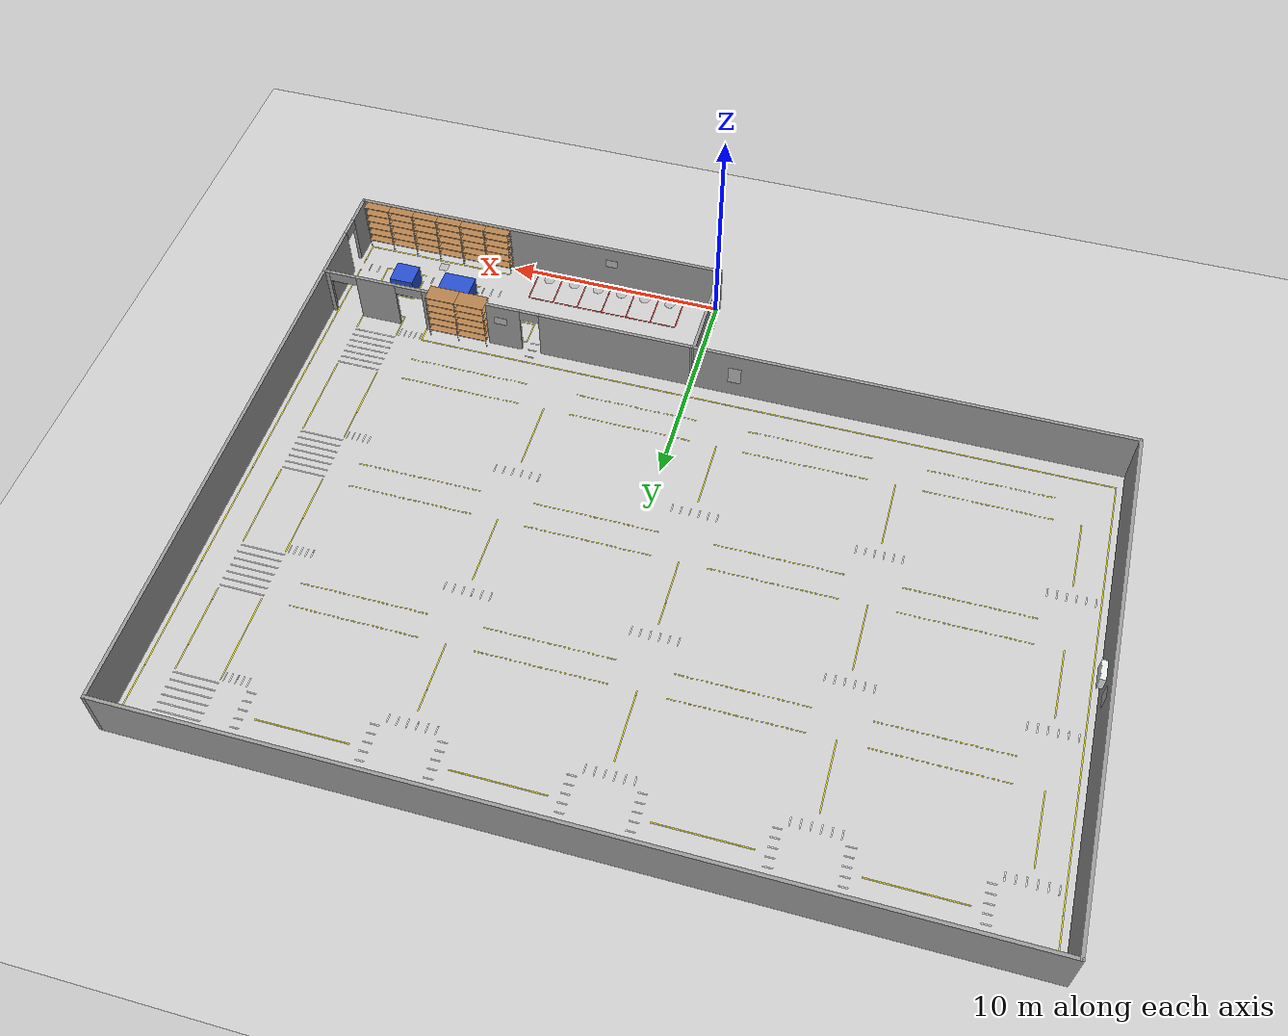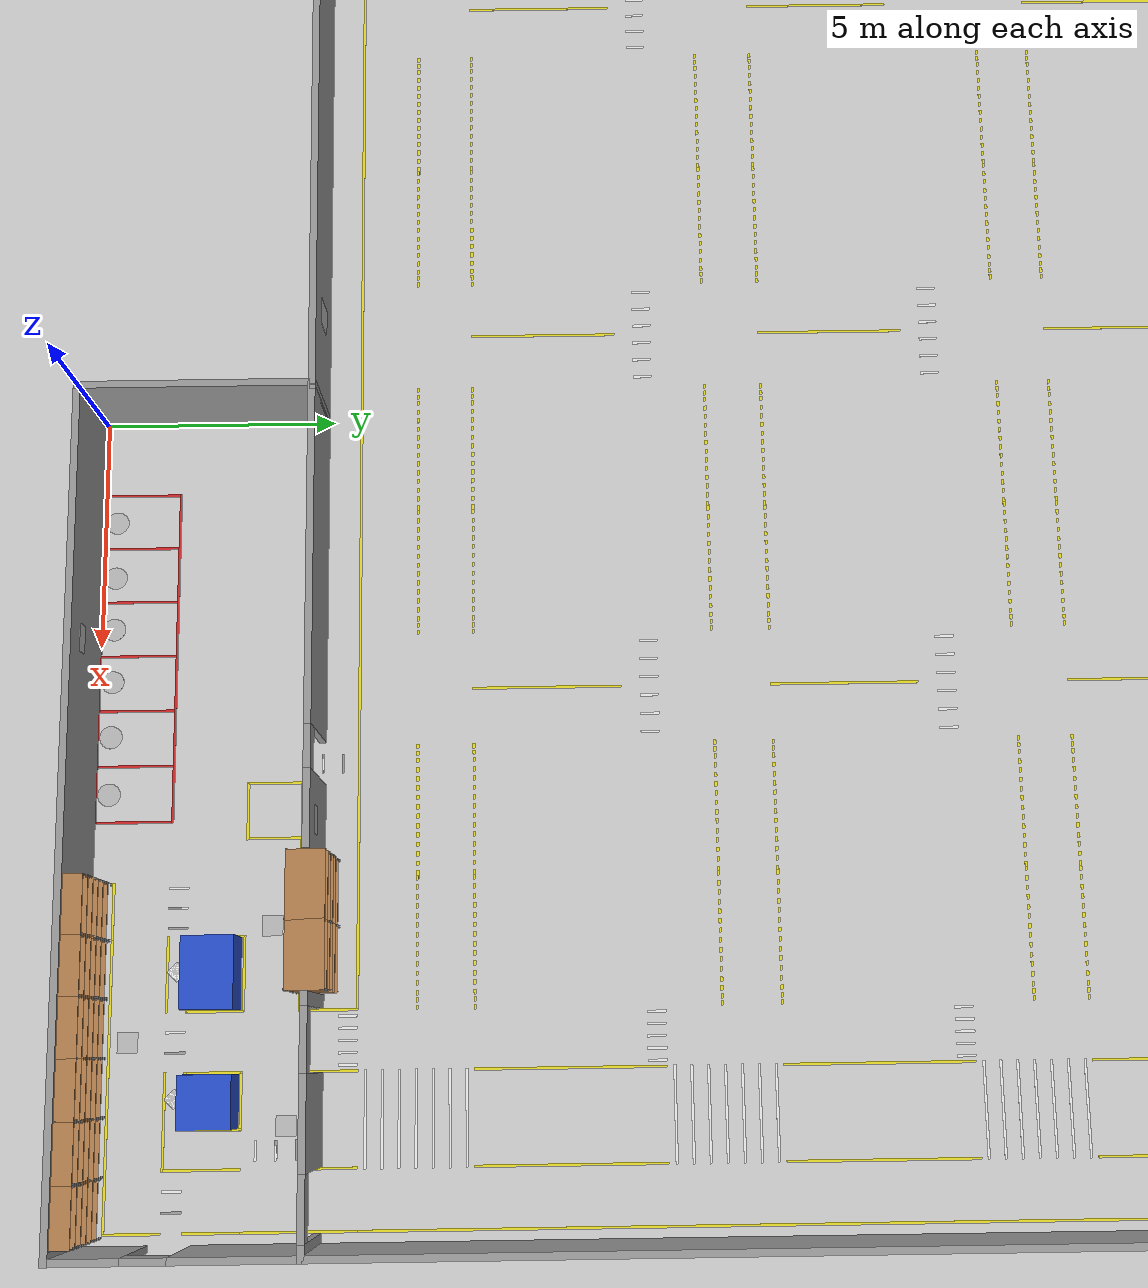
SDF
<sdf version="1.6">
 <world name="default">
  <light name="sun" type="directional">
   <pose>0 0 10 0 -0 0</pose>
   <diffuse>0.8 0.8 0.8 1</diffuse>
   <specular>0.2 0.2 0.2 1</specular>
   <attenuation>
    <range>1000</range>
    <constant>0.9</constant>
    <linear>0.01</linear>
    <quadratic>0.001</quadratic>
   </attenuation>
   <direction>-0.5 0.1 -0.9</direction>
  </light>
  <model name="ground_plane">
   <static>1</static>
   <link name="link">
    <collision name="collision">
     <geometry><plane><normal>0 0 1</normal><size>100 100</size></plane></geometry>
     <surface><friction><ode><mu>100</mu><mu2>50</mu2></ode></friction></surface>
    </collision>
    <visual name="visual">
     <cast_shadows>0</cast_shadows>
     <geometry><plane><normal>0 0 1</normal><size>100 100</size></plane></geometry>
     <material>
      <script><uri>file://media/materials/scripts/gazebo.material</uri><name>Gazebo/Grey</name></script>
     </material>
    </visual>
   </link>
  </model>
  <gravity>0 0 -9.8</gravity>
  <magnetic_field>6e-06 2.3e-05 -4.2e-05</magnetic_field>
  <atmosphere type="adiabatic"/>
  <physics name="default_physics" default="0" type="ode">
   <max_step_size>0.001</max_step_size>
   <real_time_factor>1</real_time_factor>
   <real_time_update_rate>1000</real_time_update_rate>
  </physics>
  <scene><ambient>0.4 0.4 0.4 1</ambient><background>0.7 0.7 0.7 1</background><shadows>1</shadows></scene>
  <spherical_coordinates>
   <surface_model>EARTH_WGS84</surface_model>
   <latitude_deg>0</latitude_deg>
   <longitude_deg>0</longitude_deg>
   <elevation>0</elevation>
   <heading_deg>0</heading_deg>
  </spherical_coordinates>
  <model name="parkingArea_720x160">
   <link name="link_3">
    <inertial>
     <mass>1</mass>
     <inertia>
      <ixx>0.166667</ixx>
      <ixy>0</ixy>
      <ixz>0</ixz>
      <iyy>0.166667</iyy>
      <iyz>0</iyz>
      <izz>0.166667</izz>
     </inertia>
    </inertial>
    <visual name="visual">
     <pose>0.825 0 0 0 -0 0</pose>
     <geometry><box><size>0.05 7.25 0.001</size></box></geometry>
     <material>
      <lighting>1</lighting>
      <script><uri>file://media/materials/scripts/gazebo.material</uri><name>Gazebo/Red</name></script>
     </material>
    </visual>
    <visual name="ModelPreview_6::link_3::visual_1">
     <pose>-0.825 0 0 0 -0 0</pose>
     <geometry><box><size>0.05 7.25 0.001</size></box></geometry>
     <material>
      <lighting>1</lighting>
      <script><uri>file://media/materials/scripts/gazebo.material</uri><name>Gazebo/Red</name></script>
     </material>
    </visual>
    <visual name="ModelPreview_6::link_3::visual_2">
     <pose>0 3.6 0 0 -0 0</pose>
     <geometry><box><size>1.6 0.05 0.001</size></box></geometry>
     <material>
      <lighting>1</lighting>
      <script><uri>file://media/materials/scripts/gazebo.material</uri><name>Gazebo/Red</name></script>
     </material>
    </visual>
    <visual name="ModelPreview_6::link_3::visual_3">
     <pose>0 -3.6 0 0 -0 0</pose>
     <geometry><box><size>1.6 0.05 0.001</size></box></geometry>
     <material>
      <lighting>1</lighting>
      <script><uri>file://media/materials/scripts/gazebo.material</uri><name>Gazebo/Red</name></script>
     </material>
    </visual>
    <visual name="ModelPreview_6::link_3::visual_4">
     <pose>0 -2.4 0 0 -0 0</pose>
     <geometry><box><size>1.6 0.05 0.001</size></box></geometry>
     <material>
      <lighting>1</lighting>
      <script><uri>file://media/materials/scripts/gazebo.material</uri><name>Gazebo/Red</name></script>
     </material>
    </visual>
    <visual name="ModelPreview_6::link_3::visual_5">
     <pose>0 -1.2 0 0 -0 0</pose>
     <geometry><box><size>1.6 0.05 0.001</size></box></geometry>
     <material>
      <lighting>1</lighting>
      <script><uri>file://media/materials/scripts/gazebo.material</uri><name>Gazebo/Red</name></script>
     </material>
    </visual>
    <visual name="ModelPreview_6::link_3::visual_6">
     <geometry><box><size>1.6 0.05 0.001</size></box></geometry>
     <material>
      <lighting>1</lighting>
      <script><uri>file://media/materials/scripts/gazebo.material</uri><name>Gazebo/Red</name></script>
     </material>
    </visual>
    <visual name="ModelPreview_6::link_3::visual_7">
     <pose>0 1.2 0 0 -0 0</pose>
     <geometry><box><size>1.6 0.05 0.001</size></box></geometry>
     <material>
      <lighting>1</lighting>
      <script><uri>file://media/materials/scripts/gazebo.material</uri><name>Gazebo/Red</name></script>
     </material>
    </visual>
    <visual name="ModelPreview_6::link_3::visual_8">
     <pose>0 2.4 0 0 -0 0</pose>
     <geometry><box><size>1.6 0.05 0.001</size></box></geometry>
     <material>
      <lighting>1</lighting>
      <script><uri>file://media/materials/scripts/gazebo.material</uri><name>Gazebo/Red</name></script>
     </material>
    </visual>
    <visual name="ModelPreview_6::link_3::visual_9">
     <pose>-0.47 2.65 0 0 -0 1</pose>
     <geometry>
      <mesh><uri>model://parkingArea_720x160/model/model.dae</uri><scale>0.266 0.266 0.266</scale></mesh>
     </geometry>
     <material><lighting>1</lighting></material>
    </visual>
    <visual name="ModelPreview_6::link_3::visual_10">
     <pose>-0.47 1.41 0 0 -0 1</pose>
     <geometry>
      <mesh><uri>model://parkingArea_720x160/model/model.dae</uri><scale>0.266 0.266 0.266</scale></mesh>
     </geometry>
     <material><lighting>1</lighting></material>
    </visual>
    <visual name="ModelPreview_6::link_3::visual_11">
     <pose>-0.47 0.26 0 0 -0 1</pose>
     <geometry>
      <mesh><uri>model://parkingArea_720x160/model/model.dae</uri><scale>0.266 0.266 0.266</scale></mesh>
     </geometry>
     <material><lighting>1</lighting></material>
    </visual>
    <visual name="ModelPreview_6::link_3::visual_12">
     <pose>-0.47 -0.9 0 0 -0 1</pose>
     <geometry>
      <mesh><uri>model://parkingArea_720x160/model/model.dae</uri><scale>0.266 0.266 0.266</scale></mesh>
     </geometry>
     <material><lighting>1</lighting></material>
    </visual>
    <visual name="ModelPreview_6::link_3::visual_13">
     <pose>-0.47 -2.1 0 0 -0 1</pose>
     <geometry>
      <mesh><uri>model://parkingArea_720x160/model/model.dae</uri><scale>0.266 0.266 0.8266</scale></mesh>
     </geometry>
     <material><lighting>1</lighting></material>
    </visual>
    <visual name="ModelPreview_6::link_3::visual_14">
     <pose>-0.47 -3.34 0 0 -0 1</pose>
     <geometry>
      <mesh><uri>model://parkingArea_720x160/model/model.dae</uri><scale>0.266 0.266 0.266</scale></mesh>
     </geometry>
    </visual>
   </link>
   <static>1</static>
   <pose>5.2 0.8 0 0 -0 1.5708</pose>
  </model>
  <model name="shelfDemo_120cmx40cm">
   <link name="link_0">
    <inertial>
     <mass>1</mass>
     <inertia>
      <ixx>0.166667</ixx>
      <ixy>0</ixy>
      <ixz>0</ixz>
      <iyy>0.166667</iyy>
      <iyz>0</iyz>
      <izz>0.166667</izz>
     </inertia>
    </inertial>
    <visual name="visual">
     <pose>0 0 0.414 0 -0 0</pose>
     <geometry><box><size>1.2 0.4 0.03</size></box></geometry>
     <material>
      <lighting>1</lighting>
      <script><uri>file://media/materials/scripts/gazebo.material</uri><name>Gazebo/WoodFloor</name></script>
      <shader type="pixel"><normal_map>__default__</normal_map></shader>
     </material>
    </visual>
    <visual name="ModelPreview_0::link_0::visual_2">
     <pose>0 0 0.828 0 -0 0</pose>
     <geometry><box><size>1.2 0.4 0.03</size></box></geometry>
     <material>
      <lighting>1</lighting>
      <script><uri>file://media/materials/scripts/gazebo.material</uri><name>Gazebo/WoodFloor</name></script>
      <shader type="pixel"><normal_map>__default__</normal_map></shader>
     </material>
    </visual>
    <visual name="ModelPreview_0::link_0::visual_3">
     <pose>0 0 1.242 0 -0 0</pose>
     <geometry><box><size>1.2 0.4 0.03</size></box></geometry>
     <material>
      <lighting>1</lighting>
      <script><uri>file://media/materials/scripts/gazebo.material</uri><name>Gazebo/WoodFloor</name></script>
      <shader type="pixel"><normal_map>__default__</normal_map></shader>
     </material>
    </visual>
    <visual name="ModelPreview_0::link_0::visual_4">
     <pose>0 0 1.656 0 -0 0</pose>
     <geometry><box><size>1.2 0.4 0.03</size></box></geometry>
     <material>
      <lighting>1</lighting>
      <script><uri>file://media/materials/scripts/gazebo.material</uri><name>Gazebo/WoodFloor</name></script>
      <shader type="pixel"><normal_map>__default__</normal_map></shader>
     </material>
    </visual>
    <visual name="ModelPreview_0::link_0::visual_5">
     <pose>0 0 2.07 0 -0 0</pose>
     <geometry><box><size>1.2 0.4 0.03</size></box></geometry>
     <material>
      <lighting>1</lighting>
      <script><uri>file://media/materials/scripts/gazebo.material</uri><name>Gazebo/WoodFloor</name></script>
      <shader type="pixel"><normal_map>__default__</normal_map></shader>
     </material>
    </visual>
    <visual name="ModelPreview_0::link_0::visual_6">
     <pose>0 0 2.484 0 -0 0</pose>
     <geometry><box><size>1.2 0.4 0.03</size></box></geometry>
     <material>
      <lighting>1</lighting>
      <script><uri>file://media/materials/scripts/gazebo.material</uri><name>Gazebo/WoodFloor</name></script>
      <shader type="pixel"><normal_map>__default__</normal_map></shader>
     </material>
    </visual>
    <visual name="ModelPreview_0::link_0::visual_7">
     <pose>0.585 0.185 0 0 -0 0</pose>
     <geometry>
      <mesh><uri>model://shelfDemo_91/model/2-5mDirek.stl</uri><scale>0.0008 0.0008 0.001</scale></mesh>
     </geometry>
     <material>
      <lighting>1</lighting>
      <script><uri>file://media/materials/scripts/gazebo.material</uri><name>Gazebo/Grey</name></script>
      <shader type="pixel"><normal_map>__default__</normal_map></shader>
      <ambient>0.3 0.3 0.3 1</ambient>
      <diffuse>0.7 0.7 0.7 1</diffuse>
      <specular>0.01 0.01 0.01 1</specular>
      <emissive>0 0 0 1</emissive>
     </material>
    </visual>
    <visual name="ModelPreview_0::link_0::visual_8">
     <pose>-0.585 0.185 0 0 -0 0</pose>
     <geometry>
      <mesh><uri>model://shelfDemo_91/model/2-5mDirek.stl</uri><scale>0.0008 0.0008 0.001</scale></mesh>
     </geometry>
     <material>
      <lighting>1</lighting>
      <script><uri>file://media/materials/scripts/gazebo.material</uri><name>Gazebo/Grey</name></script>
      <shader type="pixel"><normal_map>__default__</normal_map></shader>
      <ambient>0.3 0.3 0.3 1</ambient>
      <diffuse>0.7 0.7 0.7 1</diffuse>
      <specular>0.01 0.01 0.01 1</specular>
      <emissive>0 0 0 1</emissive>
     </material>
    </visual>
    <visual name="ModelPreview_0::link_0::visual_9">
     <pose>0.585 -0.185 0 0 -0 0</pose>
     <geometry>
      <mesh><uri>model://shelfDemo_91/model/2-5mDirek.stl</uri><scale>0.0008 0.0008 0.001</scale></mesh>
     </geometry>
     <material>
      <lighting>1</lighting>
      <script><uri>file://media/materials/scripts/gazebo.material</uri><name>Gazebo/Grey</name></script>
      <shader type="pixel"><normal_map>__default__</normal_map></shader>
      <ambient>0.3 0.3 0.3 1</ambient>
      <diffuse>0.7 0.7 0.7 1</diffuse>
      <specular>0.01 0.01 0.01 1</specular>
      <emissive>0 0 0 1</emissive>
     </material>
    </visual>
    <visual name="ModelPreview_0::link_0::visual_10">
     <pose>-0.585 -0.185 0 0 -0 0</pose>
     <geometry>
      <mesh><uri>model://shelfDemo_91/model/2-5mDirek.stl</uri><scale>0.0008 0.0008 0.001</scale></mesh>
     </geometry>
     <material>
      <lighting>1</lighting>
      <script><uri>file://media/materials/scripts/gazebo.material</uri><name>Gazebo/Grey</name></script>
      <shader type="pixel"><normal_map>__default__</normal_map></shader>
      <ambient>0.3 0.3 0.3 1</ambient>
      <diffuse>0.7 0.7 0.7 1</diffuse>
      <specular>0.01 0.01 0.01 1</specular>
      <emissive>0 0 0 1</emissive>
     </material>
    </visual>
    <collision name="collision_6">
     <pose>0.585 0.185 1.25 0 -0 0</pose>
     <geometry><box><size>0.02 0.02 2.5</size></box></geometry>
    </collision>
    <collision name="collision_7">
     <pose>0.585 -0.185 1.25 0 -0 0</pose>
     <geometry><box><size>0.02 0.02 2.5</size></box></geometry>
    </collision>
    <collision name="collision_8">
     <pose>-0.585 0.185 1.25 0 -0 0</pose>
     <geometry><box><size>0.02 0.02 2.5</size></box></geometry>
    </collision>
    <collision name="collision">
     <pose>0 0 0.414 0 -0 0</pose>
     <geometry><box><size>1.2 0.4 0.03</size></box></geometry>
    </collision>
    <collision name="collision_1">
     <pose>0 0 0.828 0 -0 0</pose>
     <geometry><box><size>1.2 0.4 0.03</size></box></geometry>
    </collision>
    <collision name="collision_2">
     <pose>0 0 1.242 0 -0 0</pose>
     <geometry><box><size>1.2 0.4 0.03</size></box></geometry>
    </collision>
    <collision name="collision_3">
     <pose>0 0 1.656 0 -0 0</pose>
     <geometry><box><size>1.2 0.4 0.03</size></box></geometry>
    </collision>
    <collision name="collision_4">
     <pose>0 0 2.07 0 -0 0</pose>
     <geometry><box><size>1.2 0.4 0.03</size></box></geometry>
    </collision>
    <collision name="collision_5">
     <pose>0 0 2.484 0 -0 0</pose>
     <geometry><box><size>1.2 0.4 0.03</size></box></geometry>
    </collision>
    <collision name="collision_9">
     <pose>-0.585 -0.185 1.25 0 -0 0</pose>
     <geometry><box><size>0.02 0.02 2.5</size></box></geometry>
    </collision>
   </link>
   <static>1</static>
   <pose>10.7 0.2 0 0 -0 0</pose>
  </model>
  <model name="shelfDemo_120cmx40cm_0">
   <link name="link_0">
    <inertial>
     <mass>1</mass>
     <inertia>
      <ixx>0.166667</ixx>
      <ixy>0</ixy>
      <ixz>0</ixz>
      <iyy>0.166667</iyy>
      <iyz>0</iyz>
      <izz>0.166667</izz>
     </inertia>
    </inertial>
    <visual name="visual">
     <pose>0 0 0.414 0 -0 0</pose>
     <geometry><box><size>1.2 0.4 0.03</size></box></geometry>
     <material>
      <lighting>1</lighting>
      <script><uri>file://media/materials/scripts/gazebo.material</uri><name>Gazebo/WoodFloor</name></script>
      <shader type="pixel"><normal_map>__default__</normal_map></shader>
     </material>
    </visual>
    <visual name="ModelPreview_0::link_0::visual_2">
     <pose>0 0 0.828 0 -0 0</pose>
     <geometry><box><size>1.2 0.4 0.03</size></box></geometry>
     <material>
      <lighting>1</lighting>
      <script><uri>file://media/materials/scripts/gazebo.material</uri><name>Gazebo/WoodFloor</name></script>
      <shader type="pixel"><normal_map>__default__</normal_map></shader>
     </material>
    </visual>
    <visual name="ModelPreview_0::link_0::visual_3">
     <pose>0 0 1.242 0 -0 0</pose>
     <geometry><box><size>1.2 0.4 0.03</size></box></geometry>
     <material>
      <lighting>1</lighting>
      <script><uri>file://media/materials/scripts/gazebo.material</uri><name>Gazebo/WoodFloor</name></script>
      <shader type="pixel"><normal_map>__default__</normal_map></shader>
     </material>
    </visual>
    <visual name="ModelPreview_0::link_0::visual_4">
     <pose>0 0 1.656 0 -0 0</pose>
     <geometry><box><size>1.2 0.4 0.03</size></box></geometry>
     <material>
      <lighting>1</lighting>
      <script><uri>file://media/materials/scripts/gazebo.material</uri><name>Gazebo/WoodFloor</name></script>
      <shader type="pixel"><normal_map>__default__</normal_map></shader>
     </material>
    </visual>
    <visual name="ModelPreview_0::link_0::visual_5">
     <pose>0 0 2.07 0 -0 0</pose>
     <geometry><box><size>1.2 0.4 0.03</size></box></geometry>
     <material>
      <lighting>1</lighting>
      <script><uri>file://media/materials/scripts/gazebo.material</uri><name>Gazebo/WoodFloor</name></script>
      <shader type="pixel"><normal_map>__default__</normal_map></shader>
     </material>
    </visual>
    <visual name="ModelPreview_0::link_0::visual_6">
     <pose>0 0 2.484 0 -0 0</pose>
     <geometry><box><size>1.2 0.4 0.03</size></box></geometry>
     <material>
      <lighting>1</lighting>
      <script><uri>file://media/materials/scripts/gazebo.material</uri><name>Gazebo/WoodFloor</name></script>
      <shader type="pixel"><normal_map>__default__</normal_map></shader>
     </material>
    </visual>
    <visual name="ModelPreview_0::link_0::visual_7">
     <pose>0.585 0.185 0 0 -0 0</pose>
     <geometry>
      <mesh><uri>model://shelfDemo_91/model/2-5mDirek.stl</uri><scale>0.0008 0.0008 0.001</scale></mesh>
     </geometry>
     <material>
      <lighting>1</lighting>
      <script><uri>file://media/materials/scripts/gazebo.material</uri><name>Gazebo/Grey</name></script>
      <shader type="pixel"><normal_map>__default__</normal_map></shader>
      <ambient>0.3 0.3 0.3 1</ambient>
      <diffuse>0.7 0.7 0.7 1</diffuse>
      <specular>0.01 0.01 0.01 1</specular>
      <emissive>0 0 0 1</emissive>
     </material>
    </visual>
    <visual name="ModelPreview_0::link_0::visual_8">
     <pose>-0.585 0.185 0 0 -0 0</pose>
     <geometry>
      <mesh><uri>model://shelfDemo_91/model/2-5mDirek.stl</uri><scale>0.0008 0.0008 0.001</scale></mesh>
     </geometry>
     <material>
      <lighting>1</lighting>
      <script><uri>file://media/materials/scripts/gazebo.material</uri><name>Gazebo/Grey</name></script>
      <shader type="pixel"><normal_map>__default__</normal_map></shader>
      <ambient>0.3 0.3 0.3 1</ambient>
      <diffuse>0.7 0.7 0.7 1</diffuse>
      <specular>0.01 0.01 0.01 1</specular>
      <emissive>0 0 0 1</emissive>
     </material>
    </visual>
    <visual name="ModelPreview_0::link_0::visual_9">
     <pose>0.585 -0.185 0 0 -0 0</pose>
     <geometry>
      <mesh><uri>model://shelfDemo_91/model/2-5mDirek.stl</uri><scale>0.0008 0.0008 0.001</scale></mesh>
     </geometry>
     <material>
      <lighting>1</lighting>
      <script><uri>file://media/materials/scripts/gazebo.material</uri><name>Gazebo/Grey</name></script>
      <shader type="pixel"><normal_map>__default__</normal_map></shader>
      <ambient>0.3 0.3 0.3 1</ambient>
      <diffuse>0.7 0.7 0.7 1</diffuse>
      <specular>0.01 0.01 0.01 1</specular>
      <emissive>0 0 0 1</emissive>
     </material>
    </visual>
    <visual name="ModelPreview_0::link_0::visual_10">
     <pose>-0.585 -0.185 0 0 -0 0</pose>
     <geometry>
      <mesh><uri>model://shelfDemo_91/model/2-5mDirek.stl</uri><scale>0.0008 0.0008 0.001</scale></mesh>
     </geometry>
     <material>
      <lighting>1</lighting>
      <script><uri>file://media/materials/scripts/gazebo.material</uri><name>Gazebo/Grey</name></script>
      <shader type="pixel"><normal_map>__default__</normal_map></shader>
      <ambient>0.3 0.3 0.3 1</ambient>
      <diffuse>0.7 0.7 0.7 1</diffuse>
      <specular>0.01 0.01 0.01 1</specular>
      <emissive>0 0 0 1</emissive>
     </material>
    </visual>
    <collision name="collision_6">
     <pose>0.585 0.185 1.25 0 -0 0</pose>
     <geometry><box><size>0.02 0.02 2.5</size></box></geometry>
    </collision>
    <collision name="collision_7">
     <pose>0.585 -0.185 1.25 0 -0 0</pose>
     <geometry><box><size>0.02 0.02 2.5</size></box></geometry>
    </collision>
    <collision name="collision_8">
     <pose>-0.585 0.185 1.25 0 -0 0</pose>
     <geometry><box><size>0.02 0.02 2.5</size></box></geometry>
    </collision>
    <collision name="collision">
     <pose>0 0 0.414 0 -0 0</pose>
     <geometry><box><size>1.2 0.4 0.03</size></box></geometry>
    </collision>
    <collision name="collision_1">
     <pose>0 0 0.828 0 -0 0</pose>
     <geometry><box><size>1.2 0.4 0.03</size></box></geometry>
    </collision>
    <collision name="collision_2">
     <pose>0 0 1.242 0 -0 0</pose>
     <geometry><box><size>1.2 0.4 0.03</size></box></geometry>
    </collision>
    <collision name="collision_3">
     <pose>0 0 1.656 0 -0 0</pose>
     <geometry><box><size>1.2 0.4 0.03</size></box></geometry>
    </collision>
    <collision name="collision_4">
     <pose>0 0 2.07 0 -0 0</pose>
     <geometry><box><size>1.2 0.4 0.03</size></box></geometry>
    </collision>
    <collision name="collision_5">
     <pose>0 0 2.484 0 -0 0</pose>
     <geometry><box><size>1.2 0.4 0.03</size></box></geometry>
    </collision>
    <collision name="collision_9">
     <pose>-0.585 -0.185 1.25 0 -0 0</pose>
     <geometry><box><size>0.02 0.02 2.5</size></box></geometry>
    </collision>
   </link>
   <static>1</static>
   <pose>11.9 0.2 0 0 -0 0</pose>
  </model>
  <model name="shelfDemo_120cmx40cm_1">
   <link name="link_0">
    <inertial>
     <mass>1</mass>
     <inertia>
      <ixx>0.166667</ixx>
      <ixy>0</ixy>
      <ixz>0</ixz>
      <iyy>0.166667</iyy>
      <iyz>0</iyz>
      <izz>0.166667</izz>
     </inertia>
    </inertial>
    <visual name="visual">
     <pose>0 0 0.414 0 -0 0</pose>
     <geometry><box><size>1.2 0.4 0.03</size></box></geometry>
     <material>
      <lighting>1</lighting>
      <script><uri>file://media/materials/scripts/gazebo.material</uri><name>Gazebo/WoodFloor</name></script>
      <shader type="pixel"><normal_map>__default__</normal_map></shader>
     </material>
    </visual>
    <visual name="ModelPreview_0::link_0::visual_2">
     <pose>0 0 0.828 0 -0 0</pose>
     <geometry><box><size>1.2 0.4 0.03</size></box></geometry>
     <material>
      <lighting>1</lighting>
      <script><uri>file://media/materials/scripts/gazebo.material</uri><name>Gazebo/WoodFloor</name></script>
      <shader type="pixel"><normal_map>__default__</normal_map></shader>
     </material>
    </visual>
    <visual name="ModelPreview_0::link_0::visual_3">
     <pose>0 0 1.242 0 -0 0</pose>
     <geometry><box><size>1.2 0.4 0.03</size></box></geometry>
     <material>
      <lighting>1</lighting>
      <script><uri>file://media/materials/scripts/gazebo.material</uri><name>Gazebo/WoodFloor</name></script>
      <shader type="pixel"><normal_map>__default__</normal_map></shader>
     </material>
    </visual>
    <visual name="ModelPreview_0::link_0::visual_4">
     <pose>0 0 1.656 0 -0 0</pose>
     <geometry><box><size>1.2 0.4 0.03</size></box></geometry>
     <material>
      <lighting>1</lighting>
      <script><uri>file://media/materials/scripts/gazebo.material</uri><name>Gazebo/WoodFloor</name></script>
      <shader type="pixel"><normal_map>__default__</normal_map></shader>
     </material>
    </visual>
    <visual name="ModelPreview_0::link_0::visual_5">
     <pose>0 0 2.07 0 -0 0</pose>
     <geometry><box><size>1.2 0.4 0.03</size></box></geometry>
     <material>
      <lighting>1</lighting>
      <script><uri>file://media/materials/scripts/gazebo.material</uri><name>Gazebo/WoodFloor</name></script>
      <shader type="pixel"><normal_map>__default__</normal_map></shader>
     </material>
    </visual>
    <visual name="ModelPreview_0::link_0::visual_6">
     <pose>0 0 2.484 0 -0 0</pose>
     <geometry><box><size>1.2 0.4 0.03</size></box></geometry>
     <material>
      <lighting>1</lighting>
      <script><uri>file://media/materials/scripts/gazebo.material</uri><name>Gazebo/WoodFloor</name></script>
      <shader type="pixel"><normal_map>__default__</normal_map></shader>
     </material>
    </visual>
    <visual name="ModelPreview_0::link_0::visual_7">
     <pose>0.585 0.185 0 0 -0 0</pose>
     <geometry>
      <mesh><uri>model://shelfDemo_91/model/2-5mDirek.stl</uri><scale>0.0008 0.0008 0.001</scale></mesh>
     </geometry>
     <material>
      <lighting>1</lighting>
      <script><uri>file://media/materials/scripts/gazebo.material</uri><name>Gazebo/Grey</name></script>
      <shader type="pixel"><normal_map>__default__</normal_map></shader>
      <ambient>0.3 0.3 0.3 1</ambient>
      <diffuse>0.7 0.7 0.7 1</diffuse>
      <specular>0.01 0.01 0.01 1</specular>
      <emissive>0 0 0 1</emissive>
     </material>
    </visual>
    <visual name="ModelPreview_0::link_0::visual_8">
     <pose>-0.585 0.185 0 0 -0 0</pose>
     <geometry>
      <mesh><uri>model://shelfDemo_91/model/2-5mDirek.stl</uri><scale>0.0008 0.0008 0.001</scale></mesh>
     </geometry>
     <material>
      <lighting>1</lighting>
      <script><uri>file://media/materials/scripts/gazebo.material</uri><name>Gazebo/Grey</name></script>
      <shader type="pixel"><normal_map>__default__</normal_map></shader>
      <ambient>0.3 0.3 0.3 1</ambient>
      <diffuse>0.7 0.7 0.7 1</diffuse>
      <specular>0.01 0.01 0.01 1</specular>
      <emissive>0 0 0 1</emissive>
     </material>
    </visual>
    <visual name="ModelPreview_0::link_0::visual_9">
     <pose>0.585 -0.185 0 0 -0 0</pose>
     <geometry>
      <mesh><uri>model://shelfDemo_91/model/2-5mDirek.stl</uri><scale>0.0008 0.0008 0.001</scale></mesh>
     </geometry>
     <material>
      <lighting>1</lighting>
      <script><uri>file://media/materials/scripts/gazebo.material</uri><name>Gazebo/Grey</name></script>
      <shader type="pixel"><normal_map>__default__</normal_map></shader>
      <ambient>0.3 0.3 0.3 1</ambient>
      <diffuse>0.7 0.7 0.7 1</diffuse>
      <specular>0.01 0.01 0.01 1</specular>
      <emissive>0 0 0 1</emissive>
     </material>
    </visual>
    <visual name="ModelPreview_0::link_0::visual_10">
     <pose>-0.585 -0.185 0 0 -0 0</pose>
     <geometry>
      <mesh><uri>model://shelfDemo_91/model/2-5mDirek.stl</uri><scale>0.0008 0.0008 0.001</scale></mesh>
     </geometry>
     <material>
      <lighting>1</lighting>
      <script><uri>file://media/materials/scripts/gazebo.material</uri><name>Gazebo/Grey</name></script>
      <shader type="pixel"><normal_map>__default__</normal_map></shader>
      <ambient>0.3 0.3 0.3 1</ambient>
      <diffuse>0.7 0.7 0.7 1</diffuse>
      <specular>0.01 0.01 0.01 1</specular>
      <emissive>0 0 0 1</emissive>
     </material>
    </visual>
    <collision name="collision_6">
     <pose>0.585 0.185 1.25 0 -0 0</pose>
     <geometry><box><size>0.02 0.02 2.5</size></box></geometry>
    </collision>
    <collision name="collision_7">
     <pose>0.585 -0.185 1.25 0 -0 0</pose>
     <geometry><box><size>0.02 0.02 2.5</size></box></geometry>
    </collision>
    <collision name="collision_8">
     <pose>-0.585 0.185 1.25 0 -0 0</pose>
     <geometry><box><size>0.02 0.02 2.5</size></box></geometry>
    </collision>
    <collision name="collision">
     <pose>0 0 0.414 0 -0 0</pose>
     <geometry><box><size>1.2 0.4 0.03</size></box></geometry>
    </collision>
    <collision name="collision_1">
     <pose>0 0 0.828 0 -0 0</pose>
     <geometry><box><size>1.2 0.4 0.03</size></box></geometry>
    </collision>
    <collision name="collision_2">
     <pose>0 0 1.242 0 -0 0</pose>
     <geometry><box><size>1.2 0.4 0.03</size></box></geometry>
    </collision>
    <collision name="collision_3">
     <pose>0 0 1.656 0 -0 0</pose>
     <geometry><box><size>1.2 0.4 0.03</size></box></geometry>
    </collision>
    <collision name="collision_4">
     <pose>0 0 2.07 0 -0 0</pose>
     <geometry><box><size>1.2 0.4 0.03</size></box></geometry>
    </collision>
    <collision name="collision_5">
     <pose>0 0 2.484 0 -0 0</pose>
     <geometry><box><size>1.2 0.4 0.03</size></box></geometry>
    </collision>
    <collision name="collision_9">
     <pose>-0.585 -0.185 1.25 0 -0 0</pose>
     <geometry><box><size>0.02 0.02 2.5</size></box></geometry>
    </collision>
   </link>
   <static>1</static>
   <pose>13.1 0.2 0 0 -0 0</pose>
  </model>
  <model name="shelfDemo_120cmx40cm_2">
   <link name="link_0">
    <inertial>
     <mass>1</mass>
     <inertia>
      <ixx>0.166667</ixx>
      <ixy>0</ixy>
      <ixz>0</ixz>
      <iyy>0.166667</iyy>
      <iyz>0</iyz>
      <izz>0.166667</izz>
     </inertia>
    </inertial>
    <visual name="visual">
     <pose>0 0 0.414 0 -0 0</pose>
     <geometry><box><size>1.2 0.4 0.03</size></box></geometry>
     <material>
      <lighting>1</lighting>
      <script><uri>file://media/materials/scripts/gazebo.material</uri><name>Gazebo/WoodFloor</name></script>
      <shader type="pixel"><normal_map>__default__</normal_map></shader>
     </material>
    </visual>
    <visual name="ModelPreview_0::link_0::visual_2">
     <pose>0 0 0.828 0 -0 0</pose>
     <geometry><box><size>1.2 0.4 0.03</size></box></geometry>
     <material>
      <lighting>1</lighting>
      <script><uri>file://media/materials/scripts/gazebo.material</uri><name>Gazebo/WoodFloor</name></script>
      <shader type="pixel"><normal_map>__default__</normal_map></shader>
     </material>
    </visual>
    <visual name="ModelPreview_0::link_0::visual_3">
     <pose>0 0 1.242 0 -0 0</pose>
     <geometry><box><size>1.2 0.4 0.03</size></box></geometry>
     <material>
      <lighting>1</lighting>
      <script><uri>file://media/materials/scripts/gazebo.material</uri><name>Gazebo/WoodFloor</name></script>
      <shader type="pixel"><normal_map>__default__</normal_map></shader>
     </material>
    </visual>
    <visual name="ModelPreview_0::link_0::visual_4">
     <pose>0 0 1.656 0 -0 0</pose>
     <geometry><box><size>1.2 0.4 0.03</size></box></geometry>
     <material>
      <lighting>1</lighting>
      <script><uri>file://media/materials/scripts/gazebo.material</uri><name>Gazebo/WoodFloor</name></script>
      <shader type="pixel"><normal_map>__default__</normal_map></shader>
     </material>
    </visual>
    <visual name="ModelPreview_0::link_0::visual_5">
     <pose>0 0 2.07 0 -0 0</pose>
     <geometry><box><size>1.2 0.4 0.03</size></box></geometry>
     <material>
      <lighting>1</lighting>
      <script><uri>file://media/materials/scripts/gazebo.material</uri><name>Gazebo/WoodFloor</name></script>
      <shader type="pixel"><normal_map>__default__</normal_map></shader>
     </material>
    </visual>
    <visual name="ModelPreview_0::link_0::visual_6">
     <pose>0 0 2.484 0 -0 0</pose>
     <geometry><box><size>1.2 0.4 0.03</size></box></geometry>
     <material>
      <lighting>1</lighting>
      <script><uri>file://media/materials/scripts/gazebo.material</uri><name>Gazebo/WoodFloor</name></script>
      <shader type="pixel"><normal_map>__default__</normal_map></shader>
     </material>
    </visual>
    <visual name="ModelPreview_0::link_0::visual_7">
     <pose>0.585 0.185 0 0 -0 0</pose>
     <geometry>
      <mesh><uri>model://shelfDemo_91/model/2-5mDirek.stl</uri><scale>0.0008 0.0008 0.001</scale></mesh>
     </geometry>
     <material>
      <lighting>1</lighting>
      <script><uri>file://media/materials/scripts/gazebo.material</uri><name>Gazebo/Grey</name></script>
      <shader type="pixel"><normal_map>__default__</normal_map></shader>
      <ambient>0.3 0.3 0.3 1</ambient>
      <diffuse>0.7 0.7 0.7 1</diffuse>
      <specular>0.01 0.01 0.01 1</specular>
      <emissive>0 0 0 1</emissive>
     </material>
    </visual>
    <visual name="ModelPreview_0::link_0::visual_8">
     <pose>-0.585 0.185 0 0 -0 0</pose>
     <geometry>
      <mesh><uri>model://shelfDemo_91/model/2-5mDirek.stl</uri><scale>0.0008 0.0008 0.001</scale></mesh>
     </geometry>
     <material>
      <lighting>1</lighting>
      <script><uri>file://media/materials/scripts/gazebo.material</uri><name>Gazebo/Grey</name></script>
      <shader type="pixel"><normal_map>__default__</normal_map></shader>
      <ambient>0.3 0.3 0.3 1</ambient>
      <diffuse>0.7 0.7 0.7 1</diffuse>
      <specular>0.01 0.01 0.01 1</specular>
      <emissive>0 0 0 1</emissive>
     </material>
    </visual>
    <visual name="ModelPreview_0::link_0::visual_9">
     <pose>0.585 -0.185 0 0 -0 0</pose>
     <geometry>
      <mesh><uri>model://shelfDemo_91/model/2-5mDirek.stl</uri><scale>0.0008 0.0008 0.001</scale></mesh>
     </geometry>
     <material>
      <lighting>1</lighting>
      <script><uri>file://media/materials/scripts/gazebo.material</uri><name>Gazebo/Grey</name></script>
      <shader type="pixel"><normal_map>__default__</normal_map></shader>
      <ambient>0.3 0.3 0.3 1</ambient>
      <diffuse>0.7 0.7 0.7 1</diffuse>
      <specular>0.01 0.01 0.01 1</specular>
      <emissive>0 0 0 1</emissive>
     </material>
    </visual>
    <visual name="ModelPreview_0::link_0::visual_10">
     <pose>-0.585 -0.185 0 0 -0 0</pose>
     <geometry>
      <mesh><uri>model://shelfDemo_91/model/2-5mDirek.stl</uri><scale>0.0008 0.0008 0.001</scale></mesh>
     </geometry>
     <material>
      <lighting>1</lighting>
      <script><uri>file://media/materials/scripts/gazebo.material</uri><name>Gazebo/Grey</name></script>
      <shader type="pixel"><normal_map>__default__</normal_map></shader>
      <ambient>0.3 0.3 0.3 1</ambient>
      <diffuse>0.7 0.7 0.7 1</diffuse>
      <specular>0.01 0.01 0.01 1</specular>
      <emissive>0 0 0 1</emissive>
     </material>
    </visual>
    <collision name="collision_6">
     <pose>0.585 0.185 1.25 0 -0 0</pose>
     <geometry><box><size>0.02 0.02 2.5</size></box></geometry>
    </collision>
    <collision name="collision_7">
     <pose>0.585 -0.185 1.25 0 -0 0</pose>
     <geometry><box><size>0.02 0.02 2.5</size></box></geometry>
    </collision>
    <collision name="collision_8">
     <pose>-0.585 0.185 1.25 0 -0 0</pose>
     <geometry><box><size>0.02 0.02 2.5</size></box></geometry>
    </collision>
    <collision name="collision">
     <pose>0 0 0.414 0 -0 0</pose>
     <geometry><box><size>1.2 0.4 0.03</size></box></geometry>
    </collision>
    <collision name="collision_1">
     <pose>0 0 0.828 0 -0 0</pose>
     <geometry><box><size>1.2 0.4 0.03</size></box></geometry>
    </collision>
    <collision name="collision_2">
     <pose>0 0 1.242 0 -0 0</pose>
     <geometry><box><size>1.2 0.4 0.03</size></box></geometry>
    </collision>
    <collision name="collision_3">
     <pose>0 0 1.656 0 -0 0</pose>
     <geometry><box><size>1.2 0.4 0.03</size></box></geometry>
    </collision>
    <collision name="collision_4">
     <pose>0 0 2.07 0 -0 0</pose>
     <geometry><box><size>1.2 0.4 0.03</size></box></geometry>
    </collision>
    <collision name="collision_5">
     <pose>0 0 2.484 0 -0 0</pose>
     <geometry><box><size>1.2 0.4 0.03</size></box></geometry>
    </collision>
    <collision name="collision_9">
     <pose>-0.585 -0.185 1.25 0 -0 0</pose>
     <geometry><box><size>0.02 0.02 2.5</size></box></geometry>
    </collision>
   </link>
   <static>1</static>
   <pose>14.3 0.2 0 0 -0 0</pose>
  </model>
  <model name="shelfDemo_120cmx40cm_3">
   <link name="link_0">
    <inertial>
     <mass>1</mass>
     <inertia>
      <ixx>0.166667</ixx>
      <ixy>0</ixy>
      <ixz>0</ixz>
      <iyy>0.166667</iyy>
      <iyz>0</iyz>
      <izz>0.166667</izz>
     </inertia>
    </inertial>
    <visual name="visual">
     <pose>0 0 0.414 0 -0 0</pose>
     <geometry><box><size>1.2 0.4 0.03</size></box></geometry>
     <material>
      <lighting>1</lighting>
      <script><uri>file://media/materials/scripts/gazebo.material</uri><name>Gazebo/WoodFloor</name></script>
      <shader type="pixel"><normal_map>__default__</normal_map></shader>
     </material>
    </visual>
    <visual name="ModelPreview_0::link_0::visual_2">
     <pose>0 0 0.828 0 -0 0</pose>
     <geometry><box><size>1.2 0.4 0.03</size></box></geometry>
     <material>
      <lighting>1</lighting>
      <script><uri>file://media/materials/scripts/gazebo.material</uri><name>Gazebo/WoodFloor</name></script>
      <shader type="pixel"><normal_map>__default__</normal_map></shader>
     </material>
    </visual>
    <visual name="ModelPreview_0::link_0::visual_3">
     <pose>0 0 1.242 0 -0 0</pose>
     <geometry><box><size>1.2 0.4 0.03</size></box></geometry>
     <material>
      <lighting>1</lighting>
      <script><uri>file://media/materials/scripts/gazebo.material</uri><name>Gazebo/WoodFloor</name></script>
      <shader type="pixel"><normal_map>__default__</normal_map></shader>
     </material>
    </visual>
    <visual name="ModelPreview_0::link_0::visual_4">
     <pose>0 0 1.656 0 -0 0</pose>
     <geometry><box><size>1.2 0.4 0.03</size></box></geometry>
     <material>
      <lighting>1</lighting>
      <script><uri>file://media/materials/scripts/gazebo.material</uri><name>Gazebo/WoodFloor</name></script>
      <shader type="pixel"><normal_map>__default__</normal_map></shader>
     </material>
    </visual>
    <visual name="ModelPreview_0::link_0::visual_5">
     <pose>0 0 2.07 0 -0 0</pose>
     <geometry><box><size>1.2 0.4 0.03</size></box></geometry>
     <material>
      <lighting>1</lighting>
      <script><uri>file://media/materials/scripts/gazebo.material</uri><name>Gazebo/WoodFloor</name></script>
      <shader type="pixel"><normal_map>__default__</normal_map></shader>
     </material>
    </visual>
    <visual name="ModelPreview_0::link_0::visual_6">
     <pose>0 0 2.484 0 -0 0</pose>
     <geometry><box><size>1.2 0.4 0.03</size></box></geometry>
     <material>
      <lighting>1</lighting>
      <script><uri>file://media/materials/scripts/gazebo.material</uri><name>Gazebo/WoodFloor</name></script>
      <shader type="pixel"><normal_map>__default__</normal_map></shader>
     </material>
    </visual>
    <visual name="ModelPreview_0::link_0::visual_7">
     <pose>0.585 0.185 0 0 -0 0</pose>
     <geometry>
      <mesh><uri>model://shelfDemo_91/model/2-5mDirek.stl</uri><scale>0.0008 0.0008 0.001</scale></mesh>
     </geometry>
     <material>
      <lighting>1</lighting>
      <script><uri>file://media/materials/scripts/gazebo.material</uri><name>Gazebo/Grey</name></script>
      <shader type="pixel"><normal_map>__default__</normal_map></shader>
      <ambient>0.3 0.3 0.3 1</ambient>
      <diffuse>0.7 0.7 0.7 1</diffuse>
      <specular>0.01 0.01 0.01 1</specular>
      <emissive>0 0 0 1</emissive>
     </material>
    </visual>
    <visual name="ModelPreview_0::link_0::visual_8">
     <pose>-0.585 0.185 0 0 -0 0</pose>
     <geometry>
      <mesh><uri>model://shelfDemo_91/model/2-5mDirek.stl</uri><scale>0.0008 0.0008 0.001</scale></mesh>
     </geometry>
     <material>
      <lighting>1</lighting>
      <script><uri>file://media/materials/scripts/gazebo.material</uri><name>Gazebo/Grey</name></script>
      <shader type="pixel"><normal_map>__default__</normal_map></shader>
      <ambient>0.3 0.3 0.3 1</ambient>
      <diffuse>0.7 0.7 0.7 1</diffuse>
      <specular>0.01 0.01 0.01 1</specular>
      <emissive>0 0 0 1</emissive>
     </material>
    </visual>
    <visual name="ModelPreview_0::link_0::visual_9">
     <pose>0.585 -0.185 0 0 -0 0</pose>
     <geometry>
      <mesh><uri>model://shelfDemo_91/model/2-5mDirek.stl</uri><scale>0.0008 0.0008 0.001</scale></mesh>
     </geometry>
     <material>
      <lighting>1</lighting>
      <script><uri>file://media/materials/scripts/gazebo.material</uri><name>Gazebo/Grey</name></script>
      <shader type="pixel"><normal_map>__default__</normal_map></shader>
      <ambient>0.3 0.3 0.3 1</ambient>
      <diffuse>0.7 0.7 0.7 1</diffuse>
      <specular>0.01 0.01 0.01 1</specular>
      <emissive>0 0 0 1</emissive>
     </material>
    </visual>
    <visual name="ModelPreview_0::link_0::visual_10">
     <pose>-0.585 -0.185 0 0 -0 0</pose>
     <geometry>
      <mesh><uri>model://shelfDemo_91/model/2-5mDirek.stl</uri><scale>0.0008 0.0008 0.001</scale></mesh>
     </geometry>
     <material>
      <lighting>1</lighting>
      <script><uri>file://media/materials/scripts/gazebo.material</uri><name>Gazebo/Grey</name></script>
      <shader type="pixel"><normal_map>__default__</normal_map></shader>
      <ambient>0.3 0.3 0.3 1</ambient>
      <diffuse>0.7 0.7 0.7 1</diffuse>
      <specular>0.01 0.01 0.01 1</specular>
      <emissive>0 0 0 1</emissive>
     </material>
    </visual>
    <collision name="collision_6">
     <pose>0.585 0.185 1.25 0 -0 0</pose>
     <geometry><box><size>0.02 0.02 2.5</size></box></geometry>
    </collision>
    <collision name="collision_7">
     <pose>0.585 -0.185 1.25 0 -0 0</pose>
     <geometry><box><size>0.02 0.02 2.5</size></box></geometry>
    </collision>
    <collision name="collision_8">
     <pose>-0.585 0.185 1.25 0 -0 0</pose>
     <geometry><box><size>0.02 0.02 2.5</size></box></geometry>
    </collision>
    <collision name="collision">
     <pose>0 0 0.414 0 -0 0</pose>
     <geometry><box><size>1.2 0.4 0.03</size></box></geometry>
    </collision>
    <collision name="collision_1">
     <pose>0 0 0.828 0 -0 0</pose>
     <geometry><box><size>1.2 0.4 0.03</size></box></geometry>
    </collision>
    <collision name="collision_2">
     <pose>0 0 1.242 0 -0 0</pose>
     <geometry><box><size>1.2 0.4 0.03</size></box></geometry>
    </collision>
    <collision name="collision_3">
     <pose>0 0 1.656 0 -0 0</pose>
     <geometry><box><size>1.2 0.4 0.03</size></box></geometry>
    </collision>
    <collision name="collision_4">
     <pose>0 0 2.07 0 -0 0</pose>
     <geometry><box><size>1.2 0.4 0.03</size></box></geometry>
    </collision>
    <collision name="collision_5">
     <pose>0 0 2.484 0 -0 0</pose>
     <geometry><box><size>1.2 0.4 0.03</size></box></geometry>
    </collision>
    <collision name="collision_9">
     <pose>-0.585 -0.185 1.25 0 -0 0</pose>
     <geometry><box><size>0.02 0.02 2.5</size></box></geometry>
    </collision>
   </link>
   <static>1</static>
   <pose>15.5 0.2 0 0 -0 0</pose>
  </model>
  <model name="shelfDemo_120cmx40cm_4">
   <link name="link_0">
    <inertial>
     <mass>1</mass>
     <inertia>
      <ixx>0.166667</ixx>
      <ixy>0</ixy>
      <ixz>0</ixz>
      <iyy>0.166667</iyy>
      <iyz>0</iyz>
      <izz>0.166667</izz>
     </inertia>
    </inertial>
    <visual name="visual">
     <pose>0 0 0.414 0 -0 0</pose>
     <geometry><box><size>1.2 0.4 0.03</size></box></geometry>
     <material>
      <lighting>1</lighting>
      <script><uri>file://media/materials/scripts/gazebo.material</uri><name>Gazebo/WoodFloor</name></script>
      <shader type="pixel"><normal_map>__default__</normal_map></shader>
     </material>
    </visual>
    <visual name="ModelPreview_0::link_0::visual_2">
     <pose>0 0 0.828 0 -0 0</pose>
     <geometry><box><size>1.2 0.4 0.03</size></box></geometry>
     <material>
      <lighting>1</lighting>
      <script><uri>file://media/materials/scripts/gazebo.material</uri><name>Gazebo/WoodFloor</name></script>
      <shader type="pixel"><normal_map>__default__</normal_map></shader>
     </material>
    </visual>
    <visual name="ModelPreview_0::link_0::visual_3">
     <pose>0 0 1.242 0 -0 0</pose>
     <geometry><box><size>1.2 0.4 0.03</size></box></geometry>
     <material>
      <lighting>1</lighting>
      <script><uri>file://media/materials/scripts/gazebo.material</uri><name>Gazebo/WoodFloor</name></script>
      <shader type="pixel"><normal_map>__default__</normal_map></shader>
     </material>
    </visual>
    <visual name="ModelPreview_0::link_0::visual_4">
     <pose>0 0 1.656 0 -0 0</pose>
     <geometry><box><size>1.2 0.4 0.03</size></box></geometry>
     <material>
      <lighting>1</lighting>
      <script><uri>file://media/materials/scripts/gazebo.material</uri><name>Gazebo/WoodFloor</name></script>
      <shader type="pixel"><normal_map>__default__</normal_map></shader>
     </material>
    </visual>
    <visual name="ModelPreview_0::link_0::visual_5">
     <pose>0 0 2.07 0 -0 0</pose>
     <geometry><box><size>1.2 0.4 0.03</size></box></geometry>
     <material>
      <lighting>1</lighting>
      <script><uri>file://media/materials/scripts/gazebo.material</uri><name>Gazebo/WoodFloor</name></script>
      <shader type="pixel"><normal_map>__default__</normal_map></shader>
     </material>
    </visual>
    <visual name="ModelPreview_0::link_0::visual_6">
     <pose>0 0 2.484 0 -0 0</pose>
     <geometry><box><size>1.2 0.4 0.03</size></box></geometry>
     <material>
      <lighting>1</lighting>
      <script><uri>file://media/materials/scripts/gazebo.material</uri><name>Gazebo/WoodFloor</name></script>
      <shader type="pixel"><normal_map>__default__</normal_map></shader>
     </material>
    </visual>
    <visual name="ModelPreview_0::link_0::visual_7">
     <pose>0.585 0.185 0 0 -0 0</pose>
     <geometry>
      <mesh><uri>model://shelfDemo_91/model/2-5mDirek.stl</uri><scale>0.0008 0.0008 0.001</scale></mesh>
     </geometry>
     <material>
      <lighting>1</lighting>
      <script><uri>file://media/materials/scripts/gazebo.material</uri><name>Gazebo/Grey</name></script>
      <shader type="pixel"><normal_map>__default__</normal_map></shader>
      <ambient>0.3 0.3 0.3 1</ambient>
      <diffuse>0.7 0.7 0.7 1</diffuse>
      <specular>0.01 0.01 0.01 1</specular>
      <emissive>0 0 0 1</emissive>
     </material>
    </visual>
    <visual name="ModelPreview_0::link_0::visual_8">
     <pose>-0.585 0.185 0 0 -0 0</pose>
     <geometry>
      <mesh><uri>model://shelfDemo_91/model/2-5mDirek.stl</uri><scale>0.0008 0.0008 0.001</scale></mesh>
     </geometry>
     <material>
      <lighting>1</lighting>
      <script><uri>file://media/materials/scripts/gazebo.material</uri><name>Gazebo/Grey</name></script>
      <shader type="pixel"><normal_map>__default__</normal_map></shader>
      <ambient>0.3 0.3 0.3 1</ambient>
      <diffuse>0.7 0.7 0.7 1</diffuse>
      <specular>0.01 0.01 0.01 1</specular>
      <emissive>0 0 0 1</emissive>
     </material>
    </visual>
    <visual name="ModelPreview_0::link_0::visual_9">
     <pose>0.585 -0.185 0 0 -0 0</pose>
     <geometry>
      <mesh><uri>model://shelfDemo_91/model/2-5mDirek.stl</uri><scale>0.0008 0.0008 0.001</scale></mesh>
     </geometry>
     <material>
      <lighting>1</lighting>
      <script><uri>file://media/materials/scripts/gazebo.material</uri><name>Gazebo/Grey</name></script>
      <shader type="pixel"><normal_map>__default__</normal_map></shader>
      <ambient>0.3 0.3 0.3 1</ambient>
      <diffuse>0.7 0.7 0.7 1</diffuse>
      <specular>0.01 0.01 0.01 1</specular>
      <emissive>0 0 0 1</emissive>
     </material>
    </visual>
    <visual name="ModelPreview_0::link_0::visual_10">
     <pose>-0.585 -0.185 0 0 -0 0</pose>
     <geometry>
      <mesh><uri>model://shelfDemo_91/model/2-5mDirek.stl</uri><scale>0.0008 0.0008 0.001</scale></mesh>
     </geometry>
     <material>
      <lighting>1</lighting>
      <script><uri>file://media/materials/scripts/gazebo.material</uri><name>Gazebo/Grey</name></script>
      <shader type="pixel"><normal_map>__default__</normal_map></shader>
      <ambient>0.3 0.3 0.3 1</ambient>
      <diffuse>0.7 0.7 0.7 1</diffuse>
      <specular>0.01 0.01 0.01 1</specular>
      <emissive>0 0 0 1</emissive>
     </material>
    </visual>
    <collision name="collision_6">
     <pose>0.585 0.185 1.25 0 -0 0</pose>
     <geometry><box><size>0.02 0.02 2.5</size></box></geometry>
    </collision>
    <collision name="collision_7">
     <pose>0.585 -0.185 1.25 0 -0 0</pose>
     <geometry><box><size>0.02 0.02 2.5</size></box></geometry>
    </collision>
    <collision name="collision_8">
     <pose>-0.585 0.185 1.25 0 -0 0</pose>
     <geometry><box><size>0.02 0.02 2.5</size></box></geometry>
    </collision>
    <collision name="collision">
     <pose>0 0 0.414 0 -0 0</pose>
     <geometry><box><size>1.2 0.4 0.03</size></box></geometry>
    </collision>
    <collision name="collision_1">
     <pose>0 0 0.828 0 -0 0</pose>
     <geometry><box><size>1.2 0.4 0.03</size></box></geometry>
    </collision>
    <collision name="collision_2">
     <pose>0 0 1.242 0 -0 0</pose>
     <geometry><box><size>1.2 0.4 0.03</size></box></geometry>
    </collision>
    <collision name="collision_3">
     <pose>0 0 1.656 0 -0 0</pose>
     <geometry><box><size>1.2 0.4 0.03</size></box></geometry>
    </collision>
    <collision name="collision_4">
     <pose>0 0 2.07 0 -0 0</pose>
     <geometry><box><size>1.2 0.4 0.03</size></box></geometry>
    </collision>
    <collision name="collision_5">
     <pose>0 0 2.484 0 -0 0</pose>
     <geometry><box><size>1.2 0.4 0.03</size></box></geometry>
    </collision>
    <collision name="collision_9">
     <pose>-0.585 -0.185 1.25 0 -0 0</pose>
     <geometry><box><size>0.02 0.02 2.5</size></box></geometry>
    </collision>
   </link>
   <static>1</static>
   <pose>16.7 0.2 0 0 -0 0</pose>
  </model>
  <model name="makine1_160x120">
   <link name="link_1">
    <inertial>
     <mass>1</mass>
     <inertia>
      <ixx>0.166667</ixx>
      <ixy>0</ixy>
      <ixz>0</ixz>
      <iyy>0.166667</iyy>
      <iyz>0</iyz>
      <izz>0.166667</izz>
     </inertia>
    </inertial>
    <visual name="visual">
     <pose>0 0 0.5 0 -0 0</pose>
     <geometry><box><size>1.5 1.1 1</size></box></geometry>
     <material>
      <lighting>1</lighting>
      <script><uri>file://media/materials/scripts/gazebo.material</uri><name>Gazebo/Blue</name></script>
     </material>
    </visual>
    <collision name="collision">
     <pose>0 0 0.5 0 -0 0</pose>
     <geometry><box><size>1.5 1.1 1</size></box></geometry>
    </collision>
   </link>
   <static>1</static>
   <pose>12 2.6 0 0 -0 0</pose>
  </model>
  <model name="makine2_120x120">
   <link name="link_0">
    <inertial>
     <mass>1</mass>
     <inertia>
      <ixx>0.166667</ixx>
      <ixy>0</ixy>
      <ixz>0</ixz>
      <iyy>0.166667</iyy>
      <iyz>0</iyz>
      <izz>0.166667</izz>
     </inertia>
    </inertial>
    <visual name="visual">
     <pose>0 0 0.5 0 -0 0</pose>
     <geometry><box><size>1.1 1.1 1</size></box></geometry>
     <material>
      <lighting>1</lighting>
      <script><uri>file://media/materials/scripts/gazebo.material</uri><name>Gazebo/Blue</name></script>
     </material>
    </visual>
    <collision name="collision">
     <pose>0 0 0.5 0 -0 0</pose>
     <geometry><box><size>1.1 1.1 1</size></box></geometry>
    </collision>
   </link>
   <static>1</static>
   <pose>14.6 2.6 0 0 -0 0</pose>
  </model>
  <model name="shelfDemo_140cmx80cm">
   <link name="link_0">
    <inertial>
     <mass>1</mass>
     <inertia>
      <ixx>0.166667</ixx>
      <ixy>0</ixy>
      <ixz>0</ixz>
      <iyy>0.166667</iyy>
      <iyz>0</iyz>
      <izz>0.166667</izz>
     </inertia>
    </inertial>
    <visual name="visual">
     <pose>0 0 0.414 0 -0 0</pose>
     <geometry><box><size>1.4 0.8 0.03</size></box></geometry>
     <material>
      <lighting>1</lighting>
      <script><uri>file://media/materials/scripts/gazebo.material</uri><name>Gazebo/WoodFloor</name></script>
      <shader type="pixel"><normal_map>__default__</normal_map></shader>
     </material>
    </visual>
    <visual name="ModelPreview_0::link_0::visual_2">
     <pose>0 0 0.828 0 -0 0</pose>
     <geometry><box><size>1.4 0.8 0.03</size></box></geometry>
     <material>
      <lighting>1</lighting>
      <script><uri>file://media/materials/scripts/gazebo.material</uri><name>Gazebo/WoodFloor</name></script>
      <shader type="pixel"><normal_map>__default__</normal_map></shader>
     </material>
    </visual>
    <visual name="ModelPreview_0::link_0::visual_3">
     <pose>0 0 1.242 0 -0 0</pose>
     <geometry><box><size>1.4 0.8 0.03</size></box></geometry>
     <material>
      <lighting>1</lighting>
      <script><uri>file://media/materials/scripts/gazebo.material</uri><name>Gazebo/WoodFloor</name></script>
      <shader type="pixel"><normal_map>__default__</normal_map></shader>
     </material>
    </visual>
    <visual name="ModelPreview_0::link_0::visual_4">
     <pose>0 0 1.656 0 -0 0</pose>
     <geometry><box><size>1.4 0.8 0.03</size></box></geometry>
     <material>
      <lighting>1</lighting>
      <script><uri>file://media/materials/scripts/gazebo.material</uri><name>Gazebo/WoodFloor</name></script>
      <shader type="pixel"><normal_map>__default__</normal_map></shader>
     </material>
    </visual>
    <visual name="ModelPreview_0::link_0::visual_5">
     <pose>0 0 2.07 0 -0 0</pose>
     <geometry><box><size>1.4 0.8 0.03</size></box></geometry>
     <material>
      <lighting>1</lighting>
      <script><uri>file://media/materials/scripts/gazebo.material</uri><name>Gazebo/WoodFloor</name></script>
      <shader type="pixel"><normal_map>__default__</normal_map></shader>
     </material>
    </visual>
    <visual name="ModelPreview_0::link_0::visual_6">
     <pose>0 0 2.484 0 -0 0</pose>
     <geometry><box><size>1.4 0.8 0.03</size></box></geometry>
     <material>
      <lighting>1</lighting>
      <script><uri>file://media/materials/scripts/gazebo.material</uri><name>Gazebo/WoodFloor</name></script>
      <shader type="pixel"><normal_map>__default__</normal_map></shader>
     </material>
    </visual>
    <visual name="ModelPreview_0::link_0::visual_7">
     <pose>0.685 0.385 0 0 -0 0</pose>
     <geometry>
      <mesh><uri>model://shelfDemo_91/model/2-5mDirek.stl</uri><scale>0.0008 0.0008 0.001</scale></mesh>
     </geometry>
     <material>
      <lighting>1</lighting>
      <script><uri>file://media/materials/scripts/gazebo.material</uri><name>Gazebo/Grey</name></script>
      <shader type="pixel"><normal_map>__default__</normal_map></shader>
      <ambient>0.3 0.3 0.3 1</ambient>
      <diffuse>0.7 0.7 0.7 1</diffuse>
      <specular>0.01 0.01 0.01 1</specular>
      <emissive>0 0 0 1</emissive>
     </material>
    </visual>
    <visual name="ModelPreview_0::link_0::visual_8">
     <pose>-0.685 0.385 0 0 -0 0</pose>
     <geometry>
      <mesh><uri>model://shelfDemo_91/model/2-5mDirek.stl</uri><scale>0.0008 0.0008 0.001</scale></mesh>
     </geometry>
     <material>
      <lighting>1</lighting>
      <script><uri>file://media/materials/scripts/gazebo.material</uri><name>Gazebo/Grey</name></script>
      <shader type="pixel"><normal_map>__default__</normal_map></shader>
      <ambient>0.3 0.3 0.3 1</ambient>
      <diffuse>0.7 0.7 0.7 1</diffuse>
      <specular>0.01 0.01 0.01 1</specular>
      <emissive>0 0 0 1</emissive>
     </material>
    </visual>
    <visual name="ModelPreview_0::link_0::visual_9">
     <pose>0.685 -0.385 0 0 -0 0</pose>
     <geometry>
      <mesh><uri>model://shelfDemo_91/model/2-5mDirek.stl</uri><scale>0.0008 0.0008 0.001</scale></mesh>
     </geometry>
     <material>
      <lighting>1</lighting>
      <script><uri>file://media/materials/scripts/gazebo.material</uri><name>Gazebo/Grey</name></script>
      <shader type="pixel"><normal_map>__default__</normal_map></shader>
      <ambient>0.3 0.3 0.3 1</ambient>
      <diffuse>0.7 0.7 0.7 1</diffuse>
      <specular>0.01 0.01 0.01 1</specular>
      <emissive>0 0 0 1</emissive>
     </material>
    </visual>
    <visual name="ModelPreview_0::link_0::visual_10">
     <pose>-0.685 -0.385 0 0 -0 0</pose>
     <geometry>
      <mesh><uri>model://shelfDemo_91/model/2-5mDirek.stl</uri><scale>0.0008 0.0008 0.001</scale></mesh>
     </geometry>
     <material>
      <lighting>1</lighting>
      <script><uri>file://media/materials/scripts/gazebo.material</uri><name>Gazebo/Grey</name></script>
      <shader type="pixel"><normal_map>__default__</normal_map></shader>
      <ambient>0.3 0.3 0.3 1</ambient>
      <diffuse>0.7 0.7 0.7 1</diffuse>
      <specular>0.01 0.01 0.01 1</specular>
      <emissive>0 0 0 1</emissive>
     </material>
    </visual>
    <collision name="collision_6">
     <pose>0.685 0.385 1.25 0 -0 0</pose>
     <geometry><box><size>0.02 0.02 2.5</size></box></geometry>
    </collision>
    <collision name="collision_7">
     <pose>0.685 -0.385 1.25 0 -0 0</pose>
     <geometry><box><size>0.02 0.02 2.5</size></box></geometry>
    </collision>
    <collision name="collision_8">
     <pose>-0.685 0.385 1.25 0 -0 0</pose>
     <geometry><box><size>0.02 0.02 2.5</size></box></geometry>
    </collision>
    <collision name="collision">
     <pose>0 0 0.414 0 -0 0</pose>
     <geometry><box><size>1.4 0.8 0.03</size></box></geometry>
    </collision>
    <collision name="collision_1">
     <pose>0 0 0.828 0 -0 0</pose>
     <geometry><box><size>1.4 0.8 0.03</size></box></geometry>
    </collision>
    <collision name="collision_2">
     <pose>0 0 1.242 0 -0 0</pose>
     <geometry><box><size>1.4 0.8 0.03</size></box></geometry>
    </collision>
    <collision name="collision_3">
     <pose>0 0 1.656 0 -0 0</pose>
     <geometry><box><size>1.4 0.8 0.03</size></box></geometry>
    </collision>
    <collision name="collision_4">
     <pose>0 0 2.07 0 -0 0</pose>
     <geometry><box><size>1.4 0.8 0.03</size></box></geometry>
    </collision>
    <collision name="collision_5">
     <pose>0 0 2.484 0 -0 0</pose>
     <geometry><box><size>1.4 0.8 0.03</size></box></geometry>
    </collision>
    <collision name="collision_9">
     <pose>-0.685 -0.385 1.25 0 -0 0</pose>
     <geometry><box><size>0.02 0.02 2.5</size></box></geometry>
    </collision>
   </link>
   <static>1</static>
   <pose>10.38 4.8 0 0 -0 0</pose>
  </model>
  <model name="shelfDemo_140cmx80cm_0">
   <link name="link_0">
    <inertial>
     <mass>1</mass>
     <inertia>
      <ixx>0.166667</ixx>
      <ixy>0</ixy>
      <ixz>0</ixz>
      <iyy>0.166667</iyy>
      <iyz>0</iyz>
      <izz>0.166667</izz>
     </inertia>
    </inertial>
    <visual name="visual">
     <pose>0 0 0.414 0 -0 0</pose>
     <geometry><box><size>1.4 0.8 0.03</size></box></geometry>
     <material>
      <lighting>1</lighting>
      <script><uri>file://media/materials/scripts/gazebo.material</uri><name>Gazebo/WoodFloor</name></script>
      <shader type="pixel"><normal_map>__default__</normal_map></shader>
     </material>
    </visual>
    <visual name="ModelPreview_0::link_0::visual_2">
     <pose>0 0 0.828 0 -0 0</pose>
     <geometry><box><size>1.4 0.8 0.03</size></box></geometry>
     <material>
      <lighting>1</lighting>
      <script><uri>file://media/materials/scripts/gazebo.material</uri><name>Gazebo/WoodFloor</name></script>
      <shader type="pixel"><normal_map>__default__</normal_map></shader>
     </material>
    </visual>
    <visual name="ModelPreview_0::link_0::visual_3">
     <pose>0 0 1.242 0 -0 0</pose>
     <geometry><box><size>1.4 0.8 0.03</size></box></geometry>
     <material>
      <lighting>1</lighting>
      <script><uri>file://media/materials/scripts/gazebo.material</uri><name>Gazebo/WoodFloor</name></script>
      <shader type="pixel"><normal_map>__default__</normal_map></shader>
     </material>
    </visual>
    <visual name="ModelPreview_0::link_0::visual_4">
     <pose>0 0 1.656 0 -0 0</pose>
     <geometry><box><size>1.4 0.8 0.03</size></box></geometry>
     <material>
      <lighting>1</lighting>
      <script><uri>file://media/materials/scripts/gazebo.material</uri><name>Gazebo/WoodFloor</name></script>
      <shader type="pixel"><normal_map>__default__</normal_map></shader>
     </material>
    </visual>
    <visual name="ModelPreview_0::link_0::visual_5">
     <pose>0 0 2.07 0 -0 0</pose>
     <geometry><box><size>1.4 0.8 0.03</size></box></geometry>
     <material>
      <lighting>1</lighting>
      <script><uri>file://media/materials/scripts/gazebo.material</uri><name>Gazebo/WoodFloor</name></script>
      <shader type="pixel"><normal_map>__default__</normal_map></shader>
     </material>
    </visual>
    <visual name="ModelPreview_0::link_0::visual_6">
     <pose>0 0 2.484 0 -0 0</pose>
     <geometry><box><size>1.4 0.8 0.03</size></box></geometry>
     <material>
      <lighting>1</lighting>
      <script><uri>file://media/materials/scripts/gazebo.material</uri><name>Gazebo/WoodFloor</name></script>
      <shader type="pixel"><normal_map>__default__</normal_map></shader>
     </material>
    </visual>
    <visual name="ModelPreview_0::link_0::visual_7">
     <pose>0.685 0.385 0 0 -0 0</pose>
     <geometry>
      <mesh><uri>model://shelfDemo_91/model/2-5mDirek.stl</uri><scale>0.0008 0.0008 0.001</scale></mesh>
     </geometry>
     <material>
      <lighting>1</lighting>
      <script><uri>file://media/materials/scripts/gazebo.material</uri><name>Gazebo/Grey</name></script>
      <shader type="pixel"><normal_map>__default__</normal_map></shader>
      <ambient>0.3 0.3 0.3 1</ambient>
      <diffuse>0.7 0.7 0.7 1</diffuse>
      <specular>0.01 0.01 0.01 1</specular>
      <emissive>0 0 0 1</emissive>
     </material>
    </visual>
    <visual name="ModelPreview_0::link_0::visual_8">
     <pose>-0.685 0.385 0 0 -0 0</pose>
     <geometry>
      <mesh><uri>model://shelfDemo_91/model/2-5mDirek.stl</uri><scale>0.0008 0.0008 0.001</scale></mesh>
     </geometry>
     <material>
      <lighting>1</lighting>
      <script><uri>file://media/materials/scripts/gazebo.material</uri><name>Gazebo/Grey</name></script>
      <shader type="pixel"><normal_map>__default__</normal_map></shader>
      <ambient>0.3 0.3 0.3 1</ambient>
      <diffuse>0.7 0.7 0.7 1</diffuse>
      <specular>0.01 0.01 0.01 1</specular>
      <emissive>0 0 0 1</emissive>
     </material>
    </visual>
    <visual name="ModelPreview_0::link_0::visual_9">
     <pose>0.685 -0.385 0 0 -0 0</pose>
     <geometry>
      <mesh><uri>model://shelfDemo_91/model/2-5mDirek.stl</uri><scale>0.0008 0.0008 0.001</scale></mesh>
     </geometry>
     <material>
      <lighting>1</lighting>
      <script><uri>file://media/materials/scripts/gazebo.material</uri><name>Gazebo/Grey</name></script>
      <shader type="pixel"><normal_map>__default__</normal_map></shader>
      <ambient>0.3 0.3 0.3 1</ambient>
      <diffuse>0.7 0.7 0.7 1</diffuse>
      <specular>0.01 0.01 0.01 1</specular>
      <emissive>0 0 0 1</emissive>
     </material>
    </visual>
    <visual name="ModelPreview_0::link_0::visual_10">
     <pose>-0.685 -0.385 0 0 -0 0</pose>
     <geometry>
      <mesh><uri>model://shelfDemo_91/model/2-5mDirek.stl</uri><scale>0.0008 0.0008 0.001</scale></mesh>
     </geometry>
     <material>
      <lighting>1</lighting>
      <script><uri>file://media/materials/scripts/gazebo.material</uri><name>Gazebo/Grey</name></script>
      <shader type="pixel"><normal_map>__default__</normal_map></shader>
      <ambient>0.3 0.3 0.3 1</ambient>
      <diffuse>0.7 0.7 0.7 1</diffuse>
      <specular>0.01 0.01 0.01 1</specular>
      <emissive>0 0 0 1</emissive>
     </material>
    </visual>
    <collision name="collision_6">
     <pose>0.685 0.385 1.25 0 -0 0</pose>
     <geometry><box><size>0.02 0.02 2.5</size></box></geometry>
    </collision>
    <collision name="collision_7">
     <pose>0.685 -0.385 1.25 0 -0 0</pose>
     <geometry><box><size>0.02 0.02 2.5</size></box></geometry>
    </collision>
    <collision name="collision_8">
     <pose>-0.685 0.385 1.25 0 -0 0</pose>
     <geometry><box><size>0.02 0.02 2.5</size></box></geometry>
    </collision>
    <collision name="collision">
     <pose>0 0 0.414 0 -0 0</pose>
     <geometry><box><size>1.4 0.8 0.03</size></box></geometry>
    </collision>
    <collision name="collision_1">
     <pose>0 0 0.828 0 -0 0</pose>
     <geometry><box><size>1.4 0.8 0.03</size></box></geometry>
    </collision>
    <collision name="collision_2">
     <pose>0 0 1.242 0 -0 0</pose>
     <geometry><box><size>1.4 0.8 0.03</size></box></geometry>
    </collision>
    <collision name="collision_3">
     <pose>0 0 1.656 0 -0 0</pose>
     <geometry><box><size>1.4 0.8 0.03</size></box></geometry>
    </collision>
    <collision name="collision_4">
     <pose>0 0 2.07 0 -0 0</pose>
     <geometry><box><size>1.4 0.8 0.03</size></box></geometry>
    </collision>
    <collision name="collision_5">
     <pose>0 0 2.484 0 -0 0</pose>
     <geometry><box><size>1.4 0.8 0.03</size></box></geometry>
    </collision>
    <collision name="collision_9">
     <pose>-0.685 -0.385 1.25 0 -0 0</pose>
     <geometry><box><size>0.02 0.02 2.5</size></box></geometry>
    </collision>
   </link>
   <static>1</static>
   <pose>11.75 4.8 0 0 -0 0</pose>
  </model>
  <model name="line160cm">
   <link name="link_1">
    <inertial>
     <mass>1</mass>
     <inertia>
      <ixx>0.166667</ixx>
      <ixy>0</ixy>
      <ixz>0</ixz>
      <iyy>0.166667</iyy>
      <iyz>0</iyz>
      <izz>0.166667</izz>
     </inertia>
    </inertial>
    <visual name="visual">
     <geometry><box><size>1.6 0.05 0.001</size></box></geometry>
     <material>
      <script><uri>file://media/materials/scripts/gazebo.material</uri><name>Gazebo/Yellow</name></script>
     </material>
    </visual>
    <collision name="collision"><geometry><box><size>1.6 0.05 1e-05</size></box></geometry></collision>
   </link>
   <static>1</static>
   <pose>12 2.02 0 0 -0 0</pose>
  </model>
  <model name="line160cm_0">
   <link name="link_1">
    <inertial>
     <mass>1</mass>
     <inertia>
      <ixx>0.166667</ixx>
      <ixy>0</ixy>
      <ixz>0</ixz>
      <iyy>0.166667</iyy>
      <iyz>0</iyz>
      <izz>0.166667</izz>
     </inertia>
    </inertial>
    <visual name="visual">
     <geometry><box><size>1.6 0.05 0.001</size></box></geometry>
     <material>
      <script><uri>file://media/materials/scripts/gazebo.material</uri><name>Gazebo/Yellow</name></script>
     </material>
    </visual>
    <collision name="collision"><geometry><box><size>1.6 0.05 1e-05</size></box></geometry></collision>
   </link>
   <static>1</static>
   <pose>12 3.2 0 0 -0 0</pose>
  </model>
  <model name="line120cm">
   <link name="link_1">
    <inertial>
     <mass>1</mass>
     <inertia>
      <ixx>0.166667</ixx>
      <ixy>0</ixy>
      <ixz>0</ixz>
      <iyy>0.166667</iyy>
      <iyz>0</iyz>
      <izz>0.166667</izz>
     </inertia>
    </inertial>
    <visual name="visual">
     <geometry><box><size>1.2 0.05 0.001</size></box></geometry>
     <material>
      <script><uri>file://media/materials/scripts/gazebo.material</uri><name>Gazebo/Yellow</name></script>
     </material>
    </visual>
    <collision name="collision"><geometry><box><size>1.2 0.05 1e-05</size></box></geometry></collision>
   </link>
   <static>1</static>
   <pose>12.775 2.6 0 0 -0 1.5708</pose>
  </model>
  <model name="line120cm_0">
   <link name="link_1">
    <inertial>
     <mass>1</mass>
     <inertia>
      <ixx>0.166667</ixx>
      <ixy>0</ixy>
      <ixz>0</ixz>
      <iyy>0.166667</iyy>
      <iyz>0</iyz>
      <izz>0.166667</izz>
     </inertia>
    </inertial>
    <visual name="visual">
     <geometry><box><size>1.2 0.05 0.001</size></box></geometry>
     <material>
      <script><uri>file://media/materials/scripts/gazebo.material</uri><name>Gazebo/Yellow</name></script>
     </material>
    </visual>
    <collision name="collision"><geometry><box><size>1.2 0.05 1e-05</size></box></geometry></collision>
   </link>
   <static>1</static>
   <pose>11.225 2.6 0 0 -0 1.5708</pose>
  </model>
  <model name="line120cm_1">
   <link name="link_1">
    <inertial>
     <mass>1</mass>
     <inertia>
      <ixx>0.166667</ixx>
      <ixy>0</ixy>
      <ixz>0</ixz>
      <iyy>0.166667</iyy>
      <iyz>0</iyz>
      <izz>0.166667</izz>
     </inertia>
    </inertial>
    <visual name="visual">
     <geometry><box><size>1.2 0.05 0.001</size></box></geometry>
     <material>
      <script><uri>file://media/materials/scripts/gazebo.material</uri><name>Gazebo/Yellow</name></script>
     </material>
    </visual>
    <collision name="collision"><geometry><box><size>1.2 0.05 1e-05</size></box></geometry></collision>
   </link>
   <static>1</static>
   <pose>15.175 2.6 0 0 -0 1.5708</pose>
  </model>
  <model name="line120cm_2">
   <link name="link_1">
    <inertial>
     <mass>1</mass>
     <inertia>
      <ixx>0.166667</ixx>
      <ixy>0</ixy>
      <ixz>0</ixz>
      <iyy>0.166667</iyy>
      <iyz>0</iyz>
      <izz>0.166667</izz>
     </inertia>
    </inertial>
    <visual name="visual">
     <geometry><box><size>1.2 0.05 0.001</size></box></geometry>
     <material>
      <script><uri>file://media/materials/scripts/gazebo.material</uri><name>Gazebo/Yellow</name></script>
     </material>
    </visual>
    <collision name="collision"><geometry><box><size>1.2 0.05 1e-05</size></box></geometry></collision>
   </link>
   <static>1</static>
   <pose>14.6 2.02 0 0 -0 0</pose>
  </model>
  <model name="line120cm_3">
   <link name="link_1">
    <inertial>
     <mass>1</mass>
     <inertia>
      <ixx>0.166667</ixx>
      <ixy>0</ixy>
      <ixz>0</ixz>
      <iyy>0.166667</iyy>
      <iyz>0</iyz>
      <izz>0.166667</izz>
     </inertia>
    </inertial>
    <visual name="visual">
     <geometry><box><size>1.2 0.05 0.001</size></box></geometry>
     <material>
      <script><uri>file://media/materials/scripts/gazebo.material</uri><name>Gazebo/Yellow</name></script>
     </material>
    </visual>
    <collision name="collision"><geometry><box><size>1.2 0.05 1e-05</size></box></geometry></collision>
   </link>
   <static>1</static>
   <pose>14.025 2.6 0 0 -0 1.5708</pose>
  </model>
  <model name="line120cm_4">
   <link name="link_1">
    <inertial>
     <mass>1</mass>
     <inertia>
      <ixx>0.166667</ixx>
      <ixy>0</ixy>
      <ixz>0</ixz>
      <iyy>0.166667</iyy>
      <iyz>0</iyz>
      <izz>0.166667</izz>
     </inertia>
    </inertial>
    <visual name="visual">
     <geometry><box><size>1.2 0.05 0.001</size></box></geometry>
     <material>
      <script><uri>file://media/materials/scripts/gazebo.material</uri><name>Gazebo/Yellow</name></script>
     </material>
    </visual>
    <collision name="collision"><geometry><box><size>1.2 0.05 1e-05</size></box></geometry></collision>
   </link>
   <static>1</static>
   <pose>14.6 3.18 0 0 -0 0</pose>
  </model>
  <model name="line120cm_5">
   <link name="link_1">
    <inertial>
     <mass>1</mass>
     <inertia>
      <ixx>0.166667</ixx>
      <ixy>0</ixy>
      <ixz>0</ixz>
      <iyy>0.166667</iyy>
      <iyz>0</iyz>
      <izz>0.166667</izz>
     </inertia>
    </inertial>
    <visual name="visual">
     <geometry><box><size>1.2 0.05 0.001</size></box></geometry>
     <material>
      <script><uri>file://media/materials/scripts/gazebo.material</uri><name>Gazebo/Yellow</name></script>
     </material>
    </visual>
    <collision name="collision"><geometry><box><size>1.2 0.05 1e-05</size></box></geometry></collision>
   </link>
   <static>1</static>
   <pose>8.6 4.375 0 0 -0 0</pose>
  </model>
  <model name="line120cm_6">
   <link name="link_1">
    <inertial>
     <mass>1</mass>
     <inertia>
      <ixx>0.166667</ixx>
      <ixy>0</ixy>
      <ixz>0</ixz>
      <iyy>0.166667</iyy>
      <iyz>0</iyz>
      <izz>0.166667</izz>
     </inertia>
    </inertial>
    <visual name="visual">
     <geometry><box><size>1.2 0.05 0.001</size></box></geometry>
     <material>
      <script><uri>file://media/materials/scripts/gazebo.material</uri><name>Gazebo/Yellow</name></script>
     </material>
    </visual>
    <collision name="collision"><geometry><box><size>1.2 0.05 1e-05</size></box></geometry></collision>
   </link>
   <static>1</static>
   <pose>8 3.8 0 0 -0 1.5708</pose>
  </model>
  <model name="line120cm_7">
   <link name="link_1">
    <inertial>
     <mass>1</mass>
     <inertia>
      <ixx>0.166667</ixx>
      <ixy>0</ixy>
      <ixz>0</ixz>
      <iyy>0.166667</iyy>
      <iyz>0</iyz>
      <izz>0.166667</izz>
     </inertia>
    </inertial>
    <visual name="visual">
     <geometry><box><size>1.2 0.05 0.001</size></box></geometry>
     <material>
      <script><uri>file://media/materials/scripts/gazebo.material</uri><name>Gazebo/Yellow</name></script>
     </material>
    </visual>
    <collision name="collision"><geometry><box><size>1.2 0.05 1e-05</size></box></geometry></collision>
   </link>
   <static>1</static>
   <pose>8.6 3.225 0 0 -0 0</pose>
  </model>
  <model name="line120cm_8">
   <link name="link_1">
    <inertial>
     <mass>1</mass>
     <inertia>
      <ixx>0.166667</ixx>
      <ixy>0</ixy>
      <ixz>0</ixz>
      <iyy>0.166667</iyy>
      <iyz>0</iyz>
      <izz>0.166667</izz>
     </inertia>
    </inertial>
    <visual name="visual">
     <geometry><box><size>1.2 0.05 0.001</size></box></geometry>
     <material>
      <script><uri>file://media/materials/scripts/gazebo.material</uri><name>Gazebo/Yellow</name></script>
     </material>
    </visual>
    <collision name="collision"><geometry><box><size>1.2 0.05 1e-05</size></box></geometry></collision>
   </link>
   <static>1</static>
   <pose>9.175 3.8 0 0 -0 1.5708</pose>
  </model>
  <model name="line160cm_1">
   <link name="link_1">
    <inertial>
     <mass>1</mass>
     <inertia>
      <ixx>0.166667</ixx>
      <ixy>0</ixy>
      <ixz>0</ixz>
      <iyy>0.166667</iyy>
      <iyz>0</iyz>
      <izz>0.166667</izz>
     </inertia>
    </inertial>
    <visual name="visual">
     <geometry><box><size>1.6 0.05 0.001</size></box></geometry>
     <material>
      <script><uri>file://media/materials/scripts/gazebo.material</uri><name>Gazebo/Yellow</name></script>
     </material>
    </visual>
    <collision name="collision"><geometry><box><size>1.6 0.05 1e-05</size></box></geometry></collision>
   </link>
   <static>1</static>
   <pose>12 1.6 0 0 -0 0</pose>
  </model>
  <model name="newPedestrianSign">
   <link name="link_7">
    <inertial>
     <mass>1</mass>
     <inertia>
      <ixx>0.166667</ixx>
      <ixy>0</ixy>
      <ixz>0</ixz>
      <iyy>0.166667</iyy>
      <iyz>0</iyz>
      <izz>0.166667</izz>
     </inertia>
    </inertial>
    <visual name="visual">
     <pose>-0.2 -0.2 0 -1.5708 -0 0</pose>
     <geometry>
      <mesh><uri>model://newPedestrianSign/model/model.dae</uri><scale>0.5 0.5 0.5</scale></mesh>
     </geometry>
     <material><lighting>1</lighting></material>
    </visual>
    <collision name="collision">
     <pose>0 0 0 0 -0 0.785398</pose>
     <geometry><box><size>0.28 0.28 1e-05</size></box></geometry>
    </collision>
   </link>
   <static>1</static>
   <pose>12 1.85 0 0 -0 0</pose>
  </model>
  <model name="newPedestrianSign_0">
   <link name="link_7">
    <inertial>
     <mass>1</mass>
     <inertia>
      <ixx>0.166667</ixx>
      <ixy>0</ixy>
      <ixz>0</ixz>
      <iyy>0.166667</iyy>
      <iyz>0</iyz>
      <izz>0.166667</izz>
     </inertia>
    </inertial>
    <visual name="visual">
     <pose>-0.2 -0.2 0 -1.5708 -0 0</pose>
     <geometry>
      <mesh><uri>model://newPedestrianSign/model/model.dae</uri><scale>0.5 0.5 0.5</scale></mesh>
     </geometry>
     <material><lighting>1</lighting></material>
    </visual>
    <collision name="collision">
     <pose>0 0 0 0 -0 0.785398</pose>
     <geometry><box><size>0.28 0.28 1e-05</size></box></geometry>
    </collision>
   </link>
   <static>1</static>
   <pose>14.6 1.85 0 0 -0 0</pose>
  </model>
  <model name="whiteLine_42">
   <link name="link_3">
    <inertial>
     <mass>1</mass>
     <inertia>
      <ixx>0.166667</ixx>
      <ixy>0</ixy>
      <ixz>0</ixz>
      <iyy>0.166667</iyy>
      <iyz>0</iyz>
      <izz>0.166667</izz>
     </inertia>
    </inertial>
    <visual name="visual">
     <pose>-0.21 0 0 0 -0 0</pose>
     <geometry><box><size>0.05 0.42 0.001</size></box></geometry>
     <material>
      <lighting>1</lighting>
      <script><uri>file://media/materials/scripts/gazebo.material</uri><name>Gazebo/White</name></script>
      <shader type="pixel"><normal_map>__default__</normal_map></shader>
      <ambient>1 1 1 1</ambient>
      <diffuse>1 1 1 1</diffuse>
      <specular>0.01 0.01 0.01 1</specular>
      <emissive>0 0 0 1</emissive>
     </material>
    </visual>
    <visual name="ModelPreview_7::link_3::visual_1">
     <pose>0.21 0 0 0 -0 0</pose>
     <geometry><box><size>0.05 0.42 0.001</size></box></geometry>
     <material>
      <lighting>1</lighting>
      <script><uri>file://media/materials/scripts/gazebo.material</uri><name>Gazebo/Grey</name></script>
      <shader type="pixel"><normal_map>__default__</normal_map></shader>
      <ambient>1 1 1 1</ambient>
      <diffuse>1 1 1 1</diffuse>
      <specular>0.01 0.01 0.01 1</specular>
      <emissive>0 0 0 1</emissive>
     </material>
    </visual>
    <collision name="collision">
     <pose>-0.21 0 0 0 -0 0</pose>
     <geometry><box><size>0.05 0.42 1e-05</size></box></geometry>
    </collision>
    <collision name="collision_1">
     <pose>0.21 0 0 0 -0 0</pose>
     <geometry><box><size>0.05 0.42 1e-05</size></box></geometry>
    </collision>
   </link>
   <static>1</static>
   <pose>10.4126 1.8 0 0 -0 0</pose>
  </model>
  <model name="whiteLine_42_0">
   <link name="link_3">
    <inertial>
     <mass>1</mass>
     <inertia>
      <ixx>0.166667</ixx>
      <ixy>0</ixy>
      <ixz>0</ixz>
      <iyy>0.166667</iyy>
      <iyz>0</iyz>
      <izz>0.166667</izz>
     </inertia>
    </inertial>
    <visual name="visual">
     <pose>-0.21 0 0 0 -0 0</pose>
     <geometry><box><size>0.05 0.42 0.001</size></box></geometry>
     <material>
      <lighting>1</lighting>
      <script><uri>file://media/materials/scripts/gazebo.material</uri><name>Gazebo/White</name></script>
      <shader type="pixel"><normal_map>__default__</normal_map></shader>
      <ambient>1 1 1 1</ambient>
      <diffuse>1 1 1 1</diffuse>
      <specular>0.01 0.01 0.01 1</specular>
      <emissive>0 0 0 1</emissive>
     </material>
    </visual>
    <visual name="ModelPreview_7::link_3::visual_1">
     <pose>0.21 0 0 0 -0 0</pose>
     <geometry><box><size>0.05 0.42 0.001</size></box></geometry>
     <material>
      <lighting>1</lighting>
      <script><uri>file://media/materials/scripts/gazebo.material</uri><name>Gazebo/Grey</name></script>
      <shader type="pixel"><normal_map>__default__</normal_map></shader>
      <ambient>1 1 1 1</ambient>
      <diffuse>1 1 1 1</diffuse>
      <specular>0.01 0.01 0.01 1</specular>
      <emissive>0 0 0 1</emissive>
     </material>
    </visual>
    <collision name="collision">
     <pose>-0.21 0 0 0 -0 0</pose>
     <geometry><box><size>0.05 0.42 1e-05</size></box></geometry>
    </collision>
    <collision name="collision_1">
     <pose>0.21 0 0 0 -0 0</pose>
     <geometry><box><size>0.05 0.42 1e-05</size></box></geometry>
    </collision>
   </link>
   <static>1</static>
   <pose>10.8318 1.8 0 0 -0 0</pose>
  </model>
  <model name="whiteLine_42_1">
   <link name="link_3">
    <inertial>
     <mass>1</mass>
     <inertia>
      <ixx>0.166667</ixx>
      <ixy>0</ixy>
      <ixz>0</ixz>
      <iyy>0.166667</iyy>
      <iyz>0</iyz>
      <izz>0.166667</izz>
     </inertia>
    </inertial>
    <visual name="visual">
     <pose>-0.21 0 0 0 -0 0</pose>
     <geometry><box><size>0.05 0.42 0.001</size></box></geometry>
     <material>
      <lighting>1</lighting>
      <script><uri>file://media/materials/scripts/gazebo.material</uri><name>Gazebo/White</name></script>
      <shader type="pixel"><normal_map>__default__</normal_map></shader>
      <ambient>1 1 1 1</ambient>
      <diffuse>1 1 1 1</diffuse>
      <specular>0.01 0.01 0.01 1</specular>
      <emissive>0 0 0 1</emissive>
     </material>
    </visual>
    <visual name="ModelPreview_7::link_3::visual_1">
     <pose>0.21 0 0 0 -0 0</pose>
     <geometry><box><size>0.05 0.42 0.001</size></box></geometry>
     <material>
      <lighting>1</lighting>
      <script><uri>file://media/materials/scripts/gazebo.material</uri><name>Gazebo/Grey</name></script>
      <shader type="pixel"><normal_map>__default__</normal_map></shader>
      <ambient>1 1 1 1</ambient>
      <diffuse>1 1 1 1</diffuse>
      <specular>0.01 0.01 0.01 1</specular>
      <emissive>0 0 0 1</emissive>
     </material>
    </visual>
    <collision name="collision">
     <pose>-0.21 0 0 0 -0 0</pose>
     <geometry><box><size>0.05 0.42 1e-05</size></box></geometry>
    </collision>
    <collision name="collision_1">
     <pose>0.21 0 0 0 -0 0</pose>
     <geometry><box><size>0.05 0.42 1e-05</size></box></geometry>
    </collision>
   </link>
   <static>1</static>
   <pose>13.4 1.8 0 0 -0 0</pose>
  </model>
  <model name="whiteLine_42_2">
   <link name="link_3">
    <inertial>
     <mass>1</mass>
     <inertia>
      <ixx>0.166667</ixx>
      <ixy>0</ixy>
      <ixz>0</ixz>
      <iyy>0.166667</iyy>
      <iyz>0</iyz>
      <izz>0.166667</izz>
     </inertia>
    </inertial>
    <visual name="visual">
     <pose>-0.21 0 0 0 -0 0</pose>
     <geometry><box><size>0.05 0.42 0.001</size></box></geometry>
     <material>
      <lighting>1</lighting>
      <script><uri>file://media/materials/scripts/gazebo.material</uri><name>Gazebo/White</name></script>
      <shader type="pixel"><normal_map>__default__</normal_map></shader>
      <ambient>1 1 1 1</ambient>
      <diffuse>1 1 1 1</diffuse>
      <specular>0.01 0.01 0.01 1</specular>
      <emissive>0 0 0 1</emissive>
     </material>
    </visual>
    <visual name="ModelPreview_7::link_3::visual_1">
     <pose>0.21 0 0 0 -0 0</pose>
     <geometry><box><size>0.05 0.42 0.001</size></box></geometry>
     <material>
      <lighting>1</lighting>
      <script><uri>file://media/materials/scripts/gazebo.material</uri><name>Gazebo/Grey</name></script>
      <shader type="pixel"><normal_map>__default__</normal_map></shader>
      <ambient>1 1 1 1</ambient>
      <diffuse>1 1 1 1</diffuse>
      <specular>0.01 0.01 0.01 1</specular>
      <emissive>0 0 0 1</emissive>
     </material>
    </visual>
    <collision name="collision">
     <pose>-0.21 0 0 0 -0 0</pose>
     <geometry><box><size>0.05 0.42 1e-05</size></box></geometry>
    </collision>
    <collision name="collision_1">
     <pose>0.21 0 0 0 -0 0</pose>
     <geometry><box><size>0.05 0.42 1e-05</size></box></geometry>
    </collision>
   </link>
   <static>1</static>
   <pose>15.6 3.71087 0 0 -0 1.5708</pose>
  </model>
  <model name="whiteLine_42_3">
   <link name="link_3">
    <inertial>
     <mass>1</mass>
     <inertia>
      <ixx>0.166667</ixx>
      <ixy>0</ixy>
      <ixz>0</ixz>
      <iyy>0.166667</iyy>
      <iyz>0</iyz>
      <izz>0.166667</izz>
     </inertia>
    </inertial>
    <visual name="visual">
     <pose>-0.21 0 0 0 -0 0</pose>
     <geometry><box><size>0.05 0.42 0.001</size></box></geometry>
     <material>
      <lighting>1</lighting>
      <script><uri>file://media/materials/scripts/gazebo.material</uri><name>Gazebo/White</name></script>
      <shader type="pixel"><normal_map>__default__</normal_map></shader>
      <ambient>1 1 1 1</ambient>
      <diffuse>1 1 1 1</diffuse>
      <specular>0.01 0.01 0.01 1</specular>
      <emissive>0 0 0 1</emissive>
     </material>
    </visual>
    <visual name="ModelPreview_7::link_3::visual_1">
     <pose>0.21 0 0 0 -0 0</pose>
     <geometry><box><size>0.05 0.42 0.001</size></box></geometry>
     <material>
      <lighting>1</lighting>
      <script><uri>file://media/materials/scripts/gazebo.material</uri><name>Gazebo/Grey</name></script>
      <shader type="pixel"><normal_map>__default__</normal_map></shader>
      <ambient>1 1 1 1</ambient>
      <diffuse>1 1 1 1</diffuse>
      <specular>0.01 0.01 0.01 1</specular>
      <emissive>0 0 0 1</emissive>
     </material>
    </visual>
    <collision name="collision">
     <pose>-0.21 0 0 0 -0 0</pose>
     <geometry><box><size>0.05 0.42 1e-05</size></box></geometry>
    </collision>
    <collision name="collision_1">
     <pose>0.21 0 0 0 -0 0</pose>
     <geometry><box><size>0.05 0.42 1e-05</size></box></geometry>
    </collision>
   </link>
   <static>1</static>
   <pose>15.6004 4.13233 0 0 -0 1.5708</pose>
  </model>
  <model name="forkliftRoadSign">
   <link name="link_7">
    <inertial>
     <mass>1</mass>
     <inertia>
      <ixx>0.166667</ixx>
      <ixy>0</ixy>
      <ixz>0</ixz>
      <iyy>0.166667</iyy>
      <iyz>0</iyz>
      <izz>0.166667</izz>
     </inertia>
    </inertial>
    <visual name="visual">
     <pose>-0.2 -0.2 0.01 -1.5708 -0 0</pose>
     <geometry>
      <mesh><uri>model://forkliftRoadSign/model/model.dae</uri><scale>0.7 0.7 0.7</scale></mesh>
     </geometry>
     <material><lighting>1</lighting></material>
    </visual>
   </link>
   <static>1</static>
   <pose>15.1 4.14241 0 0 0 -1.5708</pose>
  </model>
  <model name="forkliftRoadSign_0">
   <link name="link_7">
    <inertial>
     <mass>1</mass>
     <inertia>
      <ixx>0.166667</ixx>
      <ixy>0</ixy>
      <ixz>0</ixz>
      <iyy>0.166667</iyy>
      <iyz>0</iyz>
      <izz>0.166667</izz>
     </inertia>
    </inertial>
    <visual name="visual">
     <pose>-0.2 -0.2 0.01 -1.5708 -0 0</pose>
     <geometry>
      <mesh><uri>model://forkliftRoadSign/model/model.dae</uri><scale>0.7 0.7 0.7</scale></mesh>
     </geometry>
     <material><lighting>1</lighting></material>
    </visual>
    <collision name="collision"><geometry><box><size>0.4 0.4 1e-05</size></box></geometry></collision>
   </link>
   <static>1</static>
   <pose>11 3.8 0 0 0 -1.5708</pose>
  </model>
  <model name="forkliftRoadSign_1">
   <link name="link_7">
    <inertial>
     <mass>1</mass>
     <inertia>
      <ixx>0.166667</ixx>
      <ixy>0</ixy>
      <ixz>0</ixz>
      <iyy>0.166667</iyy>
      <iyz>0</iyz>
      <izz>0.166667</izz>
     </inertia>
    </inertial>
    <visual name="visual">
     <pose>-0.2 -0.2 0.01 -1.5708 -0 0</pose>
     <geometry>
      <mesh><uri>model://forkliftRoadSign/model/model.dae</uri><scale>0.7 0.7 0.7</scale></mesh>
     </geometry>
     <material><lighting>1</lighting></material>
    </visual>
    <collision name="collision"><geometry><box><size>0.4 0.4 1e-05</size></box></geometry></collision>
   </link>
   <static>1</static>
   <pose>13.4 0.8 0 0 -0 1.5708</pose>
  </model>
  <model name="line2m">
   <link name="link_0">
    <inertial>
     <mass>1</mass>
     <inertia>
      <ixx>0.166667</ixx>
      <ixy>0</ixy>
      <ixz>0</ixz>
      <iyy>0.166667</iyy>
      <iyz>0</iyz>
      <izz>0.166667</izz>
     </inertia>
    </inertial>
    <visual name="visual">
     <geometry><box><size>2 0.05 0.001</size></box></geometry>
     <material>
      <lighting>1</lighting>
      <script><uri>file://media/materials/scripts/gazebo.material</uri><name>Gazebo/Yellow</name></script>
     </material>
    </visual>
    <collision name="collision"><geometry><box><size>2 0.05 1e-05</size></box></geometry></collision>
   </link>
   <static>1</static>
   <pose>15 4.425 0 0 -0 0</pose>
  </model>
  <model name="line2m_0">
   <link name="link_0">
    <inertial>
     <mass>1</mass>
     <inertia>
      <ixx>0.166667</ixx>
      <ixy>0</ixy>
      <ixz>0</ixz>
      <iyy>0.166667</iyy>
      <iyz>0</iyz>
      <izz>0.166667</izz>
     </inertia>
    </inertial>
    <visual name="visual">
     <geometry><box><size>2 0.05 0.001</size></box></geometry>
     <material>
      <lighting>1</lighting>
      <script><uri>file://media/materials/scripts/gazebo.material</uri><name>Gazebo/Yellow</name></script>
     </material>
    </visual>
    <collision name="collision"><geometry><box><size>2 0.05 1e-05</size></box></geometry></collision>
   </link>
   <static>1</static>
   <pose>11.8 4.375 0 0 -0 0</pose>
  </model>
  <model name="line2m_1">
   <link name="link_0">
    <inertial>
     <mass>1</mass>
     <inertia>
      <ixx>0.166667</ixx>
      <ixy>0</ixy>
      <ixz>0</ixz>
      <iyy>0.166667</iyy>
      <iyz>0</iyz>
      <izz>0.166667</izz>
     </inertia>
    </inertial>
    <visual name="visual">
     <geometry><box><size>2 0.05 0.001</size></box></geometry>
     <material>
      <lighting>1</lighting>
      <script><uri>file://media/materials/scripts/gazebo.material</uri><name>Gazebo/Yellow</name></script>
     </material>
    </visual>
    <collision name="collision"><geometry><box><size>2 0.05 1e-05</size></box></geometry></collision>
   </link>
   <static>1</static>
   <pose>10.1924 4.375 0 0 -0 0</pose>
  </model>
  <model name="whiteLine_42_4">
   <link name="link_3">
    <inertial>
     <mass>1</mass>
     <inertia>
      <ixx>0.166667</ixx>
      <ixy>0</ixy>
      <ixz>0</ixz>
      <iyy>0.166667</iyy>
      <iyz>0</iyz>
      <izz>0.166667</izz>
     </inertia>
    </inertial>
    <visual name="visual">
     <pose>-0.21 0 0 0 -0 0</pose>
     <geometry><box><size>0.05 0.42 0.001</size></box></geometry>
     <material>
      <lighting>1</lighting>
      <script><uri>file://media/materials/scripts/gazebo.material</uri><name>Gazebo/White</name></script>
      <shader type="pixel"><normal_map>__default__</normal_map></shader>
      <ambient>1 1 1 1</ambient>
      <diffuse>1 1 1 1</diffuse>
      <specular>0.01 0.01 0.01 1</specular>
      <emissive>0 0 0 1</emissive>
     </material>
    </visual>
    <visual name="ModelPreview_7::link_3::visual_1">
     <pose>0.21 0 0 0 -0 0</pose>
     <geometry><box><size>0.05 0.42 0.001</size></box></geometry>
     <material>
      <lighting>1</lighting>
      <script><uri>file://media/materials/scripts/gazebo.material</uri><name>Gazebo/Grey</name></script>
      <shader type="pixel"><normal_map>__default__</normal_map></shader>
      <ambient>1 1 1 1</ambient>
      <diffuse>1 1 1 1</diffuse>
      <specular>0.01 0.01 0.01 1</specular>
      <emissive>0 0 0 1</emissive>
     </material>
    </visual>
    <collision name="collision">
     <pose>-0.21 0 0 0 -0 0</pose>
     <geometry><box><size>0.05 0.42 1e-05</size></box></geometry>
    </collision>
    <collision name="collision_1">
     <pose>0.21 0 0 0 -0 0</pose>
     <geometry><box><size>0.05 0.42 1e-05</size></box></geometry>
    </collision>
   </link>
   <static>1</static>
   <pose>7.6 4.6 0 0 -0 1.5708</pose>
  </model>
  <model name="whiteLine_42_5">
   <link name="link_3">
    <inertial>
     <mass>1</mass>
     <inertia>
      <ixx>0.166667</ixx>
      <ixy>0</ixy>
      <ixz>0</ixz>
      <iyy>0.166667</iyy>
      <iyz>0</iyz>
      <izz>0.166667</izz>
     </inertia>
    </inertial>
    <visual name="visual">
     <pose>-0.21 0 0 0 -0 0</pose>
     <geometry><box><size>0.05 0.42 0.001</size></box></geometry>
     <material>
      <lighting>1</lighting>
      <script><uri>file://media/materials/scripts/gazebo.material</uri><name>Gazebo/White</name></script>
      <shader type="pixel"><normal_map>__default__</normal_map></shader>
      <ambient>1 1 1 1</ambient>
      <diffuse>1 1 1 1</diffuse>
      <specular>0.01 0.01 0.01 1</specular>
      <emissive>0 0 0 1</emissive>
     </material>
    </visual>
    <visual name="ModelPreview_7::link_3::visual_1">
     <pose>0.21 0 0 0 -0 0</pose>
     <geometry><box><size>0.05 0.42 0.001</size></box></geometry>
     <material>
      <lighting>1</lighting>
      <script><uri>file://media/materials/scripts/gazebo.material</uri><name>Gazebo/Grey</name></script>
      <shader type="pixel"><normal_map>__default__</normal_map></shader>
      <ambient>1 1 1 1</ambient>
      <diffuse>1 1 1 1</diffuse>
      <specular>0.01 0.01 0.01 1</specular>
      <emissive>0 0 0 1</emissive>
     </material>
    </visual>
    <collision name="collision">
     <pose>-0.21 0 0 0 -0 0</pose>
     <geometry><box><size>0.05 0.42 1e-05</size></box></geometry>
    </collision>
    <collision name="collision_1">
     <pose>0.21 0 0 0 -0 0</pose>
     <geometry><box><size>0.05 0.42 1e-05</size></box></geometry>
    </collision>
   </link>
   <static>1</static>
   <pose>7.6 5.02196 0 0 -0 1.5708</pose>
  </model>
  <model name="whiteLine_42_6">
   <link name="link_3">
    <inertial>
     <mass>1</mass>
     <inertia>
      <ixx>0.166667</ixx>
      <ixy>0</ixy>
      <ixz>0</ixz>
      <iyy>0.166667</iyy>
      <iyz>0</iyz>
      <izz>0.166667</izz>
     </inertia>
    </inertial>
    <visual name="visual">
     <pose>-0.21 0 0 0 -0 0</pose>
     <geometry><box><size>0.05 0.42 0.001</size></box></geometry>
     <material>
      <lighting>1</lighting>
      <script><uri>file://media/materials/scripts/gazebo.material</uri><name>Gazebo/White</name></script>
      <shader type="pixel"><normal_map>__default__</normal_map></shader>
      <ambient>1 1 1 1</ambient>
      <diffuse>1 1 1 1</diffuse>
      <specular>0.01 0.01 0.01 1</specular>
      <emissive>0 0 0 1</emissive>
     </material>
    </visual>
    <visual name="ModelPreview_7::link_3::visual_1">
     <pose>0.21 0 0 0 -0 0</pose>
     <geometry><box><size>0.05 0.42 0.001</size></box></geometry>
     <material>
      <lighting>1</lighting>
      <script><uri>file://media/materials/scripts/gazebo.material</uri><name>Gazebo/Grey</name></script>
      <shader type="pixel"><normal_map>__default__</normal_map></shader>
      <ambient>1 1 1 1</ambient>
      <diffuse>1 1 1 1</diffuse>
      <specular>0.01 0.01 0.01 1</specular>
      <emissive>0 0 0 1</emissive>
     </material>
    </visual>
    <collision name="collision">
     <pose>-0.21 0 0 0 -0 0</pose>
     <geometry><box><size>0.05 0.42 1e-05</size></box></geometry>
    </collision>
    <collision name="collision_1">
     <pose>0.21 0 0 0 -0 0</pose>
     <geometry><box><size>0.05 0.42 1e-05</size></box></geometry>
    </collision>
   </link>
   <static>1</static>
   <pose>16.6 1.8 0 0 -0 0</pose>
  </model>
  <model name="line2m_2">
   <link name="link_0">
    <inertial>
     <mass>1</mass>
     <inertia>
      <ixx>0.166667</ixx>
      <ixy>0</ixy>
      <ixz>0</ixz>
      <iyy>0.166667</iyy>
      <iyz>0</iyz>
      <izz>0.166667</izz>
     </inertia>
    </inertial>
    <visual name="visual">
     <geometry><box><size>2 0.05 0.001</size></box></geometry>
     <material>
      <lighting>1</lighting>
      <script><uri>file://media/materials/scripts/gazebo.material</uri><name>Gazebo/Yellow</name></script>
     </material>
    </visual>
    <collision name="collision"><geometry><box><size>2 0.05 1e-05</size></box></geometry></collision>
   </link>
   <static>1</static>
   <pose>15 1.6 0 0 -0 0</pose>
  </model>
  <model name="line160cm_2">
   <link name="link_1">
    <inertial>
     <mass>1</mass>
     <inertia>
      <ixx>0.166667</ixx>
      <ixy>0</ixy>
      <ixz>0</ixz>
      <iyy>0.166667</iyy>
      <iyz>0</iyz>
      <izz>0.166667</izz>
     </inertia>
    </inertial>
    <visual name="visual">
     <geometry><box><size>1.6 0.05 0.001</size></box></geometry>
     <material>
      <script><uri>file://media/materials/scripts/gazebo.material</uri><name>Gazebo/Yellow</name></script>
     </material>
    </visual>
    <collision name="collision"><geometry><box><size>1.6 0.05 1e-05</size></box></geometry></collision>
   </link>
   <static>1</static>
   <pose>15.975 2.405 0 0 -0 1.5708</pose>
  </model>
  <model name="line120cm_9">
   <link name="link_1">
    <inertial>
     <mass>1</mass>
     <inertia>
      <ixx>0.166667</ixx>
      <ixy>0</ixy>
      <ixz>0</ixz>
      <iyy>0.166667</iyy>
      <iyz>0</iyz>
      <izz>0.166667</izz>
     </inertia>
    </inertial>
    <visual name="visual">
     <geometry><box><size>1.2 0.05 0.001</size></box></geometry>
     <material>
      <script><uri>file://media/materials/scripts/gazebo.material</uri><name>Gazebo/Yellow</name></script>
     </material>
    </visual>
    <collision name="collision"><geometry><box><size>1.2 0.05 1e-05</size></box></geometry></collision>
   </link>
   <static>1</static>
   <pose>14.025 5 0 0 -0 1.5708</pose>
  </model>
  <model name="line120cm_10">
   <link name="link_1">
    <inertial>
     <mass>1</mass>
     <inertia>
      <ixx>0.166667</ixx>
      <ixy>0</ixy>
      <ixz>0</ixz>
      <iyy>0.166667</iyy>
      <iyz>0</iyz>
      <izz>0.166667</izz>
     </inertia>
    </inertial>
    <visual name="visual">
     <geometry><box><size>1.2 0.05 0.001</size></box></geometry>
     <material>
      <script><uri>file://media/materials/scripts/gazebo.material</uri><name>Gazebo/Yellow</name></script>
     </material>
    </visual>
    <collision name="collision"><geometry><box><size>1.2 0.05 1e-05</size></box></geometry></collision>
   </link>
   <static>1</static>
   <pose>15.975 5 0 0 -0 1.5708</pose>
  </model>
  <model name="demoPlaceWallv3">
   <pose>8.719 2.353 0 0 -0 0</pose>
   <link name="Wall_0">
    <collision name="Wall_0_Collision">
     <geometry><box><size>17.75 0.15 2.5</size></box></geometry>
     <pose>0 0 1.25 0 -0 0</pose>
    </collision>
    <visual name="Wall_0_Visual">
     <pose>0 0 1.25 0 -0 0</pose>
     <geometry><box><size>17.75 0.15 2.5</size></box></geometry>
     <material>
      <script><uri>file://media/materials/scripts/gazebo.material</uri><name>Gazebo/Grey</name></script>
      <ambient>1 1 1 1</ambient>
     </material>
     <meta><layer>0</layer></meta>
    </visual>
    <pose>0 -2.447 0 0 -0 0</pose>
   </link>
   <link name="Wall_2">
    <collision name="Wall_2_Collision">
     <geometry><box><size>5.044 0.15 2.5</size></box></geometry>
     <pose>0 0 1.25 0 -0 0</pose>
    </collision>
    <visual name="Wall_2_Visual">
     <pose>0 0 1.25 0 -0 0</pose>
     <geometry><box><size>5.044 0.15 2.5</size></box></geometry>
     <material>
      <script><uri>file://media/materials/scripts/gazebo.material</uri><name>Gazebo/Grey</name></script>
      <ambient>1 1 1 1</ambient>
     </material>
     <meta><layer>0</layer></meta>
    </visual>
    <pose>-8.8 0 0 0 -0 1.5708</pose>
   </link>
   <link name="Wall_4">
    <pose>0 2.447 0 0 -0 0</pose>
    <visual name="Wall_4_Visual_0">
     <pose>-5.222 0 1.25 0 -0 0</pose>
     <geometry><box><size>7.306 0.15 2.5</size></box></geometry>
     <material>
      <script><uri>file://media/materials/scripts/gazebo.material</uri><name>Gazebo/Grey</name></script>
      <ambient>1 1 1 1</ambient>
     </material>
     <meta><layer>0</layer></meta>
    </visual>
    <collision name="Wall_4_Collision_0">
     <geometry><box><size>7.306 0.15 2.5</size></box></geometry>
     <pose>-5.222 0 1.25 0 -0 0</pose>
    </collision>
    <visual name="Wall_4_Visual_1">
     <pose>0.136 0 1.25 0 -0 0</pose>
     <geometry><box><size>1.61 0.15 2.5</size></box></geometry>
     <material>
      <script><uri>file://media/materials/scripts/gazebo.material</uri><name>Gazebo/Grey</name></script>
      <ambient>1 1 1 1</ambient>
     </material>
     <meta><layer>0</layer></meta>
    </visual>
    <collision name="Wall_4_Collision_1">
     <geometry><box><size>1.61 0.15 2.5</size></box></geometry>
     <pose>0.136 0 1.25 0 -0 0</pose>
    </collision>
    <visual name="Wall_4_Visual_2">
     <pose>3.886 0 1.25 0 -0 0</pose>
     <geometry><box><size>0.289999 0.15 2.5</size></box></geometry>
     <material>
      <script><uri>file://media/materials/scripts/gazebo.material</uri><name>Gazebo/Grey</name></script>
      <ambient>1 1 1 1</ambient>
     </material>
     <meta><layer>0</layer></meta>
    </visual>
    <collision name="Wall_4_Collision_2">
     <geometry><box><size>0.289999 0.15 2.5</size></box></geometry>
     <pose>3.886 0 1.25 0 -0 0</pose>
    </collision>
    <visual name="Wall_4_Visual_3">
     <pose>6.281 0 1.25 0 -0 0</pose>
     <geometry><box><size>1.9 0.15 2.5</size></box></geometry>
     <material>
      <script><uri>file://media/materials/scripts/gazebo.material</uri><name>Gazebo/Grey</name></script>
      <ambient>1 1 1 1</ambient>
     </material>
     <meta><layer>0</layer></meta>
    </visual>
    <collision name="Wall_4_Collision_3">
     <geometry><box><size>1.9 0.15 2.5</size></box></geometry>
     <pose>6.281 0 1.25 0 -0 0</pose>
    </collision>
    <visual name="Wall_4_Visual_4">
     <pose>8.703 0 1.25 0 -0 0</pose>
     <geometry><box><size>0.343999 0.15 2.5</size></box></geometry>
     <material>
      <script><uri>file://media/materials/scripts/gazebo.material</uri><name>Gazebo/Grey</name></script>
      <ambient>1 1 1 1</ambient>
     </material>
     <meta><layer>0</layer></meta>
    </visual>
    <collision name="Wall_4_Collision_4">
     <geometry><box><size>0.343999 0.15 2.5</size></box></geometry>
     <pose>8.703 0 1.25 0 -0 0</pose>
    </collision>
    <visual name="Wall_4_Visual_5">
     <pose>-1.119 0 2.25 0 -0 0</pose>
     <geometry><box><size>0.9 0.15 0.5</size></box></geometry>
     <material>
      <script><uri>file://media/materials/scripts/gazebo.material</uri><name>Gazebo/Grey</name></script>
      <ambient>1 1 1 1</ambient>
     </material>
     <meta><layer>0</layer></meta>
    </visual>
    <collision name="Wall_4_Collision_5">
     <geometry><box><size>0.9 0.15 0.5</size></box></geometry>
     <pose>-1.119 0 2.25 0 -0 0</pose>
    </collision>
    <visual name="Wall_4_Visual_6">
     <pose>4.681 0 2.25 0 -0 0</pose>
     <geometry><box><size>1.3 0.15 0.5</size></box></geometry>
     <material>
      <script><uri>file://media/materials/scripts/gazebo.material</uri><name>Gazebo/Grey</name></script>
      <ambient>1 1 1 1</ambient>
     </material>
     <meta><layer>0</layer></meta>
    </visual>
    <collision name="Wall_4_Collision_6">
     <geometry><box><size>1.3 0.15 0.5</size></box></geometry>
     <pose>4.681 0 2.25 0 -0 0</pose>
    </collision>
    <visual name="Wall_4_Visual_7">
     <pose>7.881 0 2.25 0 -0 0</pose>
     <geometry><box><size>1.3 0.15 0.5</size></box></geometry>
     <material>
      <script><uri>file://media/materials/scripts/gazebo.material</uri><name>Gazebo/Grey</name></script>
      <ambient>1 1 1 1</ambient>
     </material>
     <meta><layer>0</layer></meta>
    </visual>
    <collision name="Wall_4_Collision_7">
     <geometry><box><size>1.3 0.15 0.5</size></box></geometry>
     <pose>7.881 0 2.25 0 -0 0</pose>
    </collision>
   </link>
   <link name="Wall_6">
    <pose>8.8 0 0 0 -0 -1.5708</pose>
    <visual name="Wall_6_Visual_0">
     <pose>-1.2095 0 1.25 0 -0 0</pose>
     <geometry><box><size>2.625 0.15 2.5</size></box></geometry>
     <material>
      <script><uri>file://media/materials/scripts/gazebo.material</uri><name>Gazebo/Grey</name></script>
      <ambient>1 1 1 1</ambient>
     </material>
     <meta><layer>0</layer></meta>
    </visual>
    <collision name="Wall_6_Collision_0">
     <geometry><box><size>2.625 0.15 2.5</size></box></geometry>
     <pose>-1.2095 0 1.25 0 -0 0</pose>
    </collision>
    <visual name="Wall_6_Visual_1">
     <pose>1.7625 0 1.25 0 -0 0</pose>
     <geometry><box><size>1.519 0.15 2.5</size></box></geometry>
     <material>
      <script><uri>file://media/materials/scripts/gazebo.material</uri><name>Gazebo/Grey</name></script>
      <ambient>1 1 1 1</ambient>
     </material>
     <meta><layer>0</layer></meta>
    </visual>
    <collision name="Wall_6_Collision_1">
     <geometry><box><size>1.519 0.15 2.5</size></box></geometry>
     <pose>1.7625 0 1.25 0 -0 0</pose>
    </collision>
    <visual name="Wall_6_Visual_2">
     <pose>0.553 0 2.25 0 -0 0</pose>
     <geometry><box><size>0.9 0.15 0.5</size></box></geometry>
     <material>
      <script><uri>file://media/materials/scripts/gazebo.material</uri><name>Gazebo/Grey</name></script>
      <ambient>1 1 1 1</ambient>
     </material>
     <meta><layer>0</layer></meta>
    </visual>
    <collision name="Wall_6_Collision_2">
     <geometry><box><size>0.9 0.15 0.5</size></box></geometry>
     <pose>0.553 0 2.25 0 -0 0</pose>
    </collision>
   </link>
   <static>1</static>
  </model>
  <model name="line120cm_11">
   <link name="link_1">
    <inertial>
     <mass>1</mass>
     <inertia>
      <ixx>0.166667</ixx>
      <ixy>0</ixy>
      <ixz>0</ixz>
      <iyy>0.166667</iyy>
      <iyz>0</iyz>
      <izz>0.166667</izz>
     </inertia>
    </inertial>
    <visual name="visual">
     <geometry><box><size>1.2 0.05 0.001</size></box></geometry>
     <material>
      <script><uri>file://media/materials/scripts/gazebo.material</uri><name>Gazebo/Yellow</name></script>
     </material>
    </visual>
    <collision name="collision"><geometry><box><size>1.2 0.05 1e-05</size></box></geometry></collision>
   </link>
   <static>1</static>
   <pose>12.775 5 0 0 -0 1.5708</pose>
  </model>
  <model name="line120cm_12">
   <link name="link_1">
    <inertial>
     <mass>1</mass>
     <inertia>
      <ixx>0.166667</ixx>
      <ixy>0</ixy>
      <ixz>0</ixz>
      <iyy>0.166667</iyy>
      <iyz>0</iyz>
      <izz>0.166667</izz>
     </inertia>
    </inertial>
    <visual name="visual">
     <geometry><box><size>1.2 0.05 0.001</size></box></geometry>
     <material>
      <script><uri>file://media/materials/scripts/gazebo.material</uri><name>Gazebo/Yellow</name></script>
     </material>
    </visual>
    <collision name="collision"><geometry><box><size>1.2 0.05 1e-05</size></box></geometry></collision>
   </link>
   <static>1</static>
   <pose>17.225 5 0 0 -0 1.5708</pose>
  </model>
  <model name="line120cm_13">
   <link name="link_1">
    <inertial>
     <mass>1</mass>
     <inertia>
      <ixx>0.166667</ixx>
      <ixy>0</ixy>
      <ixz>0</ixz>
      <iyy>0.166667</iyy>
      <iyz>0</iyz>
      <izz>0.166667</izz>
     </inertia>
    </inertial>
    <visual name="visual">
     <geometry><box><size>1.2 0.05 0.001</size></box></geometry>
     <material>
      <script><uri>file://media/materials/scripts/gazebo.material</uri><name>Gazebo/Yellow</name></script>
     </material>
    </visual>
    <collision name="collision"><geometry><box><size>1.2 0.05 1e-05</size></box></geometry></collision>
   </link>
   <static>1</static>
   <pose>17.225 3.8 0 0 -0 1.5708</pose>
  </model>
  <model name="line120cm_14">
   <link name="link_1">
    <inertial>
     <mass>1</mass>
     <inertia>
      <ixx>0.166667</ixx>
      <ixy>0</ixy>
      <ixz>0</ixz>
      <iyy>0.166667</iyy>
      <iyz>0</iyz>
      <izz>0.166667</izz>
     </inertia>
    </inertial>
    <visual name="visual">
     <geometry><box><size>1.2 0.05 0.001</size></box></geometry>
     <material>
      <script><uri>file://media/materials/scripts/gazebo.material</uri><name>Gazebo/Yellow</name></script>
     </material>
    </visual>
    <collision name="collision"><geometry><box><size>1.2 0.05 1e-05</size></box></geometry></collision>
   </link>
   <static>1</static>
   <pose>17.225 2.625 0 0 -0 1.5708</pose>
  </model>
  <model name="line120cm_15">
   <link name="link_1">
    <inertial>
     <mass>1</mass>
     <inertia>
      <ixx>0.166667</ixx>
      <ixy>0</ixy>
      <ixz>0</ixz>
      <iyy>0.166667</iyy>
      <iyz>0</iyz>
      <izz>0.166667</izz>
     </inertia>
    </inertial>
    <visual name="visual">
     <geometry><box><size>1.2 0.05 0.001</size></box></geometry>
     <material>
      <script><uri>file://media/materials/scripts/gazebo.material</uri><name>Gazebo/Yellow</name></script>
     </material>
    </visual>
    <collision name="collision"><geometry><box><size>1.2 0.05 1e-05</size></box></geometry></collision>
   </link>
   <static>1</static>
   <pose>17.225 1 0 0 -0 1.5708</pose>
  </model>
  <model name="line4m">
   <link name="link_3">
    <inertial>
     <mass>1</mass>
     <inertia>
      <ixx>0.166667</ixx>
      <ixy>0</ixy>
      <ixz>0</ixz>
      <iyy>0.166667</iyy>
      <iyz>0</iyz>
      <izz>0.166667</izz>
     </inertia>
    </inertial>
    <visual name="visual">
     <geometry><box><size>0.05 4 0.001</size></box></geometry>
     <material>
      <lighting>1</lighting>
      <script><uri>file://media/materials/scripts/gazebo.material</uri><name>Gazebo/Yellow</name></script>
     </material>
    </visual>
    <collision name="collision"><geometry><box><size>0.05 4 1e-06</size></box></geometry></collision>
   </link>
   <static>1</static>
   <pose>15.2001 0.425 0 0 -0 1.5708</pose>
  </model>
  <model name="line2m_3">
   <link name="link_0">
    <inertial>
     <mass>1</mass>
     <inertia>
      <ixx>0.166667</ixx>
      <ixy>0</ixy>
      <ixz>0</ixz>
      <iyy>0.166667</iyy>
      <iyz>0</iyz>
      <izz>0.166667</izz>
     </inertia>
    </inertial>
    <visual name="visual">
     <geometry><box><size>2 0.05 0.001</size></box></geometry>
     <material>
      <lighting>1</lighting>
      <script><uri>file://media/materials/scripts/gazebo.material</uri><name>Gazebo/Yellow</name></script>
     </material>
    </visual>
    <collision name="collision"><geometry><box><size>2 0.05 1e-05</size></box></geometry></collision>
   </link>
   <static>1</static>
   <pose>12.2 0.425 0 0 -0 0</pose>
  </model>
  <model name="line120cm_16">
   <link name="link_1">
    <inertial>
     <mass>1</mass>
     <inertia>
      <ixx>0.166667</ixx>
      <ixy>0</ixy>
      <ixz>0</ixz>
      <iyy>0.166667</iyy>
      <iyz>0</iyz>
      <izz>0.166667</izz>
     </inertia>
    </inertial>
    <visual name="visual">
     <geometry><box><size>1.2 0.05 0.001</size></box></geometry>
     <material>
      <script><uri>file://media/materials/scripts/gazebo.material</uri><name>Gazebo/Yellow</name></script>
     </material>
    </visual>
    <collision name="collision"><geometry><box><size>1.2 0.05 1e-05</size></box></geometry></collision>
   </link>
   <static>1</static>
   <pose>10.68 0.425 0 0 -0 0</pose>
  </model>
  <model name="dashedLine560cm">
   <link name="link_1">
    <inertial>
     <mass>1</mass>
     <inertia>
      <ixx>0.166667</ixx>
      <ixy>0</ixy>
      <ixz>0</ixz>
      <iyy>0.166667</iyy>
      <iyz>0</iyz>
      <izz>0.166667</izz>
     </inertia>
    </inertial>
    <visual name="visual">
     <pose>2.75 0 0 0 -0 0</pose>
     <geometry><box><size>0.1 0.05 0.001</size></box></geometry>
     <material>
      <lighting>1</lighting>
      <script><uri>file://media/materials/scripts/gazebo.material</uri><name>Gazebo/Yellow</name></script>
     </material>
    </visual>
    <visual name="ModelPreview_2::link_1::visual_1">
     <pose>2.6 0 0 0 -0 0</pose>
     <geometry><box><size>0.1 0.05 0.001</size></box></geometry>
     <material>
      <lighting>1</lighting>
      <script><uri>file://media/materials/scripts/gazebo.material</uri><name>Gazebo/Yellow</name></script>
     </material>
    </visual>
    <visual name="ModelPreview_2::link_1::visual_2">
     <pose>2.45 0 0 0 -0 0</pose>
     <geometry><box><size>0.1 0.05 0.001</size></box></geometry>
     <material>
      <lighting>1</lighting>
      <script><uri>file://media/materials/scripts/gazebo.material</uri><name>Gazebo/Yellow</name></script>
     </material>
    </visual>
    <visual name="ModelPreview_2::link_1::visual_3">
     <pose>2.25 0 0 0 -0 0</pose>
     <geometry><box><size>0.1 0.05 0.001</size></box></geometry>
     <material>
      <lighting>1</lighting>
      <script><uri>file://media/materials/scripts/gazebo.material</uri><name>Gazebo/Yellow</name></script>
     </material>
    </visual>
    <visual name="ModelPreview_2::link_1::visual_4">
     <pose>2.05 0 0 0 -0 0</pose>
     <geometry><box><size>0.1 0.05 0.001</size></box></geometry>
     <material>
      <lighting>1</lighting>
      <script><uri>file://media/materials/scripts/gazebo.material</uri><name>Gazebo/Yellow</name></script>
     </material>
    </visual>
    <visual name="ModelPreview_2::link_1::visual_5">
     <pose>1.85 0 0 0 -0 0</pose>
     <geometry><box><size>0.1 0.05 0.001</size></box></geometry>
     <material>
      <lighting>1</lighting>
      <script><uri>file://media/materials/scripts/gazebo.material</uri><name>Gazebo/Yellow</name></script>
     </material>
    </visual>
    <visual name="ModelPreview_2::link_1::visual_6">
     <pose>1.65 0 0 0 -0 0</pose>
     <geometry><box><size>0.1 0.05 0.001</size></box></geometry>
     <material>
      <lighting>1</lighting>
      <script><uri>file://media/materials/scripts/gazebo.material</uri><name>Gazebo/Yellow</name></script>
     </material>
    </visual>
    <visual name="ModelPreview_2::link_1::visual_7">
     <pose>1.45 0 0 0 -0 0</pose>
     <geometry><box><size>0.1 0.05 0.001</size></box></geometry>
     <material>
      <lighting>1</lighting>
      <script><uri>file://media/materials/scripts/gazebo.material</uri><name>Gazebo/Yellow</name></script>
     </material>
    </visual>
    <visual name="ModelPreview_2::link_1::visual_8">
     <pose>1.25 0 0 0 -0 0</pose>
     <geometry><box><size>0.1 0.05 0.001</size></box></geometry>
     <material>
      <lighting>1</lighting>
      <script><uri>file://media/materials/scripts/gazebo.material</uri><name>Gazebo/Yellow</name></script>
     </material>
    </visual>
    <visual name="ModelPreview_2::link_1::visual_9">
     <pose>1.05 0 0 0 -0 0</pose>
     <geometry><box><size>0.1 0.05 0.001</size></box></geometry>
     <material>
      <lighting>1</lighting>
      <script><uri>file://media/materials/scripts/gazebo.material</uri><name>Gazebo/Yellow</name></script>
     </material>
    </visual>
    <visual name="ModelPreview_2::link_1::visual_10">
     <pose>0.85 0 0 0 -0 0</pose>
     <geometry><box><size>0.1 0.05 0.001</size></box></geometry>
     <material>
      <lighting>1</lighting>
      <script><uri>file://media/materials/scripts/gazebo.material</uri><name>Gazebo/Yellow</name></script>
     </material>
    </visual>
    <visual name="ModelPreview_2::link_1::visual_11">
     <pose>0.65 0 0 0 -0 0</pose>
     <geometry><box><size>0.1 0.05 0.001</size></box></geometry>
     <material>
      <lighting>1</lighting>
      <script><uri>file://media/materials/scripts/gazebo.material</uri><name>Gazebo/Yellow</name></script>
     </material>
    </visual>
    <visual name="ModelPreview_2::link_1::visual_12">
     <pose>0.45 0 0 0 -0 0</pose>
     <geometry><box><size>0.1 0.05 0.001</size></box></geometry>
     <material>
      <lighting>1</lighting>
      <script><uri>file://media/materials/scripts/gazebo.material</uri><name>Gazebo/Yellow</name></script>
     </material>
    </visual>
    <visual name="ModelPreview_2::link_1::visual_13">
     <pose>0.25 0 0 0 -0 0</pose>
     <geometry><box><size>0.1 0.05 0.001</size></box></geometry>
     <material>
      <lighting>1</lighting>
      <script><uri>file://media/materials/scripts/gazebo.material</uri><name>Gazebo/Yellow</name></script>
     </material>
    </visual>
    <visual name="ModelPreview_2::link_1::visual_14">
     <pose>-0.05 0 0 0 -0 0</pose>
     <geometry><box><size>0.1 0.05 0.001</size></box></geometry>
     <material>
      <lighting>1</lighting>
      <script><uri>file://media/materials/scripts/gazebo.material</uri><name>Gazebo/Yellow</name></script>
     </material>
    </visual>
    <visual name="ModelPreview_2::link_1::visual_15">
     <pose>-0.25 0 0 0 -0 0</pose>
     <geometry><box><size>0.1 0.05 0.001</size></box></geometry>
     <material>
      <lighting>1</lighting>
      <script><uri>file://media/materials/scripts/gazebo.material</uri><name>Gazebo/Yellow</name></script>
     </material>
    </visual>
    <visual name="ModelPreview_2::link_1::visual_16">
     <pose>-0.45 0 0 0 -0 0</pose>
     <geometry><box><size>0.1 0.05 0.001</size></box></geometry>
     <material>
      <lighting>1</lighting>
      <script><uri>file://media/materials/scripts/gazebo.material</uri><name>Gazebo/Yellow</name></script>
     </material>
    </visual>
    <visual name="ModelPreview_2::link_1::visual_17">
     <pose>-0.65 0 0 0 -0 0</pose>
     <geometry><box><size>0.1 0.05 0.001</size></box></geometry>
     <material>
      <lighting>1</lighting>
      <script><uri>file://media/materials/scripts/gazebo.material</uri><name>Gazebo/Yellow</name></script>
     </material>
    </visual>
    <visual name="ModelPreview_2::link_1::visual_18">
     <pose>-0.85 0 0 0 -0 0</pose>
     <geometry><box><size>0.1 0.05 0.001</size></box></geometry>
     <material>
      <lighting>1</lighting>
      <script><uri>file://media/materials/scripts/gazebo.material</uri><name>Gazebo/Yellow</name></script>
     </material>
    </visual>
    <visual name="ModelPreview_2::link_1::visual_19">
     <pose>-1.05 0 0 0 -0 0</pose>
     <geometry><box><size>0.1 0.05 0.001</size></box></geometry>
     <material>
      <lighting>1</lighting>
      <script><uri>file://media/materials/scripts/gazebo.material</uri><name>Gazebo/Yellow</name></script>
     </material>
    </visual>
    <visual name="ModelPreview_2::link_1::visual_20">
     <pose>-1.25 0 0 0 -0 0</pose>
     <geometry><box><size>0.1 0.05 0.001</size></box></geometry>
     <material>
      <lighting>1</lighting>
      <script><uri>file://media/materials/scripts/gazebo.material</uri><name>Gazebo/Yellow</name></script>
     </material>
    </visual>
    <visual name="ModelPreview_2::link_1::visual_21">
     <pose>-1.45 0 0 0 -0 0</pose>
     <geometry><box><size>0.1 0.05 0.001</size></box></geometry>
     <material>
      <lighting>1</lighting>
      <script><uri>file://media/materials/scripts/gazebo.material</uri><name>Gazebo/Yellow</name></script>
     </material>
    </visual>
    <visual name="ModelPreview_2::link_1::visual_22">
     <pose>-1.65 0 0 0 -0 0</pose>
     <geometry><box><size>0.1 0.05 0.001</size></box></geometry>
     <material>
      <lighting>1</lighting>
      <script><uri>file://media/materials/scripts/gazebo.material</uri><name>Gazebo/Yellow</name></script>
     </material>
    </visual>
    <visual name="ModelPreview_2::link_1::visual_23">
     <pose>-1.85 0 0 0 -0 0</pose>
     <geometry><box><size>0.1 0.05 0.001</size></box></geometry>
     <material>
      <lighting>1</lighting>
      <script><uri>file://media/materials/scripts/gazebo.material</uri><name>Gazebo/Yellow</name></script>
     </material>
    </visual>
    <visual name="ModelPreview_2::link_1::visual_24">
     <pose>-2.05 0 0 0 -0 0</pose>
     <geometry><box><size>0.1 0.05 0.001</size></box></geometry>
     <material>
      <lighting>1</lighting>
      <script><uri>file://media/materials/scripts/gazebo.material</uri><name>Gazebo/Yellow</name></script>
     </material>
    </visual>
    <visual name="ModelPreview_2::link_1::visual_25">
     <pose>-2.25 0 0 0 -0 0</pose>
     <geometry><box><size>0.1 0.05 0.001</size></box></geometry>
     <material>
      <lighting>1</lighting>
      <script><uri>file://media/materials/scripts/gazebo.material</uri><name>Gazebo/Yellow</name></script>
     </material>
    </visual>
    <visual name="ModelPreview_2::link_1::visual_26">
     <pose>-2.45 0 0 0 -0 0</pose>
     <geometry><box><size>0.1 0.05 0.001</size></box></geometry>
     <material>
      <lighting>1</lighting>
      <script><uri>file://media/materials/scripts/gazebo.material</uri><name>Gazebo/Yellow</name></script>
     </material>
    </visual>
    <visual name="ModelPreview_2::link_1::visual_27">
     <pose>-2.6 0 0 0 -0 0</pose>
     <geometry><box><size>0.1 0.05 0.001</size></box></geometry>
     <material>
      <lighting>1</lighting>
      <script><uri>file://media/materials/scripts/gazebo.material</uri><name>Gazebo/Yellow</name></script>
     </material>
    </visual>
    <visual name="ModelPreview_2::link_1::visual_28">
     <pose>-2.75 0 0 0 -0 0</pose>
     <geometry><box><size>0.1 0.05 0.001</size></box></geometry>
     <material>
      <lighting>1</lighting>
      <script><uri>file://media/materials/scripts/gazebo.material</uri><name>Gazebo/Yellow</name></script>
     </material>
    </visual>
    <visual name="ModelPreview_2::link_1::visual_29">
     <pose>0.05 0 0 0 -0 0</pose>
     <geometry><box><size>0.1 0.05 0.001</size></box></geometry>
     <material>
      <lighting>1</lighting>
      <script><uri>file://media/materials/scripts/gazebo.material</uri><name>Gazebo/Yellow</name></script>
     </material>
    </visual>
    <collision name="collision"><geometry><box><size>0.1 0.05 1e-05</size></box></geometry></collision>
   </link>
   <static>1</static>
   <pose>2 8.025 0 0 -0 0</pose>
  </model>
  <model name="dashedLine560cm_0">
   <link name="link_1">
    <inertial>
     <mass>1</mass>
     <inertia>
      <ixx>0.166667</ixx>
      <ixy>0</ixy>
      <ixz>0</ixz>
      <iyy>0.166667</iyy>
      <iyz>0</iyz>
      <izz>0.166667</izz>
     </inertia>
    </inertial>
    <visual name="visual">
     <pose>2.75 0 0 0 -0 0</pose>
     <geometry><box><size>0.1 0.05 0.001</size></box></geometry>
     <material>
      <lighting>1</lighting>
      <script><uri>file://media/materials/scripts/gazebo.material</uri><name>Gazebo/Yellow</name></script>
     </material>
    </visual>
    <visual name="ModelPreview_2::link_1::visual_1">
     <pose>2.6 0 0 0 -0 0</pose>
     <geometry><box><size>0.1 0.05 0.001</size></box></geometry>
     <material>
      <lighting>1</lighting>
      <script><uri>file://media/materials/scripts/gazebo.material</uri><name>Gazebo/Yellow</name></script>
     </material>
    </visual>
    <visual name="ModelPreview_2::link_1::visual_2">
     <pose>2.45 0 0 0 -0 0</pose>
     <geometry><box><size>0.1 0.05 0.001</size></box></geometry>
     <material>
      <lighting>1</lighting>
      <script><uri>file://media/materials/scripts/gazebo.material</uri><name>Gazebo/Yellow</name></script>
     </material>
    </visual>
    <visual name="ModelPreview_2::link_1::visual_3">
     <pose>2.25 0 0 0 -0 0</pose>
     <geometry><box><size>0.1 0.05 0.001</size></box></geometry>
     <material>
      <lighting>1</lighting>
      <script><uri>file://media/materials/scripts/gazebo.material</uri><name>Gazebo/Yellow</name></script>
     </material>
    </visual>
    <visual name="ModelPreview_2::link_1::visual_4">
     <pose>2.05 0 0 0 -0 0</pose>
     <geometry><box><size>0.1 0.05 0.001</size></box></geometry>
     <material>
      <lighting>1</lighting>
      <script><uri>file://media/materials/scripts/gazebo.material</uri><name>Gazebo/Yellow</name></script>
     </material>
    </visual>
    <visual name="ModelPreview_2::link_1::visual_5">
     <pose>1.85 0 0 0 -0 0</pose>
     <geometry><box><size>0.1 0.05 0.001</size></box></geometry>
     <material>
      <lighting>1</lighting>
      <script><uri>file://media/materials/scripts/gazebo.material</uri><name>Gazebo/Yellow</name></script>
     </material>
    </visual>
    <visual name="ModelPreview_2::link_1::visual_6">
     <pose>1.65 0 0 0 -0 0</pose>
     <geometry><box><size>0.1 0.05 0.001</size></box></geometry>
     <material>
      <lighting>1</lighting>
      <script><uri>file://media/materials/scripts/gazebo.material</uri><name>Gazebo/Yellow</name></script>
     </material>
    </visual>
    <visual name="ModelPreview_2::link_1::visual_7">
     <pose>1.45 0 0 0 -0 0</pose>
     <geometry><box><size>0.1 0.05 0.001</size></box></geometry>
     <material>
      <lighting>1</lighting>
      <script><uri>file://media/materials/scripts/gazebo.material</uri><name>Gazebo/Yellow</name></script>
     </material>
    </visual>
    <visual name="ModelPreview_2::link_1::visual_8">
     <pose>1.25 0 0 0 -0 0</pose>
     <geometry><box><size>0.1 0.05 0.001</size></box></geometry>
     <material>
      <lighting>1</lighting>
      <script><uri>file://media/materials/scripts/gazebo.material</uri><name>Gazebo/Yellow</name></script>
     </material>
    </visual>
    <visual name="ModelPreview_2::link_1::visual_9">
     <pose>1.05 0 0 0 -0 0</pose>
     <geometry><box><size>0.1 0.05 0.001</size></box></geometry>
     <material>
      <lighting>1</lighting>
      <script><uri>file://media/materials/scripts/gazebo.material</uri><name>Gazebo/Yellow</name></script>
     </material>
    </visual>
    <visual name="ModelPreview_2::link_1::visual_10">
     <pose>0.85 0 0 0 -0 0</pose>
     <geometry><box><size>0.1 0.05 0.001</size></box></geometry>
     <material>
      <lighting>1</lighting>
      <script><uri>file://media/materials/scripts/gazebo.material</uri><name>Gazebo/Yellow</name></script>
     </material>
    </visual>
    <visual name="ModelPreview_2::link_1::visual_11">
     <pose>0.65 0 0 0 -0 0</pose>
     <geometry><box><size>0.1 0.05 0.001</size></box></geometry>
     <material>
      <lighting>1</lighting>
      <script><uri>file://media/materials/scripts/gazebo.material</uri><name>Gazebo/Yellow</name></script>
     </material>
    </visual>
    <visual name="ModelPreview_2::link_1::visual_12">
     <pose>0.45 0 0 0 -0 0</pose>
     <geometry><box><size>0.1 0.05 0.001</size></box></geometry>
     <material>
      <lighting>1</lighting>
      <script><uri>file://media/materials/scripts/gazebo.material</uri><name>Gazebo/Yellow</name></script>
     </material>
    </visual>
    <visual name="ModelPreview_2::link_1::visual_13">
     <pose>0.25 0 0 0 -0 0</pose>
     <geometry><box><size>0.1 0.05 0.001</size></box></geometry>
     <material>
      <lighting>1</lighting>
      <script><uri>file://media/materials/scripts/gazebo.material</uri><name>Gazebo/Yellow</name></script>
     </material>
    </visual>
    <visual name="ModelPreview_2::link_1::visual_14">
     <pose>-0.05 0 0 0 -0 0</pose>
     <geometry><box><size>0.1 0.05 0.001</size></box></geometry>
     <material>
      <lighting>1</lighting>
      <script><uri>file://media/materials/scripts/gazebo.material</uri><name>Gazebo/Yellow</name></script>
     </material>
    </visual>
    <visual name="ModelPreview_2::link_1::visual_15">
     <pose>-0.25 0 0 0 -0 0</pose>
     <geometry><box><size>0.1 0.05 0.001</size></box></geometry>
     <material>
      <lighting>1</lighting>
      <script><uri>file://media/materials/scripts/gazebo.material</uri><name>Gazebo/Yellow</name></script>
     </material>
    </visual>
    <visual name="ModelPreview_2::link_1::visual_16">
     <pose>-0.45 0 0 0 -0 0</pose>
     <geometry><box><size>0.1 0.05 0.001</size></box></geometry>
     <material>
      <lighting>1</lighting>
      <script><uri>file://media/materials/scripts/gazebo.material</uri><name>Gazebo/Yellow</name></script>
     </material>
    </visual>
    <visual name="ModelPreview_2::link_1::visual_17">
     <pose>-0.65 0 0 0 -0 0</pose>
     <geometry><box><size>0.1 0.05 0.001</size></box></geometry>
     <material>
      <lighting>1</lighting>
      <script><uri>file://media/materials/scripts/gazebo.material</uri><name>Gazebo/Yellow</name></script>
     </material>
    </visual>
    <visual name="ModelPreview_2::link_1::visual_18">
     <pose>-0.85 0 0 0 -0 0</pose>
     <geometry><box><size>0.1 0.05 0.001</size></box></geometry>
     <material>
      <lighting>1</lighting>
      <script><uri>file://media/materials/scripts/gazebo.material</uri><name>Gazebo/Yellow</name></script>
     </material>
    </visual>
    <visual name="ModelPreview_2::link_1::visual_19">
     <pose>-1.05 0 0 0 -0 0</pose>
     <geometry><box><size>0.1 0.05 0.001</size></box></geometry>
     <material>
      <lighting>1</lighting>
      <script><uri>file://media/materials/scripts/gazebo.material</uri><name>Gazebo/Yellow</name></script>
     </material>
    </visual>
    <visual name="ModelPreview_2::link_1::visual_20">
     <pose>-1.25 0 0 0 -0 0</pose>
     <geometry><box><size>0.1 0.05 0.001</size></box></geometry>
     <material>
      <lighting>1</lighting>
      <script><uri>file://media/materials/scripts/gazebo.material</uri><name>Gazebo/Yellow</name></script>
     </material>
    </visual>
    <visual name="ModelPreview_2::link_1::visual_21">
     <pose>-1.45 0 0 0 -0 0</pose>
     <geometry><box><size>0.1 0.05 0.001</size></box></geometry>
     <material>
      <lighting>1</lighting>
      <script><uri>file://media/materials/scripts/gazebo.material</uri><name>Gazebo/Yellow</name></script>
     </material>
    </visual>
    <visual name="ModelPreview_2::link_1::visual_22">
     <pose>-1.65 0 0 0 -0 0</pose>
     <geometry><box><size>0.1 0.05 0.001</size></box></geometry>
     <material>
      <lighting>1</lighting>
      <script><uri>file://media/materials/scripts/gazebo.material</uri><name>Gazebo/Yellow</name></script>
     </material>
    </visual>
    <visual name="ModelPreview_2::link_1::visual_23">
     <pose>-1.85 0 0 0 -0 0</pose>
     <geometry><box><size>0.1 0.05 0.001</size></box></geometry>
     <material>
      <lighting>1</lighting>
      <script><uri>file://media/materials/scripts/gazebo.material</uri><name>Gazebo/Yellow</name></script>
     </material>
    </visual>
    <visual name="ModelPreview_2::link_1::visual_24">
     <pose>-2.05 0 0 0 -0 0</pose>
     <geometry><box><size>0.1 0.05 0.001</size></box></geometry>
     <material>
      <lighting>1</lighting>
      <script><uri>file://media/materials/scripts/gazebo.material</uri><name>Gazebo/Yellow</name></script>
     </material>
    </visual>
    <visual name="ModelPreview_2::link_1::visual_25">
     <pose>-2.25 0 0 0 -0 0</pose>
     <geometry><box><size>0.1 0.05 0.001</size></box></geometry>
     <material>
      <lighting>1</lighting>
      <script><uri>file://media/materials/scripts/gazebo.material</uri><name>Gazebo/Yellow</name></script>
     </material>
    </visual>
    <visual name="ModelPreview_2::link_1::visual_26">
     <pose>-2.45 0 0 0 -0 0</pose>
     <geometry><box><size>0.1 0.05 0.001</size></box></geometry>
     <material>
      <lighting>1</lighting>
      <script><uri>file://media/materials/scripts/gazebo.material</uri><name>Gazebo/Yellow</name></script>
     </material>
    </visual>
    <visual name="ModelPreview_2::link_1::visual_27">
     <pose>-2.6 0 0 0 -0 0</pose>
     <geometry><box><size>0.1 0.05 0.001</size></box></geometry>
     <material>
      <lighting>1</lighting>
      <script><uri>file://media/materials/scripts/gazebo.material</uri><name>Gazebo/Yellow</name></script>
     </material>
    </visual>
    <visual name="ModelPreview_2::link_1::visual_28">
     <pose>-2.75 0 0 0 -0 0</pose>
     <geometry><box><size>0.1 0.05 0.001</size></box></geometry>
     <material>
      <lighting>1</lighting>
      <script><uri>file://media/materials/scripts/gazebo.material</uri><name>Gazebo/Yellow</name></script>
     </material>
    </visual>
    <visual name="ModelPreview_2::link_1::visual_29">
     <pose>0.05 0 0 0 -0 0</pose>
     <geometry><box><size>0.1 0.05 0.001</size></box></geometry>
     <material>
      <lighting>1</lighting>
      <script><uri>file://media/materials/scripts/gazebo.material</uri><name>Gazebo/Yellow</name></script>
     </material>
    </visual>
    <collision name="collision"><geometry><box><size>0.1 0.05 1e-05</size></box></geometry></collision>
   </link>
   <static>1</static>
   <pose>2 6.825 0 0 -0 0</pose>
  </model>
  <model name="dashedLine560cm_1">
   <link name="link_1">
    <inertial>
     <mass>1</mass>
     <inertia>
      <ixx>0.166667</ixx>
      <ixy>0</ixy>
      <ixz>0</ixz>
      <iyy>0.166667</iyy>
      <iyz>0</iyz>
      <izz>0.166667</izz>
     </inertia>
    </inertial>
    <visual name="visual">
     <pose>2.75 0 0 0 -0 0</pose>
     <geometry><box><size>0.1 0.05 0.001</size></box></geometry>
     <material>
      <lighting>1</lighting>
      <script><uri>file://media/materials/scripts/gazebo.material</uri><name>Gazebo/Yellow</name></script>
     </material>
    </visual>
    <visual name="ModelPreview_2::link_1::visual_1">
     <pose>2.6 0 0 0 -0 0</pose>
     <geometry><box><size>0.1 0.05 0.001</size></box></geometry>
     <material>
      <lighting>1</lighting>
      <script><uri>file://media/materials/scripts/gazebo.material</uri><name>Gazebo/Yellow</name></script>
     </material>
    </visual>
    <visual name="ModelPreview_2::link_1::visual_2">
     <pose>2.45 0 0 0 -0 0</pose>
     <geometry><box><size>0.1 0.05 0.001</size></box></geometry>
     <material>
      <lighting>1</lighting>
      <script><uri>file://media/materials/scripts/gazebo.material</uri><name>Gazebo/Yellow</name></script>
     </material>
    </visual>
    <visual name="ModelPreview_2::link_1::visual_3">
     <pose>2.25 0 0 0 -0 0</pose>
     <geometry><box><size>0.1 0.05 0.001</size></box></geometry>
     <material>
      <lighting>1</lighting>
      <script><uri>file://media/materials/scripts/gazebo.material</uri><name>Gazebo/Yellow</name></script>
     </material>
    </visual>
    <visual name="ModelPreview_2::link_1::visual_4">
     <pose>2.05 0 0 0 -0 0</pose>
     <geometry><box><size>0.1 0.05 0.001</size></box></geometry>
     <material>
      <lighting>1</lighting>
      <script><uri>file://media/materials/scripts/gazebo.material</uri><name>Gazebo/Yellow</name></script>
     </material>
    </visual>
    <visual name="ModelPreview_2::link_1::visual_5">
     <pose>1.85 0 0 0 -0 0</pose>
     <geometry><box><size>0.1 0.05 0.001</size></box></geometry>
     <material>
      <lighting>1</lighting>
      <script><uri>file://media/materials/scripts/gazebo.material</uri><name>Gazebo/Yellow</name></script>
     </material>
    </visual>
    <visual name="ModelPreview_2::link_1::visual_6">
     <pose>1.65 0 0 0 -0 0</pose>
     <geometry><box><size>0.1 0.05 0.001</size></box></geometry>
     <material>
      <lighting>1</lighting>
      <script><uri>file://media/materials/scripts/gazebo.material</uri><name>Gazebo/Yellow</name></script>
     </material>
    </visual>
    <visual name="ModelPreview_2::link_1::visual_7">
     <pose>1.45 0 0 0 -0 0</pose>
     <geometry><box><size>0.1 0.05 0.001</size></box></geometry>
     <material>
      <lighting>1</lighting>
      <script><uri>file://media/materials/scripts/gazebo.material</uri><name>Gazebo/Yellow</name></script>
     </material>
    </visual>
    <visual name="ModelPreview_2::link_1::visual_8">
     <pose>1.25 0 0 0 -0 0</pose>
     <geometry><box><size>0.1 0.05 0.001</size></box></geometry>
     <material>
      <lighting>1</lighting>
      <script><uri>file://media/materials/scripts/gazebo.material</uri><name>Gazebo/Yellow</name></script>
     </material>
    </visual>
    <visual name="ModelPreview_2::link_1::visual_9">
     <pose>1.05 0 0 0 -0 0</pose>
     <geometry><box><size>0.1 0.05 0.001</size></box></geometry>
     <material>
      <lighting>1</lighting>
      <script><uri>file://media/materials/scripts/gazebo.material</uri><name>Gazebo/Yellow</name></script>
     </material>
    </visual>
    <visual name="ModelPreview_2::link_1::visual_10">
     <pose>0.85 0 0 0 -0 0</pose>
     <geometry><box><size>0.1 0.05 0.001</size></box></geometry>
     <material>
      <lighting>1</lighting>
      <script><uri>file://media/materials/scripts/gazebo.material</uri><name>Gazebo/Yellow</name></script>
     </material>
    </visual>
    <visual name="ModelPreview_2::link_1::visual_11">
     <pose>0.65 0 0 0 -0 0</pose>
     <geometry><box><size>0.1 0.05 0.001</size></box></geometry>
     <material>
      <lighting>1</lighting>
      <script><uri>file://media/materials/scripts/gazebo.material</uri><name>Gazebo/Yellow</name></script>
     </material>
    </visual>
    <visual name="ModelPreview_2::link_1::visual_12">
     <pose>0.45 0 0 0 -0 0</pose>
     <geometry><box><size>0.1 0.05 0.001</size></box></geometry>
     <material>
      <lighting>1</lighting>
      <script><uri>file://media/materials/scripts/gazebo.material</uri><name>Gazebo/Yellow</name></script>
     </material>
    </visual>
    <visual name="ModelPreview_2::link_1::visual_13">
     <pose>0.25 0 0 0 -0 0</pose>
     <geometry><box><size>0.1 0.05 0.001</size></box></geometry>
     <material>
      <lighting>1</lighting>
      <script><uri>file://media/materials/scripts/gazebo.material</uri><name>Gazebo/Yellow</name></script>
     </material>
    </visual>
    <visual name="ModelPreview_2::link_1::visual_14">
     <pose>-0.05 0 0 0 -0 0</pose>
     <geometry><box><size>0.1 0.05 0.001</size></box></geometry>
     <material>
      <lighting>1</lighting>
      <script><uri>file://media/materials/scripts/gazebo.material</uri><name>Gazebo/Yellow</name></script>
     </material>
    </visual>
    <visual name="ModelPreview_2::link_1::visual_15">
     <pose>-0.25 0 0 0 -0 0</pose>
     <geometry><box><size>0.1 0.05 0.001</size></box></geometry>
     <material>
      <lighting>1</lighting>
      <script><uri>file://media/materials/scripts/gazebo.material</uri><name>Gazebo/Yellow</name></script>
     </material>
    </visual>
    <visual name="ModelPreview_2::link_1::visual_16">
     <pose>-0.45 0 0 0 -0 0</pose>
     <geometry><box><size>0.1 0.05 0.001</size></box></geometry>
     <material>
      <lighting>1</lighting>
      <script><uri>file://media/materials/scripts/gazebo.material</uri><name>Gazebo/Yellow</name></script>
     </material>
    </visual>
    <visual name="ModelPreview_2::link_1::visual_17">
     <pose>-0.65 0 0 0 -0 0</pose>
     <geometry><box><size>0.1 0.05 0.001</size></box></geometry>
     <material>
      <lighting>1</lighting>
      <script><uri>file://media/materials/scripts/gazebo.material</uri><name>Gazebo/Yellow</name></script>
     </material>
    </visual>
    <visual name="ModelPreview_2::link_1::visual_18">
     <pose>-0.85 0 0 0 -0 0</pose>
     <geometry><box><size>0.1 0.05 0.001</size></box></geometry>
     <material>
      <lighting>1</lighting>
      <script><uri>file://media/materials/scripts/gazebo.material</uri><name>Gazebo/Yellow</name></script>
     </material>
    </visual>
    <visual name="ModelPreview_2::link_1::visual_19">
     <pose>-1.05 0 0 0 -0 0</pose>
     <geometry><box><size>0.1 0.05 0.001</size></box></geometry>
     <material>
      <lighting>1</lighting>
      <script><uri>file://media/materials/scripts/gazebo.material</uri><name>Gazebo/Yellow</name></script>
     </material>
    </visual>
    <visual name="ModelPreview_2::link_1::visual_20">
     <pose>-1.25 0 0 0 -0 0</pose>
     <geometry><box><size>0.1 0.05 0.001</size></box></geometry>
     <material>
      <lighting>1</lighting>
      <script><uri>file://media/materials/scripts/gazebo.material</uri><name>Gazebo/Yellow</name></script>
     </material>
    </visual>
    <visual name="ModelPreview_2::link_1::visual_21">
     <pose>-1.45 0 0 0 -0 0</pose>
     <geometry><box><size>0.1 0.05 0.001</size></box></geometry>
     <material>
      <lighting>1</lighting>
      <script><uri>file://media/materials/scripts/gazebo.material</uri><name>Gazebo/Yellow</name></script>
     </material>
    </visual>
    <visual name="ModelPreview_2::link_1::visual_22">
     <pose>-1.65 0 0 0 -0 0</pose>
     <geometry><box><size>0.1 0.05 0.001</size></box></geometry>
     <material>
      <lighting>1</lighting>
      <script><uri>file://media/materials/scripts/gazebo.material</uri><name>Gazebo/Yellow</name></script>
     </material>
    </visual>
    <visual name="ModelPreview_2::link_1::visual_23">
     <pose>-1.85 0 0 0 -0 0</pose>
     <geometry><box><size>0.1 0.05 0.001</size></box></geometry>
     <material>
      <lighting>1</lighting>
      <script><uri>file://media/materials/scripts/gazebo.material</uri><name>Gazebo/Yellow</name></script>
     </material>
    </visual>
    <visual name="ModelPreview_2::link_1::visual_24">
     <pose>-2.05 0 0 0 -0 0</pose>
     <geometry><box><size>0.1 0.05 0.001</size></box></geometry>
     <material>
      <lighting>1</lighting>
      <script><uri>file://media/materials/scripts/gazebo.material</uri><name>Gazebo/Yellow</name></script>
     </material>
    </visual>
    <visual name="ModelPreview_2::link_1::visual_25">
     <pose>-2.25 0 0 0 -0 0</pose>
     <geometry><box><size>0.1 0.05 0.001</size></box></geometry>
     <material>
      <lighting>1</lighting>
      <script><uri>file://media/materials/scripts/gazebo.material</uri><name>Gazebo/Yellow</name></script>
     </material>
    </visual>
    <visual name="ModelPreview_2::link_1::visual_26">
     <pose>-2.45 0 0 0 -0 0</pose>
     <geometry><box><size>0.1 0.05 0.001</size></box></geometry>
     <material>
      <lighting>1</lighting>
      <script><uri>file://media/materials/scripts/gazebo.material</uri><name>Gazebo/Yellow</name></script>
     </material>
    </visual>
    <visual name="ModelPreview_2::link_1::visual_27">
     <pose>-2.6 0 0 0 -0 0</pose>
     <geometry><box><size>0.1 0.05 0.001</size></box></geometry>
     <material>
      <lighting>1</lighting>
      <script><uri>file://media/materials/scripts/gazebo.material</uri><name>Gazebo/Yellow</name></script>
     </material>
    </visual>
    <visual name="ModelPreview_2::link_1::visual_28">
     <pose>-2.75 0 0 0 -0 0</pose>
     <geometry><box><size>0.1 0.05 0.001</size></box></geometry>
     <material>
      <lighting>1</lighting>
      <script><uri>file://media/materials/scripts/gazebo.material</uri><name>Gazebo/Yellow</name></script>
     </material>
    </visual>
    <visual name="ModelPreview_2::link_1::visual_29">
     <pose>0.05 0 0 0 -0 0</pose>
     <geometry><box><size>0.1 0.05 0.001</size></box></geometry>
     <material>
      <lighting>1</lighting>
      <script><uri>file://media/materials/scripts/gazebo.material</uri><name>Gazebo/Yellow</name></script>
     </material>
    </visual>
    <collision name="collision"><geometry><box><size>0.1 0.05 1e-05</size></box></geometry></collision>
   </link>
   <static>1</static>
   <pose>10 8.025 0 0 -0 0</pose>
  </model>
  <model name="dashedLine560cm_2">
   <link name="link_1">
    <inertial>
     <mass>1</mass>
     <inertia>
      <ixx>0.166667</ixx>
      <ixy>0</ixy>
      <ixz>0</ixz>
      <iyy>0.166667</iyy>
      <iyz>0</iyz>
      <izz>0.166667</izz>
     </inertia>
    </inertial>
    <visual name="visual">
     <pose>2.75 0 0 0 -0 0</pose>
     <geometry><box><size>0.1 0.05 0.001</size></box></geometry>
     <material>
      <lighting>1</lighting>
      <script><uri>file://media/materials/scripts/gazebo.material</uri><name>Gazebo/Yellow</name></script>
     </material>
    </visual>
    <visual name="ModelPreview_2::link_1::visual_1">
     <pose>2.6 0 0 0 -0 0</pose>
     <geometry><box><size>0.1 0.05 0.001</size></box></geometry>
     <material>
      <lighting>1</lighting>
      <script><uri>file://media/materials/scripts/gazebo.material</uri><name>Gazebo/Yellow</name></script>
     </material>
    </visual>
    <visual name="ModelPreview_2::link_1::visual_2">
     <pose>2.45 0 0 0 -0 0</pose>
     <geometry><box><size>0.1 0.05 0.001</size></box></geometry>
     <material>
      <lighting>1</lighting>
      <script><uri>file://media/materials/scripts/gazebo.material</uri><name>Gazebo/Yellow</name></script>
     </material>
    </visual>
    <visual name="ModelPreview_2::link_1::visual_3">
     <pose>2.25 0 0 0 -0 0</pose>
     <geometry><box><size>0.1 0.05 0.001</size></box></geometry>
     <material>
      <lighting>1</lighting>
      <script><uri>file://media/materials/scripts/gazebo.material</uri><name>Gazebo/Yellow</name></script>
     </material>
    </visual>
    <visual name="ModelPreview_2::link_1::visual_4">
     <pose>2.05 0 0 0 -0 0</pose>
     <geometry><box><size>0.1 0.05 0.001</size></box></geometry>
     <material>
      <lighting>1</lighting>
      <script><uri>file://media/materials/scripts/gazebo.material</uri><name>Gazebo/Yellow</name></script>
     </material>
    </visual>
    <visual name="ModelPreview_2::link_1::visual_5">
     <pose>1.85 0 0 0 -0 0</pose>
     <geometry><box><size>0.1 0.05 0.001</size></box></geometry>
     <material>
      <lighting>1</lighting>
      <script><uri>file://media/materials/scripts/gazebo.material</uri><name>Gazebo/Yellow</name></script>
     </material>
    </visual>
    <visual name="ModelPreview_2::link_1::visual_6">
     <pose>1.65 0 0 0 -0 0</pose>
     <geometry><box><size>0.1 0.05 0.001</size></box></geometry>
     <material>
      <lighting>1</lighting>
      <script><uri>file://media/materials/scripts/gazebo.material</uri><name>Gazebo/Yellow</name></script>
     </material>
    </visual>
    <visual name="ModelPreview_2::link_1::visual_7">
     <pose>1.45 0 0 0 -0 0</pose>
     <geometry><box><size>0.1 0.05 0.001</size></box></geometry>
     <material>
      <lighting>1</lighting>
      <script><uri>file://media/materials/scripts/gazebo.material</uri><name>Gazebo/Yellow</name></script>
     </material>
    </visual>
    <visual name="ModelPreview_2::link_1::visual_8">
     <pose>1.25 0 0 0 -0 0</pose>
     <geometry><box><size>0.1 0.05 0.001</size></box></geometry>
     <material>
      <lighting>1</lighting>
      <script><uri>file://media/materials/scripts/gazebo.material</uri><name>Gazebo/Yellow</name></script>
     </material>
    </visual>
    <visual name="ModelPreview_2::link_1::visual_9">
     <pose>1.05 0 0 0 -0 0</pose>
     <geometry><box><size>0.1 0.05 0.001</size></box></geometry>
     <material>
      <lighting>1</lighting>
      <script><uri>file://media/materials/scripts/gazebo.material</uri><name>Gazebo/Yellow</name></script>
     </material>
    </visual>
    <visual name="ModelPreview_2::link_1::visual_10">
     <pose>0.85 0 0 0 -0 0</pose>
     <geometry><box><size>0.1 0.05 0.001</size></box></geometry>
     <material>
      <lighting>1</lighting>
      <script><uri>file://media/materials/scripts/gazebo.material</uri><name>Gazebo/Yellow</name></script>
     </material>
    </visual>
    <visual name="ModelPreview_2::link_1::visual_11">
     <pose>0.65 0 0 0 -0 0</pose>
     <geometry><box><size>0.1 0.05 0.001</size></box></geometry>
     <material>
      <lighting>1</lighting>
      <script><uri>file://media/materials/scripts/gazebo.material</uri><name>Gazebo/Yellow</name></script>
     </material>
    </visual>
    <visual name="ModelPreview_2::link_1::visual_12">
     <pose>0.45 0 0 0 -0 0</pose>
     <geometry><box><size>0.1 0.05 0.001</size></box></geometry>
     <material>
      <lighting>1</lighting>
      <script><uri>file://media/materials/scripts/gazebo.material</uri><name>Gazebo/Yellow</name></script>
     </material>
    </visual>
    <visual name="ModelPreview_2::link_1::visual_13">
     <pose>0.25 0 0 0 -0 0</pose>
     <geometry><box><size>0.1 0.05 0.001</size></box></geometry>
     <material>
      <lighting>1</lighting>
      <script><uri>file://media/materials/scripts/gazebo.material</uri><name>Gazebo/Yellow</name></script>
     </material>
    </visual>
    <visual name="ModelPreview_2::link_1::visual_14">
     <pose>-0.05 0 0 0 -0 0</pose>
     <geometry><box><size>0.1 0.05 0.001</size></box></geometry>
     <material>
      <lighting>1</lighting>
      <script><uri>file://media/materials/scripts/gazebo.material</uri><name>Gazebo/Yellow</name></script>
     </material>
    </visual>
    <visual name="ModelPreview_2::link_1::visual_15">
     <pose>-0.25 0 0 0 -0 0</pose>
     <geometry><box><size>0.1 0.05 0.001</size></box></geometry>
     <material>
      <lighting>1</lighting>
      <script><uri>file://media/materials/scripts/gazebo.material</uri><name>Gazebo/Yellow</name></script>
     </material>
    </visual>
    <visual name="ModelPreview_2::link_1::visual_16">
     <pose>-0.45 0 0 0 -0 0</pose>
     <geometry><box><size>0.1 0.05 0.001</size></box></geometry>
     <material>
      <lighting>1</lighting>
      <script><uri>file://media/materials/scripts/gazebo.material</uri><name>Gazebo/Yellow</name></script>
     </material>
    </visual>
    <visual name="ModelPreview_2::link_1::visual_17">
     <pose>-0.65 0 0 0 -0 0</pose>
     <geometry><box><size>0.1 0.05 0.001</size></box></geometry>
     <material>
      <lighting>1</lighting>
      <script><uri>file://media/materials/scripts/gazebo.material</uri><name>Gazebo/Yellow</name></script>
     </material>
    </visual>
    <visual name="ModelPreview_2::link_1::visual_18">
     <pose>-0.85 0 0 0 -0 0</pose>
     <geometry><box><size>0.1 0.05 0.001</size></box></geometry>
     <material>
      <lighting>1</lighting>
      <script><uri>file://media/materials/scripts/gazebo.material</uri><name>Gazebo/Yellow</name></script>
     </material>
    </visual>
    <visual name="ModelPreview_2::link_1::visual_19">
     <pose>-1.05 0 0 0 -0 0</pose>
     <geometry><box><size>0.1 0.05 0.001</size></box></geometry>
     <material>
      <lighting>1</lighting>
      <script><uri>file://media/materials/scripts/gazebo.material</uri><name>Gazebo/Yellow</name></script>
     </material>
    </visual>
    <visual name="ModelPreview_2::link_1::visual_20">
     <pose>-1.25 0 0 0 -0 0</pose>
     <geometry><box><size>0.1 0.05 0.001</size></box></geometry>
     <material>
      <lighting>1</lighting>
      <script><uri>file://media/materials/scripts/gazebo.material</uri><name>Gazebo/Yellow</name></script>
     </material>
    </visual>
    <visual name="ModelPreview_2::link_1::visual_21">
     <pose>-1.45 0 0 0 -0 0</pose>
     <geometry><box><size>0.1 0.05 0.001</size></box></geometry>
     <material>
      <lighting>1</lighting>
      <script><uri>file://media/materials/scripts/gazebo.material</uri><name>Gazebo/Yellow</name></script>
     </material>
    </visual>
    <visual name="ModelPreview_2::link_1::visual_22">
     <pose>-1.65 0 0 0 -0 0</pose>
     <geometry><box><size>0.1 0.05 0.001</size></box></geometry>
     <material>
      <lighting>1</lighting>
      <script><uri>file://media/materials/scripts/gazebo.material</uri><name>Gazebo/Yellow</name></script>
     </material>
    </visual>
    <visual name="ModelPreview_2::link_1::visual_23">
     <pose>-1.85 0 0 0 -0 0</pose>
     <geometry><box><size>0.1 0.05 0.001</size></box></geometry>
     <material>
      <lighting>1</lighting>
      <script><uri>file://media/materials/scripts/gazebo.material</uri><name>Gazebo/Yellow</name></script>
     </material>
    </visual>
    <visual name="ModelPreview_2::link_1::visual_24">
     <pose>-2.05 0 0 0 -0 0</pose>
     <geometry><box><size>0.1 0.05 0.001</size></box></geometry>
     <material>
      <lighting>1</lighting>
      <script><uri>file://media/materials/scripts/gazebo.material</uri><name>Gazebo/Yellow</name></script>
     </material>
    </visual>
    <visual name="ModelPreview_2::link_1::visual_25">
     <pose>-2.25 0 0 0 -0 0</pose>
     <geometry><box><size>0.1 0.05 0.001</size></box></geometry>
     <material>
      <lighting>1</lighting>
      <script><uri>file://media/materials/scripts/gazebo.material</uri><name>Gazebo/Yellow</name></script>
     </material>
    </visual>
    <visual name="ModelPreview_2::link_1::visual_26">
     <pose>-2.45 0 0 0 -0 0</pose>
     <geometry><box><size>0.1 0.05 0.001</size></box></geometry>
     <material>
      <lighting>1</lighting>
      <script><uri>file://media/materials/scripts/gazebo.material</uri><name>Gazebo/Yellow</name></script>
     </material>
    </visual>
    <visual name="ModelPreview_2::link_1::visual_27">
     <pose>-2.6 0 0 0 -0 0</pose>
     <geometry><box><size>0.1 0.05 0.001</size></box></geometry>
     <material>
      <lighting>1</lighting>
      <script><uri>file://media/materials/scripts/gazebo.material</uri><name>Gazebo/Yellow</name></script>
     </material>
    </visual>
    <visual name="ModelPreview_2::link_1::visual_28">
     <pose>-2.75 0 0 0 -0 0</pose>
     <geometry><box><size>0.1 0.05 0.001</size></box></geometry>
     <material>
      <lighting>1</lighting>
      <script><uri>file://media/materials/scripts/gazebo.material</uri><name>Gazebo/Yellow</name></script>
     </material>
    </visual>
    <visual name="ModelPreview_2::link_1::visual_29">
     <pose>0.05 0 0 0 -0 0</pose>
     <geometry><box><size>0.1 0.05 0.001</size></box></geometry>
     <material>
      <lighting>1</lighting>
      <script><uri>file://media/materials/scripts/gazebo.material</uri><name>Gazebo/Yellow</name></script>
     </material>
    </visual>
    <collision name="collision"><geometry><box><size>0.1 0.05 1e-05</size></box></geometry></collision>
   </link>
   <static>1</static>
   <pose>10 6.825 0 0 -0 0</pose>
  </model>
  <model name="zebra_crossing_200cmx210cm">
   <link name="link_0">
    <inertial>
     <mass>1</mass>
     <inertia>
      <ixx>0.166667</ixx>
      <ixy>0</ixy>
      <ixz>0</ixz>
      <iyy>0.166667</iyy>
      <iyz>0</iyz>
      <izz>0.166667</izz>
     </inertia>
    </inertial>
    <visual name="ModelPreview_1::link_0::visual_6">
     <pose>-1.05 0 0 0 -0 0</pose>
     <geometry><box><size>0.05 2 0.001</size></box></geometry>
     <material>
      <lighting>1</lighting>
      <script><uri>file://media/materials/scripts/gazebo.material</uri><name>Gazebo/White</name></script>
     </material>
    </visual>
    <visual name="ModelPreview_1::link_0::visual_1">
     <pose>0.35 0 0 0 -0 0</pose>
     <geometry><box><size>0.05 2 0.001</size></box></geometry>
     <material>
      <lighting>1</lighting>
      <script><uri>file://media/materials/scripts/gazebo.material</uri><name>Gazebo/White</name></script>
     </material>
    </visual>
    <visual name="ModelPreview_1::link_0::visual_5">
     <pose>-0.7 0 0 0 -0 0</pose>
     <geometry><box><size>0.05 2 0.001</size></box></geometry>
     <material>
      <lighting>1</lighting>
      <script><uri>file://media/materials/scripts/gazebo.material</uri><name>Gazebo/White</name></script>
     </material>
    </visual>
    <visual name="ModelPreview_1::link_0::visual_3">
     <pose>1.05 0 0 0 -0 0</pose>
     <geometry><box><size>0.05 2 0.001</size></box></geometry>
     <material>
      <lighting>1</lighting>
      <script><uri>file://media/materials/scripts/gazebo.material</uri><name>Gazebo/White</name></script>
     </material>
    </visual>
    <visual name="ModelPreview_1::link_0::visual_2">
     <pose>0.7 0 0 0 -0 0</pose>
     <geometry><box><size>0.05 2 0.001</size></box></geometry>
     <material>
      <lighting>1</lighting>
      <script><uri>file://media/materials/scripts/gazebo.material</uri><name>Gazebo/White</name></script>
     </material>
    </visual>
    <visual name="visual">
     <geometry><box><size>0.05 2 0.001</size></box></geometry>
     <material>
      <lighting>1</lighting>
      <script><uri>file://media/materials/scripts/gazebo.material</uri><name>Gazebo/White</name></script>
     </material>
    </visual>
    <visual name="ModelPreview_1::link_0::visual_4">
     <pose>-0.35 0 0 0 -0 0</pose>
     <geometry><box><size>0.05 2 0.001</size></box></geometry>
     <material>
      <lighting>1</lighting>
      <script><uri>file://media/materials/scripts/gazebo.material</uri><name>Gazebo/White</name></script>
     </material>
    </visual>
    <collision name="collision_2">
     <pose>0.7 0 0 0 -0 0</pose>
     <geometry><box><size>0.05 2 1e-05</size></box></geometry>
    </collision>
    <collision name="collision_4">
     <pose>-0.35 0 0 0 -0 0</pose>
     <geometry><box><size>0.05 2 1e-05</size></box></geometry>
    </collision>
    <collision name="collision"><geometry><box><size>0.05 2 1e-05</size></box></geometry></collision>
    <collision name="collision_5">
     <pose>-0.7 0 0 0 -0 0</pose>
     <geometry><box><size>0.05 2 1e-05</size></box></geometry>
    </collision>
    <collision name="collision_1">
     <pose>0.35 0 0 0 -0 0</pose>
     <geometry><box><size>0.05 2 1e-05</size></box></geometry>
    </collision>
    <collision name="collision_3">
     <pose>1.05 0 0 0 -0 0</pose>
     <geometry><box><size>0.05 2 1e-05</size></box></geometry>
    </collision>
    <collision name="collision_6">
     <pose>-1.05 0 0 0 -0 0</pose>
     <geometry><box><size>0.05 2 1e-05</size></box></geometry>
    </collision>
   </link>
   <static>1</static>
   <pose>15 6.8 0 0 -0 1.5708</pose>
  </model>
  <model name="zebro_crossing_40cmx120cm">
   <link name="link_1">
    <inertial>
     <mass>1</mass>
     <inertia>
      <ixx>0.166667</ixx>
      <ixy>0</ixy>
      <ixz>0</ixz>
      <iyy>0.166667</iyy>
      <iyz>0</iyz>
      <izz>0.166667</izz>
     </inertia>
    </inertial>
    <visual name="ModelPreview_3::link_1::visual_4">
     <pose>-0.5 0 0 0 -0 0</pose>
     <geometry><box><size>0.05 0.4 0.001</size></box></geometry>
     <material>
      <lighting>1</lighting>
      <script><uri>file://media/materials/scripts/gazebo.material</uri><name>Gazebo/White</name></script>
     </material>
    </visual>
    <visual name="ModelPreview_3::link_1::visual_1">
     <pose>0.25 0 0 0 -0 0</pose>
     <geometry><box><size>0.05 0.4 0.001</size></box></geometry>
     <material>
      <lighting>1</lighting>
      <script><uri>file://media/materials/scripts/gazebo.material</uri><name>Gazebo/White</name></script>
     </material>
    </visual>
    <visual name="ModelPreview_3::link_1::visual_2">
     <pose>0.5 0 0 0 -0 0</pose>
     <geometry><box><size>0.05 0.4 0.001</size></box></geometry>
     <material>
      <lighting>1</lighting>
      <script><uri>file://media/materials/scripts/gazebo.material</uri><name>Gazebo/White</name></script>
     </material>
    </visual>
    <visual name="visual">
     <geometry><box><size>0.05 0.4 0.001</size></box></geometry>
     <material>
      <lighting>1</lighting>
      <script><uri>file://media/materials/scripts/gazebo.material</uri><name>Gazebo/White</name></script>
     </material>
    </visual>
    <visual name="ModelPreview_3::link_1::visual_3">
     <pose>-0.25 0 0 0 -0 0</pose>
     <geometry><box><size>0.05 0.4 0.001</size></box></geometry>
     <material>
      <lighting>1</lighting>
      <script><uri>file://media/materials/scripts/gazebo.material</uri><name>Gazebo/White</name></script>
     </material>
    </visual>
    <collision name="collision_1">
     <pose>0.25 0 0 0 -0 0</pose>
     <geometry><box><size>0.05 0.4 1e-06</size></box></geometry>
    </collision>
    <collision name="collision_2">
     <pose>0.5 0 0 0 -0 0</pose>
     <geometry><box><size>0.05 0.4 1e-06</size></box></geometry>
    </collision>
    <collision name="collision_3">
     <pose>-0.25 0 0 0 -0 0</pose>
     <geometry><box><size>0.05 0.4 1e-06</size></box></geometry>
    </collision>
    <collision name="collision"><geometry><box><size>0.05 0.4 1e-06</size></box></geometry></collision>
    <collision name="collision_4">
     <pose>-0.5 0 0 0 -0 0</pose>
     <geometry><box><size>0.05 0.4 1e-06</size></box></geometry>
    </collision>
   </link>
   <static>1</static>
   <pose>13.4005 5.38109 0 0 -0 0</pose>
  </model>
  <model name="line4m_0">
   <link name="link_3">
    <inertial>
     <mass>1</mass>
     <inertia>
      <ixx>0.166667</ixx>
      <ixy>0</ixy>
      <ixz>0</ixz>
      <iyy>0.166667</iyy>
      <iyz>0</iyz>
      <izz>0.166667</izz>
     </inertia>
    </inertial>
    <visual name="visual">
     <geometry><box><size>0.05 4 0.001</size></box></geometry>
     <material>
      <lighting>1</lighting>
      <script><uri>file://media/materials/scripts/gazebo.material</uri><name>Gazebo/Yellow</name></script>
     </material>
    </visual>
   </link>
   <static>1</static>
   <pose>15.975 10 0 0 -0 0</pose>
  </model>
  <model name="line4m_1">
   <link name="link_3">
    <inertial>
     <mass>1</mass>
     <inertia>
      <ixx>0.166667</ixx>
      <ixy>0</ixy>
      <ixz>0</ixz>
      <iyy>0.166667</iyy>
      <iyz>0</iyz>
      <izz>0.166667</izz>
     </inertia>
    </inertial>
    <visual name="visual">
     <geometry><box><size>0.05 4 0.001</size></box></geometry>
     <material>
      <lighting>1</lighting>
      <script><uri>file://media/materials/scripts/gazebo.material</uri><name>Gazebo/Yellow</name></script>
     </material>
    </visual>
   </link>
   <static>1</static>
   <pose>14.025 10 0 0 -0 0</pose>
  </model>
  <model name="zebra_crossing_200cmx210cm_0">
   <link name="link_0">
    <inertial>
     <mass>1</mass>
     <inertia>
      <ixx>0.166667</ixx>
      <ixy>0</ixy>
      <ixz>0</ixz>
      <iyy>0.166667</iyy>
      <iyz>0</iyz>
      <izz>0.166667</izz>
     </inertia>
    </inertial>
    <visual name="ModelPreview_1::link_0::visual_6">
     <pose>-1.05 0 0 0 -0 0</pose>
     <geometry><box><size>0.05 2 0.001</size></box></geometry>
     <material>
      <lighting>1</lighting>
      <script><uri>file://media/materials/scripts/gazebo.material</uri><name>Gazebo/White</name></script>
     </material>
    </visual>
    <visual name="ModelPreview_1::link_0::visual_1">
     <pose>0.35 0 0 0 -0 0</pose>
     <geometry><box><size>0.05 2 0.001</size></box></geometry>
     <material>
      <lighting>1</lighting>
      <script><uri>file://media/materials/scripts/gazebo.material</uri><name>Gazebo/White</name></script>
     </material>
    </visual>
    <visual name="ModelPreview_1::link_0::visual_5">
     <pose>-0.7 0 0 0 -0 0</pose>
     <geometry><box><size>0.05 2 0.001</size></box></geometry>
     <material>
      <lighting>1</lighting>
      <script><uri>file://media/materials/scripts/gazebo.material</uri><name>Gazebo/White</name></script>
     </material>
    </visual>
    <visual name="ModelPreview_1::link_0::visual_3">
     <pose>1.05 0 0 0 -0 0</pose>
     <geometry><box><size>0.05 2 0.001</size></box></geometry>
     <material>
      <lighting>1</lighting>
      <script><uri>file://media/materials/scripts/gazebo.material</uri><name>Gazebo/White</name></script>
     </material>
    </visual>
    <visual name="ModelPreview_1::link_0::visual_2">
     <pose>0.7 0 0 0 -0 0</pose>
     <geometry><box><size>0.05 2 0.001</size></box></geometry>
     <material>
      <lighting>1</lighting>
      <script><uri>file://media/materials/scripts/gazebo.material</uri><name>Gazebo/White</name></script>
     </material>
    </visual>
    <visual name="visual">
     <geometry><box><size>0.05 2 0.001</size></box></geometry>
     <material>
      <lighting>1</lighting>
      <script><uri>file://media/materials/scripts/gazebo.material</uri><name>Gazebo/White</name></script>
     </material>
    </visual>
    <visual name="ModelPreview_1::link_0::visual_4">
     <pose>-0.35 0 0 0 -0 0</pose>
     <geometry><box><size>0.05 2 0.001</size></box></geometry>
     <material>
      <lighting>1</lighting>
      <script><uri>file://media/materials/scripts/gazebo.material</uri><name>Gazebo/White</name></script>
     </material>
    </visual>
    <collision name="collision_2">
     <pose>0.7 0 0 0 -0 0</pose>
     <geometry><box><size>0.05 2 1e-05</size></box></geometry>
    </collision>
    <collision name="collision_4">
     <pose>-0.35 0 0 0 -0 0</pose>
     <geometry><box><size>0.05 2 1e-05</size></box></geometry>
    </collision>
    <collision name="collision"><geometry><box><size>0.05 2 1e-05</size></box></geometry></collision>
    <collision name="collision_5">
     <pose>-0.7 0 0 0 -0 0</pose>
     <geometry><box><size>0.05 2 1e-05</size></box></geometry>
    </collision>
    <collision name="collision_1">
     <pose>0.35 0 0 0 -0 0</pose>
     <geometry><box><size>0.05 2 1e-05</size></box></geometry>
    </collision>
    <collision name="collision_3">
     <pose>1.05 0 0 0 -0 0</pose>
     <geometry><box><size>0.05 2 1e-05</size></box></geometry>
    </collision>
    <collision name="collision_6">
     <pose>-1.05 0 0 0 -0 0</pose>
     <geometry><box><size>0.05 2 1e-05</size></box></geometry>
    </collision>
   </link>
   <static>1</static>
   <pose>15 13.2 0 0 -0 1.5708</pose>
  </model>
  <model name="zebro_crossing_40cmx120cm_0">
   <link name="link_1">
    <inertial>
     <mass>1</mass>
     <inertia>
      <ixx>0.166667</ixx>
      <ixy>0</ixy>
      <ixz>0</ixz>
      <iyy>0.166667</iyy>
      <iyz>0</iyz>
      <izz>0.166667</izz>
     </inertia>
    </inertial>
    <visual name="ModelPreview_3::link_1::visual_4">
     <pose>-0.5 0 0 0 -0 0</pose>
     <geometry><box><size>0.05 0.4 0.001</size></box></geometry>
     <material>
      <lighting>1</lighting>
      <script><uri>file://media/materials/scripts/gazebo.material</uri><name>Gazebo/White</name></script>
     </material>
    </visual>
    <visual name="ModelPreview_3::link_1::visual_1">
     <pose>0.25 0 0 0 -0 0</pose>
     <geometry><box><size>0.05 0.4 0.001</size></box></geometry>
     <material>
      <lighting>1</lighting>
      <script><uri>file://media/materials/scripts/gazebo.material</uri><name>Gazebo/White</name></script>
     </material>
    </visual>
    <visual name="ModelPreview_3::link_1::visual_2">
     <pose>0.5 0 0 0 -0 0</pose>
     <geometry><box><size>0.05 0.4 0.001</size></box></geometry>
     <material>
      <lighting>1</lighting>
      <script><uri>file://media/materials/scripts/gazebo.material</uri><name>Gazebo/White</name></script>
     </material>
    </visual>
    <visual name="visual">
     <geometry><box><size>0.05 0.4 0.001</size></box></geometry>
     <material>
      <lighting>1</lighting>
      <script><uri>file://media/materials/scripts/gazebo.material</uri><name>Gazebo/White</name></script>
     </material>
    </visual>
    <visual name="ModelPreview_3::link_1::visual_3">
     <pose>-0.25 0 0 0 -0 0</pose>
     <geometry><box><size>0.05 0.4 0.001</size></box></geometry>
     <material>
      <lighting>1</lighting>
      <script><uri>file://media/materials/scripts/gazebo.material</uri><name>Gazebo/White</name></script>
     </material>
    </visual>
    <collision name="collision_1">
     <pose>0.25 0 0 0 -0 0</pose>
     <geometry><box><size>0.05 0.4 1e-06</size></box></geometry>
    </collision>
    <collision name="collision_2">
     <pose>0.5 0 0 0 -0 0</pose>
     <geometry><box><size>0.05 0.4 1e-06</size></box></geometry>
    </collision>
    <collision name="collision_3">
     <pose>-0.25 0 0 0 -0 0</pose>
     <geometry><box><size>0.05 0.4 1e-06</size></box></geometry>
    </collision>
    <collision name="collision"><geometry><box><size>0.05 0.4 1e-06</size></box></geometry></collision>
    <collision name="collision_4">
     <pose>-0.5 0 0 0 -0 0</pose>
     <geometry><box><size>0.05 0.4 1e-06</size></box></geometry>
    </collision>
   </link>
   <static>1</static>
   <pose>13.4 11.8 0 0 -0 0</pose>
  </model>
  <model name="line320cm">
   <link name="link_0">
    <inertial>
     <mass>1</mass>
     <inertia>
      <ixx>0.166667</ixx>
      <ixy>0</ixy>
      <ixz>0</ixz>
      <iyy>0.166667</iyy>
      <iyz>0</iyz>
      <izz>0.166667</izz>
     </inertia>
    </inertial>
    <visual name="visual">
     <geometry><box><size>3.2 0.05 0.001</size></box></geometry>
     <material>
      <lighting>1</lighting>
      <script><uri>file://media/materials/scripts/gazebo.material</uri><name>Gazebo/Yellow</name></script>
     </material>
    </visual>
    <collision name="collision"><geometry><box><size>3.2 0.05 1e-05</size></box></geometry></collision>
   </link>
   <static>1</static>
   <pose>6 9.6 0 0 -0 1.5708</pose>
  </model>
  <model name="zebra_crossing_40cmx200cm">
   <link name="link_2">
    <inertial>
     <mass>1</mass>
     <inertia>
      <ixx>0.166667</ixx>
      <ixy>0</ixy>
      <ixz>0</ixz>
      <iyy>0.166667</iyy>
      <iyz>0</iyz>
      <izz>0.166667</izz>
     </inertia>
    </inertial>
    <visual name="ModelPreview_5::link_2::visual_1">
     <pose>-0.2 0 0 0 -0 0</pose>
     <geometry><box><size>0.05 0.4 0.001</size></box></geometry>
     <material>
      <lighting>1</lighting>
      <script><uri>file://media/materials/scripts/gazebo.material</uri><name>Gazebo/White</name></script>
     </material>
    </visual>
    <visual name="ModelPreview_5::link_2::visual_3">
     <pose>-0.6 0 0 0 -0 0</pose>
     <geometry><box><size>0.05 0.4 0.001</size></box></geometry>
     <material>
      <lighting>1</lighting>
      <script><uri>file://media/materials/scripts/gazebo.material</uri><name>Gazebo/White</name></script>
     </material>
    </visual>
    <visual name="ModelPreview_5::link_2::visual_4">
     <pose>1 0 0 0 -0 0</pose>
     <geometry><box><size>0.05 0.4 0.001</size></box></geometry>
     <material>
      <lighting>1</lighting>
      <script><uri>file://media/materials/scripts/gazebo.material</uri><name>Gazebo/White</name></script>
     </material>
    </visual>
    <visual name="visual">
     <pose>0.2 0 0 0 -0 0</pose>
     <geometry><box><size>0.05 0.4 0.001</size></box></geometry>
     <material>
      <lighting>1</lighting>
      <script><uri>file://media/materials/scripts/gazebo.material</uri><name>Gazebo/White</name></script>
     </material>
    </visual>
    <visual name="ModelPreview_5::link_2::visual_5">
     <pose>-1 0 0 0 -0 0</pose>
     <geometry><box><size>0.05 0.4 0.001</size></box></geometry>
     <material>
      <lighting>1</lighting>
      <script><uri>file://media/materials/scripts/gazebo.material</uri><name>Gazebo/White</name></script>
     </material>
    </visual>
    <visual name="ModelPreview_5::link_2::visual_2">
     <pose>0.6 0 0 0 -0 0</pose>
     <geometry><box><size>0.05 0.4 0.001</size></box></geometry>
     <material>
      <lighting>1</lighting>
      <script><uri>file://media/materials/scripts/gazebo.material</uri><name>Gazebo/White</name></script>
     </material>
    </visual>
    <collision name="collision_5">
     <pose>-1 0 0 0 -0 0</pose>
     <geometry><box><size>0.05 0.4 1e-05</size></box></geometry>
    </collision>
    <collision name="collision">
     <pose>0.2 0 0 0 -0 0</pose>
     <geometry><box><size>0.05 0.4 1e-05</size></box></geometry>
    </collision>
    <collision name="collision_3">
     <pose>-0.6 0 0 0 -0 0</pose>
     <geometry><box><size>0.05 0.4 1e-05</size></box></geometry>
    </collision>
    <collision name="collision_4">
     <pose>1 0 0 0 -0 0</pose>
     <geometry><box><size>0.05 0.4 1e-05</size></box></geometry>
    </collision>
    <collision name="collision_2">
     <pose>0.6 0 0 0 -0 0</pose>
     <geometry><box><size>0.05 0.4 1e-05</size></box></geometry>
    </collision>
    <collision name="collision_1">
     <pose>-0.2 0 0 0 -0 0</pose>
     <geometry><box><size>0.05 0.4 1e-05</size></box></geometry>
    </collision>
   </link>
   <static>1</static>
   <pose>6 11.8 0 0 -0 0</pose>
  </model>
  <model name="line320cm_0">
   <link name="link_0">
    <inertial>
     <mass>1</mass>
     <inertia>
      <ixx>0.166667</ixx>
      <ixy>0</ixy>
      <ixz>0</ixz>
      <iyy>0.166667</iyy>
      <iyz>0</iyz>
      <izz>0.166667</izz>
     </inertia>
    </inertial>
    <visual name="visual">
     <geometry><box><size>3.2 0.05 0.001</size></box></geometry>
     <material>
      <lighting>1</lighting>
      <script><uri>file://media/materials/scripts/gazebo.material</uri><name>Gazebo/Yellow</name></script>
     </material>
    </visual>
    <collision name="collision"><geometry><box><size>3.2 0.05 1e-05</size></box></geometry></collision>
   </link>
   <static>1</static>
   <pose>-2 9.6 0 0 -0 1.5708</pose>
  </model>
  <model name="zebra_crossing_40cmx200cm_0">
   <link name="link_2">
    <inertial>
     <mass>1</mass>
     <inertia>
      <ixx>0.166667</ixx>
      <ixy>0</ixy>
      <ixz>0</ixz>
      <iyy>0.166667</iyy>
      <iyz>0</iyz>
      <izz>0.166667</izz>
     </inertia>
    </inertial>
    <visual name="ModelPreview_5::link_2::visual_1">
     <pose>-0.2 0 0 0 -0 0</pose>
     <geometry><box><size>0.05 0.4 0.001</size></box></geometry>
     <material>
      <lighting>1</lighting>
      <script><uri>file://media/materials/scripts/gazebo.material</uri><name>Gazebo/White</name></script>
     </material>
    </visual>
    <visual name="ModelPreview_5::link_2::visual_3">
     <pose>-0.6 0 0 0 -0 0</pose>
     <geometry><box><size>0.05 0.4 0.001</size></box></geometry>
     <material>
      <lighting>1</lighting>
      <script><uri>file://media/materials/scripts/gazebo.material</uri><name>Gazebo/White</name></script>
     </material>
    </visual>
    <visual name="ModelPreview_5::link_2::visual_4">
     <pose>1 0 0 0 -0 0</pose>
     <geometry><box><size>0.05 0.4 0.001</size></box></geometry>
     <material>
      <lighting>1</lighting>
      <script><uri>file://media/materials/scripts/gazebo.material</uri><name>Gazebo/White</name></script>
     </material>
    </visual>
    <visual name="visual">
     <pose>0.2 0 0 0 -0 0</pose>
     <geometry><box><size>0.05 0.4 0.001</size></box></geometry>
     <material>
      <lighting>1</lighting>
      <script><uri>file://media/materials/scripts/gazebo.material</uri><name>Gazebo/White</name></script>
     </material>
    </visual>
    <visual name="ModelPreview_5::link_2::visual_5">
     <pose>-1 0 0 0 -0 0</pose>
     <geometry><box><size>0.05 0.4 0.001</size></box></geometry>
     <material>
      <lighting>1</lighting>
      <script><uri>file://media/materials/scripts/gazebo.material</uri><name>Gazebo/White</name></script>
     </material>
    </visual>
    <visual name="ModelPreview_5::link_2::visual_2">
     <pose>0.6 0 0 0 -0 0</pose>
     <geometry><box><size>0.05 0.4 0.001</size></box></geometry>
     <material>
      <lighting>1</lighting>
      <script><uri>file://media/materials/scripts/gazebo.material</uri><name>Gazebo/White</name></script>
     </material>
    </visual>
    <collision name="collision_5">
     <pose>-1 0 0 0 -0 0</pose>
     <geometry><box><size>0.05 0.4 1e-05</size></box></geometry>
    </collision>
    <collision name="collision">
     <pose>0.2 0 0 0 -0 0</pose>
     <geometry><box><size>0.05 0.4 1e-05</size></box></geometry>
    </collision>
    <collision name="collision_3">
     <pose>-0.6 0 0 0 -0 0</pose>
     <geometry><box><size>0.05 0.4 1e-05</size></box></geometry>
    </collision>
    <collision name="collision_4">
     <pose>1 0 0 0 -0 0</pose>
     <geometry><box><size>0.05 0.4 1e-05</size></box></geometry>
    </collision>
    <collision name="collision_2">
     <pose>0.6 0 0 0 -0 0</pose>
     <geometry><box><size>0.05 0.4 1e-05</size></box></geometry>
    </collision>
    <collision name="collision_1">
     <pose>-0.2 0 0 0 -0 0</pose>
     <geometry><box><size>0.05 0.4 1e-05</size></box></geometry>
    </collision>
   </link>
   <static>1</static>
   <pose>-2 11.8 0 0 -0 0</pose>
  </model>
  <model name="dashedLine560cm_3">
   <link name="link_1">
    <inertial>
     <mass>1</mass>
     <inertia>
      <ixx>0.166667</ixx>
      <ixy>0</ixy>
      <ixz>0</ixz>
      <iyy>0.166667</iyy>
      <iyz>0</iyz>
      <izz>0.166667</izz>
     </inertia>
    </inertial>
    <visual name="visual">
     <pose>2.75 0 0 0 -0 0</pose>
     <geometry><box><size>0.1 0.05 0.001</size></box></geometry>
     <material>
      <lighting>1</lighting>
      <script><uri>file://media/materials/scripts/gazebo.material</uri><name>Gazebo/Yellow</name></script>
     </material>
    </visual>
    <visual name="ModelPreview_2::link_1::visual_1">
     <pose>2.6 0 0 0 -0 0</pose>
     <geometry><box><size>0.1 0.05 0.001</size></box></geometry>
     <material>
      <lighting>1</lighting>
      <script><uri>file://media/materials/scripts/gazebo.material</uri><name>Gazebo/Yellow</name></script>
     </material>
    </visual>
    <visual name="ModelPreview_2::link_1::visual_2">
     <pose>2.45 0 0 0 -0 0</pose>
     <geometry><box><size>0.1 0.05 0.001</size></box></geometry>
     <material>
      <lighting>1</lighting>
      <script><uri>file://media/materials/scripts/gazebo.material</uri><name>Gazebo/Yellow</name></script>
     </material>
    </visual>
    <visual name="ModelPreview_2::link_1::visual_3">
     <pose>2.25 0 0 0 -0 0</pose>
     <geometry><box><size>0.1 0.05 0.001</size></box></geometry>
     <material>
      <lighting>1</lighting>
      <script><uri>file://media/materials/scripts/gazebo.material</uri><name>Gazebo/Yellow</name></script>
     </material>
    </visual>
    <visual name="ModelPreview_2::link_1::visual_4">
     <pose>2.05 0 0 0 -0 0</pose>
     <geometry><box><size>0.1 0.05 0.001</size></box></geometry>
     <material>
      <lighting>1</lighting>
      <script><uri>file://media/materials/scripts/gazebo.material</uri><name>Gazebo/Yellow</name></script>
     </material>
    </visual>
    <visual name="ModelPreview_2::link_1::visual_5">
     <pose>1.85 0 0 0 -0 0</pose>
     <geometry><box><size>0.1 0.05 0.001</size></box></geometry>
     <material>
      <lighting>1</lighting>
      <script><uri>file://media/materials/scripts/gazebo.material</uri><name>Gazebo/Yellow</name></script>
     </material>
    </visual>
    <visual name="ModelPreview_2::link_1::visual_6">
     <pose>1.65 0 0 0 -0 0</pose>
     <geometry><box><size>0.1 0.05 0.001</size></box></geometry>
     <material>
      <lighting>1</lighting>
      <script><uri>file://media/materials/scripts/gazebo.material</uri><name>Gazebo/Yellow</name></script>
     </material>
    </visual>
    <visual name="ModelPreview_2::link_1::visual_7">
     <pose>1.45 0 0 0 -0 0</pose>
     <geometry><box><size>0.1 0.05 0.001</size></box></geometry>
     <material>
      <lighting>1</lighting>
      <script><uri>file://media/materials/scripts/gazebo.material</uri><name>Gazebo/Yellow</name></script>
     </material>
    </visual>
    <visual name="ModelPreview_2::link_1::visual_8">
     <pose>1.25 0 0 0 -0 0</pose>
     <geometry><box><size>0.1 0.05 0.001</size></box></geometry>
     <material>
      <lighting>1</lighting>
      <script><uri>file://media/materials/scripts/gazebo.material</uri><name>Gazebo/Yellow</name></script>
     </material>
    </visual>
    <visual name="ModelPreview_2::link_1::visual_9">
     <pose>1.05 0 0 0 -0 0</pose>
     <geometry><box><size>0.1 0.05 0.001</size></box></geometry>
     <material>
      <lighting>1</lighting>
      <script><uri>file://media/materials/scripts/gazebo.material</uri><name>Gazebo/Yellow</name></script>
     </material>
    </visual>
    <visual name="ModelPreview_2::link_1::visual_10">
     <pose>0.85 0 0 0 -0 0</pose>
     <geometry><box><size>0.1 0.05 0.001</size></box></geometry>
     <material>
      <lighting>1</lighting>
      <script><uri>file://media/materials/scripts/gazebo.material</uri><name>Gazebo/Yellow</name></script>
     </material>
    </visual>
    <visual name="ModelPreview_2::link_1::visual_11">
     <pose>0.65 0 0 0 -0 0</pose>
     <geometry><box><size>0.1 0.05 0.001</size></box></geometry>
     <material>
      <lighting>1</lighting>
      <script><uri>file://media/materials/scripts/gazebo.material</uri><name>Gazebo/Yellow</name></script>
     </material>
    </visual>
    <visual name="ModelPreview_2::link_1::visual_12">
     <pose>0.45 0 0 0 -0 0</pose>
     <geometry><box><size>0.1 0.05 0.001</size></box></geometry>
     <material>
      <lighting>1</lighting>
      <script><uri>file://media/materials/scripts/gazebo.material</uri><name>Gazebo/Yellow</name></script>
     </material>
    </visual>
    <visual name="ModelPreview_2::link_1::visual_13">
     <pose>0.25 0 0 0 -0 0</pose>
     <geometry><box><size>0.1 0.05 0.001</size></box></geometry>
     <material>
      <lighting>1</lighting>
      <script><uri>file://media/materials/scripts/gazebo.material</uri><name>Gazebo/Yellow</name></script>
     </material>
    </visual>
    <visual name="ModelPreview_2::link_1::visual_14">
     <pose>-0.05 0 0 0 -0 0</pose>
     <geometry><box><size>0.1 0.05 0.001</size></box></geometry>
     <material>
      <lighting>1</lighting>
      <script><uri>file://media/materials/scripts/gazebo.material</uri><name>Gazebo/Yellow</name></script>
     </material>
    </visual>
    <visual name="ModelPreview_2::link_1::visual_15">
     <pose>-0.25 0 0 0 -0 0</pose>
     <geometry><box><size>0.1 0.05 0.001</size></box></geometry>
     <material>
      <lighting>1</lighting>
      <script><uri>file://media/materials/scripts/gazebo.material</uri><name>Gazebo/Yellow</name></script>
     </material>
    </visual>
    <visual name="ModelPreview_2::link_1::visual_16">
     <pose>-0.45 0 0 0 -0 0</pose>
     <geometry><box><size>0.1 0.05 0.001</size></box></geometry>
     <material>
      <lighting>1</lighting>
      <script><uri>file://media/materials/scripts/gazebo.material</uri><name>Gazebo/Yellow</name></script>
     </material>
    </visual>
    <visual name="ModelPreview_2::link_1::visual_17">
     <pose>-0.65 0 0 0 -0 0</pose>
     <geometry><box><size>0.1 0.05 0.001</size></box></geometry>
     <material>
      <lighting>1</lighting>
      <script><uri>file://media/materials/scripts/gazebo.material</uri><name>Gazebo/Yellow</name></script>
     </material>
    </visual>
    <visual name="ModelPreview_2::link_1::visual_18">
     <pose>-0.85 0 0 0 -0 0</pose>
     <geometry><box><size>0.1 0.05 0.001</size></box></geometry>
     <material>
      <lighting>1</lighting>
      <script><uri>file://media/materials/scripts/gazebo.material</uri><name>Gazebo/Yellow</name></script>
     </material>
    </visual>
    <visual name="ModelPreview_2::link_1::visual_19">
     <pose>-1.05 0 0 0 -0 0</pose>
     <geometry><box><size>0.1 0.05 0.001</size></box></geometry>
     <material>
      <lighting>1</lighting>
      <script><uri>file://media/materials/scripts/gazebo.material</uri><name>Gazebo/Yellow</name></script>
     </material>
    </visual>
    <visual name="ModelPreview_2::link_1::visual_20">
     <pose>-1.25 0 0 0 -0 0</pose>
     <geometry><box><size>0.1 0.05 0.001</size></box></geometry>
     <material>
      <lighting>1</lighting>
      <script><uri>file://media/materials/scripts/gazebo.material</uri><name>Gazebo/Yellow</name></script>
     </material>
    </visual>
    <visual name="ModelPreview_2::link_1::visual_21">
     <pose>-1.45 0 0 0 -0 0</pose>
     <geometry><box><size>0.1 0.05 0.001</size></box></geometry>
     <material>
      <lighting>1</lighting>
      <script><uri>file://media/materials/scripts/gazebo.material</uri><name>Gazebo/Yellow</name></script>
     </material>
    </visual>
    <visual name="ModelPreview_2::link_1::visual_22">
     <pose>-1.65 0 0 0 -0 0</pose>
     <geometry><box><size>0.1 0.05 0.001</size></box></geometry>
     <material>
      <lighting>1</lighting>
      <script><uri>file://media/materials/scripts/gazebo.material</uri><name>Gazebo/Yellow</name></script>
     </material>
    </visual>
    <visual name="ModelPreview_2::link_1::visual_23">
     <pose>-1.85 0 0 0 -0 0</pose>
     <geometry><box><size>0.1 0.05 0.001</size></box></geometry>
     <material>
      <lighting>1</lighting>
      <script><uri>file://media/materials/scripts/gazebo.material</uri><name>Gazebo/Yellow</name></script>
     </material>
    </visual>
    <visual name="ModelPreview_2::link_1::visual_24">
     <pose>-2.05 0 0 0 -0 0</pose>
     <geometry><box><size>0.1 0.05 0.001</size></box></geometry>
     <material>
      <lighting>1</lighting>
      <script><uri>file://media/materials/scripts/gazebo.material</uri><name>Gazebo/Yellow</name></script>
     </material>
    </visual>
    <visual name="ModelPreview_2::link_1::visual_25">
     <pose>-2.25 0 0 0 -0 0</pose>
     <geometry><box><size>0.1 0.05 0.001</size></box></geometry>
     <material>
      <lighting>1</lighting>
      <script><uri>file://media/materials/scripts/gazebo.material</uri><name>Gazebo/Yellow</name></script>
     </material>
    </visual>
    <visual name="ModelPreview_2::link_1::visual_26">
     <pose>-2.45 0 0 0 -0 0</pose>
     <geometry><box><size>0.1 0.05 0.001</size></box></geometry>
     <material>
      <lighting>1</lighting>
      <script><uri>file://media/materials/scripts/gazebo.material</uri><name>Gazebo/Yellow</name></script>
     </material>
    </visual>
    <visual name="ModelPreview_2::link_1::visual_27">
     <pose>-2.6 0 0 0 -0 0</pose>
     <geometry><box><size>0.1 0.05 0.001</size></box></geometry>
     <material>
      <lighting>1</lighting>
      <script><uri>file://media/materials/scripts/gazebo.material</uri><name>Gazebo/Yellow</name></script>
     </material>
    </visual>
    <visual name="ModelPreview_2::link_1::visual_28">
     <pose>-2.75 0 0 0 -0 0</pose>
     <geometry><box><size>0.1 0.05 0.001</size></box></geometry>
     <material>
      <lighting>1</lighting>
      <script><uri>file://media/materials/scripts/gazebo.material</uri><name>Gazebo/Yellow</name></script>
     </material>
    </visual>
    <visual name="ModelPreview_2::link_1::visual_29">
     <pose>0.05 0 0 0 -0 0</pose>
     <geometry><box><size>0.1 0.05 0.001</size></box></geometry>
     <material>
      <lighting>1</lighting>
      <script><uri>file://media/materials/scripts/gazebo.material</uri><name>Gazebo/Yellow</name></script>
     </material>
    </visual>
    <collision name="collision"><geometry><box><size>0.1 0.05 1e-05</size></box></geometry></collision>
   </link>
   <static>1</static>
   <pose>-6 8.025 0 0 -0 0</pose>
  </model>
  <model name="dashedLine560cm_4">
   <link name="link_1">
    <inertial>
     <mass>1</mass>
     <inertia>
      <ixx>0.166667</ixx>
      <ixy>0</ixy>
      <ixz>0</ixz>
      <iyy>0.166667</iyy>
      <iyz>0</iyz>
      <izz>0.166667</izz>
     </inertia>
    </inertial>
    <visual name="visual">
     <pose>2.75 0 0 0 -0 0</pose>
     <geometry><box><size>0.1 0.05 0.001</size></box></geometry>
     <material>
      <lighting>1</lighting>
      <script><uri>file://media/materials/scripts/gazebo.material</uri><name>Gazebo/Yellow</name></script>
     </material>
    </visual>
    <visual name="ModelPreview_2::link_1::visual_1">
     <pose>2.6 0 0 0 -0 0</pose>
     <geometry><box><size>0.1 0.05 0.001</size></box></geometry>
     <material>
      <lighting>1</lighting>
      <script><uri>file://media/materials/scripts/gazebo.material</uri><name>Gazebo/Yellow</name></script>
     </material>
    </visual>
    <visual name="ModelPreview_2::link_1::visual_2">
     <pose>2.45 0 0 0 -0 0</pose>
     <geometry><box><size>0.1 0.05 0.001</size></box></geometry>
     <material>
      <lighting>1</lighting>
      <script><uri>file://media/materials/scripts/gazebo.material</uri><name>Gazebo/Yellow</name></script>
     </material>
    </visual>
    <visual name="ModelPreview_2::link_1::visual_3">
     <pose>2.25 0 0 0 -0 0</pose>
     <geometry><box><size>0.1 0.05 0.001</size></box></geometry>
     <material>
      <lighting>1</lighting>
      <script><uri>file://media/materials/scripts/gazebo.material</uri><name>Gazebo/Yellow</name></script>
     </material>
    </visual>
    <visual name="ModelPreview_2::link_1::visual_4">
     <pose>2.05 0 0 0 -0 0</pose>
     <geometry><box><size>0.1 0.05 0.001</size></box></geometry>
     <material>
      <lighting>1</lighting>
      <script><uri>file://media/materials/scripts/gazebo.material</uri><name>Gazebo/Yellow</name></script>
     </material>
    </visual>
    <visual name="ModelPreview_2::link_1::visual_5">
     <pose>1.85 0 0 0 -0 0</pose>
     <geometry><box><size>0.1 0.05 0.001</size></box></geometry>
     <material>
      <lighting>1</lighting>
      <script><uri>file://media/materials/scripts/gazebo.material</uri><name>Gazebo/Yellow</name></script>
     </material>
    </visual>
    <visual name="ModelPreview_2::link_1::visual_6">
     <pose>1.65 0 0 0 -0 0</pose>
     <geometry><box><size>0.1 0.05 0.001</size></box></geometry>
     <material>
      <lighting>1</lighting>
      <script><uri>file://media/materials/scripts/gazebo.material</uri><name>Gazebo/Yellow</name></script>
     </material>
    </visual>
    <visual name="ModelPreview_2::link_1::visual_7">
     <pose>1.45 0 0 0 -0 0</pose>
     <geometry><box><size>0.1 0.05 0.001</size></box></geometry>
     <material>
      <lighting>1</lighting>
      <script><uri>file://media/materials/scripts/gazebo.material</uri><name>Gazebo/Yellow</name></script>
     </material>
    </visual>
    <visual name="ModelPreview_2::link_1::visual_8">
     <pose>1.25 0 0 0 -0 0</pose>
     <geometry><box><size>0.1 0.05 0.001</size></box></geometry>
     <material>
      <lighting>1</lighting>
      <script><uri>file://media/materials/scripts/gazebo.material</uri><name>Gazebo/Yellow</name></script>
     </material>
    </visual>
    <visual name="ModelPreview_2::link_1::visual_9">
     <pose>1.05 0 0 0 -0 0</pose>
     <geometry><box><size>0.1 0.05 0.001</size></box></geometry>
     <material>
      <lighting>1</lighting>
      <script><uri>file://media/materials/scripts/gazebo.material</uri><name>Gazebo/Yellow</name></script>
     </material>
    </visual>
    <visual name="ModelPreview_2::link_1::visual_10">
     <pose>0.85 0 0 0 -0 0</pose>
     <geometry><box><size>0.1 0.05 0.001</size></box></geometry>
     <material>
      <lighting>1</lighting>
      <script><uri>file://media/materials/scripts/gazebo.material</uri><name>Gazebo/Yellow</name></script>
     </material>
    </visual>
    <visual name="ModelPreview_2::link_1::visual_11">
     <pose>0.65 0 0 0 -0 0</pose>
     <geometry><box><size>0.1 0.05 0.001</size></box></geometry>
     <material>
      <lighting>1</lighting>
      <script><uri>file://media/materials/scripts/gazebo.material</uri><name>Gazebo/Yellow</name></script>
     </material>
    </visual>
    <visual name="ModelPreview_2::link_1::visual_12">
     <pose>0.45 0 0 0 -0 0</pose>
     <geometry><box><size>0.1 0.05 0.001</size></box></geometry>
     <material>
      <lighting>1</lighting>
      <script><uri>file://media/materials/scripts/gazebo.material</uri><name>Gazebo/Yellow</name></script>
     </material>
    </visual>
    <visual name="ModelPreview_2::link_1::visual_13">
     <pose>0.25 0 0 0 -0 0</pose>
     <geometry><box><size>0.1 0.05 0.001</size></box></geometry>
     <material>
      <lighting>1</lighting>
      <script><uri>file://media/materials/scripts/gazebo.material</uri><name>Gazebo/Yellow</name></script>
     </material>
    </visual>
    <visual name="ModelPreview_2::link_1::visual_14">
     <pose>-0.05 0 0 0 -0 0</pose>
     <geometry><box><size>0.1 0.05 0.001</size></box></geometry>
     <material>
      <lighting>1</lighting>
      <script><uri>file://media/materials/scripts/gazebo.material</uri><name>Gazebo/Yellow</name></script>
     </material>
    </visual>
    <visual name="ModelPreview_2::link_1::visual_15">
     <pose>-0.25 0 0 0 -0 0</pose>
     <geometry><box><size>0.1 0.05 0.001</size></box></geometry>
     <material>
      <lighting>1</lighting>
      <script><uri>file://media/materials/scripts/gazebo.material</uri><name>Gazebo/Yellow</name></script>
     </material>
    </visual>
    <visual name="ModelPreview_2::link_1::visual_16">
     <pose>-0.45 0 0 0 -0 0</pose>
     <geometry><box><size>0.1 0.05 0.001</size></box></geometry>
     <material>
      <lighting>1</lighting>
      <script><uri>file://media/materials/scripts/gazebo.material</uri><name>Gazebo/Yellow</name></script>
     </material>
    </visual>
    <visual name="ModelPreview_2::link_1::visual_17">
     <pose>-0.65 0 0 0 -0 0</pose>
     <geometry><box><size>0.1 0.05 0.001</size></box></geometry>
     <material>
      <lighting>1</lighting>
      <script><uri>file://media/materials/scripts/gazebo.material</uri><name>Gazebo/Yellow</name></script>
     </material>
    </visual>
    <visual name="ModelPreview_2::link_1::visual_18">
     <pose>-0.85 0 0 0 -0 0</pose>
     <geometry><box><size>0.1 0.05 0.001</size></box></geometry>
     <material>
      <lighting>1</lighting>
      <script><uri>file://media/materials/scripts/gazebo.material</uri><name>Gazebo/Yellow</name></script>
     </material>
    </visual>
    <visual name="ModelPreview_2::link_1::visual_19">
     <pose>-1.05 0 0 0 -0 0</pose>
     <geometry><box><size>0.1 0.05 0.001</size></box></geometry>
     <material>
      <lighting>1</lighting>
      <script><uri>file://media/materials/scripts/gazebo.material</uri><name>Gazebo/Yellow</name></script>
     </material>
    </visual>
    <visual name="ModelPreview_2::link_1::visual_20">
     <pose>-1.25 0 0 0 -0 0</pose>
     <geometry><box><size>0.1 0.05 0.001</size></box></geometry>
     <material>
      <lighting>1</lighting>
      <script><uri>file://media/materials/scripts/gazebo.material</uri><name>Gazebo/Yellow</name></script>
     </material>
    </visual>
    <visual name="ModelPreview_2::link_1::visual_21">
     <pose>-1.45 0 0 0 -0 0</pose>
     <geometry><box><size>0.1 0.05 0.001</size></box></geometry>
     <material>
      <lighting>1</lighting>
      <script><uri>file://media/materials/scripts/gazebo.material</uri><name>Gazebo/Yellow</name></script>
     </material>
    </visual>
    <visual name="ModelPreview_2::link_1::visual_22">
     <pose>-1.65 0 0 0 -0 0</pose>
     <geometry><box><size>0.1 0.05 0.001</size></box></geometry>
     <material>
      <lighting>1</lighting>
      <script><uri>file://media/materials/scripts/gazebo.material</uri><name>Gazebo/Yellow</name></script>
     </material>
    </visual>
    <visual name="ModelPreview_2::link_1::visual_23">
     <pose>-1.85 0 0 0 -0 0</pose>
     <geometry><box><size>0.1 0.05 0.001</size></box></geometry>
     <material>
      <lighting>1</lighting>
      <script><uri>file://media/materials/scripts/gazebo.material</uri><name>Gazebo/Yellow</name></script>
     </material>
    </visual>
    <visual name="ModelPreview_2::link_1::visual_24">
     <pose>-2.05 0 0 0 -0 0</pose>
     <geometry><box><size>0.1 0.05 0.001</size></box></geometry>
     <material>
      <lighting>1</lighting>
      <script><uri>file://media/materials/scripts/gazebo.material</uri><name>Gazebo/Yellow</name></script>
     </material>
    </visual>
    <visual name="ModelPreview_2::link_1::visual_25">
     <pose>-2.25 0 0 0 -0 0</pose>
     <geometry><box><size>0.1 0.05 0.001</size></box></geometry>
     <material>
      <lighting>1</lighting>
      <script><uri>file://media/materials/scripts/gazebo.material</uri><name>Gazebo/Yellow</name></script>
     </material>
    </visual>
    <visual name="ModelPreview_2::link_1::visual_26">
     <pose>-2.45 0 0 0 -0 0</pose>
     <geometry><box><size>0.1 0.05 0.001</size></box></geometry>
     <material>
      <lighting>1</lighting>
      <script><uri>file://media/materials/scripts/gazebo.material</uri><name>Gazebo/Yellow</name></script>
     </material>
    </visual>
    <visual name="ModelPreview_2::link_1::visual_27">
     <pose>-2.6 0 0 0 -0 0</pose>
     <geometry><box><size>0.1 0.05 0.001</size></box></geometry>
     <material>
      <lighting>1</lighting>
      <script><uri>file://media/materials/scripts/gazebo.material</uri><name>Gazebo/Yellow</name></script>
     </material>
    </visual>
    <visual name="ModelPreview_2::link_1::visual_28">
     <pose>-2.75 0 0 0 -0 0</pose>
     <geometry><box><size>0.1 0.05 0.001</size></box></geometry>
     <material>
      <lighting>1</lighting>
      <script><uri>file://media/materials/scripts/gazebo.material</uri><name>Gazebo/Yellow</name></script>
     </material>
    </visual>
    <visual name="ModelPreview_2::link_1::visual_29">
     <pose>0.05 0 0 0 -0 0</pose>
     <geometry><box><size>0.1 0.05 0.001</size></box></geometry>
     <material>
      <lighting>1</lighting>
      <script><uri>file://media/materials/scripts/gazebo.material</uri><name>Gazebo/Yellow</name></script>
     </material>
    </visual>
    <collision name="collision"><geometry><box><size>0.1 0.05 1e-05</size></box></geometry></collision>
   </link>
   <static>1</static>
   <pose>-6 6.825 0 0 -0 0</pose>
  </model>
  <model name="zebra_crossing_40cmx200cm_1">
   <link name="link_2">
    <inertial>
     <mass>1</mass>
     <inertia>
      <ixx>0.166667</ixx>
      <ixy>0</ixy>
      <ixz>0</ixz>
      <iyy>0.166667</iyy>
      <iyz>0</iyz>
      <izz>0.166667</izz>
     </inertia>
    </inertial>
    <visual name="ModelPreview_5::link_2::visual_1">
     <pose>-0.2 0 0 0 -0 0</pose>
     <geometry><box><size>0.05 0.4 0.001</size></box></geometry>
     <material>
      <lighting>1</lighting>
      <script><uri>file://media/materials/scripts/gazebo.material</uri><name>Gazebo/White</name></script>
     </material>
    </visual>
    <visual name="ModelPreview_5::link_2::visual_3">
     <pose>-0.6 0 0 0 -0 0</pose>
     <geometry><box><size>0.05 0.4 0.001</size></box></geometry>
     <material>
      <lighting>1</lighting>
      <script><uri>file://media/materials/scripts/gazebo.material</uri><name>Gazebo/White</name></script>
     </material>
    </visual>
    <visual name="ModelPreview_5::link_2::visual_4">
     <pose>1 0 0 0 -0 0</pose>
     <geometry><box><size>0.05 0.4 0.001</size></box></geometry>
     <material>
      <lighting>1</lighting>
      <script><uri>file://media/materials/scripts/gazebo.material</uri><name>Gazebo/White</name></script>
     </material>
    </visual>
    <visual name="visual">
     <pose>0.2 0 0 0 -0 0</pose>
     <geometry><box><size>0.05 0.4 0.001</size></box></geometry>
     <material>
      <lighting>1</lighting>
      <script><uri>file://media/materials/scripts/gazebo.material</uri><name>Gazebo/White</name></script>
     </material>
    </visual>
    <visual name="ModelPreview_5::link_2::visual_5">
     <pose>-1 0 0 0 -0 0</pose>
     <geometry><box><size>0.05 0.4 0.001</size></box></geometry>
     <material>
      <lighting>1</lighting>
      <script><uri>file://media/materials/scripts/gazebo.material</uri><name>Gazebo/White</name></script>
     </material>
    </visual>
    <visual name="ModelPreview_5::link_2::visual_2">
     <pose>0.6 0 0 0 -0 0</pose>
     <geometry><box><size>0.05 0.4 0.001</size></box></geometry>
     <material>
      <lighting>1</lighting>
      <script><uri>file://media/materials/scripts/gazebo.material</uri><name>Gazebo/White</name></script>
     </material>
    </visual>
    <collision name="collision_5">
     <pose>-1 0 0 0 -0 0</pose>
     <geometry><box><size>0.05 0.4 1e-05</size></box></geometry>
    </collision>
    <collision name="collision">
     <pose>0.2 0 0 0 -0 0</pose>
     <geometry><box><size>0.05 0.4 1e-05</size></box></geometry>
    </collision>
    <collision name="collision_3">
     <pose>-0.6 0 0 0 -0 0</pose>
     <geometry><box><size>0.05 0.4 1e-05</size></box></geometry>
    </collision>
    <collision name="collision_4">
     <pose>1 0 0 0 -0 0</pose>
     <geometry><box><size>0.05 0.4 1e-05</size></box></geometry>
    </collision>
    <collision name="collision_2">
     <pose>0.6 0 0 0 -0 0</pose>
     <geometry><box><size>0.05 0.4 1e-05</size></box></geometry>
    </collision>
    <collision name="collision_1">
     <pose>-0.2 0 0 0 -0 0</pose>
     <geometry><box><size>0.05 0.4 1e-05</size></box></geometry>
    </collision>
   </link>
   <static>1</static>
   <pose>-10 11.8 0 0 -0 0</pose>
  </model>
  <model name="line320cm_1">
   <link name="link_0">
    <inertial>
     <mass>1</mass>
     <inertia>
      <ixx>0.166667</ixx>
      <ixy>0</ixy>
      <ixz>0</ixz>
      <iyy>0.166667</iyy>
      <iyz>0</iyz>
      <izz>0.166667</izz>
     </inertia>
    </inertial>
    <visual name="visual">
     <geometry><box><size>3.2 0.05 0.001</size></box></geometry>
     <material>
      <lighting>1</lighting>
      <script><uri>file://media/materials/scripts/gazebo.material</uri><name>Gazebo/Yellow</name></script>
     </material>
    </visual>
    <collision name="collision"><geometry><box><size>3.2 0.05 1e-05</size></box></geometry></collision>
   </link>
   <static>1</static>
   <pose>-10 9.6 0 0 -0 1.5708</pose>
  </model>
  <model name="dashedLine560cm_5">
   <link name="link_1">
    <inertial>
     <mass>1</mass>
     <inertia>
      <ixx>0.166667</ixx>
      <ixy>0</ixy>
      <ixz>0</ixz>
      <iyy>0.166667</iyy>
      <iyz>0</iyz>
      <izz>0.166667</izz>
     </inertia>
    </inertial>
    <visual name="visual">
     <pose>2.75 0 0 0 -0 0</pose>
     <geometry><box><size>0.1 0.05 0.001</size></box></geometry>
     <material>
      <lighting>1</lighting>
      <script><uri>file://media/materials/scripts/gazebo.material</uri><name>Gazebo/Yellow</name></script>
     </material>
    </visual>
    <visual name="ModelPreview_2::link_1::visual_1">
     <pose>2.6 0 0 0 -0 0</pose>
     <geometry><box><size>0.1 0.05 0.001</size></box></geometry>
     <material>
      <lighting>1</lighting>
      <script><uri>file://media/materials/scripts/gazebo.material</uri><name>Gazebo/Yellow</name></script>
     </material>
    </visual>
    <visual name="ModelPreview_2::link_1::visual_2">
     <pose>2.45 0 0 0 -0 0</pose>
     <geometry><box><size>0.1 0.05 0.001</size></box></geometry>
     <material>
      <lighting>1</lighting>
      <script><uri>file://media/materials/scripts/gazebo.material</uri><name>Gazebo/Yellow</name></script>
     </material>
    </visual>
    <visual name="ModelPreview_2::link_1::visual_3">
     <pose>2.25 0 0 0 -0 0</pose>
     <geometry><box><size>0.1 0.05 0.001</size></box></geometry>
     <material>
      <lighting>1</lighting>
      <script><uri>file://media/materials/scripts/gazebo.material</uri><name>Gazebo/Yellow</name></script>
     </material>
    </visual>
    <visual name="ModelPreview_2::link_1::visual_4">
     <pose>2.05 0 0 0 -0 0</pose>
     <geometry><box><size>0.1 0.05 0.001</size></box></geometry>
     <material>
      <lighting>1</lighting>
      <script><uri>file://media/materials/scripts/gazebo.material</uri><name>Gazebo/Yellow</name></script>
     </material>
    </visual>
    <visual name="ModelPreview_2::link_1::visual_5">
     <pose>1.85 0 0 0 -0 0</pose>
     <geometry><box><size>0.1 0.05 0.001</size></box></geometry>
     <material>
      <lighting>1</lighting>
      <script><uri>file://media/materials/scripts/gazebo.material</uri><name>Gazebo/Yellow</name></script>
     </material>
    </visual>
    <visual name="ModelPreview_2::link_1::visual_6">
     <pose>1.65 0 0 0 -0 0</pose>
     <geometry><box><size>0.1 0.05 0.001</size></box></geometry>
     <material>
      <lighting>1</lighting>
      <script><uri>file://media/materials/scripts/gazebo.material</uri><name>Gazebo/Yellow</name></script>
     </material>
    </visual>
    <visual name="ModelPreview_2::link_1::visual_7">
     <pose>1.45 0 0 0 -0 0</pose>
     <geometry><box><size>0.1 0.05 0.001</size></box></geometry>
     <material>
      <lighting>1</lighting>
      <script><uri>file://media/materials/scripts/gazebo.material</uri><name>Gazebo/Yellow</name></script>
     </material>
    </visual>
    <visual name="ModelPreview_2::link_1::visual_8">
     <pose>1.25 0 0 0 -0 0</pose>
     <geometry><box><size>0.1 0.05 0.001</size></box></geometry>
     <material>
      <lighting>1</lighting>
      <script><uri>file://media/materials/scripts/gazebo.material</uri><name>Gazebo/Yellow</name></script>
     </material>
    </visual>
    <visual name="ModelPreview_2::link_1::visual_9">
     <pose>1.05 0 0 0 -0 0</pose>
     <geometry><box><size>0.1 0.05 0.001</size></box></geometry>
     <material>
      <lighting>1</lighting>
      <script><uri>file://media/materials/scripts/gazebo.material</uri><name>Gazebo/Yellow</name></script>
     </material>
    </visual>
    <visual name="ModelPreview_2::link_1::visual_10">
     <pose>0.85 0 0 0 -0 0</pose>
     <geometry><box><size>0.1 0.05 0.001</size></box></geometry>
     <material>
      <lighting>1</lighting>
      <script><uri>file://media/materials/scripts/gazebo.material</uri><name>Gazebo/Yellow</name></script>
     </material>
    </visual>
    <visual name="ModelPreview_2::link_1::visual_11">
     <pose>0.65 0 0 0 -0 0</pose>
     <geometry><box><size>0.1 0.05 0.001</size></box></geometry>
     <material>
      <lighting>1</lighting>
      <script><uri>file://media/materials/scripts/gazebo.material</uri><name>Gazebo/Yellow</name></script>
     </material>
    </visual>
    <visual name="ModelPreview_2::link_1::visual_12">
     <pose>0.45 0 0 0 -0 0</pose>
     <geometry><box><size>0.1 0.05 0.001</size></box></geometry>
     <material>
      <lighting>1</lighting>
      <script><uri>file://media/materials/scripts/gazebo.material</uri><name>Gazebo/Yellow</name></script>
     </material>
    </visual>
    <visual name="ModelPreview_2::link_1::visual_13">
     <pose>0.25 0 0 0 -0 0</pose>
     <geometry><box><size>0.1 0.05 0.001</size></box></geometry>
     <material>
      <lighting>1</lighting>
      <script><uri>file://media/materials/scripts/gazebo.material</uri><name>Gazebo/Yellow</name></script>
     </material>
    </visual>
    <visual name="ModelPreview_2::link_1::visual_14">
     <pose>-0.05 0 0 0 -0 0</pose>
     <geometry><box><size>0.1 0.05 0.001</size></box></geometry>
     <material>
      <lighting>1</lighting>
      <script><uri>file://media/materials/scripts/gazebo.material</uri><name>Gazebo/Yellow</name></script>
     </material>
    </visual>
    <visual name="ModelPreview_2::link_1::visual_15">
     <pose>-0.25 0 0 0 -0 0</pose>
     <geometry><box><size>0.1 0.05 0.001</size></box></geometry>
     <material>
      <lighting>1</lighting>
      <script><uri>file://media/materials/scripts/gazebo.material</uri><name>Gazebo/Yellow</name></script>
     </material>
    </visual>
    <visual name="ModelPreview_2::link_1::visual_16">
     <pose>-0.45 0 0 0 -0 0</pose>
     <geometry><box><size>0.1 0.05 0.001</size></box></geometry>
     <material>
      <lighting>1</lighting>
      <script><uri>file://media/materials/scripts/gazebo.material</uri><name>Gazebo/Yellow</name></script>
     </material>
    </visual>
    <visual name="ModelPreview_2::link_1::visual_17">
     <pose>-0.65 0 0 0 -0 0</pose>
     <geometry><box><size>0.1 0.05 0.001</size></box></geometry>
     <material>
      <lighting>1</lighting>
      <script><uri>file://media/materials/scripts/gazebo.material</uri><name>Gazebo/Yellow</name></script>
     </material>
    </visual>
    <visual name="ModelPreview_2::link_1::visual_18">
     <pose>-0.85 0 0 0 -0 0</pose>
     <geometry><box><size>0.1 0.05 0.001</size></box></geometry>
     <material>
      <lighting>1</lighting>
      <script><uri>file://media/materials/scripts/gazebo.material</uri><name>Gazebo/Yellow</name></script>
     </material>
    </visual>
    <visual name="ModelPreview_2::link_1::visual_19">
     <pose>-1.05 0 0 0 -0 0</pose>
     <geometry><box><size>0.1 0.05 0.001</size></box></geometry>
     <material>
      <lighting>1</lighting>
      <script><uri>file://media/materials/scripts/gazebo.material</uri><name>Gazebo/Yellow</name></script>
     </material>
    </visual>
    <visual name="ModelPreview_2::link_1::visual_20">
     <pose>-1.25 0 0 0 -0 0</pose>
     <geometry><box><size>0.1 0.05 0.001</size></box></geometry>
     <material>
      <lighting>1</lighting>
      <script><uri>file://media/materials/scripts/gazebo.material</uri><name>Gazebo/Yellow</name></script>
     </material>
    </visual>
    <visual name="ModelPreview_2::link_1::visual_21">
     <pose>-1.45 0 0 0 -0 0</pose>
     <geometry><box><size>0.1 0.05 0.001</size></box></geometry>
     <material>
      <lighting>1</lighting>
      <script><uri>file://media/materials/scripts/gazebo.material</uri><name>Gazebo/Yellow</name></script>
     </material>
    </visual>
    <visual name="ModelPreview_2::link_1::visual_22">
     <pose>-1.65 0 0 0 -0 0</pose>
     <geometry><box><size>0.1 0.05 0.001</size></box></geometry>
     <material>
      <lighting>1</lighting>
      <script><uri>file://media/materials/scripts/gazebo.material</uri><name>Gazebo/Yellow</name></script>
     </material>
    </visual>
    <visual name="ModelPreview_2::link_1::visual_23">
     <pose>-1.85 0 0 0 -0 0</pose>
     <geometry><box><size>0.1 0.05 0.001</size></box></geometry>
     <material>
      <lighting>1</lighting>
      <script><uri>file://media/materials/scripts/gazebo.material</uri><name>Gazebo/Yellow</name></script>
     </material>
    </visual>
    <visual name="ModelPreview_2::link_1::visual_24">
     <pose>-2.05 0 0 0 -0 0</pose>
     <geometry><box><size>0.1 0.05 0.001</size></box></geometry>
     <material>
      <lighting>1</lighting>
      <script><uri>file://media/materials/scripts/gazebo.material</uri><name>Gazebo/Yellow</name></script>
     </material>
    </visual>
    <visual name="ModelPreview_2::link_1::visual_25">
     <pose>-2.25 0 0 0 -0 0</pose>
     <geometry><box><size>0.1 0.05 0.001</size></box></geometry>
     <material>
      <lighting>1</lighting>
      <script><uri>file://media/materials/scripts/gazebo.material</uri><name>Gazebo/Yellow</name></script>
     </material>
    </visual>
    <visual name="ModelPreview_2::link_1::visual_26">
     <pose>-2.45 0 0 0 -0 0</pose>
     <geometry><box><size>0.1 0.05 0.001</size></box></geometry>
     <material>
      <lighting>1</lighting>
      <script><uri>file://media/materials/scripts/gazebo.material</uri><name>Gazebo/Yellow</name></script>
     </material>
    </visual>
    <visual name="ModelPreview_2::link_1::visual_27">
     <pose>-2.6 0 0 0 -0 0</pose>
     <geometry><box><size>0.1 0.05 0.001</size></box></geometry>
     <material>
      <lighting>1</lighting>
      <script><uri>file://media/materials/scripts/gazebo.material</uri><name>Gazebo/Yellow</name></script>
     </material>
    </visual>
    <visual name="ModelPreview_2::link_1::visual_28">
     <pose>-2.75 0 0 0 -0 0</pose>
     <geometry><box><size>0.1 0.05 0.001</size></box></geometry>
     <material>
      <lighting>1</lighting>
      <script><uri>file://media/materials/scripts/gazebo.material</uri><name>Gazebo/Yellow</name></script>
     </material>
    </visual>
    <visual name="ModelPreview_2::link_1::visual_29">
     <pose>0.05 0 0 0 -0 0</pose>
     <geometry><box><size>0.1 0.05 0.001</size></box></geometry>
     <material>
      <lighting>1</lighting>
      <script><uri>file://media/materials/scripts/gazebo.material</uri><name>Gazebo/Yellow</name></script>
     </material>
    </visual>
    <collision name="collision"><geometry><box><size>0.1 0.05 1e-05</size></box></geometry></collision>
   </link>
   <static>1</static>
   <pose>-14 8 0 0 -0 0</pose>
  </model>
  <model name="dashedLine560cm_6">
   <link name="link_1">
    <inertial>
     <mass>1</mass>
     <inertia>
      <ixx>0.166667</ixx>
      <ixy>0</ixy>
      <ixz>0</ixz>
      <iyy>0.166667</iyy>
      <iyz>0</iyz>
      <izz>0.166667</izz>
     </inertia>
    </inertial>
    <visual name="visual">
     <pose>2.75 0 0 0 -0 0</pose>
     <geometry><box><size>0.1 0.05 0.001</size></box></geometry>
     <material>
      <lighting>1</lighting>
      <script><uri>file://media/materials/scripts/gazebo.material</uri><name>Gazebo/Yellow</name></script>
     </material>
    </visual>
    <visual name="ModelPreview_2::link_1::visual_1">
     <pose>2.6 0 0 0 -0 0</pose>
     <geometry><box><size>0.1 0.05 0.001</size></box></geometry>
     <material>
      <lighting>1</lighting>
      <script><uri>file://media/materials/scripts/gazebo.material</uri><name>Gazebo/Yellow</name></script>
     </material>
    </visual>
    <visual name="ModelPreview_2::link_1::visual_2">
     <pose>2.45 0 0 0 -0 0</pose>
     <geometry><box><size>0.1 0.05 0.001</size></box></geometry>
     <material>
      <lighting>1</lighting>
      <script><uri>file://media/materials/scripts/gazebo.material</uri><name>Gazebo/Yellow</name></script>
     </material>
    </visual>
    <visual name="ModelPreview_2::link_1::visual_3">
     <pose>2.25 0 0 0 -0 0</pose>
     <geometry><box><size>0.1 0.05 0.001</size></box></geometry>
     <material>
      <lighting>1</lighting>
      <script><uri>file://media/materials/scripts/gazebo.material</uri><name>Gazebo/Yellow</name></script>
     </material>
    </visual>
    <visual name="ModelPreview_2::link_1::visual_4">
     <pose>2.05 0 0 0 -0 0</pose>
     <geometry><box><size>0.1 0.05 0.001</size></box></geometry>
     <material>
      <lighting>1</lighting>
      <script><uri>file://media/materials/scripts/gazebo.material</uri><name>Gazebo/Yellow</name></script>
     </material>
    </visual>
    <visual name="ModelPreview_2::link_1::visual_5">
     <pose>1.85 0 0 0 -0 0</pose>
     <geometry><box><size>0.1 0.05 0.001</size></box></geometry>
     <material>
      <lighting>1</lighting>
      <script><uri>file://media/materials/scripts/gazebo.material</uri><name>Gazebo/Yellow</name></script>
     </material>
    </visual>
    <visual name="ModelPreview_2::link_1::visual_6">
     <pose>1.65 0 0 0 -0 0</pose>
     <geometry><box><size>0.1 0.05 0.001</size></box></geometry>
     <material>
      <lighting>1</lighting>
      <script><uri>file://media/materials/scripts/gazebo.material</uri><name>Gazebo/Yellow</name></script>
     </material>
    </visual>
    <visual name="ModelPreview_2::link_1::visual_7">
     <pose>1.45 0 0 0 -0 0</pose>
     <geometry><box><size>0.1 0.05 0.001</size></box></geometry>
     <material>
      <lighting>1</lighting>
      <script><uri>file://media/materials/scripts/gazebo.material</uri><name>Gazebo/Yellow</name></script>
     </material>
    </visual>
    <visual name="ModelPreview_2::link_1::visual_8">
     <pose>1.25 0 0 0 -0 0</pose>
     <geometry><box><size>0.1 0.05 0.001</size></box></geometry>
     <material>
      <lighting>1</lighting>
      <script><uri>file://media/materials/scripts/gazebo.material</uri><name>Gazebo/Yellow</name></script>
     </material>
    </visual>
    <visual name="ModelPreview_2::link_1::visual_9">
     <pose>1.05 0 0 0 -0 0</pose>
     <geometry><box><size>0.1 0.05 0.001</size></box></geometry>
     <material>
      <lighting>1</lighting>
      <script><uri>file://media/materials/scripts/gazebo.material</uri><name>Gazebo/Yellow</name></script>
     </material>
    </visual>
    <visual name="ModelPreview_2::link_1::visual_10">
     <pose>0.85 0 0 0 -0 0</pose>
     <geometry><box><size>0.1 0.05 0.001</size></box></geometry>
     <material>
      <lighting>1</lighting>
      <script><uri>file://media/materials/scripts/gazebo.material</uri><name>Gazebo/Yellow</name></script>
     </material>
    </visual>
    <visual name="ModelPreview_2::link_1::visual_11">
     <pose>0.65 0 0 0 -0 0</pose>
     <geometry><box><size>0.1 0.05 0.001</size></box></geometry>
     <material>
      <lighting>1</lighting>
      <script><uri>file://media/materials/scripts/gazebo.material</uri><name>Gazebo/Yellow</name></script>
     </material>
    </visual>
    <visual name="ModelPreview_2::link_1::visual_12">
     <pose>0.45 0 0 0 -0 0</pose>
     <geometry><box><size>0.1 0.05 0.001</size></box></geometry>
     <material>
      <lighting>1</lighting>
      <script><uri>file://media/materials/scripts/gazebo.material</uri><name>Gazebo/Yellow</name></script>
     </material>
    </visual>
    <visual name="ModelPreview_2::link_1::visual_13">
     <pose>0.25 0 0 0 -0 0</pose>
     <geometry><box><size>0.1 0.05 0.001</size></box></geometry>
     <material>
      <lighting>1</lighting>
      <script><uri>file://media/materials/scripts/gazebo.material</uri><name>Gazebo/Yellow</name></script>
     </material>
    </visual>
    <visual name="ModelPreview_2::link_1::visual_14">
     <pose>-0.05 0 0 0 -0 0</pose>
     <geometry><box><size>0.1 0.05 0.001</size></box></geometry>
     <material>
      <lighting>1</lighting>
      <script><uri>file://media/materials/scripts/gazebo.material</uri><name>Gazebo/Yellow</name></script>
     </material>
    </visual>
    <visual name="ModelPreview_2::link_1::visual_15">
     <pose>-0.25 0 0 0 -0 0</pose>
     <geometry><box><size>0.1 0.05 0.001</size></box></geometry>
     <material>
      <lighting>1</lighting>
      <script><uri>file://media/materials/scripts/gazebo.material</uri><name>Gazebo/Yellow</name></script>
     </material>
    </visual>
    <visual name="ModelPreview_2::link_1::visual_16">
     <pose>-0.45 0 0 0 -0 0</pose>
     <geometry><box><size>0.1 0.05 0.001</size></box></geometry>
     <material>
      <lighting>1</lighting>
      <script><uri>file://media/materials/scripts/gazebo.material</uri><name>Gazebo/Yellow</name></script>
     </material>
    </visual>
    <visual name="ModelPreview_2::link_1::visual_17">
     <pose>-0.65 0 0 0 -0 0</pose>
     <geometry><box><size>0.1 0.05 0.001</size></box></geometry>
     <material>
      <lighting>1</lighting>
      <script><uri>file://media/materials/scripts/gazebo.material</uri><name>Gazebo/Yellow</name></script>
     </material>
    </visual>
    <visual name="ModelPreview_2::link_1::visual_18">
     <pose>-0.85 0 0 0 -0 0</pose>
     <geometry><box><size>0.1 0.05 0.001</size></box></geometry>
     <material>
      <lighting>1</lighting>
      <script><uri>file://media/materials/scripts/gazebo.material</uri><name>Gazebo/Yellow</name></script>
     </material>
    </visual>
    <visual name="ModelPreview_2::link_1::visual_19">
     <pose>-1.05 0 0 0 -0 0</pose>
     <geometry><box><size>0.1 0.05 0.001</size></box></geometry>
     <material>
      <lighting>1</lighting>
      <script><uri>file://media/materials/scripts/gazebo.material</uri><name>Gazebo/Yellow</name></script>
     </material>
    </visual>
    <visual name="ModelPreview_2::link_1::visual_20">
     <pose>-1.25 0 0 0 -0 0</pose>
     <geometry><box><size>0.1 0.05 0.001</size></box></geometry>
     <material>
      <lighting>1</lighting>
      <script><uri>file://media/materials/scripts/gazebo.material</uri><name>Gazebo/Yellow</name></script>
     </material>
    </visual>
    <visual name="ModelPreview_2::link_1::visual_21">
     <pose>-1.45 0 0 0 -0 0</pose>
     <geometry><box><size>0.1 0.05 0.001</size></box></geometry>
     <material>
      <lighting>1</lighting>
      <script><uri>file://media/materials/scripts/gazebo.material</uri><name>Gazebo/Yellow</name></script>
     </material>
    </visual>
    <visual name="ModelPreview_2::link_1::visual_22">
     <pose>-1.65 0 0 0 -0 0</pose>
     <geometry><box><size>0.1 0.05 0.001</size></box></geometry>
     <material>
      <lighting>1</lighting>
      <script><uri>file://media/materials/scripts/gazebo.material</uri><name>Gazebo/Yellow</name></script>
     </material>
    </visual>
    <visual name="ModelPreview_2::link_1::visual_23">
     <pose>-1.85 0 0 0 -0 0</pose>
     <geometry><box><size>0.1 0.05 0.001</size></box></geometry>
     <material>
      <lighting>1</lighting>
      <script><uri>file://media/materials/scripts/gazebo.material</uri><name>Gazebo/Yellow</name></script>
     </material>
    </visual>
    <visual name="ModelPreview_2::link_1::visual_24">
     <pose>-2.05 0 0 0 -0 0</pose>
     <geometry><box><size>0.1 0.05 0.001</size></box></geometry>
     <material>
      <lighting>1</lighting>
      <script><uri>file://media/materials/scripts/gazebo.material</uri><name>Gazebo/Yellow</name></script>
     </material>
    </visual>
    <visual name="ModelPreview_2::link_1::visual_25">
     <pose>-2.25 0 0 0 -0 0</pose>
     <geometry><box><size>0.1 0.05 0.001</size></box></geometry>
     <material>
      <lighting>1</lighting>
      <script><uri>file://media/materials/scripts/gazebo.material</uri><name>Gazebo/Yellow</name></script>
     </material>
    </visual>
    <visual name="ModelPreview_2::link_1::visual_26">
     <pose>-2.45 0 0 0 -0 0</pose>
     <geometry><box><size>0.1 0.05 0.001</size></box></geometry>
     <material>
      <lighting>1</lighting>
      <script><uri>file://media/materials/scripts/gazebo.material</uri><name>Gazebo/Yellow</name></script>
     </material>
    </visual>
    <visual name="ModelPreview_2::link_1::visual_27">
     <pose>-2.6 0 0 0 -0 0</pose>
     <geometry><box><size>0.1 0.05 0.001</size></box></geometry>
     <material>
      <lighting>1</lighting>
      <script><uri>file://media/materials/scripts/gazebo.material</uri><name>Gazebo/Yellow</name></script>
     </material>
    </visual>
    <visual name="ModelPreview_2::link_1::visual_28">
     <pose>-2.75 0 0 0 -0 0</pose>
     <geometry><box><size>0.1 0.05 0.001</size></box></geometry>
     <material>
      <lighting>1</lighting>
      <script><uri>file://media/materials/scripts/gazebo.material</uri><name>Gazebo/Yellow</name></script>
     </material>
    </visual>
    <visual name="ModelPreview_2::link_1::visual_29">
     <pose>0.05 0 0 0 -0 0</pose>
     <geometry><box><size>0.1 0.05 0.001</size></box></geometry>
     <material>
      <lighting>1</lighting>
      <script><uri>file://media/materials/scripts/gazebo.material</uri><name>Gazebo/Yellow</name></script>
     </material>
    </visual>
    <collision name="collision"><geometry><box><size>0.1 0.05 1e-05</size></box></geometry></collision>
   </link>
   <static>1</static>
   <pose>-14 6.825 0 0 -0 0</pose>
  </model>
  <model name="line320cm_2">
   <link name="link_0">
    <inertial>
     <mass>1</mass>
     <inertia>
      <ixx>0.166667</ixx>
      <ixy>0</ixy>
      <ixz>0</ixz>
      <iyy>0.166667</iyy>
      <iyz>0</iyz>
      <izz>0.166667</izz>
     </inertia>
    </inertial>
    <visual name="visual">
     <geometry><box><size>3.2 0.05 0.001</size></box></geometry>
     <material>
      <lighting>1</lighting>
      <script><uri>file://media/materials/scripts/gazebo.material</uri><name>Gazebo/Yellow</name></script>
     </material>
    </visual>
   </link>
   <static>1</static>
   <pose>-18 9.6 0 0 -0 1.5708</pose>
  </model>
  <model name="zebra_crossing_40cmx200cm_2">
   <link name="link_2">
    <inertial>
     <mass>1</mass>
     <inertia>
      <ixx>0.166667</ixx>
      <ixy>0</ixy>
      <ixz>0</ixz>
      <iyy>0.166667</iyy>
      <iyz>0</iyz>
      <izz>0.166667</izz>
     </inertia>
    </inertial>
    <visual name="ModelPreview_5::link_2::visual_1">
     <pose>-0.2 0 0 0 -0 0</pose>
     <geometry><box><size>0.05 0.4 0.001</size></box></geometry>
     <material>
      <lighting>1</lighting>
      <script><uri>file://media/materials/scripts/gazebo.material</uri><name>Gazebo/White</name></script>
     </material>
    </visual>
    <visual name="ModelPreview_5::link_2::visual_3">
     <pose>-0.6 0 0 0 -0 0</pose>
     <geometry><box><size>0.05 0.4 0.001</size></box></geometry>
     <material>
      <lighting>1</lighting>
      <script><uri>file://media/materials/scripts/gazebo.material</uri><name>Gazebo/White</name></script>
     </material>
    </visual>
    <visual name="ModelPreview_5::link_2::visual_4">
     <pose>1 0 0 0 -0 0</pose>
     <geometry><box><size>0.05 0.4 0.001</size></box></geometry>
     <material>
      <lighting>1</lighting>
      <script><uri>file://media/materials/scripts/gazebo.material</uri><name>Gazebo/White</name></script>
     </material>
    </visual>
    <visual name="visual">
     <pose>0.2 0 0 0 -0 0</pose>
     <geometry><box><size>0.05 0.4 0.001</size></box></geometry>
     <material>
      <lighting>1</lighting>
      <script><uri>file://media/materials/scripts/gazebo.material</uri><name>Gazebo/White</name></script>
     </material>
    </visual>
    <visual name="ModelPreview_5::link_2::visual_5">
     <pose>-1 0 0 0 -0 0</pose>
     <geometry><box><size>0.05 0.4 0.001</size></box></geometry>
     <material>
      <lighting>1</lighting>
      <script><uri>file://media/materials/scripts/gazebo.material</uri><name>Gazebo/White</name></script>
     </material>
    </visual>
    <visual name="ModelPreview_5::link_2::visual_2">
     <pose>0.6 0 0 0 -0 0</pose>
     <geometry><box><size>0.05 0.4 0.001</size></box></geometry>
     <material>
      <lighting>1</lighting>
      <script><uri>file://media/materials/scripts/gazebo.material</uri><name>Gazebo/White</name></script>
     </material>
    </visual>
    <collision name="collision_5">
     <pose>-1 0 0 0 -0 0</pose>
     <geometry><box><size>0.05 0.4 1e-05</size></box></geometry>
    </collision>
    <collision name="collision">
     <pose>0.2 0 0 0 -0 0</pose>
     <geometry><box><size>0.05 0.4 1e-05</size></box></geometry>
    </collision>
    <collision name="collision_3">
     <pose>-0.6 0 0 0 -0 0</pose>
     <geometry><box><size>0.05 0.4 1e-05</size></box></geometry>
    </collision>
    <collision name="collision_4">
     <pose>1 0 0 0 -0 0</pose>
     <geometry><box><size>0.05 0.4 1e-05</size></box></geometry>
    </collision>
    <collision name="collision_2">
     <pose>0.6 0 0 0 -0 0</pose>
     <geometry><box><size>0.05 0.4 1e-05</size></box></geometry>
    </collision>
    <collision name="collision_1">
     <pose>-0.2 0 0 0 -0 0</pose>
     <geometry><box><size>0.05 0.4 1e-05</size></box></geometry>
    </collision>
   </link>
   <static>1</static>
   <pose>-18 11.8 0 0 -0 0</pose>
  </model>
  <model name="dashedLine560cm_7">
   <link name="link_1">
    <inertial>
     <mass>1</mass>
     <inertia>
      <ixx>0.166667</ixx>
      <ixy>0</ixy>
      <ixz>0</ixz>
      <iyy>0.166667</iyy>
      <iyz>0</iyz>
      <izz>0.166667</izz>
     </inertia>
    </inertial>
    <visual name="visual">
     <pose>2.75 0 0 0 -0 0</pose>
     <geometry><box><size>0.1 0.05 0.001</size></box></geometry>
     <material>
      <lighting>1</lighting>
      <script><uri>file://media/materials/scripts/gazebo.material</uri><name>Gazebo/Yellow</name></script>
     </material>
    </visual>
    <visual name="ModelPreview_2::link_1::visual_1">
     <pose>2.6 0 0 0 -0 0</pose>
     <geometry><box><size>0.1 0.05 0.001</size></box></geometry>
     <material>
      <lighting>1</lighting>
      <script><uri>file://media/materials/scripts/gazebo.material</uri><name>Gazebo/Yellow</name></script>
     </material>
    </visual>
    <visual name="ModelPreview_2::link_1::visual_2">
     <pose>2.45 0 0 0 -0 0</pose>
     <geometry><box><size>0.1 0.05 0.001</size></box></geometry>
     <material>
      <lighting>1</lighting>
      <script><uri>file://media/materials/scripts/gazebo.material</uri><name>Gazebo/Yellow</name></script>
     </material>
    </visual>
    <visual name="ModelPreview_2::link_1::visual_3">
     <pose>2.25 0 0 0 -0 0</pose>
     <geometry><box><size>0.1 0.05 0.001</size></box></geometry>
     <material>
      <lighting>1</lighting>
      <script><uri>file://media/materials/scripts/gazebo.material</uri><name>Gazebo/Yellow</name></script>
     </material>
    </visual>
    <visual name="ModelPreview_2::link_1::visual_4">
     <pose>2.05 0 0 0 -0 0</pose>
     <geometry><box><size>0.1 0.05 0.001</size></box></geometry>
     <material>
      <lighting>1</lighting>
      <script><uri>file://media/materials/scripts/gazebo.material</uri><name>Gazebo/Yellow</name></script>
     </material>
    </visual>
    <visual name="ModelPreview_2::link_1::visual_5">
     <pose>1.85 0 0 0 -0 0</pose>
     <geometry><box><size>0.1 0.05 0.001</size></box></geometry>
     <material>
      <lighting>1</lighting>
      <script><uri>file://media/materials/scripts/gazebo.material</uri><name>Gazebo/Yellow</name></script>
     </material>
    </visual>
    <visual name="ModelPreview_2::link_1::visual_6">
     <pose>1.65 0 0 0 -0 0</pose>
     <geometry><box><size>0.1 0.05 0.001</size></box></geometry>
     <material>
      <lighting>1</lighting>
      <script><uri>file://media/materials/scripts/gazebo.material</uri><name>Gazebo/Yellow</name></script>
     </material>
    </visual>
    <visual name="ModelPreview_2::link_1::visual_7">
     <pose>1.45 0 0 0 -0 0</pose>
     <geometry><box><size>0.1 0.05 0.001</size></box></geometry>
     <material>
      <lighting>1</lighting>
      <script><uri>file://media/materials/scripts/gazebo.material</uri><name>Gazebo/Yellow</name></script>
     </material>
    </visual>
    <visual name="ModelPreview_2::link_1::visual_8">
     <pose>1.25 0 0 0 -0 0</pose>
     <geometry><box><size>0.1 0.05 0.001</size></box></geometry>
     <material>
      <lighting>1</lighting>
      <script><uri>file://media/materials/scripts/gazebo.material</uri><name>Gazebo/Yellow</name></script>
     </material>
    </visual>
    <visual name="ModelPreview_2::link_1::visual_9">
     <pose>1.05 0 0 0 -0 0</pose>
     <geometry><box><size>0.1 0.05 0.001</size></box></geometry>
     <material>
      <lighting>1</lighting>
      <script><uri>file://media/materials/scripts/gazebo.material</uri><name>Gazebo/Yellow</name></script>
     </material>
    </visual>
    <visual name="ModelPreview_2::link_1::visual_10">
     <pose>0.85 0 0 0 -0 0</pose>
     <geometry><box><size>0.1 0.05 0.001</size></box></geometry>
     <material>
      <lighting>1</lighting>
      <script><uri>file://media/materials/scripts/gazebo.material</uri><name>Gazebo/Yellow</name></script>
     </material>
    </visual>
    <visual name="ModelPreview_2::link_1::visual_11">
     <pose>0.65 0 0 0 -0 0</pose>
     <geometry><box><size>0.1 0.05 0.001</size></box></geometry>
     <material>
      <lighting>1</lighting>
      <script><uri>file://media/materials/scripts/gazebo.material</uri><name>Gazebo/Yellow</name></script>
     </material>
    </visual>
    <visual name="ModelPreview_2::link_1::visual_12">
     <pose>0.45 0 0 0 -0 0</pose>
     <geometry><box><size>0.1 0.05 0.001</size></box></geometry>
     <material>
      <lighting>1</lighting>
      <script><uri>file://media/materials/scripts/gazebo.material</uri><name>Gazebo/Yellow</name></script>
     </material>
    </visual>
    <visual name="ModelPreview_2::link_1::visual_13">
     <pose>0.25 0 0 0 -0 0</pose>
     <geometry><box><size>0.1 0.05 0.001</size></box></geometry>
     <material>
      <lighting>1</lighting>
      <script><uri>file://media/materials/scripts/gazebo.material</uri><name>Gazebo/Yellow</name></script>
     </material>
    </visual>
    <visual name="ModelPreview_2::link_1::visual_14">
     <pose>-0.05 0 0 0 -0 0</pose>
     <geometry><box><size>0.1 0.05 0.001</size></box></geometry>
     <material>
      <lighting>1</lighting>
      <script><uri>file://media/materials/scripts/gazebo.material</uri><name>Gazebo/Yellow</name></script>
     </material>
    </visual>
    <visual name="ModelPreview_2::link_1::visual_15">
     <pose>-0.25 0 0 0 -0 0</pose>
     <geometry><box><size>0.1 0.05 0.001</size></box></geometry>
     <material>
      <lighting>1</lighting>
      <script><uri>file://media/materials/scripts/gazebo.material</uri><name>Gazebo/Yellow</name></script>
     </material>
    </visual>
    <visual name="ModelPreview_2::link_1::visual_16">
     <pose>-0.45 0 0 0 -0 0</pose>
     <geometry><box><size>0.1 0.05 0.001</size></box></geometry>
     <material>
      <lighting>1</lighting>
      <script><uri>file://media/materials/scripts/gazebo.material</uri><name>Gazebo/Yellow</name></script>
     </material>
    </visual>
    <visual name="ModelPreview_2::link_1::visual_17">
     <pose>-0.65 0 0 0 -0 0</pose>
     <geometry><box><size>0.1 0.05 0.001</size></box></geometry>
     <material>
      <lighting>1</lighting>
      <script><uri>file://media/materials/scripts/gazebo.material</uri><name>Gazebo/Yellow</name></script>
     </material>
    </visual>
    <visual name="ModelPreview_2::link_1::visual_18">
     <pose>-0.85 0 0 0 -0 0</pose>
     <geometry><box><size>0.1 0.05 0.001</size></box></geometry>
     <material>
      <lighting>1</lighting>
      <script><uri>file://media/materials/scripts/gazebo.material</uri><name>Gazebo/Yellow</name></script>
     </material>
    </visual>
    <visual name="ModelPreview_2::link_1::visual_19">
     <pose>-1.05 0 0 0 -0 0</pose>
     <geometry><box><size>0.1 0.05 0.001</size></box></geometry>
     <material>
      <lighting>1</lighting>
      <script><uri>file://media/materials/scripts/gazebo.material</uri><name>Gazebo/Yellow</name></script>
     </material>
    </visual>
    <visual name="ModelPreview_2::link_1::visual_20">
     <pose>-1.25 0 0 0 -0 0</pose>
     <geometry><box><size>0.1 0.05 0.001</size></box></geometry>
     <material>
      <lighting>1</lighting>
      <script><uri>file://media/materials/scripts/gazebo.material</uri><name>Gazebo/Yellow</name></script>
     </material>
    </visual>
    <visual name="ModelPreview_2::link_1::visual_21">
     <pose>-1.45 0 0 0 -0 0</pose>
     <geometry><box><size>0.1 0.05 0.001</size></box></geometry>
     <material>
      <lighting>1</lighting>
      <script><uri>file://media/materials/scripts/gazebo.material</uri><name>Gazebo/Yellow</name></script>
     </material>
    </visual>
    <visual name="ModelPreview_2::link_1::visual_22">
     <pose>-1.65 0 0 0 -0 0</pose>
     <geometry><box><size>0.1 0.05 0.001</size></box></geometry>
     <material>
      <lighting>1</lighting>
      <script><uri>file://media/materials/scripts/gazebo.material</uri><name>Gazebo/Yellow</name></script>
     </material>
    </visual>
    <visual name="ModelPreview_2::link_1::visual_23">
     <pose>-1.85 0 0 0 -0 0</pose>
     <geometry><box><size>0.1 0.05 0.001</size></box></geometry>
     <material>
      <lighting>1</lighting>
      <script><uri>file://media/materials/scripts/gazebo.material</uri><name>Gazebo/Yellow</name></script>
     </material>
    </visual>
    <visual name="ModelPreview_2::link_1::visual_24">
     <pose>-2.05 0 0 0 -0 0</pose>
     <geometry><box><size>0.1 0.05 0.001</size></box></geometry>
     <material>
      <lighting>1</lighting>
      <script><uri>file://media/materials/scripts/gazebo.material</uri><name>Gazebo/Yellow</name></script>
     </material>
    </visual>
    <visual name="ModelPreview_2::link_1::visual_25">
     <pose>-2.25 0 0 0 -0 0</pose>
     <geometry><box><size>0.1 0.05 0.001</size></box></geometry>
     <material>
      <lighting>1</lighting>
      <script><uri>file://media/materials/scripts/gazebo.material</uri><name>Gazebo/Yellow</name></script>
     </material>
    </visual>
    <visual name="ModelPreview_2::link_1::visual_26">
     <pose>-2.45 0 0 0 -0 0</pose>
     <geometry><box><size>0.1 0.05 0.001</size></box></geometry>
     <material>
      <lighting>1</lighting>
      <script><uri>file://media/materials/scripts/gazebo.material</uri><name>Gazebo/Yellow</name></script>
     </material>
    </visual>
    <visual name="ModelPreview_2::link_1::visual_27">
     <pose>-2.6 0 0 0 -0 0</pose>
     <geometry><box><size>0.1 0.05 0.001</size></box></geometry>
     <material>
      <lighting>1</lighting>
      <script><uri>file://media/materials/scripts/gazebo.material</uri><name>Gazebo/Yellow</name></script>
     </material>
    </visual>
    <visual name="ModelPreview_2::link_1::visual_28">
     <pose>-2.75 0 0 0 -0 0</pose>
     <geometry><box><size>0.1 0.05 0.001</size></box></geometry>
     <material>
      <lighting>1</lighting>
      <script><uri>file://media/materials/scripts/gazebo.material</uri><name>Gazebo/Yellow</name></script>
     </material>
    </visual>
    <visual name="ModelPreview_2::link_1::visual_29">
     <pose>0.05 0 0 0 -0 0</pose>
     <geometry><box><size>0.1 0.05 0.001</size></box></geometry>
     <material>
      <lighting>1</lighting>
      <script><uri>file://media/materials/scripts/gazebo.material</uri><name>Gazebo/Yellow</name></script>
     </material>
    </visual>
    <collision name="collision"><geometry><box><size>0.1 0.05 1e-05</size></box></geometry></collision>
   </link>
   <static>1</static>
   <pose>10 14.425 0 0 -0 0</pose>
  </model>
  <model name="dashedLine560cm_8">
   <link name="link_1">
    <inertial>
     <mass>1</mass>
     <inertia>
      <ixx>0.166667</ixx>
      <ixy>0</ixy>
      <ixz>0</ixz>
      <iyy>0.166667</iyy>
      <iyz>0</iyz>
      <izz>0.166667</izz>
     </inertia>
    </inertial>
    <visual name="visual">
     <pose>2.75 0 0 0 -0 0</pose>
     <geometry><box><size>0.1 0.05 0.001</size></box></geometry>
     <material>
      <lighting>1</lighting>
      <script><uri>file://media/materials/scripts/gazebo.material</uri><name>Gazebo/Yellow</name></script>
     </material>
    </visual>
    <visual name="ModelPreview_2::link_1::visual_1">
     <pose>2.6 0 0 0 -0 0</pose>
     <geometry><box><size>0.1 0.05 0.001</size></box></geometry>
     <material>
      <lighting>1</lighting>
      <script><uri>file://media/materials/scripts/gazebo.material</uri><name>Gazebo/Yellow</name></script>
     </material>
    </visual>
    <visual name="ModelPreview_2::link_1::visual_2">
     <pose>2.45 0 0 0 -0 0</pose>
     <geometry><box><size>0.1 0.05 0.001</size></box></geometry>
     <material>
      <lighting>1</lighting>
      <script><uri>file://media/materials/scripts/gazebo.material</uri><name>Gazebo/Yellow</name></script>
     </material>
    </visual>
    <visual name="ModelPreview_2::link_1::visual_3">
     <pose>2.25 0 0 0 -0 0</pose>
     <geometry><box><size>0.1 0.05 0.001</size></box></geometry>
     <material>
      <lighting>1</lighting>
      <script><uri>file://media/materials/scripts/gazebo.material</uri><name>Gazebo/Yellow</name></script>
     </material>
    </visual>
    <visual name="ModelPreview_2::link_1::visual_4">
     <pose>2.05 0 0 0 -0 0</pose>
     <geometry><box><size>0.1 0.05 0.001</size></box></geometry>
     <material>
      <lighting>1</lighting>
      <script><uri>file://media/materials/scripts/gazebo.material</uri><name>Gazebo/Yellow</name></script>
     </material>
    </visual>
    <visual name="ModelPreview_2::link_1::visual_5">
     <pose>1.85 0 0 0 -0 0</pose>
     <geometry><box><size>0.1 0.05 0.001</size></box></geometry>
     <material>
      <lighting>1</lighting>
      <script><uri>file://media/materials/scripts/gazebo.material</uri><name>Gazebo/Yellow</name></script>
     </material>
    </visual>
    <visual name="ModelPreview_2::link_1::visual_6">
     <pose>1.65 0 0 0 -0 0</pose>
     <geometry><box><size>0.1 0.05 0.001</size></box></geometry>
     <material>
      <lighting>1</lighting>
      <script><uri>file://media/materials/scripts/gazebo.material</uri><name>Gazebo/Yellow</name></script>
     </material>
    </visual>
    <visual name="ModelPreview_2::link_1::visual_7">
     <pose>1.45 0 0 0 -0 0</pose>
     <geometry><box><size>0.1 0.05 0.001</size></box></geometry>
     <material>
      <lighting>1</lighting>
      <script><uri>file://media/materials/scripts/gazebo.material</uri><name>Gazebo/Yellow</name></script>
     </material>
    </visual>
    <visual name="ModelPreview_2::link_1::visual_8">
     <pose>1.25 0 0 0 -0 0</pose>
     <geometry><box><size>0.1 0.05 0.001</size></box></geometry>
     <material>
      <lighting>1</lighting>
      <script><uri>file://media/materials/scripts/gazebo.material</uri><name>Gazebo/Yellow</name></script>
     </material>
    </visual>
    <visual name="ModelPreview_2::link_1::visual_9">
     <pose>1.05 0 0 0 -0 0</pose>
     <geometry><box><size>0.1 0.05 0.001</size></box></geometry>
     <material>
      <lighting>1</lighting>
      <script><uri>file://media/materials/scripts/gazebo.material</uri><name>Gazebo/Yellow</name></script>
     </material>
    </visual>
    <visual name="ModelPreview_2::link_1::visual_10">
     <pose>0.85 0 0 0 -0 0</pose>
     <geometry><box><size>0.1 0.05 0.001</size></box></geometry>
     <material>
      <lighting>1</lighting>
      <script><uri>file://media/materials/scripts/gazebo.material</uri><name>Gazebo/Yellow</name></script>
     </material>
    </visual>
    <visual name="ModelPreview_2::link_1::visual_11">
     <pose>0.65 0 0 0 -0 0</pose>
     <geometry><box><size>0.1 0.05 0.001</size></box></geometry>
     <material>
      <lighting>1</lighting>
      <script><uri>file://media/materials/scripts/gazebo.material</uri><name>Gazebo/Yellow</name></script>
     </material>
    </visual>
    <visual name="ModelPreview_2::link_1::visual_12">
     <pose>0.45 0 0 0 -0 0</pose>
     <geometry><box><size>0.1 0.05 0.001</size></box></geometry>
     <material>
      <lighting>1</lighting>
      <script><uri>file://media/materials/scripts/gazebo.material</uri><name>Gazebo/Yellow</name></script>
     </material>
    </visual>
    <visual name="ModelPreview_2::link_1::visual_13">
     <pose>0.25 0 0 0 -0 0</pose>
     <geometry><box><size>0.1 0.05 0.001</size></box></geometry>
     <material>
      <lighting>1</lighting>
      <script><uri>file://media/materials/scripts/gazebo.material</uri><name>Gazebo/Yellow</name></script>
     </material>
    </visual>
    <visual name="ModelPreview_2::link_1::visual_14">
     <pose>-0.05 0 0 0 -0 0</pose>
     <geometry><box><size>0.1 0.05 0.001</size></box></geometry>
     <material>
      <lighting>1</lighting>
      <script><uri>file://media/materials/scripts/gazebo.material</uri><name>Gazebo/Yellow</name></script>
     </material>
    </visual>
    <visual name="ModelPreview_2::link_1::visual_15">
     <pose>-0.25 0 0 0 -0 0</pose>
     <geometry><box><size>0.1 0.05 0.001</size></box></geometry>
     <material>
      <lighting>1</lighting>
      <script><uri>file://media/materials/scripts/gazebo.material</uri><name>Gazebo/Yellow</name></script>
     </material>
    </visual>
    <visual name="ModelPreview_2::link_1::visual_16">
     <pose>-0.45 0 0 0 -0 0</pose>
     <geometry><box><size>0.1 0.05 0.001</size></box></geometry>
     <material>
      <lighting>1</lighting>
      <script><uri>file://media/materials/scripts/gazebo.material</uri><name>Gazebo/Yellow</name></script>
     </material>
    </visual>
    <visual name="ModelPreview_2::link_1::visual_17">
     <pose>-0.65 0 0 0 -0 0</pose>
     <geometry><box><size>0.1 0.05 0.001</size></box></geometry>
     <material>
      <lighting>1</lighting>
      <script><uri>file://media/materials/scripts/gazebo.material</uri><name>Gazebo/Yellow</name></script>
     </material>
    </visual>
    <visual name="ModelPreview_2::link_1::visual_18">
     <pose>-0.85 0 0 0 -0 0</pose>
     <geometry><box><size>0.1 0.05 0.001</size></box></geometry>
     <material>
      <lighting>1</lighting>
      <script><uri>file://media/materials/scripts/gazebo.material</uri><name>Gazebo/Yellow</name></script>
     </material>
    </visual>
    <visual name="ModelPreview_2::link_1::visual_19">
     <pose>-1.05 0 0 0 -0 0</pose>
     <geometry><box><size>0.1 0.05 0.001</size></box></geometry>
     <material>
      <lighting>1</lighting>
      <script><uri>file://media/materials/scripts/gazebo.material</uri><name>Gazebo/Yellow</name></script>
     </material>
    </visual>
    <visual name="ModelPreview_2::link_1::visual_20">
     <pose>-1.25 0 0 0 -0 0</pose>
     <geometry><box><size>0.1 0.05 0.001</size></box></geometry>
     <material>
      <lighting>1</lighting>
      <script><uri>file://media/materials/scripts/gazebo.material</uri><name>Gazebo/Yellow</name></script>
     </material>
    </visual>
    <visual name="ModelPreview_2::link_1::visual_21">
     <pose>-1.45 0 0 0 -0 0</pose>
     <geometry><box><size>0.1 0.05 0.001</size></box></geometry>
     <material>
      <lighting>1</lighting>
      <script><uri>file://media/materials/scripts/gazebo.material</uri><name>Gazebo/Yellow</name></script>
     </material>
    </visual>
    <visual name="ModelPreview_2::link_1::visual_22">
     <pose>-1.65 0 0 0 -0 0</pose>
     <geometry><box><size>0.1 0.05 0.001</size></box></geometry>
     <material>
      <lighting>1</lighting>
      <script><uri>file://media/materials/scripts/gazebo.material</uri><name>Gazebo/Yellow</name></script>
     </material>
    </visual>
    <visual name="ModelPreview_2::link_1::visual_23">
     <pose>-1.85 0 0 0 -0 0</pose>
     <geometry><box><size>0.1 0.05 0.001</size></box></geometry>
     <material>
      <lighting>1</lighting>
      <script><uri>file://media/materials/scripts/gazebo.material</uri><name>Gazebo/Yellow</name></script>
     </material>
    </visual>
    <visual name="ModelPreview_2::link_1::visual_24">
     <pose>-2.05 0 0 0 -0 0</pose>
     <geometry><box><size>0.1 0.05 0.001</size></box></geometry>
     <material>
      <lighting>1</lighting>
      <script><uri>file://media/materials/scripts/gazebo.material</uri><name>Gazebo/Yellow</name></script>
     </material>
    </visual>
    <visual name="ModelPreview_2::link_1::visual_25">
     <pose>-2.25 0 0 0 -0 0</pose>
     <geometry><box><size>0.1 0.05 0.001</size></box></geometry>
     <material>
      <lighting>1</lighting>
      <script><uri>file://media/materials/scripts/gazebo.material</uri><name>Gazebo/Yellow</name></script>
     </material>
    </visual>
    <visual name="ModelPreview_2::link_1::visual_26">
     <pose>-2.45 0 0 0 -0 0</pose>
     <geometry><box><size>0.1 0.05 0.001</size></box></geometry>
     <material>
      <lighting>1</lighting>
      <script><uri>file://media/materials/scripts/gazebo.material</uri><name>Gazebo/Yellow</name></script>
     </material>
    </visual>
    <visual name="ModelPreview_2::link_1::visual_27">
     <pose>-2.6 0 0 0 -0 0</pose>
     <geometry><box><size>0.1 0.05 0.001</size></box></geometry>
     <material>
      <lighting>1</lighting>
      <script><uri>file://media/materials/scripts/gazebo.material</uri><name>Gazebo/Yellow</name></script>
     </material>
    </visual>
    <visual name="ModelPreview_2::link_1::visual_28">
     <pose>-2.75 0 0 0 -0 0</pose>
     <geometry><box><size>0.1 0.05 0.001</size></box></geometry>
     <material>
      <lighting>1</lighting>
      <script><uri>file://media/materials/scripts/gazebo.material</uri><name>Gazebo/Yellow</name></script>
     </material>
    </visual>
    <visual name="ModelPreview_2::link_1::visual_29">
     <pose>0.05 0 0 0 -0 0</pose>
     <geometry><box><size>0.1 0.05 0.001</size></box></geometry>
     <material>
      <lighting>1</lighting>
      <script><uri>file://media/materials/scripts/gazebo.material</uri><name>Gazebo/Yellow</name></script>
     </material>
    </visual>
    <collision name="collision"><geometry><box><size>0.1 0.05 1e-05</size></box></geometry></collision>
   </link>
   <static>1</static>
   <pose>10 13.175 0 0 -0 0</pose>
  </model>
  <model name="line4m_2">
   <link name="link_3">
    <inertial>
     <mass>1</mass>
     <inertia>
      <ixx>0.166667</ixx>
      <ixy>0</ixy>
      <ixz>0</ixz>
      <iyy>0.166667</iyy>
      <iyz>0</iyz>
      <izz>0.166667</izz>
     </inertia>
    </inertial>
    <visual name="visual">
     <geometry><box><size>0.05 4 0.001</size></box></geometry>
     <material>
      <lighting>1</lighting>
      <script><uri>file://media/materials/scripts/gazebo.material</uri><name>Gazebo/Yellow</name></script>
     </material>
    </visual>
    <collision name="collision"><geometry><box><size>0.05 4 1e-06</size></box></geometry></collision>
   </link>
   <static>1</static>
   <pose>15.975 16.4 0 0 -0 0</pose>
  </model>
  <model name="line4m_3">
   <link name="link_3">
    <inertial>
     <mass>1</mass>
     <inertia>
      <ixx>0.166667</ixx>
      <ixy>0</ixy>
      <ixz>0</ixz>
      <iyy>0.166667</iyy>
      <iyz>0</iyz>
      <izz>0.166667</izz>
     </inertia>
    </inertial>
    <visual name="visual">
     <geometry><box><size>0.05 4 0.001</size></box></geometry>
     <material>
      <lighting>1</lighting>
      <script><uri>file://media/materials/scripts/gazebo.material</uri><name>Gazebo/Yellow</name></script>
     </material>
    </visual>
    <collision name="collision"><geometry><box><size>0.05 4 1e-06</size></box></geometry></collision>
   </link>
   <static>1</static>
   <pose>14.025 16.4 0 0 -0 0</pose>
  </model>
  <model name="zebra_crossing_200cmx210cm_1">
   <link name="link_0">
    <inertial>
     <mass>1</mass>
     <inertia>
      <ixx>0.166667</ixx>
      <ixy>0</ixy>
      <ixz>0</ixz>
      <iyy>0.166667</iyy>
      <iyz>0</iyz>
      <izz>0.166667</izz>
     </inertia>
    </inertial>
    <visual name="ModelPreview_1::link_0::visual_6">
     <pose>-1.05 0 0 0 -0 0</pose>
     <geometry><box><size>0.05 2 0.001</size></box></geometry>
     <material>
      <lighting>1</lighting>
      <script><uri>file://media/materials/scripts/gazebo.material</uri><name>Gazebo/White</name></script>
     </material>
    </visual>
    <visual name="ModelPreview_1::link_0::visual_1">
     <pose>0.35 0 0 0 -0 0</pose>
     <geometry><box><size>0.05 2 0.001</size></box></geometry>
     <material>
      <lighting>1</lighting>
      <script><uri>file://media/materials/scripts/gazebo.material</uri><name>Gazebo/White</name></script>
     </material>
    </visual>
    <visual name="ModelPreview_1::link_0::visual_5">
     <pose>-0.7 0 0 0 -0 0</pose>
     <geometry><box><size>0.05 2 0.001</size></box></geometry>
     <material>
      <lighting>1</lighting>
      <script><uri>file://media/materials/scripts/gazebo.material</uri><name>Gazebo/White</name></script>
     </material>
    </visual>
    <visual name="ModelPreview_1::link_0::visual_3">
     <pose>1.05 0 0 0 -0 0</pose>
     <geometry><box><size>0.05 2 0.001</size></box></geometry>
     <material>
      <lighting>1</lighting>
      <script><uri>file://media/materials/scripts/gazebo.material</uri><name>Gazebo/White</name></script>
     </material>
    </visual>
    <visual name="ModelPreview_1::link_0::visual_2">
     <pose>0.7 0 0 0 -0 0</pose>
     <geometry><box><size>0.05 2 0.001</size></box></geometry>
     <material>
      <lighting>1</lighting>
      <script><uri>file://media/materials/scripts/gazebo.material</uri><name>Gazebo/White</name></script>
     </material>
    </visual>
    <visual name="visual">
     <geometry><box><size>0.05 2 0.001</size></box></geometry>
     <material>
      <lighting>1</lighting>
      <script><uri>file://media/materials/scripts/gazebo.material</uri><name>Gazebo/White</name></script>
     </material>
    </visual>
    <visual name="ModelPreview_1::link_0::visual_4">
     <pose>-0.35 0 0 0 -0 0</pose>
     <geometry><box><size>0.05 2 0.001</size></box></geometry>
     <material>
      <lighting>1</lighting>
      <script><uri>file://media/materials/scripts/gazebo.material</uri><name>Gazebo/White</name></script>
     </material>
    </visual>
    <collision name="collision_2">
     <pose>0.7 0 0 0 -0 0</pose>
     <geometry><box><size>0.05 2 1e-05</size></box></geometry>
    </collision>
    <collision name="collision_4">
     <pose>-0.35 0 0 0 -0 0</pose>
     <geometry><box><size>0.05 2 1e-05</size></box></geometry>
    </collision>
    <collision name="collision"><geometry><box><size>0.05 2 1e-05</size></box></geometry></collision>
    <collision name="collision_5">
     <pose>-0.7 0 0 0 -0 0</pose>
     <geometry><box><size>0.05 2 1e-05</size></box></geometry>
    </collision>
    <collision name="collision_1">
     <pose>0.35 0 0 0 -0 0</pose>
     <geometry><box><size>0.05 2 1e-05</size></box></geometry>
    </collision>
    <collision name="collision_3">
     <pose>1.05 0 0 0 -0 0</pose>
     <geometry><box><size>0.05 2 1e-05</size></box></geometry>
    </collision>
    <collision name="collision_6">
     <pose>-1.05 0 0 0 -0 0</pose>
     <geometry><box><size>0.05 2 1e-05</size></box></geometry>
    </collision>
   </link>
   <static>1</static>
   <pose>15 19.6 0 0 -0 1.5708</pose>
  </model>
  <model name="line320cm_3">
   <link name="link_0">
    <inertial>
     <mass>1</mass>
     <inertia>
      <ixx>0.166667</ixx>
      <ixy>0</ixy>
      <ixz>0</ixz>
      <iyy>0.166667</iyy>
      <iyz>0</iyz>
      <izz>0.166667</izz>
     </inertia>
    </inertial>
    <visual name="visual">
     <geometry><box><size>3.2 0.05 0.001</size></box></geometry>
     <material>
      <lighting>1</lighting>
      <script><uri>file://media/materials/scripts/gazebo.material</uri><name>Gazebo/Yellow</name></script>
     </material>
    </visual>
    <collision name="collision"><geometry><box><size>3.2 0.05 1e-05</size></box></geometry></collision>
   </link>
   <static>1</static>
   <pose>6 16 0 0 -0 1.5708</pose>
  </model>
  <model name="zebra_crossing_40cmx200cm_3">
   <link name="link_2">
    <inertial>
     <mass>1</mass>
     <inertia>
      <ixx>0.166667</ixx>
      <ixy>0</ixy>
      <ixz>0</ixz>
      <iyy>0.166667</iyy>
      <iyz>0</iyz>
      <izz>0.166667</izz>
     </inertia>
    </inertial>
    <visual name="ModelPreview_5::link_2::visual_1">
     <pose>-0.2 0 0 0 -0 0</pose>
     <geometry><box><size>0.05 0.4 0.001</size></box></geometry>
     <material>
      <lighting>1</lighting>
      <script><uri>file://media/materials/scripts/gazebo.material</uri><name>Gazebo/White</name></script>
     </material>
    </visual>
    <visual name="ModelPreview_5::link_2::visual_3">
     <pose>-0.6 0 0 0 -0 0</pose>
     <geometry><box><size>0.05 0.4 0.001</size></box></geometry>
     <material>
      <lighting>1</lighting>
      <script><uri>file://media/materials/scripts/gazebo.material</uri><name>Gazebo/White</name></script>
     </material>
    </visual>
    <visual name="ModelPreview_5::link_2::visual_4">
     <pose>1 0 0 0 -0 0</pose>
     <geometry><box><size>0.05 0.4 0.001</size></box></geometry>
     <material>
      <lighting>1</lighting>
      <script><uri>file://media/materials/scripts/gazebo.material</uri><name>Gazebo/White</name></script>
     </material>
    </visual>
    <visual name="visual">
     <pose>0.2 0 0 0 -0 0</pose>
     <geometry><box><size>0.05 0.4 0.001</size></box></geometry>
     <material>
      <lighting>1</lighting>
      <script><uri>file://media/materials/scripts/gazebo.material</uri><name>Gazebo/White</name></script>
     </material>
    </visual>
    <visual name="ModelPreview_5::link_2::visual_5">
     <pose>-1 0 0 0 -0 0</pose>
     <geometry><box><size>0.05 0.4 0.001</size></box></geometry>
     <material>
      <lighting>1</lighting>
      <script><uri>file://media/materials/scripts/gazebo.material</uri><name>Gazebo/White</name></script>
     </material>
    </visual>
    <visual name="ModelPreview_5::link_2::visual_2">
     <pose>0.6 0 0 0 -0 0</pose>
     <geometry><box><size>0.05 0.4 0.001</size></box></geometry>
     <material>
      <lighting>1</lighting>
      <script><uri>file://media/materials/scripts/gazebo.material</uri><name>Gazebo/White</name></script>
     </material>
    </visual>
    <collision name="collision_5">
     <pose>-1 0 0 0 -0 0</pose>
     <geometry><box><size>0.05 0.4 1e-05</size></box></geometry>
    </collision>
    <collision name="collision">
     <pose>0.2 0 0 0 -0 0</pose>
     <geometry><box><size>0.05 0.4 1e-05</size></box></geometry>
    </collision>
    <collision name="collision_3">
     <pose>-0.6 0 0 0 -0 0</pose>
     <geometry><box><size>0.05 0.4 1e-05</size></box></geometry>
    </collision>
    <collision name="collision_4">
     <pose>1 0 0 0 -0 0</pose>
     <geometry><box><size>0.05 0.4 1e-05</size></box></geometry>
    </collision>
    <collision name="collision_2">
     <pose>0.6 0 0 0 -0 0</pose>
     <geometry><box><size>0.05 0.4 1e-05</size></box></geometry>
    </collision>
    <collision name="collision_1">
     <pose>-0.2 0 0 0 -0 0</pose>
     <geometry><box><size>0.05 0.4 1e-05</size></box></geometry>
    </collision>
   </link>
   <static>1</static>
   <pose>6 18.2 0 0 -0 0</pose>
  </model>
  <model name="dashedLine560cm_9">
   <link name="link_1">
    <inertial>
     <mass>1</mass>
     <inertia>
      <ixx>0.166667</ixx>
      <ixy>0</ixy>
      <ixz>0</ixz>
      <iyy>0.166667</iyy>
      <iyz>0</iyz>
      <izz>0.166667</izz>
     </inertia>
    </inertial>
    <visual name="visual">
     <pose>2.75 0 0 0 -0 0</pose>
     <geometry><box><size>0.1 0.05 0.001</size></box></geometry>
     <material>
      <lighting>1</lighting>
      <script><uri>file://media/materials/scripts/gazebo.material</uri><name>Gazebo/Yellow</name></script>
     </material>
    </visual>
    <visual name="ModelPreview_2::link_1::visual_1">
     <pose>2.6 0 0 0 -0 0</pose>
     <geometry><box><size>0.1 0.05 0.001</size></box></geometry>
     <material>
      <lighting>1</lighting>
      <script><uri>file://media/materials/scripts/gazebo.material</uri><name>Gazebo/Yellow</name></script>
     </material>
    </visual>
    <visual name="ModelPreview_2::link_1::visual_2">
     <pose>2.45 0 0 0 -0 0</pose>
     <geometry><box><size>0.1 0.05 0.001</size></box></geometry>
     <material>
      <lighting>1</lighting>
      <script><uri>file://media/materials/scripts/gazebo.material</uri><name>Gazebo/Yellow</name></script>
     </material>
    </visual>
    <visual name="ModelPreview_2::link_1::visual_3">
     <pose>2.25 0 0 0 -0 0</pose>
     <geometry><box><size>0.1 0.05 0.001</size></box></geometry>
     <material>
      <lighting>1</lighting>
      <script><uri>file://media/materials/scripts/gazebo.material</uri><name>Gazebo/Yellow</name></script>
     </material>
    </visual>
    <visual name="ModelPreview_2::link_1::visual_4">
     <pose>2.05 0 0 0 -0 0</pose>
     <geometry><box><size>0.1 0.05 0.001</size></box></geometry>
     <material>
      <lighting>1</lighting>
      <script><uri>file://media/materials/scripts/gazebo.material</uri><name>Gazebo/Yellow</name></script>
     </material>
    </visual>
    <visual name="ModelPreview_2::link_1::visual_5">
     <pose>1.85 0 0 0 -0 0</pose>
     <geometry><box><size>0.1 0.05 0.001</size></box></geometry>
     <material>
      <lighting>1</lighting>
      <script><uri>file://media/materials/scripts/gazebo.material</uri><name>Gazebo/Yellow</name></script>
     </material>
    </visual>
    <visual name="ModelPreview_2::link_1::visual_6">
     <pose>1.65 0 0 0 -0 0</pose>
     <geometry><box><size>0.1 0.05 0.001</size></box></geometry>
     <material>
      <lighting>1</lighting>
      <script><uri>file://media/materials/scripts/gazebo.material</uri><name>Gazebo/Yellow</name></script>
     </material>
    </visual>
    <visual name="ModelPreview_2::link_1::visual_7">
     <pose>1.45 0 0 0 -0 0</pose>
     <geometry><box><size>0.1 0.05 0.001</size></box></geometry>
     <material>
      <lighting>1</lighting>
      <script><uri>file://media/materials/scripts/gazebo.material</uri><name>Gazebo/Yellow</name></script>
     </material>
    </visual>
    <visual name="ModelPreview_2::link_1::visual_8">
     <pose>1.25 0 0 0 -0 0</pose>
     <geometry><box><size>0.1 0.05 0.001</size></box></geometry>
     <material>
      <lighting>1</lighting>
      <script><uri>file://media/materials/scripts/gazebo.material</uri><name>Gazebo/Yellow</name></script>
     </material>
    </visual>
    <visual name="ModelPreview_2::link_1::visual_9">
     <pose>1.05 0 0 0 -0 0</pose>
     <geometry><box><size>0.1 0.05 0.001</size></box></geometry>
     <material>
      <lighting>1</lighting>
      <script><uri>file://media/materials/scripts/gazebo.material</uri><name>Gazebo/Yellow</name></script>
     </material>
    </visual>
    <visual name="ModelPreview_2::link_1::visual_10">
     <pose>0.85 0 0 0 -0 0</pose>
     <geometry><box><size>0.1 0.05 0.001</size></box></geometry>
     <material>
      <lighting>1</lighting>
      <script><uri>file://media/materials/scripts/gazebo.material</uri><name>Gazebo/Yellow</name></script>
     </material>
    </visual>
    <visual name="ModelPreview_2::link_1::visual_11">
     <pose>0.65 0 0 0 -0 0</pose>
     <geometry><box><size>0.1 0.05 0.001</size></box></geometry>
     <material>
      <lighting>1</lighting>
      <script><uri>file://media/materials/scripts/gazebo.material</uri><name>Gazebo/Yellow</name></script>
     </material>
    </visual>
    <visual name="ModelPreview_2::link_1::visual_12">
     <pose>0.45 0 0 0 -0 0</pose>
     <geometry><box><size>0.1 0.05 0.001</size></box></geometry>
     <material>
      <lighting>1</lighting>
      <script><uri>file://media/materials/scripts/gazebo.material</uri><name>Gazebo/Yellow</name></script>
     </material>
    </visual>
    <visual name="ModelPreview_2::link_1::visual_13">
     <pose>0.25 0 0 0 -0 0</pose>
     <geometry><box><size>0.1 0.05 0.001</size></box></geometry>
     <material>
      <lighting>1</lighting>
      <script><uri>file://media/materials/scripts/gazebo.material</uri><name>Gazebo/Yellow</name></script>
     </material>
    </visual>
    <visual name="ModelPreview_2::link_1::visual_14">
     <pose>-0.05 0 0 0 -0 0</pose>
     <geometry><box><size>0.1 0.05 0.001</size></box></geometry>
     <material>
      <lighting>1</lighting>
      <script><uri>file://media/materials/scripts/gazebo.material</uri><name>Gazebo/Yellow</name></script>
     </material>
    </visual>
    <visual name="ModelPreview_2::link_1::visual_15">
     <pose>-0.25 0 0 0 -0 0</pose>
     <geometry><box><size>0.1 0.05 0.001</size></box></geometry>
     <material>
      <lighting>1</lighting>
      <script><uri>file://media/materials/scripts/gazebo.material</uri><name>Gazebo/Yellow</name></script>
     </material>
    </visual>
    <visual name="ModelPreview_2::link_1::visual_16">
     <pose>-0.45 0 0 0 -0 0</pose>
     <geometry><box><size>0.1 0.05 0.001</size></box></geometry>
     <material>
      <lighting>1</lighting>
      <script><uri>file://media/materials/scripts/gazebo.material</uri><name>Gazebo/Yellow</name></script>
     </material>
    </visual>
    <visual name="ModelPreview_2::link_1::visual_17">
     <pose>-0.65 0 0 0 -0 0</pose>
     <geometry><box><size>0.1 0.05 0.001</size></box></geometry>
     <material>
      <lighting>1</lighting>
      <script><uri>file://media/materials/scripts/gazebo.material</uri><name>Gazebo/Yellow</name></script>
     </material>
    </visual>
    <visual name="ModelPreview_2::link_1::visual_18">
     <pose>-0.85 0 0 0 -0 0</pose>
     <geometry><box><size>0.1 0.05 0.001</size></box></geometry>
     <material>
      <lighting>1</lighting>
      <script><uri>file://media/materials/scripts/gazebo.material</uri><name>Gazebo/Yellow</name></script>
     </material>
    </visual>
    <visual name="ModelPreview_2::link_1::visual_19">
     <pose>-1.05 0 0 0 -0 0</pose>
     <geometry><box><size>0.1 0.05 0.001</size></box></geometry>
     <material>
      <lighting>1</lighting>
      <script><uri>file://media/materials/scripts/gazebo.material</uri><name>Gazebo/Yellow</name></script>
     </material>
    </visual>
    <visual name="ModelPreview_2::link_1::visual_20">
     <pose>-1.25 0 0 0 -0 0</pose>
     <geometry><box><size>0.1 0.05 0.001</size></box></geometry>
     <material>
      <lighting>1</lighting>
      <script><uri>file://media/materials/scripts/gazebo.material</uri><name>Gazebo/Yellow</name></script>
     </material>
    </visual>
    <visual name="ModelPreview_2::link_1::visual_21">
     <pose>-1.45 0 0 0 -0 0</pose>
     <geometry><box><size>0.1 0.05 0.001</size></box></geometry>
     <material>
      <lighting>1</lighting>
      <script><uri>file://media/materials/scripts/gazebo.material</uri><name>Gazebo/Yellow</name></script>
     </material>
    </visual>
    <visual name="ModelPreview_2::link_1::visual_22">
     <pose>-1.65 0 0 0 -0 0</pose>
     <geometry><box><size>0.1 0.05 0.001</size></box></geometry>
     <material>
      <lighting>1</lighting>
      <script><uri>file://media/materials/scripts/gazebo.material</uri><name>Gazebo/Yellow</name></script>
     </material>
    </visual>
    <visual name="ModelPreview_2::link_1::visual_23">
     <pose>-1.85 0 0 0 -0 0</pose>
     <geometry><box><size>0.1 0.05 0.001</size></box></geometry>
     <material>
      <lighting>1</lighting>
      <script><uri>file://media/materials/scripts/gazebo.material</uri><name>Gazebo/Yellow</name></script>
     </material>
    </visual>
    <visual name="ModelPreview_2::link_1::visual_24">
     <pose>-2.05 0 0 0 -0 0</pose>
     <geometry><box><size>0.1 0.05 0.001</size></box></geometry>
     <material>
      <lighting>1</lighting>
      <script><uri>file://media/materials/scripts/gazebo.material</uri><name>Gazebo/Yellow</name></script>
     </material>
    </visual>
    <visual name="ModelPreview_2::link_1::visual_25">
     <pose>-2.25 0 0 0 -0 0</pose>
     <geometry><box><size>0.1 0.05 0.001</size></box></geometry>
     <material>
      <lighting>1</lighting>
      <script><uri>file://media/materials/scripts/gazebo.material</uri><name>Gazebo/Yellow</name></script>
     </material>
    </visual>
    <visual name="ModelPreview_2::link_1::visual_26">
     <pose>-2.45 0 0 0 -0 0</pose>
     <geometry><box><size>0.1 0.05 0.001</size></box></geometry>
     <material>
      <lighting>1</lighting>
      <script><uri>file://media/materials/scripts/gazebo.material</uri><name>Gazebo/Yellow</name></script>
     </material>
    </visual>
    <visual name="ModelPreview_2::link_1::visual_27">
     <pose>-2.6 0 0 0 -0 0</pose>
     <geometry><box><size>0.1 0.05 0.001</size></box></geometry>
     <material>
      <lighting>1</lighting>
      <script><uri>file://media/materials/scripts/gazebo.material</uri><name>Gazebo/Yellow</name></script>
     </material>
    </visual>
    <visual name="ModelPreview_2::link_1::visual_28">
     <pose>-2.75 0 0 0 -0 0</pose>
     <geometry><box><size>0.1 0.05 0.001</size></box></geometry>
     <material>
      <lighting>1</lighting>
      <script><uri>file://media/materials/scripts/gazebo.material</uri><name>Gazebo/Yellow</name></script>
     </material>
    </visual>
    <visual name="ModelPreview_2::link_1::visual_29">
     <pose>0.05 0 0 0 -0 0</pose>
     <geometry><box><size>0.1 0.05 0.001</size></box></geometry>
     <material>
      <lighting>1</lighting>
      <script><uri>file://media/materials/scripts/gazebo.material</uri><name>Gazebo/Yellow</name></script>
     </material>
    </visual>
    <collision name="collision"><geometry><box><size>0.1 0.05 1e-05</size></box></geometry></collision>
   </link>
   <static>1</static>
   <pose>2 14.425 0 0 -0 0</pose>
  </model>
  <model name="dashedLine560cm_10">
   <link name="link_1">
    <inertial>
     <mass>1</mass>
     <inertia>
      <ixx>0.166667</ixx>
      <ixy>0</ixy>
      <ixz>0</ixz>
      <iyy>0.166667</iyy>
      <iyz>0</iyz>
      <izz>0.166667</izz>
     </inertia>
    </inertial>
    <visual name="visual">
     <pose>2.75 0 0 0 -0 0</pose>
     <geometry><box><size>0.1 0.05 0.001</size></box></geometry>
     <material>
      <lighting>1</lighting>
      <script><uri>file://media/materials/scripts/gazebo.material</uri><name>Gazebo/Yellow</name></script>
     </material>
    </visual>
    <visual name="ModelPreview_2::link_1::visual_1">
     <pose>2.6 0 0 0 -0 0</pose>
     <geometry><box><size>0.1 0.05 0.001</size></box></geometry>
     <material>
      <lighting>1</lighting>
      <script><uri>file://media/materials/scripts/gazebo.material</uri><name>Gazebo/Yellow</name></script>
     </material>
    </visual>
    <visual name="ModelPreview_2::link_1::visual_2">
     <pose>2.45 0 0 0 -0 0</pose>
     <geometry><box><size>0.1 0.05 0.001</size></box></geometry>
     <material>
      <lighting>1</lighting>
      <script><uri>file://media/materials/scripts/gazebo.material</uri><name>Gazebo/Yellow</name></script>
     </material>
    </visual>
    <visual name="ModelPreview_2::link_1::visual_3">
     <pose>2.25 0 0 0 -0 0</pose>
     <geometry><box><size>0.1 0.05 0.001</size></box></geometry>
     <material>
      <lighting>1</lighting>
      <script><uri>file://media/materials/scripts/gazebo.material</uri><name>Gazebo/Yellow</name></script>
     </material>
    </visual>
    <visual name="ModelPreview_2::link_1::visual_4">
     <pose>2.05 0 0 0 -0 0</pose>
     <geometry><box><size>0.1 0.05 0.001</size></box></geometry>
     <material>
      <lighting>1</lighting>
      <script><uri>file://media/materials/scripts/gazebo.material</uri><name>Gazebo/Yellow</name></script>
     </material>
    </visual>
    <visual name="ModelPreview_2::link_1::visual_5">
     <pose>1.85 0 0 0 -0 0</pose>
     <geometry><box><size>0.1 0.05 0.001</size></box></geometry>
     <material>
      <lighting>1</lighting>
      <script><uri>file://media/materials/scripts/gazebo.material</uri><name>Gazebo/Yellow</name></script>
     </material>
    </visual>
    <visual name="ModelPreview_2::link_1::visual_6">
     <pose>1.65 0 0 0 -0 0</pose>
     <geometry><box><size>0.1 0.05 0.001</size></box></geometry>
     <material>
      <lighting>1</lighting>
      <script><uri>file://media/materials/scripts/gazebo.material</uri><name>Gazebo/Yellow</name></script>
     </material>
    </visual>
    <visual name="ModelPreview_2::link_1::visual_7">
     <pose>1.45 0 0 0 -0 0</pose>
     <geometry><box><size>0.1 0.05 0.001</size></box></geometry>
     <material>
      <lighting>1</lighting>
      <script><uri>file://media/materials/scripts/gazebo.material</uri><name>Gazebo/Yellow</name></script>
     </material>
    </visual>
    <visual name="ModelPreview_2::link_1::visual_8">
     <pose>1.25 0 0 0 -0 0</pose>
     <geometry><box><size>0.1 0.05 0.001</size></box></geometry>
     <material>
      <lighting>1</lighting>
      <script><uri>file://media/materials/scripts/gazebo.material</uri><name>Gazebo/Yellow</name></script>
     </material>
    </visual>
    <visual name="ModelPreview_2::link_1::visual_9">
     <pose>1.05 0 0 0 -0 0</pose>
     <geometry><box><size>0.1 0.05 0.001</size></box></geometry>
     <material>
      <lighting>1</lighting>
      <script><uri>file://media/materials/scripts/gazebo.material</uri><name>Gazebo/Yellow</name></script>
     </material>
    </visual>
    <visual name="ModelPreview_2::link_1::visual_10">
     <pose>0.85 0 0 0 -0 0</pose>
     <geometry><box><size>0.1 0.05 0.001</size></box></geometry>
     <material>
      <lighting>1</lighting>
      <script><uri>file://media/materials/scripts/gazebo.material</uri><name>Gazebo/Yellow</name></script>
     </material>
    </visual>
    <visual name="ModelPreview_2::link_1::visual_11">
     <pose>0.65 0 0 0 -0 0</pose>
     <geometry><box><size>0.1 0.05 0.001</size></box></geometry>
     <material>
      <lighting>1</lighting>
      <script><uri>file://media/materials/scripts/gazebo.material</uri><name>Gazebo/Yellow</name></script>
     </material>
    </visual>
    <visual name="ModelPreview_2::link_1::visual_12">
     <pose>0.45 0 0 0 -0 0</pose>
     <geometry><box><size>0.1 0.05 0.001</size></box></geometry>
     <material>
      <lighting>1</lighting>
      <script><uri>file://media/materials/scripts/gazebo.material</uri><name>Gazebo/Yellow</name></script>
     </material>
    </visual>
    <visual name="ModelPreview_2::link_1::visual_13">
     <pose>0.25 0 0 0 -0 0</pose>
     <geometry><box><size>0.1 0.05 0.001</size></box></geometry>
     <material>
      <lighting>1</lighting>
      <script><uri>file://media/materials/scripts/gazebo.material</uri><name>Gazebo/Yellow</name></script>
     </material>
    </visual>
    <visual name="ModelPreview_2::link_1::visual_14">
     <pose>-0.05 0 0 0 -0 0</pose>
     <geometry><box><size>0.1 0.05 0.001</size></box></geometry>
     <material>
      <lighting>1</lighting>
      <script><uri>file://media/materials/scripts/gazebo.material</uri><name>Gazebo/Yellow</name></script>
     </material>
    </visual>
    <visual name="ModelPreview_2::link_1::visual_15">
     <pose>-0.25 0 0 0 -0 0</pose>
     <geometry><box><size>0.1 0.05 0.001</size></box></geometry>
     <material>
      <lighting>1</lighting>
      <script><uri>file://media/materials/scripts/gazebo.material</uri><name>Gazebo/Yellow</name></script>
     </material>
    </visual>
    <visual name="ModelPreview_2::link_1::visual_16">
     <pose>-0.45 0 0 0 -0 0</pose>
     <geometry><box><size>0.1 0.05 0.001</size></box></geometry>
     <material>
      <lighting>1</lighting>
      <script><uri>file://media/materials/scripts/gazebo.material</uri><name>Gazebo/Yellow</name></script>
     </material>
    </visual>
    <visual name="ModelPreview_2::link_1::visual_17">
     <pose>-0.65 0 0 0 -0 0</pose>
     <geometry><box><size>0.1 0.05 0.001</size></box></geometry>
     <material>
      <lighting>1</lighting>
      <script><uri>file://media/materials/scripts/gazebo.material</uri><name>Gazebo/Yellow</name></script>
     </material>
    </visual>
    <visual name="ModelPreview_2::link_1::visual_18">
     <pose>-0.85 0 0 0 -0 0</pose>
     <geometry><box><size>0.1 0.05 0.001</size></box></geometry>
     <material>
      <lighting>1</lighting>
      <script><uri>file://media/materials/scripts/gazebo.material</uri><name>Gazebo/Yellow</name></script>
     </material>
    </visual>
    <visual name="ModelPreview_2::link_1::visual_19">
     <pose>-1.05 0 0 0 -0 0</pose>
     <geometry><box><size>0.1 0.05 0.001</size></box></geometry>
     <material>
      <lighting>1</lighting>
      <script><uri>file://media/materials/scripts/gazebo.material</uri><name>Gazebo/Yellow</name></script>
     </material>
    </visual>
    <visual name="ModelPreview_2::link_1::visual_20">
     <pose>-1.25 0 0 0 -0 0</pose>
     <geometry><box><size>0.1 0.05 0.001</size></box></geometry>
     <material>
      <lighting>1</lighting>
      <script><uri>file://media/materials/scripts/gazebo.material</uri><name>Gazebo/Yellow</name></script>
     </material>
    </visual>
    <visual name="ModelPreview_2::link_1::visual_21">
     <pose>-1.45 0 0 0 -0 0</pose>
     <geometry><box><size>0.1 0.05 0.001</size></box></geometry>
     <material>
      <lighting>1</lighting>
      <script><uri>file://media/materials/scripts/gazebo.material</uri><name>Gazebo/Yellow</name></script>
     </material>
    </visual>
    <visual name="ModelPreview_2::link_1::visual_22">
     <pose>-1.65 0 0 0 -0 0</pose>
     <geometry><box><size>0.1 0.05 0.001</size></box></geometry>
     <material>
      <lighting>1</lighting>
      <script><uri>file://media/materials/scripts/gazebo.material</uri><name>Gazebo/Yellow</name></script>
     </material>
    </visual>
    <visual name="ModelPreview_2::link_1::visual_23">
     <pose>-1.85 0 0 0 -0 0</pose>
     <geometry><box><size>0.1 0.05 0.001</size></box></geometry>
     <material>
      <lighting>1</lighting>
      <script><uri>file://media/materials/scripts/gazebo.material</uri><name>Gazebo/Yellow</name></script>
     </material>
    </visual>
    <visual name="ModelPreview_2::link_1::visual_24">
     <pose>-2.05 0 0 0 -0 0</pose>
     <geometry><box><size>0.1 0.05 0.001</size></box></geometry>
     <material>
      <lighting>1</lighting>
      <script><uri>file://media/materials/scripts/gazebo.material</uri><name>Gazebo/Yellow</name></script>
     </material>
    </visual>
    <visual name="ModelPreview_2::link_1::visual_25">
     <pose>-2.25 0 0 0 -0 0</pose>
     <geometry><box><size>0.1 0.05 0.001</size></box></geometry>
     <material>
      <lighting>1</lighting>
      <script><uri>file://media/materials/scripts/gazebo.material</uri><name>Gazebo/Yellow</name></script>
     </material>
    </visual>
    <visual name="ModelPreview_2::link_1::visual_26">
     <pose>-2.45 0 0 0 -0 0</pose>
     <geometry><box><size>0.1 0.05 0.001</size></box></geometry>
     <material>
      <lighting>1</lighting>
      <script><uri>file://media/materials/scripts/gazebo.material</uri><name>Gazebo/Yellow</name></script>
     </material>
    </visual>
    <visual name="ModelPreview_2::link_1::visual_27">
     <pose>-2.6 0 0 0 -0 0</pose>
     <geometry><box><size>0.1 0.05 0.001</size></box></geometry>
     <material>
      <lighting>1</lighting>
      <script><uri>file://media/materials/scripts/gazebo.material</uri><name>Gazebo/Yellow</name></script>
     </material>
    </visual>
    <visual name="ModelPreview_2::link_1::visual_28">
     <pose>-2.75 0 0 0 -0 0</pose>
     <geometry><box><size>0.1 0.05 0.001</size></box></geometry>
     <material>
      <lighting>1</lighting>
      <script><uri>file://media/materials/scripts/gazebo.material</uri><name>Gazebo/Yellow</name></script>
     </material>
    </visual>
    <visual name="ModelPreview_2::link_1::visual_29">
     <pose>0.05 0 0 0 -0 0</pose>
     <geometry><box><size>0.1 0.05 0.001</size></box></geometry>
     <material>
      <lighting>1</lighting>
      <script><uri>file://media/materials/scripts/gazebo.material</uri><name>Gazebo/Yellow</name></script>
     </material>
    </visual>
    <collision name="collision"><geometry><box><size>0.1 0.05 1e-05</size></box></geometry></collision>
   </link>
   <static>1</static>
   <pose>2 13.175 0 0 -0 0</pose>
  </model>
  <model name="line320cm_4">
   <link name="link_0">
    <inertial>
     <mass>1</mass>
     <inertia>
      <ixx>0.166667</ixx>
      <ixy>0</ixy>
      <ixz>0</ixz>
      <iyy>0.166667</iyy>
      <iyz>0</iyz>
      <izz>0.166667</izz>
     </inertia>
    </inertial>
    <visual name="visual">
     <geometry><box><size>3.2 0.05 0.001</size></box></geometry>
     <material>
      <lighting>1</lighting>
      <script><uri>file://media/materials/scripts/gazebo.material</uri><name>Gazebo/Yellow</name></script>
     </material>
    </visual>
    <collision name="collision"><geometry><box><size>3.2 0.05 1e-05</size></box></geometry></collision>
   </link>
   <static>1</static>
   <pose>-2 16 0 0 -0 1.5708</pose>
  </model>
  <model name="zebra_crossing_40cmx200cm_4">
   <link name="link_2">
    <inertial>
     <mass>1</mass>
     <inertia>
      <ixx>0.166667</ixx>
      <ixy>0</ixy>
      <ixz>0</ixz>
      <iyy>0.166667</iyy>
      <iyz>0</iyz>
      <izz>0.166667</izz>
     </inertia>
    </inertial>
    <visual name="ModelPreview_5::link_2::visual_1">
     <pose>-0.2 0 0 0 -0 0</pose>
     <geometry><box><size>0.05 0.4 0.001</size></box></geometry>
     <material>
      <lighting>1</lighting>
      <script><uri>file://media/materials/scripts/gazebo.material</uri><name>Gazebo/White</name></script>
     </material>
    </visual>
    <visual name="ModelPreview_5::link_2::visual_3">
     <pose>-0.6 0 0 0 -0 0</pose>
     <geometry><box><size>0.05 0.4 0.001</size></box></geometry>
     <material>
      <lighting>1</lighting>
      <script><uri>file://media/materials/scripts/gazebo.material</uri><name>Gazebo/White</name></script>
     </material>
    </visual>
    <visual name="ModelPreview_5::link_2::visual_4">
     <pose>1 0 0 0 -0 0</pose>
     <geometry><box><size>0.05 0.4 0.001</size></box></geometry>
     <material>
      <lighting>1</lighting>
      <script><uri>file://media/materials/scripts/gazebo.material</uri><name>Gazebo/White</name></script>
     </material>
    </visual>
    <visual name="visual">
     <pose>0.2 0 0 0 -0 0</pose>
     <geometry><box><size>0.05 0.4 0.001</size></box></geometry>
     <material>
      <lighting>1</lighting>
      <script><uri>file://media/materials/scripts/gazebo.material</uri><name>Gazebo/White</name></script>
     </material>
    </visual>
    <visual name="ModelPreview_5::link_2::visual_5">
     <pose>-1 0 0 0 -0 0</pose>
     <geometry><box><size>0.05 0.4 0.001</size></box></geometry>
     <material>
      <lighting>1</lighting>
      <script><uri>file://media/materials/scripts/gazebo.material</uri><name>Gazebo/White</name></script>
     </material>
    </visual>
    <visual name="ModelPreview_5::link_2::visual_2">
     <pose>0.6 0 0 0 -0 0</pose>
     <geometry><box><size>0.05 0.4 0.001</size></box></geometry>
     <material>
      <lighting>1</lighting>
      <script><uri>file://media/materials/scripts/gazebo.material</uri><name>Gazebo/White</name></script>
     </material>
    </visual>
    <collision name="collision_5">
     <pose>-1 0 0 0 -0 0</pose>
     <geometry><box><size>0.05 0.4 1e-05</size></box></geometry>
    </collision>
    <collision name="collision">
     <pose>0.2 0 0 0 -0 0</pose>
     <geometry><box><size>0.05 0.4 1e-05</size></box></geometry>
    </collision>
    <collision name="collision_3">
     <pose>-0.6 0 0 0 -0 0</pose>
     <geometry><box><size>0.05 0.4 1e-05</size></box></geometry>
    </collision>
    <collision name="collision_4">
     <pose>1 0 0 0 -0 0</pose>
     <geometry><box><size>0.05 0.4 1e-05</size></box></geometry>
    </collision>
    <collision name="collision_2">
     <pose>0.6 0 0 0 -0 0</pose>
     <geometry><box><size>0.05 0.4 1e-05</size></box></geometry>
    </collision>
    <collision name="collision_1">
     <pose>-0.2 0 0 0 -0 0</pose>
     <geometry><box><size>0.05 0.4 1e-05</size></box></geometry>
    </collision>
   </link>
   <static>1</static>
   <pose>-2 18.2 0 0 -0 0</pose>
  </model>
  <model name="dashedLine560cm_11">
   <link name="link_1">
    <inertial>
     <mass>1</mass>
     <inertia>
      <ixx>0.166667</ixx>
      <ixy>0</ixy>
      <ixz>0</ixz>
      <iyy>0.166667</iyy>
      <iyz>0</iyz>
      <izz>0.166667</izz>
     </inertia>
    </inertial>
    <visual name="visual">
     <pose>2.75 0 0 0 -0 0</pose>
     <geometry><box><size>0.1 0.05 0.001</size></box></geometry>
     <material>
      <lighting>1</lighting>
      <script><uri>file://media/materials/scripts/gazebo.material</uri><name>Gazebo/Yellow</name></script>
     </material>
    </visual>
    <visual name="ModelPreview_2::link_1::visual_1">
     <pose>2.6 0 0 0 -0 0</pose>
     <geometry><box><size>0.1 0.05 0.001</size></box></geometry>
     <material>
      <lighting>1</lighting>
      <script><uri>file://media/materials/scripts/gazebo.material</uri><name>Gazebo/Yellow</name></script>
     </material>
    </visual>
    <visual name="ModelPreview_2::link_1::visual_2">
     <pose>2.45 0 0 0 -0 0</pose>
     <geometry><box><size>0.1 0.05 0.001</size></box></geometry>
     <material>
      <lighting>1</lighting>
      <script><uri>file://media/materials/scripts/gazebo.material</uri><name>Gazebo/Yellow</name></script>
     </material>
    </visual>
    <visual name="ModelPreview_2::link_1::visual_3">
     <pose>2.25 0 0 0 -0 0</pose>
     <geometry><box><size>0.1 0.05 0.001</size></box></geometry>
     <material>
      <lighting>1</lighting>
      <script><uri>file://media/materials/scripts/gazebo.material</uri><name>Gazebo/Yellow</name></script>
     </material>
    </visual>
    <visual name="ModelPreview_2::link_1::visual_4">
     <pose>2.05 0 0 0 -0 0</pose>
     <geometry><box><size>0.1 0.05 0.001</size></box></geometry>
     <material>
      <lighting>1</lighting>
      <script><uri>file://media/materials/scripts/gazebo.material</uri><name>Gazebo/Yellow</name></script>
     </material>
    </visual>
    <visual name="ModelPreview_2::link_1::visual_5">
     <pose>1.85 0 0 0 -0 0</pose>
     <geometry><box><size>0.1 0.05 0.001</size></box></geometry>
     <material>
      <lighting>1</lighting>
      <script><uri>file://media/materials/scripts/gazebo.material</uri><name>Gazebo/Yellow</name></script>
     </material>
    </visual>
    <visual name="ModelPreview_2::link_1::visual_6">
     <pose>1.65 0 0 0 -0 0</pose>
     <geometry><box><size>0.1 0.05 0.001</size></box></geometry>
     <material>
      <lighting>1</lighting>
      <script><uri>file://media/materials/scripts/gazebo.material</uri><name>Gazebo/Yellow</name></script>
     </material>
    </visual>
    <visual name="ModelPreview_2::link_1::visual_7">
     <pose>1.45 0 0 0 -0 0</pose>
     <geometry><box><size>0.1 0.05 0.001</size></box></geometry>
     <material>
      <lighting>1</lighting>
      <script><uri>file://media/materials/scripts/gazebo.material</uri><name>Gazebo/Yellow</name></script>
     </material>
    </visual>
    <visual name="ModelPreview_2::link_1::visual_8">
     <pose>1.25 0 0 0 -0 0</pose>
     <geometry><box><size>0.1 0.05 0.001</size></box></geometry>
     <material>
      <lighting>1</lighting>
      <script><uri>file://media/materials/scripts/gazebo.material</uri><name>Gazebo/Yellow</name></script>
     </material>
    </visual>
    <visual name="ModelPreview_2::link_1::visual_9">
     <pose>1.05 0 0 0 -0 0</pose>
     <geometry><box><size>0.1 0.05 0.001</size></box></geometry>
     <material>
      <lighting>1</lighting>
      <script><uri>file://media/materials/scripts/gazebo.material</uri><name>Gazebo/Yellow</name></script>
     </material>
    </visual>
    <visual name="ModelPreview_2::link_1::visual_10">
     <pose>0.85 0 0 0 -0 0</pose>
     <geometry><box><size>0.1 0.05 0.001</size></box></geometry>
     <material>
      <lighting>1</lighting>
      <script><uri>file://media/materials/scripts/gazebo.material</uri><name>Gazebo/Yellow</name></script>
     </material>
    </visual>
    <visual name="ModelPreview_2::link_1::visual_11">
     <pose>0.65 0 0 0 -0 0</pose>
     <geometry><box><size>0.1 0.05 0.001</size></box></geometry>
     <material>
      <lighting>1</lighting>
      <script><uri>file://media/materials/scripts/gazebo.material</uri><name>Gazebo/Yellow</name></script>
     </material>
    </visual>
    <visual name="ModelPreview_2::link_1::visual_12">
     <pose>0.45 0 0 0 -0 0</pose>
     <geometry><box><size>0.1 0.05 0.001</size></box></geometry>
     <material>
      <lighting>1</lighting>
      <script><uri>file://media/materials/scripts/gazebo.material</uri><name>Gazebo/Yellow</name></script>
     </material>
    </visual>
    <visual name="ModelPreview_2::link_1::visual_13">
     <pose>0.25 0 0 0 -0 0</pose>
     <geometry><box><size>0.1 0.05 0.001</size></box></geometry>
     <material>
      <lighting>1</lighting>
      <script><uri>file://media/materials/scripts/gazebo.material</uri><name>Gazebo/Yellow</name></script>
     </material>
    </visual>
    <visual name="ModelPreview_2::link_1::visual_14">
     <pose>-0.05 0 0 0 -0 0</pose>
     <geometry><box><size>0.1 0.05 0.001</size></box></geometry>
     <material>
      <lighting>1</lighting>
      <script><uri>file://media/materials/scripts/gazebo.material</uri><name>Gazebo/Yellow</name></script>
     </material>
    </visual>
    <visual name="ModelPreview_2::link_1::visual_15">
     <pose>-0.25 0 0 0 -0 0</pose>
     <geometry><box><size>0.1 0.05 0.001</size></box></geometry>
     <material>
      <lighting>1</lighting>
      <script><uri>file://media/materials/scripts/gazebo.material</uri><name>Gazebo/Yellow</name></script>
     </material>
    </visual>
    <visual name="ModelPreview_2::link_1::visual_16">
     <pose>-0.45 0 0 0 -0 0</pose>
     <geometry><box><size>0.1 0.05 0.001</size></box></geometry>
     <material>
      <lighting>1</lighting>
      <script><uri>file://media/materials/scripts/gazebo.material</uri><name>Gazebo/Yellow</name></script>
     </material>
    </visual>
    <visual name="ModelPreview_2::link_1::visual_17">
     <pose>-0.65 0 0 0 -0 0</pose>
     <geometry><box><size>0.1 0.05 0.001</size></box></geometry>
     <material>
      <lighting>1</lighting>
      <script><uri>file://media/materials/scripts/gazebo.material</uri><name>Gazebo/Yellow</name></script>
     </material>
    </visual>
    <visual name="ModelPreview_2::link_1::visual_18">
     <pose>-0.85 0 0 0 -0 0</pose>
     <geometry><box><size>0.1 0.05 0.001</size></box></geometry>
     <material>
      <lighting>1</lighting>
      <script><uri>file://media/materials/scripts/gazebo.material</uri><name>Gazebo/Yellow</name></script>
     </material>
    </visual>
    <visual name="ModelPreview_2::link_1::visual_19">
     <pose>-1.05 0 0 0 -0 0</pose>
     <geometry><box><size>0.1 0.05 0.001</size></box></geometry>
     <material>
      <lighting>1</lighting>
      <script><uri>file://media/materials/scripts/gazebo.material</uri><name>Gazebo/Yellow</name></script>
     </material>
    </visual>
    <visual name="ModelPreview_2::link_1::visual_20">
     <pose>-1.25 0 0 0 -0 0</pose>
     <geometry><box><size>0.1 0.05 0.001</size></box></geometry>
     <material>
      <lighting>1</lighting>
      <script><uri>file://media/materials/scripts/gazebo.material</uri><name>Gazebo/Yellow</name></script>
     </material>
    </visual>
    <visual name="ModelPreview_2::link_1::visual_21">
     <pose>-1.45 0 0 0 -0 0</pose>
     <geometry><box><size>0.1 0.05 0.001</size></box></geometry>
     <material>
      <lighting>1</lighting>
      <script><uri>file://media/materials/scripts/gazebo.material</uri><name>Gazebo/Yellow</name></script>
     </material>
    </visual>
    <visual name="ModelPreview_2::link_1::visual_22">
     <pose>-1.65 0 0 0 -0 0</pose>
     <geometry><box><size>0.1 0.05 0.001</size></box></geometry>
     <material>
      <lighting>1</lighting>
      <script><uri>file://media/materials/scripts/gazebo.material</uri><name>Gazebo/Yellow</name></script>
     </material>
    </visual>
    <visual name="ModelPreview_2::link_1::visual_23">
     <pose>-1.85 0 0 0 -0 0</pose>
     <geometry><box><size>0.1 0.05 0.001</size></box></geometry>
     <material>
      <lighting>1</lighting>
      <script><uri>file://media/materials/scripts/gazebo.material</uri><name>Gazebo/Yellow</name></script>
     </material>
    </visual>
    <visual name="ModelPreview_2::link_1::visual_24">
     <pose>-2.05 0 0 0 -0 0</pose>
     <geometry><box><size>0.1 0.05 0.001</size></box></geometry>
     <material>
      <lighting>1</lighting>
      <script><uri>file://media/materials/scripts/gazebo.material</uri><name>Gazebo/Yellow</name></script>
     </material>
    </visual>
    <visual name="ModelPreview_2::link_1::visual_25">
     <pose>-2.25 0 0 0 -0 0</pose>
     <geometry><box><size>0.1 0.05 0.001</size></box></geometry>
     <material>
      <lighting>1</lighting>
      <script><uri>file://media/materials/scripts/gazebo.material</uri><name>Gazebo/Yellow</name></script>
     </material>
    </visual>
    <visual name="ModelPreview_2::link_1::visual_26">
     <pose>-2.45 0 0 0 -0 0</pose>
     <geometry><box><size>0.1 0.05 0.001</size></box></geometry>
     <material>
      <lighting>1</lighting>
      <script><uri>file://media/materials/scripts/gazebo.material</uri><name>Gazebo/Yellow</name></script>
     </material>
    </visual>
    <visual name="ModelPreview_2::link_1::visual_27">
     <pose>-2.6 0 0 0 -0 0</pose>
     <geometry><box><size>0.1 0.05 0.001</size></box></geometry>
     <material>
      <lighting>1</lighting>
      <script><uri>file://media/materials/scripts/gazebo.material</uri><name>Gazebo/Yellow</name></script>
     </material>
    </visual>
    <visual name="ModelPreview_2::link_1::visual_28">
     <pose>-2.75 0 0 0 -0 0</pose>
     <geometry><box><size>0.1 0.05 0.001</size></box></geometry>
     <material>
      <lighting>1</lighting>
      <script><uri>file://media/materials/scripts/gazebo.material</uri><name>Gazebo/Yellow</name></script>
     </material>
    </visual>
    <visual name="ModelPreview_2::link_1::visual_29">
     <pose>0.05 0 0 0 -0 0</pose>
     <geometry><box><size>0.1 0.05 0.001</size></box></geometry>
     <material>
      <lighting>1</lighting>
      <script><uri>file://media/materials/scripts/gazebo.material</uri><name>Gazebo/Yellow</name></script>
     </material>
    </visual>
    <collision name="collision"><geometry><box><size>0.1 0.05 1e-05</size></box></geometry></collision>
   </link>
   <static>1</static>
   <pose>-6 14.425 0 0 -0 0</pose>
  </model>
  <model name="dashedLine560cm_12">
   <link name="link_1">
    <inertial>
     <mass>1</mass>
     <inertia>
      <ixx>0.166667</ixx>
      <ixy>0</ixy>
      <ixz>0</ixz>
      <iyy>0.166667</iyy>
      <iyz>0</iyz>
      <izz>0.166667</izz>
     </inertia>
    </inertial>
    <visual name="visual">
     <pose>2.75 0 0 0 -0 0</pose>
     <geometry><box><size>0.1 0.05 0.001</size></box></geometry>
     <material>
      <lighting>1</lighting>
      <script><uri>file://media/materials/scripts/gazebo.material</uri><name>Gazebo/Yellow</name></script>
     </material>
    </visual>
    <visual name="ModelPreview_2::link_1::visual_1">
     <pose>2.6 0 0 0 -0 0</pose>
     <geometry><box><size>0.1 0.05 0.001</size></box></geometry>
     <material>
      <lighting>1</lighting>
      <script><uri>file://media/materials/scripts/gazebo.material</uri><name>Gazebo/Yellow</name></script>
     </material>
    </visual>
    <visual name="ModelPreview_2::link_1::visual_2">
     <pose>2.45 0 0 0 -0 0</pose>
     <geometry><box><size>0.1 0.05 0.001</size></box></geometry>
     <material>
      <lighting>1</lighting>
      <script><uri>file://media/materials/scripts/gazebo.material</uri><name>Gazebo/Yellow</name></script>
     </material>
    </visual>
    <visual name="ModelPreview_2::link_1::visual_3">
     <pose>2.25 0 0 0 -0 0</pose>
     <geometry><box><size>0.1 0.05 0.001</size></box></geometry>
     <material>
      <lighting>1</lighting>
      <script><uri>file://media/materials/scripts/gazebo.material</uri><name>Gazebo/Yellow</name></script>
     </material>
    </visual>
    <visual name="ModelPreview_2::link_1::visual_4">
     <pose>2.05 0 0 0 -0 0</pose>
     <geometry><box><size>0.1 0.05 0.001</size></box></geometry>
     <material>
      <lighting>1</lighting>
      <script><uri>file://media/materials/scripts/gazebo.material</uri><name>Gazebo/Yellow</name></script>
     </material>
    </visual>
    <visual name="ModelPreview_2::link_1::visual_5">
     <pose>1.85 0 0 0 -0 0</pose>
     <geometry><box><size>0.1 0.05 0.001</size></box></geometry>
     <material>
      <lighting>1</lighting>
      <script><uri>file://media/materials/scripts/gazebo.material</uri><name>Gazebo/Yellow</name></script>
     </material>
    </visual>
    <visual name="ModelPreview_2::link_1::visual_6">
     <pose>1.65 0 0 0 -0 0</pose>
     <geometry><box><size>0.1 0.05 0.001</size></box></geometry>
     <material>
      <lighting>1</lighting>
      <script><uri>file://media/materials/scripts/gazebo.material</uri><name>Gazebo/Yellow</name></script>
     </material>
    </visual>
    <visual name="ModelPreview_2::link_1::visual_7">
     <pose>1.45 0 0 0 -0 0</pose>
     <geometry><box><size>0.1 0.05 0.001</size></box></geometry>
     <material>
      <lighting>1</lighting>
      <script><uri>file://media/materials/scripts/gazebo.material</uri><name>Gazebo/Yellow</name></script>
     </material>
    </visual>
    <visual name="ModelPreview_2::link_1::visual_8">
     <pose>1.25 0 0 0 -0 0</pose>
     <geometry><box><size>0.1 0.05 0.001</size></box></geometry>
     <material>
      <lighting>1</lighting>
      <script><uri>file://media/materials/scripts/gazebo.material</uri><name>Gazebo/Yellow</name></script>
     </material>
    </visual>
    <visual name="ModelPreview_2::link_1::visual_9">
     <pose>1.05 0 0 0 -0 0</pose>
     <geometry><box><size>0.1 0.05 0.001</size></box></geometry>
     <material>
      <lighting>1</lighting>
      <script><uri>file://media/materials/scripts/gazebo.material</uri><name>Gazebo/Yellow</name></script>
     </material>
    </visual>
    <visual name="ModelPreview_2::link_1::visual_10">
     <pose>0.85 0 0 0 -0 0</pose>
     <geometry><box><size>0.1 0.05 0.001</size></box></geometry>
     <material>
      <lighting>1</lighting>
      <script><uri>file://media/materials/scripts/gazebo.material</uri><name>Gazebo/Yellow</name></script>
     </material>
    </visual>
    <visual name="ModelPreview_2::link_1::visual_11">
     <pose>0.65 0 0 0 -0 0</pose>
     <geometry><box><size>0.1 0.05 0.001</size></box></geometry>
     <material>
      <lighting>1</lighting>
      <script><uri>file://media/materials/scripts/gazebo.material</uri><name>Gazebo/Yellow</name></script>
     </material>
    </visual>
    <visual name="ModelPreview_2::link_1::visual_12">
     <pose>0.45 0 0 0 -0 0</pose>
     <geometry><box><size>0.1 0.05 0.001</size></box></geometry>
     <material>
      <lighting>1</lighting>
      <script><uri>file://media/materials/scripts/gazebo.material</uri><name>Gazebo/Yellow</name></script>
     </material>
    </visual>
    <visual name="ModelPreview_2::link_1::visual_13">
     <pose>0.25 0 0 0 -0 0</pose>
     <geometry><box><size>0.1 0.05 0.001</size></box></geometry>
     <material>
      <lighting>1</lighting>
      <script><uri>file://media/materials/scripts/gazebo.material</uri><name>Gazebo/Yellow</name></script>
     </material>
    </visual>
    <visual name="ModelPreview_2::link_1::visual_14">
     <pose>-0.05 0 0 0 -0 0</pose>
     <geometry><box><size>0.1 0.05 0.001</size></box></geometry>
     <material>
      <lighting>1</lighting>
      <script><uri>file://media/materials/scripts/gazebo.material</uri><name>Gazebo/Yellow</name></script>
     </material>
    </visual>
    <visual name="ModelPreview_2::link_1::visual_15">
     <pose>-0.25 0 0 0 -0 0</pose>
     <geometry><box><size>0.1 0.05 0.001</size></box></geometry>
     <material>
      <lighting>1</lighting>
      <script><uri>file://media/materials/scripts/gazebo.material</uri><name>Gazebo/Yellow</name></script>
     </material>
    </visual>
    <visual name="ModelPreview_2::link_1::visual_16">
     <pose>-0.45 0 0 0 -0 0</pose>
     <geometry><box><size>0.1 0.05 0.001</size></box></geometry>
     <material>
      <lighting>1</lighting>
      <script><uri>file://media/materials/scripts/gazebo.material</uri><name>Gazebo/Yellow</name></script>
     </material>
    </visual>
    <visual name="ModelPreview_2::link_1::visual_17">
     <pose>-0.65 0 0 0 -0 0</pose>
     <geometry><box><size>0.1 0.05 0.001</size></box></geometry>
     <material>
      <lighting>1</lighting>
      <script><uri>file://media/materials/scripts/gazebo.material</uri><name>Gazebo/Yellow</name></script>
     </material>
    </visual>
    <visual name="ModelPreview_2::link_1::visual_18">
     <pose>-0.85 0 0 0 -0 0</pose>
     <geometry><box><size>0.1 0.05 0.001</size></box></geometry>
     <material>
      <lighting>1</lighting>
      <script><uri>file://media/materials/scripts/gazebo.material</uri><name>Gazebo/Yellow</name></script>
     </material>
    </visual>
    <visual name="ModelPreview_2::link_1::visual_19">
     <pose>-1.05 0 0 0 -0 0</pose>
     <geometry><box><size>0.1 0.05 0.001</size></box></geometry>
     <material>
      <lighting>1</lighting>
      <script><uri>file://media/materials/scripts/gazebo.material</uri><name>Gazebo/Yellow</name></script>
     </material>
    </visual>
    <visual name="ModelPreview_2::link_1::visual_20">
     <pose>-1.25 0 0 0 -0 0</pose>
     <geometry><box><size>0.1 0.05 0.001</size></box></geometry>
     <material>
      <lighting>1</lighting>
      <script><uri>file://media/materials/scripts/gazebo.material</uri><name>Gazebo/Yellow</name></script>
     </material>
    </visual>
    <visual name="ModelPreview_2::link_1::visual_21">
     <pose>-1.45 0 0 0 -0 0</pose>
     <geometry><box><size>0.1 0.05 0.001</size></box></geometry>
     <material>
      <lighting>1</lighting>
      <script><uri>file://media/materials/scripts/gazebo.material</uri><name>Gazebo/Yellow</name></script>
     </material>
    </visual>
    <visual name="ModelPreview_2::link_1::visual_22">
     <pose>-1.65 0 0 0 -0 0</pose>
     <geometry><box><size>0.1 0.05 0.001</size></box></geometry>
     <material>
      <lighting>1</lighting>
      <script><uri>file://media/materials/scripts/gazebo.material</uri><name>Gazebo/Yellow</name></script>
     </material>
    </visual>
    <visual name="ModelPreview_2::link_1::visual_23">
     <pose>-1.85 0 0 0 -0 0</pose>
     <geometry><box><size>0.1 0.05 0.001</size></box></geometry>
     <material>
      <lighting>1</lighting>
      <script><uri>file://media/materials/scripts/gazebo.material</uri><name>Gazebo/Yellow</name></script>
     </material>
    </visual>
    <visual name="ModelPreview_2::link_1::visual_24">
     <pose>-2.05 0 0 0 -0 0</pose>
     <geometry><box><size>0.1 0.05 0.001</size></box></geometry>
     <material>
      <lighting>1</lighting>
      <script><uri>file://media/materials/scripts/gazebo.material</uri><name>Gazebo/Yellow</name></script>
     </material>
    </visual>
    <visual name="ModelPreview_2::link_1::visual_25">
     <pose>-2.25 0 0 0 -0 0</pose>
     <geometry><box><size>0.1 0.05 0.001</size></box></geometry>
     <material>
      <lighting>1</lighting>
      <script><uri>file://media/materials/scripts/gazebo.material</uri><name>Gazebo/Yellow</name></script>
     </material>
    </visual>
    <visual name="ModelPreview_2::link_1::visual_26">
     <pose>-2.45 0 0 0 -0 0</pose>
     <geometry><box><size>0.1 0.05 0.001</size></box></geometry>
     <material>
      <lighting>1</lighting>
      <script><uri>file://media/materials/scripts/gazebo.material</uri><name>Gazebo/Yellow</name></script>
     </material>
    </visual>
    <visual name="ModelPreview_2::link_1::visual_27">
     <pose>-2.6 0 0 0 -0 0</pose>
     <geometry><box><size>0.1 0.05 0.001</size></box></geometry>
     <material>
      <lighting>1</lighting>
      <script><uri>file://media/materials/scripts/gazebo.material</uri><name>Gazebo/Yellow</name></script>
     </material>
    </visual>
    <visual name="ModelPreview_2::link_1::visual_28">
     <pose>-2.75 0 0 0 -0 0</pose>
     <geometry><box><size>0.1 0.05 0.001</size></box></geometry>
     <material>
      <lighting>1</lighting>
      <script><uri>file://media/materials/scripts/gazebo.material</uri><name>Gazebo/Yellow</name></script>
     </material>
    </visual>
    <visual name="ModelPreview_2::link_1::visual_29">
     <pose>0.05 0 0 0 -0 0</pose>
     <geometry><box><size>0.1 0.05 0.001</size></box></geometry>
     <material>
      <lighting>1</lighting>
      <script><uri>file://media/materials/scripts/gazebo.material</uri><name>Gazebo/Yellow</name></script>
     </material>
    </visual>
    <collision name="collision"><geometry><box><size>0.1 0.05 1e-05</size></box></geometry></collision>
   </link>
   <static>1</static>
   <pose>-6 13.175 0 0 -0 0</pose>
  </model>
  <model name="zebra_crossing_40cmx200cm_5">
   <link name="link_2">
    <inertial>
     <mass>1</mass>
     <inertia>
      <ixx>0.166667</ixx>
      <ixy>0</ixy>
      <ixz>0</ixz>
      <iyy>0.166667</iyy>
      <iyz>0</iyz>
      <izz>0.166667</izz>
     </inertia>
    </inertial>
    <visual name="ModelPreview_5::link_2::visual_1">
     <pose>-0.2 0 0 0 -0 0</pose>
     <geometry><box><size>0.05 0.4 0.001</size></box></geometry>
     <material>
      <lighting>1</lighting>
      <script><uri>file://media/materials/scripts/gazebo.material</uri><name>Gazebo/White</name></script>
     </material>
    </visual>
    <visual name="ModelPreview_5::link_2::visual_3">
     <pose>-0.6 0 0 0 -0 0</pose>
     <geometry><box><size>0.05 0.4 0.001</size></box></geometry>
     <material>
      <lighting>1</lighting>
      <script><uri>file://media/materials/scripts/gazebo.material</uri><name>Gazebo/White</name></script>
     </material>
    </visual>
    <visual name="ModelPreview_5::link_2::visual_4">
     <pose>1 0 0 0 -0 0</pose>
     <geometry><box><size>0.05 0.4 0.001</size></box></geometry>
     <material>
      <lighting>1</lighting>
      <script><uri>file://media/materials/scripts/gazebo.material</uri><name>Gazebo/White</name></script>
     </material>
    </visual>
    <visual name="visual">
     <pose>0.2 0 0 0 -0 0</pose>
     <geometry><box><size>0.05 0.4 0.001</size></box></geometry>
     <material>
      <lighting>1</lighting>
      <script><uri>file://media/materials/scripts/gazebo.material</uri><name>Gazebo/White</name></script>
     </material>
    </visual>
    <visual name="ModelPreview_5::link_2::visual_5">
     <pose>-1 0 0 0 -0 0</pose>
     <geometry><box><size>0.05 0.4 0.001</size></box></geometry>
     <material>
      <lighting>1</lighting>
      <script><uri>file://media/materials/scripts/gazebo.material</uri><name>Gazebo/White</name></script>
     </material>
    </visual>
    <visual name="ModelPreview_5::link_2::visual_2">
     <pose>0.6 0 0 0 -0 0</pose>
     <geometry><box><size>0.05 0.4 0.001</size></box></geometry>
     <material>
      <lighting>1</lighting>
      <script><uri>file://media/materials/scripts/gazebo.material</uri><name>Gazebo/White</name></script>
     </material>
    </visual>
    <collision name="collision_5">
     <pose>-1 0 0 0 -0 0</pose>
     <geometry><box><size>0.05 0.4 1e-05</size></box></geometry>
    </collision>
    <collision name="collision">
     <pose>0.2 0 0 0 -0 0</pose>
     <geometry><box><size>0.05 0.4 1e-05</size></box></geometry>
    </collision>
    <collision name="collision_3">
     <pose>-0.6 0 0 0 -0 0</pose>
     <geometry><box><size>0.05 0.4 1e-05</size></box></geometry>
    </collision>
    <collision name="collision_4">
     <pose>1 0 0 0 -0 0</pose>
     <geometry><box><size>0.05 0.4 1e-05</size></box></geometry>
    </collision>
    <collision name="collision_2">
     <pose>0.6 0 0 0 -0 0</pose>
     <geometry><box><size>0.05 0.4 1e-05</size></box></geometry>
    </collision>
    <collision name="collision_1">
     <pose>-0.2 0 0 0 -0 0</pose>
     <geometry><box><size>0.05 0.4 1e-05</size></box></geometry>
    </collision>
   </link>
   <static>1</static>
   <pose>-10 18.2 0 0 -0 0</pose>
  </model>
  <model name="line320cm_5">
   <link name="link_0">
    <inertial>
     <mass>1</mass>
     <inertia>
      <ixx>0.166667</ixx>
      <ixy>0</ixy>
      <ixz>0</ixz>
      <iyy>0.166667</iyy>
      <iyz>0</iyz>
      <izz>0.166667</izz>
     </inertia>
    </inertial>
    <visual name="visual">
     <geometry><box><size>3.2 0.05 0.001</size></box></geometry>
     <material>
      <lighting>1</lighting>
      <script><uri>file://media/materials/scripts/gazebo.material</uri><name>Gazebo/Yellow</name></script>
     </material>
    </visual>
    <collision name="collision"><geometry><box><size>3.2 0.05 1e-05</size></box></geometry></collision>
   </link>
   <static>1</static>
   <pose>-10 16 0 0 -0 1.5708</pose>
  </model>
  <model name="line320cm_6">
   <link name="link_0">
    <inertial>
     <mass>1</mass>
     <inertia>
      <ixx>0.166667</ixx>
      <ixy>0</ixy>
      <ixz>0</ixz>
      <iyy>0.166667</iyy>
      <iyz>0</iyz>
      <izz>0.166667</izz>
     </inertia>
    </inertial>
    <visual name="visual">
     <geometry><box><size>3.2 0.05 0.001</size></box></geometry>
     <material>
      <lighting>1</lighting>
      <script><uri>file://media/materials/scripts/gazebo.material</uri><name>Gazebo/Yellow</name></script>
     </material>
    </visual>
    <collision name="collision"><geometry><box><size>3.2 0.05 1e-05</size></box></geometry></collision>
   </link>
   <static>1</static>
   <pose>-18 16 0 0 -0 1.5708</pose>
  </model>
  <model name="dashedLine560cm_13">
   <link name="link_1">
    <inertial>
     <mass>1</mass>
     <inertia>
      <ixx>0.166667</ixx>
      <ixy>0</ixy>
      <ixz>0</ixz>
      <iyy>0.166667</iyy>
      <iyz>0</iyz>
      <izz>0.166667</izz>
     </inertia>
    </inertial>
    <visual name="visual">
     <pose>2.75 0 0 0 -0 0</pose>
     <geometry><box><size>0.1 0.05 0.001</size></box></geometry>
     <material>
      <lighting>1</lighting>
      <script><uri>file://media/materials/scripts/gazebo.material</uri><name>Gazebo/Yellow</name></script>
     </material>
    </visual>
    <visual name="ModelPreview_2::link_1::visual_1">
     <pose>2.6 0 0 0 -0 0</pose>
     <geometry><box><size>0.1 0.05 0.001</size></box></geometry>
     <material>
      <lighting>1</lighting>
      <script><uri>file://media/materials/scripts/gazebo.material</uri><name>Gazebo/Yellow</name></script>
     </material>
    </visual>
    <visual name="ModelPreview_2::link_1::visual_2">
     <pose>2.45 0 0 0 -0 0</pose>
     <geometry><box><size>0.1 0.05 0.001</size></box></geometry>
     <material>
      <lighting>1</lighting>
      <script><uri>file://media/materials/scripts/gazebo.material</uri><name>Gazebo/Yellow</name></script>
     </material>
    </visual>
    <visual name="ModelPreview_2::link_1::visual_3">
     <pose>2.25 0 0 0 -0 0</pose>
     <geometry><box><size>0.1 0.05 0.001</size></box></geometry>
     <material>
      <lighting>1</lighting>
      <script><uri>file://media/materials/scripts/gazebo.material</uri><name>Gazebo/Yellow</name></script>
     </material>
    </visual>
    <visual name="ModelPreview_2::link_1::visual_4">
     <pose>2.05 0 0 0 -0 0</pose>
     <geometry><box><size>0.1 0.05 0.001</size></box></geometry>
     <material>
      <lighting>1</lighting>
      <script><uri>file://media/materials/scripts/gazebo.material</uri><name>Gazebo/Yellow</name></script>
     </material>
    </visual>
    <visual name="ModelPreview_2::link_1::visual_5">
     <pose>1.85 0 0 0 -0 0</pose>
     <geometry><box><size>0.1 0.05 0.001</size></box></geometry>
     <material>
      <lighting>1</lighting>
      <script><uri>file://media/materials/scripts/gazebo.material</uri><name>Gazebo/Yellow</name></script>
     </material>
    </visual>
    <visual name="ModelPreview_2::link_1::visual_6">
     <pose>1.65 0 0 0 -0 0</pose>
     <geometry><box><size>0.1 0.05 0.001</size></box></geometry>
     <material>
      <lighting>1</lighting>
      <script><uri>file://media/materials/scripts/gazebo.material</uri><name>Gazebo/Yellow</name></script>
     </material>
    </visual>
    <visual name="ModelPreview_2::link_1::visual_7">
     <pose>1.45 0 0 0 -0 0</pose>
     <geometry><box><size>0.1 0.05 0.001</size></box></geometry>
     <material>
      <lighting>1</lighting>
      <script><uri>file://media/materials/scripts/gazebo.material</uri><name>Gazebo/Yellow</name></script>
     </material>
    </visual>
    <visual name="ModelPreview_2::link_1::visual_8">
     <pose>1.25 0 0 0 -0 0</pose>
     <geometry><box><size>0.1 0.05 0.001</size></box></geometry>
     <material>
      <lighting>1</lighting>
      <script><uri>file://media/materials/scripts/gazebo.material</uri><name>Gazebo/Yellow</name></script>
     </material>
    </visual>
    <visual name="ModelPreview_2::link_1::visual_9">
     <pose>1.05 0 0 0 -0 0</pose>
     <geometry><box><size>0.1 0.05 0.001</size></box></geometry>
     <material>
      <lighting>1</lighting>
      <script><uri>file://media/materials/scripts/gazebo.material</uri><name>Gazebo/Yellow</name></script>
     </material>
    </visual>
    <visual name="ModelPreview_2::link_1::visual_10">
     <pose>0.85 0 0 0 -0 0</pose>
     <geometry><box><size>0.1 0.05 0.001</size></box></geometry>
     <material>
      <lighting>1</lighting>
      <script><uri>file://media/materials/scripts/gazebo.material</uri><name>Gazebo/Yellow</name></script>
     </material>
    </visual>
    <visual name="ModelPreview_2::link_1::visual_11">
     <pose>0.65 0 0 0 -0 0</pose>
     <geometry><box><size>0.1 0.05 0.001</size></box></geometry>
     <material>
      <lighting>1</lighting>
      <script><uri>file://media/materials/scripts/gazebo.material</uri><name>Gazebo/Yellow</name></script>
     </material>
    </visual>
    <visual name="ModelPreview_2::link_1::visual_12">
     <pose>0.45 0 0 0 -0 0</pose>
     <geometry><box><size>0.1 0.05 0.001</size></box></geometry>
     <material>
      <lighting>1</lighting>
      <script><uri>file://media/materials/scripts/gazebo.material</uri><name>Gazebo/Yellow</name></script>
     </material>
    </visual>
    <visual name="ModelPreview_2::link_1::visual_13">
     <pose>0.25 0 0 0 -0 0</pose>
     <geometry><box><size>0.1 0.05 0.001</size></box></geometry>
     <material>
      <lighting>1</lighting>
      <script><uri>file://media/materials/scripts/gazebo.material</uri><name>Gazebo/Yellow</name></script>
     </material>
    </visual>
    <visual name="ModelPreview_2::link_1::visual_14">
     <pose>-0.05 0 0 0 -0 0</pose>
     <geometry><box><size>0.1 0.05 0.001</size></box></geometry>
     <material>
      <lighting>1</lighting>
      <script><uri>file://media/materials/scripts/gazebo.material</uri><name>Gazebo/Yellow</name></script>
     </material>
    </visual>
    <visual name="ModelPreview_2::link_1::visual_15">
     <pose>-0.25 0 0 0 -0 0</pose>
     <geometry><box><size>0.1 0.05 0.001</size></box></geometry>
     <material>
      <lighting>1</lighting>
      <script><uri>file://media/materials/scripts/gazebo.material</uri><name>Gazebo/Yellow</name></script>
     </material>
    </visual>
    <visual name="ModelPreview_2::link_1::visual_16">
     <pose>-0.45 0 0 0 -0 0</pose>
     <geometry><box><size>0.1 0.05 0.001</size></box></geometry>
     <material>
      <lighting>1</lighting>
      <script><uri>file://media/materials/scripts/gazebo.material</uri><name>Gazebo/Yellow</name></script>
     </material>
    </visual>
    <visual name="ModelPreview_2::link_1::visual_17">
     <pose>-0.65 0 0 0 -0 0</pose>
     <geometry><box><size>0.1 0.05 0.001</size></box></geometry>
     <material>
      <lighting>1</lighting>
      <script><uri>file://media/materials/scripts/gazebo.material</uri><name>Gazebo/Yellow</name></script>
     </material>
    </visual>
    <visual name="ModelPreview_2::link_1::visual_18">
     <pose>-0.85 0 0 0 -0 0</pose>
     <geometry><box><size>0.1 0.05 0.001</size></box></geometry>
     <material>
      <lighting>1</lighting>
      <script><uri>file://media/materials/scripts/gazebo.material</uri><name>Gazebo/Yellow</name></script>
     </material>
    </visual>
    <visual name="ModelPreview_2::link_1::visual_19">
     <pose>-1.05 0 0 0 -0 0</pose>
     <geometry><box><size>0.1 0.05 0.001</size></box></geometry>
     <material>
      <lighting>1</lighting>
      <script><uri>file://media/materials/scripts/gazebo.material</uri><name>Gazebo/Yellow</name></script>
     </material>
    </visual>
    <visual name="ModelPreview_2::link_1::visual_20">
     <pose>-1.25 0 0 0 -0 0</pose>
     <geometry><box><size>0.1 0.05 0.001</size></box></geometry>
     <material>
      <lighting>1</lighting>
      <script><uri>file://media/materials/scripts/gazebo.material</uri><name>Gazebo/Yellow</name></script>
     </material>
    </visual>
    <visual name="ModelPreview_2::link_1::visual_21">
     <pose>-1.45 0 0 0 -0 0</pose>
     <geometry><box><size>0.1 0.05 0.001</size></box></geometry>
     <material>
      <lighting>1</lighting>
      <script><uri>file://media/materials/scripts/gazebo.material</uri><name>Gazebo/Yellow</name></script>
     </material>
    </visual>
    <visual name="ModelPreview_2::link_1::visual_22">
     <pose>-1.65 0 0 0 -0 0</pose>
     <geometry><box><size>0.1 0.05 0.001</size></box></geometry>
     <material>
      <lighting>1</lighting>
      <script><uri>file://media/materials/scripts/gazebo.material</uri><name>Gazebo/Yellow</name></script>
     </material>
    </visual>
    <visual name="ModelPreview_2::link_1::visual_23">
     <pose>-1.85 0 0 0 -0 0</pose>
     <geometry><box><size>0.1 0.05 0.001</size></box></geometry>
     <material>
      <lighting>1</lighting>
      <script><uri>file://media/materials/scripts/gazebo.material</uri><name>Gazebo/Yellow</name></script>
     </material>
    </visual>
    <visual name="ModelPreview_2::link_1::visual_24">
     <pose>-2.05 0 0 0 -0 0</pose>
     <geometry><box><size>0.1 0.05 0.001</size></box></geometry>
     <material>
      <lighting>1</lighting>
      <script><uri>file://media/materials/scripts/gazebo.material</uri><name>Gazebo/Yellow</name></script>
     </material>
    </visual>
    <visual name="ModelPreview_2::link_1::visual_25">
     <pose>-2.25 0 0 0 -0 0</pose>
     <geometry><box><size>0.1 0.05 0.001</size></box></geometry>
     <material>
      <lighting>1</lighting>
      <script><uri>file://media/materials/scripts/gazebo.material</uri><name>Gazebo/Yellow</name></script>
     </material>
    </visual>
    <visual name="ModelPreview_2::link_1::visual_26">
     <pose>-2.45 0 0 0 -0 0</pose>
     <geometry><box><size>0.1 0.05 0.001</size></box></geometry>
     <material>
      <lighting>1</lighting>
      <script><uri>file://media/materials/scripts/gazebo.material</uri><name>Gazebo/Yellow</name></script>
     </material>
    </visual>
    <visual name="ModelPreview_2::link_1::visual_27">
     <pose>-2.6 0 0 0 -0 0</pose>
     <geometry><box><size>0.1 0.05 0.001</size></box></geometry>
     <material>
      <lighting>1</lighting>
      <script><uri>file://media/materials/scripts/gazebo.material</uri><name>Gazebo/Yellow</name></script>
     </material>
    </visual>
    <visual name="ModelPreview_2::link_1::visual_28">
     <pose>-2.75 0 0 0 -0 0</pose>
     <geometry><box><size>0.1 0.05 0.001</size></box></geometry>
     <material>
      <lighting>1</lighting>
      <script><uri>file://media/materials/scripts/gazebo.material</uri><name>Gazebo/Yellow</name></script>
     </material>
    </visual>
    <visual name="ModelPreview_2::link_1::visual_29">
     <pose>0.05 0 0 0 -0 0</pose>
     <geometry><box><size>0.1 0.05 0.001</size></box></geometry>
     <material>
      <lighting>1</lighting>
      <script><uri>file://media/materials/scripts/gazebo.material</uri><name>Gazebo/Yellow</name></script>
     </material>
    </visual>
    <collision name="collision"><geometry><box><size>0.1 0.05 1e-05</size></box></geometry></collision>
   </link>
   <static>1</static>
   <pose>-14 13.175 0 0 -0 0</pose>
  </model>
  <model name="dashedLine560cm_14">
   <link name="link_1">
    <inertial>
     <mass>1</mass>
     <inertia>
      <ixx>0.166667</ixx>
      <ixy>0</ixy>
      <ixz>0</ixz>
      <iyy>0.166667</iyy>
      <iyz>0</iyz>
      <izz>0.166667</izz>
     </inertia>
    </inertial>
    <visual name="visual">
     <pose>2.75 0 0 0 -0 0</pose>
     <geometry><box><size>0.1 0.05 0.001</size></box></geometry>
     <material>
      <lighting>1</lighting>
      <script><uri>file://media/materials/scripts/gazebo.material</uri><name>Gazebo/Yellow</name></script>
     </material>
    </visual>
    <visual name="ModelPreview_2::link_1::visual_1">
     <pose>2.6 0 0 0 -0 0</pose>
     <geometry><box><size>0.1 0.05 0.001</size></box></geometry>
     <material>
      <lighting>1</lighting>
      <script><uri>file://media/materials/scripts/gazebo.material</uri><name>Gazebo/Yellow</name></script>
     </material>
    </visual>
    <visual name="ModelPreview_2::link_1::visual_2">
     <pose>2.45 0 0 0 -0 0</pose>
     <geometry><box><size>0.1 0.05 0.001</size></box></geometry>
     <material>
      <lighting>1</lighting>
      <script><uri>file://media/materials/scripts/gazebo.material</uri><name>Gazebo/Yellow</name></script>
     </material>
    </visual>
    <visual name="ModelPreview_2::link_1::visual_3">
     <pose>2.25 0 0 0 -0 0</pose>
     <geometry><box><size>0.1 0.05 0.001</size></box></geometry>
     <material>
      <lighting>1</lighting>
      <script><uri>file://media/materials/scripts/gazebo.material</uri><name>Gazebo/Yellow</name></script>
     </material>
    </visual>
    <visual name="ModelPreview_2::link_1::visual_4">
     <pose>2.05 0 0 0 -0 0</pose>
     <geometry><box><size>0.1 0.05 0.001</size></box></geometry>
     <material>
      <lighting>1</lighting>
      <script><uri>file://media/materials/scripts/gazebo.material</uri><name>Gazebo/Yellow</name></script>
     </material>
    </visual>
    <visual name="ModelPreview_2::link_1::visual_5">
     <pose>1.85 0 0 0 -0 0</pose>
     <geometry><box><size>0.1 0.05 0.001</size></box></geometry>
     <material>
      <lighting>1</lighting>
      <script><uri>file://media/materials/scripts/gazebo.material</uri><name>Gazebo/Yellow</name></script>
     </material>
    </visual>
    <visual name="ModelPreview_2::link_1::visual_6">
     <pose>1.65 0 0 0 -0 0</pose>
     <geometry><box><size>0.1 0.05 0.001</size></box></geometry>
     <material>
      <lighting>1</lighting>
      <script><uri>file://media/materials/scripts/gazebo.material</uri><name>Gazebo/Yellow</name></script>
     </material>
    </visual>
    <visual name="ModelPreview_2::link_1::visual_7">
     <pose>1.45 0 0 0 -0 0</pose>
     <geometry><box><size>0.1 0.05 0.001</size></box></geometry>
     <material>
      <lighting>1</lighting>
      <script><uri>file://media/materials/scripts/gazebo.material</uri><name>Gazebo/Yellow</name></script>
     </material>
    </visual>
    <visual name="ModelPreview_2::link_1::visual_8">
     <pose>1.25 0 0 0 -0 0</pose>
     <geometry><box><size>0.1 0.05 0.001</size></box></geometry>
     <material>
      <lighting>1</lighting>
      <script><uri>file://media/materials/scripts/gazebo.material</uri><name>Gazebo/Yellow</name></script>
     </material>
    </visual>
    <visual name="ModelPreview_2::link_1::visual_9">
     <pose>1.05 0 0 0 -0 0</pose>
     <geometry><box><size>0.1 0.05 0.001</size></box></geometry>
     <material>
      <lighting>1</lighting>
      <script><uri>file://media/materials/scripts/gazebo.material</uri><name>Gazebo/Yellow</name></script>
     </material>
    </visual>
    <visual name="ModelPreview_2::link_1::visual_10">
     <pose>0.85 0 0 0 -0 0</pose>
     <geometry><box><size>0.1 0.05 0.001</size></box></geometry>
     <material>
      <lighting>1</lighting>
      <script><uri>file://media/materials/scripts/gazebo.material</uri><name>Gazebo/Yellow</name></script>
     </material>
    </visual>
    <visual name="ModelPreview_2::link_1::visual_11">
     <pose>0.65 0 0 0 -0 0</pose>
     <geometry><box><size>0.1 0.05 0.001</size></box></geometry>
     <material>
      <lighting>1</lighting>
      <script><uri>file://media/materials/scripts/gazebo.material</uri><name>Gazebo/Yellow</name></script>
     </material>
    </visual>
    <visual name="ModelPreview_2::link_1::visual_12">
     <pose>0.45 0 0 0 -0 0</pose>
     <geometry><box><size>0.1 0.05 0.001</size></box></geometry>
     <material>
      <lighting>1</lighting>
      <script><uri>file://media/materials/scripts/gazebo.material</uri><name>Gazebo/Yellow</name></script>
     </material>
    </visual>
    <visual name="ModelPreview_2::link_1::visual_13">
     <pose>0.25 0 0 0 -0 0</pose>
     <geometry><box><size>0.1 0.05 0.001</size></box></geometry>
     <material>
      <lighting>1</lighting>
      <script><uri>file://media/materials/scripts/gazebo.material</uri><name>Gazebo/Yellow</name></script>
     </material>
    </visual>
    <visual name="ModelPreview_2::link_1::visual_14">
     <pose>-0.05 0 0 0 -0 0</pose>
     <geometry><box><size>0.1 0.05 0.001</size></box></geometry>
     <material>
      <lighting>1</lighting>
      <script><uri>file://media/materials/scripts/gazebo.material</uri><name>Gazebo/Yellow</name></script>
     </material>
    </visual>
    <visual name="ModelPreview_2::link_1::visual_15">
     <pose>-0.25 0 0 0 -0 0</pose>
     <geometry><box><size>0.1 0.05 0.001</size></box></geometry>
     <material>
      <lighting>1</lighting>
      <script><uri>file://media/materials/scripts/gazebo.material</uri><name>Gazebo/Yellow</name></script>
     </material>
    </visual>
    <visual name="ModelPreview_2::link_1::visual_16">
     <pose>-0.45 0 0 0 -0 0</pose>
     <geometry><box><size>0.1 0.05 0.001</size></box></geometry>
     <material>
      <lighting>1</lighting>
      <script><uri>file://media/materials/scripts/gazebo.material</uri><name>Gazebo/Yellow</name></script>
     </material>
    </visual>
    <visual name="ModelPreview_2::link_1::visual_17">
     <pose>-0.65 0 0 0 -0 0</pose>
     <geometry><box><size>0.1 0.05 0.001</size></box></geometry>
     <material>
      <lighting>1</lighting>
      <script><uri>file://media/materials/scripts/gazebo.material</uri><name>Gazebo/Yellow</name></script>
     </material>
    </visual>
    <visual name="ModelPreview_2::link_1::visual_18">
     <pose>-0.85 0 0 0 -0 0</pose>
     <geometry><box><size>0.1 0.05 0.001</size></box></geometry>
     <material>
      <lighting>1</lighting>
      <script><uri>file://media/materials/scripts/gazebo.material</uri><name>Gazebo/Yellow</name></script>
     </material>
    </visual>
    <visual name="ModelPreview_2::link_1::visual_19">
     <pose>-1.05 0 0 0 -0 0</pose>
     <geometry><box><size>0.1 0.05 0.001</size></box></geometry>
     <material>
      <lighting>1</lighting>
      <script><uri>file://media/materials/scripts/gazebo.material</uri><name>Gazebo/Yellow</name></script>
     </material>
    </visual>
    <visual name="ModelPreview_2::link_1::visual_20">
     <pose>-1.25 0 0 0 -0 0</pose>
     <geometry><box><size>0.1 0.05 0.001</size></box></geometry>
     <material>
      <lighting>1</lighting>
      <script><uri>file://media/materials/scripts/gazebo.material</uri><name>Gazebo/Yellow</name></script>
     </material>
    </visual>
    <visual name="ModelPreview_2::link_1::visual_21">
     <pose>-1.45 0 0 0 -0 0</pose>
     <geometry><box><size>0.1 0.05 0.001</size></box></geometry>
     <material>
      <lighting>1</lighting>
      <script><uri>file://media/materials/scripts/gazebo.material</uri><name>Gazebo/Yellow</name></script>
     </material>
    </visual>
    <visual name="ModelPreview_2::link_1::visual_22">
     <pose>-1.65 0 0 0 -0 0</pose>
     <geometry><box><size>0.1 0.05 0.001</size></box></geometry>
     <material>
      <lighting>1</lighting>
      <script><uri>file://media/materials/scripts/gazebo.material</uri><name>Gazebo/Yellow</name></script>
     </material>
    </visual>
    <visual name="ModelPreview_2::link_1::visual_23">
     <pose>-1.85 0 0 0 -0 0</pose>
     <geometry><box><size>0.1 0.05 0.001</size></box></geometry>
     <material>
      <lighting>1</lighting>
      <script><uri>file://media/materials/scripts/gazebo.material</uri><name>Gazebo/Yellow</name></script>
     </material>
    </visual>
    <visual name="ModelPreview_2::link_1::visual_24">
     <pose>-2.05 0 0 0 -0 0</pose>
     <geometry><box><size>0.1 0.05 0.001</size></box></geometry>
     <material>
      <lighting>1</lighting>
      <script><uri>file://media/materials/scripts/gazebo.material</uri><name>Gazebo/Yellow</name></script>
     </material>
    </visual>
    <visual name="ModelPreview_2::link_1::visual_25">
     <pose>-2.25 0 0 0 -0 0</pose>
     <geometry><box><size>0.1 0.05 0.001</size></box></geometry>
     <material>
      <lighting>1</lighting>
      <script><uri>file://media/materials/scripts/gazebo.material</uri><name>Gazebo/Yellow</name></script>
     </material>
    </visual>
    <visual name="ModelPreview_2::link_1::visual_26">
     <pose>-2.45 0 0 0 -0 0</pose>
     <geometry><box><size>0.1 0.05 0.001</size></box></geometry>
     <material>
      <lighting>1</lighting>
      <script><uri>file://media/materials/scripts/gazebo.material</uri><name>Gazebo/Yellow</name></script>
     </material>
    </visual>
    <visual name="ModelPreview_2::link_1::visual_27">
     <pose>-2.6 0 0 0 -0 0</pose>
     <geometry><box><size>0.1 0.05 0.001</size></box></geometry>
     <material>
      <lighting>1</lighting>
      <script><uri>file://media/materials/scripts/gazebo.material</uri><name>Gazebo/Yellow</name></script>
     </material>
    </visual>
    <visual name="ModelPreview_2::link_1::visual_28">
     <pose>-2.75 0 0 0 -0 0</pose>
     <geometry><box><size>0.1 0.05 0.001</size></box></geometry>
     <material>
      <lighting>1</lighting>
      <script><uri>file://media/materials/scripts/gazebo.material</uri><name>Gazebo/Yellow</name></script>
     </material>
    </visual>
    <visual name="ModelPreview_2::link_1::visual_29">
     <pose>0.05 0 0 0 -0 0</pose>
     <geometry><box><size>0.1 0.05 0.001</size></box></geometry>
     <material>
      <lighting>1</lighting>
      <script><uri>file://media/materials/scripts/gazebo.material</uri><name>Gazebo/Yellow</name></script>
     </material>
    </visual>
    <collision name="collision"><geometry><box><size>0.1 0.05 1e-05</size></box></geometry></collision>
   </link>
   <static>1</static>
   <pose>-14 14.425 0 0 -0 0</pose>
  </model>
  <model name="zebra_crossing_40cmx200cm_6">
   <link name="link_2">
    <inertial>
     <mass>1</mass>
     <inertia>
      <ixx>0.166667</ixx>
      <ixy>0</ixy>
      <ixz>0</ixz>
      <iyy>0.166667</iyy>
      <iyz>0</iyz>
      <izz>0.166667</izz>
     </inertia>
    </inertial>
    <visual name="ModelPreview_5::link_2::visual_1">
     <pose>-0.2 0 0 0 -0 0</pose>
     <geometry><box><size>0.05 0.4 0.001</size></box></geometry>
     <material>
      <lighting>1</lighting>
      <script><uri>file://media/materials/scripts/gazebo.material</uri><name>Gazebo/White</name></script>
     </material>
    </visual>
    <visual name="ModelPreview_5::link_2::visual_3">
     <pose>-0.6 0 0 0 -0 0</pose>
     <geometry><box><size>0.05 0.4 0.001</size></box></geometry>
     <material>
      <lighting>1</lighting>
      <script><uri>file://media/materials/scripts/gazebo.material</uri><name>Gazebo/White</name></script>
     </material>
    </visual>
    <visual name="ModelPreview_5::link_2::visual_4">
     <pose>1 0 0 0 -0 0</pose>
     <geometry><box><size>0.05 0.4 0.001</size></box></geometry>
     <material>
      <lighting>1</lighting>
      <script><uri>file://media/materials/scripts/gazebo.material</uri><name>Gazebo/White</name></script>
     </material>
    </visual>
    <visual name="visual">
     <pose>0.2 0 0 0 -0 0</pose>
     <geometry><box><size>0.05 0.4 0.001</size></box></geometry>
     <material>
      <lighting>1</lighting>
      <script><uri>file://media/materials/scripts/gazebo.material</uri><name>Gazebo/White</name></script>
     </material>
    </visual>
    <visual name="ModelPreview_5::link_2::visual_5">
     <pose>-1 0 0 0 -0 0</pose>
     <geometry><box><size>0.05 0.4 0.001</size></box></geometry>
     <material>
      <lighting>1</lighting>
      <script><uri>file://media/materials/scripts/gazebo.material</uri><name>Gazebo/White</name></script>
     </material>
    </visual>
    <visual name="ModelPreview_5::link_2::visual_2">
     <pose>0.6 0 0 0 -0 0</pose>
     <geometry><box><size>0.05 0.4 0.001</size></box></geometry>
     <material>
      <lighting>1</lighting>
      <script><uri>file://media/materials/scripts/gazebo.material</uri><name>Gazebo/White</name></script>
     </material>
    </visual>
    <collision name="collision_5">
     <pose>-1 0 0 0 -0 0</pose>
     <geometry><box><size>0.05 0.4 1e-05</size></box></geometry>
    </collision>
    <collision name="collision">
     <pose>0.2 0 0 0 -0 0</pose>
     <geometry><box><size>0.05 0.4 1e-05</size></box></geometry>
    </collision>
    <collision name="collision_3">
     <pose>-0.6 0 0 0 -0 0</pose>
     <geometry><box><size>0.05 0.4 1e-05</size></box></geometry>
    </collision>
    <collision name="collision_4">
     <pose>1 0 0 0 -0 0</pose>
     <geometry><box><size>0.05 0.4 1e-05</size></box></geometry>
    </collision>
    <collision name="collision_2">
     <pose>0.6 0 0 0 -0 0</pose>
     <geometry><box><size>0.05 0.4 1e-05</size></box></geometry>
    </collision>
    <collision name="collision_1">
     <pose>-0.2 0 0 0 -0 0</pose>
     <geometry><box><size>0.05 0.4 1e-05</size></box></geometry>
    </collision>
   </link>
   <static>1</static>
   <pose>-18 18.2 0 0 -0 0</pose>
  </model>
  <model name="dashedLine560cm_15">
   <link name="link_1">
    <inertial>
     <mass>1</mass>
     <inertia>
      <ixx>0.166667</ixx>
      <ixy>0</ixy>
      <ixz>0</ixz>
      <iyy>0.166667</iyy>
      <iyz>0</iyz>
      <izz>0.166667</izz>
     </inertia>
    </inertial>
    <visual name="visual">
     <pose>2.75 0 0 0 -0 0</pose>
     <geometry><box><size>0.1 0.05 0.001</size></box></geometry>
     <material>
      <lighting>1</lighting>
      <script><uri>file://media/materials/scripts/gazebo.material</uri><name>Gazebo/Yellow</name></script>
     </material>
    </visual>
    <visual name="ModelPreview_2::link_1::visual_1">
     <pose>2.6 0 0 0 -0 0</pose>
     <geometry><box><size>0.1 0.05 0.001</size></box></geometry>
     <material>
      <lighting>1</lighting>
      <script><uri>file://media/materials/scripts/gazebo.material</uri><name>Gazebo/Yellow</name></script>
     </material>
    </visual>
    <visual name="ModelPreview_2::link_1::visual_2">
     <pose>2.45 0 0 0 -0 0</pose>
     <geometry><box><size>0.1 0.05 0.001</size></box></geometry>
     <material>
      <lighting>1</lighting>
      <script><uri>file://media/materials/scripts/gazebo.material</uri><name>Gazebo/Yellow</name></script>
     </material>
    </visual>
    <visual name="ModelPreview_2::link_1::visual_3">
     <pose>2.25 0 0 0 -0 0</pose>
     <geometry><box><size>0.1 0.05 0.001</size></box></geometry>
     <material>
      <lighting>1</lighting>
      <script><uri>file://media/materials/scripts/gazebo.material</uri><name>Gazebo/Yellow</name></script>
     </material>
    </visual>
    <visual name="ModelPreview_2::link_1::visual_4">
     <pose>2.05 0 0 0 -0 0</pose>
     <geometry><box><size>0.1 0.05 0.001</size></box></geometry>
     <material>
      <lighting>1</lighting>
      <script><uri>file://media/materials/scripts/gazebo.material</uri><name>Gazebo/Yellow</name></script>
     </material>
    </visual>
    <visual name="ModelPreview_2::link_1::visual_5">
     <pose>1.85 0 0 0 -0 0</pose>
     <geometry><box><size>0.1 0.05 0.001</size></box></geometry>
     <material>
      <lighting>1</lighting>
      <script><uri>file://media/materials/scripts/gazebo.material</uri><name>Gazebo/Yellow</name></script>
     </material>
    </visual>
    <visual name="ModelPreview_2::link_1::visual_6">
     <pose>1.65 0 0 0 -0 0</pose>
     <geometry><box><size>0.1 0.05 0.001</size></box></geometry>
     <material>
      <lighting>1</lighting>
      <script><uri>file://media/materials/scripts/gazebo.material</uri><name>Gazebo/Yellow</name></script>
     </material>
    </visual>
    <visual name="ModelPreview_2::link_1::visual_7">
     <pose>1.45 0 0 0 -0 0</pose>
     <geometry><box><size>0.1 0.05 0.001</size></box></geometry>
     <material>
      <lighting>1</lighting>
      <script><uri>file://media/materials/scripts/gazebo.material</uri><name>Gazebo/Yellow</name></script>
     </material>
    </visual>
    <visual name="ModelPreview_2::link_1::visual_8">
     <pose>1.25 0 0 0 -0 0</pose>
     <geometry><box><size>0.1 0.05 0.001</size></box></geometry>
     <material>
      <lighting>1</lighting>
      <script><uri>file://media/materials/scripts/gazebo.material</uri><name>Gazebo/Yellow</name></script>
     </material>
    </visual>
    <visual name="ModelPreview_2::link_1::visual_9">
     <pose>1.05 0 0 0 -0 0</pose>
     <geometry><box><size>0.1 0.05 0.001</size></box></geometry>
     <material>
      <lighting>1</lighting>
      <script><uri>file://media/materials/scripts/gazebo.material</uri><name>Gazebo/Yellow</name></script>
     </material>
    </visual>
    <visual name="ModelPreview_2::link_1::visual_10">
     <pose>0.85 0 0 0 -0 0</pose>
     <geometry><box><size>0.1 0.05 0.001</size></box></geometry>
     <material>
      <lighting>1</lighting>
      <script><uri>file://media/materials/scripts/gazebo.material</uri><name>Gazebo/Yellow</name></script>
     </material>
    </visual>
    <visual name="ModelPreview_2::link_1::visual_11">
     <pose>0.65 0 0 0 -0 0</pose>
     <geometry><box><size>0.1 0.05 0.001</size></box></geometry>
     <material>
      <lighting>1</lighting>
      <script><uri>file://media/materials/scripts/gazebo.material</uri><name>Gazebo/Yellow</name></script>
     </material>
    </visual>
    <visual name="ModelPreview_2::link_1::visual_12">
     <pose>0.45 0 0 0 -0 0</pose>
     <geometry><box><size>0.1 0.05 0.001</size></box></geometry>
     <material>
      <lighting>1</lighting>
      <script><uri>file://media/materials/scripts/gazebo.material</uri><name>Gazebo/Yellow</name></script>
     </material>
    </visual>
    <visual name="ModelPreview_2::link_1::visual_13">
     <pose>0.25 0 0 0 -0 0</pose>
     <geometry><box><size>0.1 0.05 0.001</size></box></geometry>
     <material>
      <lighting>1</lighting>
      <script><uri>file://media/materials/scripts/gazebo.material</uri><name>Gazebo/Yellow</name></script>
     </material>
    </visual>
    <visual name="ModelPreview_2::link_1::visual_14">
     <pose>-0.05 0 0 0 -0 0</pose>
     <geometry><box><size>0.1 0.05 0.001</size></box></geometry>
     <material>
      <lighting>1</lighting>
      <script><uri>file://media/materials/scripts/gazebo.material</uri><name>Gazebo/Yellow</name></script>
     </material>
    </visual>
    <visual name="ModelPreview_2::link_1::visual_15">
     <pose>-0.25 0 0 0 -0 0</pose>
     <geometry><box><size>0.1 0.05 0.001</size></box></geometry>
     <material>
      <lighting>1</lighting>
      <script><uri>file://media/materials/scripts/gazebo.material</uri><name>Gazebo/Yellow</name></script>
     </material>
    </visual>
    <visual name="ModelPreview_2::link_1::visual_16">
     <pose>-0.45 0 0 0 -0 0</pose>
     <geometry><box><size>0.1 0.05 0.001</size></box></geometry>
     <material>
      <lighting>1</lighting>
      <script><uri>file://media/materials/scripts/gazebo.material</uri><name>Gazebo/Yellow</name></script>
     </material>
    </visual>
    <visual name="ModelPreview_2::link_1::visual_17">
     <pose>-0.65 0 0 0 -0 0</pose>
     <geometry><box><size>0.1 0.05 0.001</size></box></geometry>
     <material>
      <lighting>1</lighting>
      <script><uri>file://media/materials/scripts/gazebo.material</uri><name>Gazebo/Yellow</name></script>
     </material>
    </visual>
    <visual name="ModelPreview_2::link_1::visual_18">
     <pose>-0.85 0 0 0 -0 0</pose>
     <geometry><box><size>0.1 0.05 0.001</size></box></geometry>
     <material>
      <lighting>1</lighting>
      <script><uri>file://media/materials/scripts/gazebo.material</uri><name>Gazebo/Yellow</name></script>
     </material>
    </visual>
    <visual name="ModelPreview_2::link_1::visual_19">
     <pose>-1.05 0 0 0 -0 0</pose>
     <geometry><box><size>0.1 0.05 0.001</size></box></geometry>
     <material>
      <lighting>1</lighting>
      <script><uri>file://media/materials/scripts/gazebo.material</uri><name>Gazebo/Yellow</name></script>
     </material>
    </visual>
    <visual name="ModelPreview_2::link_1::visual_20">
     <pose>-1.25 0 0 0 -0 0</pose>
     <geometry><box><size>0.1 0.05 0.001</size></box></geometry>
     <material>
      <lighting>1</lighting>
      <script><uri>file://media/materials/scripts/gazebo.material</uri><name>Gazebo/Yellow</name></script>
     </material>
    </visual>
    <visual name="ModelPreview_2::link_1::visual_21">
     <pose>-1.45 0 0 0 -0 0</pose>
     <geometry><box><size>0.1 0.05 0.001</size></box></geometry>
     <material>
      <lighting>1</lighting>
      <script><uri>file://media/materials/scripts/gazebo.material</uri><name>Gazebo/Yellow</name></script>
     </material>
    </visual>
    <visual name="ModelPreview_2::link_1::visual_22">
     <pose>-1.65 0 0 0 -0 0</pose>
     <geometry><box><size>0.1 0.05 0.001</size></box></geometry>
     <material>
      <lighting>1</lighting>
      <script><uri>file://media/materials/scripts/gazebo.material</uri><name>Gazebo/Yellow</name></script>
     </material>
    </visual>
    <visual name="ModelPreview_2::link_1::visual_23">
     <pose>-1.85 0 0 0 -0 0</pose>
     <geometry><box><size>0.1 0.05 0.001</size></box></geometry>
     <material>
      <lighting>1</lighting>
      <script><uri>file://media/materials/scripts/gazebo.material</uri><name>Gazebo/Yellow</name></script>
     </material>
    </visual>
    <visual name="ModelPreview_2::link_1::visual_24">
     <pose>-2.05 0 0 0 -0 0</pose>
     <geometry><box><size>0.1 0.05 0.001</size></box></geometry>
     <material>
      <lighting>1</lighting>
      <script><uri>file://media/materials/scripts/gazebo.material</uri><name>Gazebo/Yellow</name></script>
     </material>
    </visual>
    <visual name="ModelPreview_2::link_1::visual_25">
     <pose>-2.25 0 0 0 -0 0</pose>
     <geometry><box><size>0.1 0.05 0.001</size></box></geometry>
     <material>
      <lighting>1</lighting>
      <script><uri>file://media/materials/scripts/gazebo.material</uri><name>Gazebo/Yellow</name></script>
     </material>
    </visual>
    <visual name="ModelPreview_2::link_1::visual_26">
     <pose>-2.45 0 0 0 -0 0</pose>
     <geometry><box><size>0.1 0.05 0.001</size></box></geometry>
     <material>
      <lighting>1</lighting>
      <script><uri>file://media/materials/scripts/gazebo.material</uri><name>Gazebo/Yellow</name></script>
     </material>
    </visual>
    <visual name="ModelPreview_2::link_1::visual_27">
     <pose>-2.6 0 0 0 -0 0</pose>
     <geometry><box><size>0.1 0.05 0.001</size></box></geometry>
     <material>
      <lighting>1</lighting>
      <script><uri>file://media/materials/scripts/gazebo.material</uri><name>Gazebo/Yellow</name></script>
     </material>
    </visual>
    <visual name="ModelPreview_2::link_1::visual_28">
     <pose>-2.75 0 0 0 -0 0</pose>
     <geometry><box><size>0.1 0.05 0.001</size></box></geometry>
     <material>
      <lighting>1</lighting>
      <script><uri>file://media/materials/scripts/gazebo.material</uri><name>Gazebo/Yellow</name></script>
     </material>
    </visual>
    <visual name="ModelPreview_2::link_1::visual_29">
     <pose>0.05 0 0 0 -0 0</pose>
     <geometry><box><size>0.1 0.05 0.001</size></box></geometry>
     <material>
      <lighting>1</lighting>
      <script><uri>file://media/materials/scripts/gazebo.material</uri><name>Gazebo/Yellow</name></script>
     </material>
    </visual>
    <collision name="collision"><geometry><box><size>0.1 0.05 1e-05</size></box></geometry></collision>
   </link>
   <static>1</static>
   <pose>10 20.825 0 0 -0 0</pose>
  </model>
  <model name="dashedLine560cm_16">
   <link name="link_1">
    <inertial>
     <mass>1</mass>
     <inertia>
      <ixx>0.166667</ixx>
      <ixy>0</ixy>
      <ixz>0</ixz>
      <iyy>0.166667</iyy>
      <iyz>0</iyz>
      <izz>0.166667</izz>
     </inertia>
    </inertial>
    <visual name="visual">
     <pose>2.75 0 0 0 -0 0</pose>
     <geometry><box><size>0.1 0.05 0.001</size></box></geometry>
     <material>
      <lighting>1</lighting>
      <script><uri>file://media/materials/scripts/gazebo.material</uri><name>Gazebo/Yellow</name></script>
     </material>
    </visual>
    <visual name="ModelPreview_2::link_1::visual_1">
     <pose>2.6 0 0 0 -0 0</pose>
     <geometry><box><size>0.1 0.05 0.001</size></box></geometry>
     <material>
      <lighting>1</lighting>
      <script><uri>file://media/materials/scripts/gazebo.material</uri><name>Gazebo/Yellow</name></script>
     </material>
    </visual>
    <visual name="ModelPreview_2::link_1::visual_2">
     <pose>2.45 0 0 0 -0 0</pose>
     <geometry><box><size>0.1 0.05 0.001</size></box></geometry>
     <material>
      <lighting>1</lighting>
      <script><uri>file://media/materials/scripts/gazebo.material</uri><name>Gazebo/Yellow</name></script>
     </material>
    </visual>
    <visual name="ModelPreview_2::link_1::visual_3">
     <pose>2.25 0 0 0 -0 0</pose>
     <geometry><box><size>0.1 0.05 0.001</size></box></geometry>
     <material>
      <lighting>1</lighting>
      <script><uri>file://media/materials/scripts/gazebo.material</uri><name>Gazebo/Yellow</name></script>
     </material>
    </visual>
    <visual name="ModelPreview_2::link_1::visual_4">
     <pose>2.05 0 0 0 -0 0</pose>
     <geometry><box><size>0.1 0.05 0.001</size></box></geometry>
     <material>
      <lighting>1</lighting>
      <script><uri>file://media/materials/scripts/gazebo.material</uri><name>Gazebo/Yellow</name></script>
     </material>
    </visual>
    <visual name="ModelPreview_2::link_1::visual_5">
     <pose>1.85 0 0 0 -0 0</pose>
     <geometry><box><size>0.1 0.05 0.001</size></box></geometry>
     <material>
      <lighting>1</lighting>
      <script><uri>file://media/materials/scripts/gazebo.material</uri><name>Gazebo/Yellow</name></script>
     </material>
    </visual>
    <visual name="ModelPreview_2::link_1::visual_6">
     <pose>1.65 0 0 0 -0 0</pose>
     <geometry><box><size>0.1 0.05 0.001</size></box></geometry>
     <material>
      <lighting>1</lighting>
      <script><uri>file://media/materials/scripts/gazebo.material</uri><name>Gazebo/Yellow</name></script>
     </material>
    </visual>
    <visual name="ModelPreview_2::link_1::visual_7">
     <pose>1.45 0 0 0 -0 0</pose>
     <geometry><box><size>0.1 0.05 0.001</size></box></geometry>
     <material>
      <lighting>1</lighting>
      <script><uri>file://media/materials/scripts/gazebo.material</uri><name>Gazebo/Yellow</name></script>
     </material>
    </visual>
    <visual name="ModelPreview_2::link_1::visual_8">
     <pose>1.25 0 0 0 -0 0</pose>
     <geometry><box><size>0.1 0.05 0.001</size></box></geometry>
     <material>
      <lighting>1</lighting>
      <script><uri>file://media/materials/scripts/gazebo.material</uri><name>Gazebo/Yellow</name></script>
     </material>
    </visual>
    <visual name="ModelPreview_2::link_1::visual_9">
     <pose>1.05 0 0 0 -0 0</pose>
     <geometry><box><size>0.1 0.05 0.001</size></box></geometry>
     <material>
      <lighting>1</lighting>
      <script><uri>file://media/materials/scripts/gazebo.material</uri><name>Gazebo/Yellow</name></script>
     </material>
    </visual>
    <visual name="ModelPreview_2::link_1::visual_10">
     <pose>0.85 0 0 0 -0 0</pose>
     <geometry><box><size>0.1 0.05 0.001</size></box></geometry>
     <material>
      <lighting>1</lighting>
      <script><uri>file://media/materials/scripts/gazebo.material</uri><name>Gazebo/Yellow</name></script>
     </material>
    </visual>
    <visual name="ModelPreview_2::link_1::visual_11">
     <pose>0.65 0 0 0 -0 0</pose>
     <geometry><box><size>0.1 0.05 0.001</size></box></geometry>
     <material>
      <lighting>1</lighting>
      <script><uri>file://media/materials/scripts/gazebo.material</uri><name>Gazebo/Yellow</name></script>
     </material>
    </visual>
    <visual name="ModelPreview_2::link_1::visual_12">
     <pose>0.45 0 0 0 -0 0</pose>
     <geometry><box><size>0.1 0.05 0.001</size></box></geometry>
     <material>
      <lighting>1</lighting>
      <script><uri>file://media/materials/scripts/gazebo.material</uri><name>Gazebo/Yellow</name></script>
     </material>
    </visual>
    <visual name="ModelPreview_2::link_1::visual_13">
     <pose>0.25 0 0 0 -0 0</pose>
     <geometry><box><size>0.1 0.05 0.001</size></box></geometry>
     <material>
      <lighting>1</lighting>
      <script><uri>file://media/materials/scripts/gazebo.material</uri><name>Gazebo/Yellow</name></script>
     </material>
    </visual>
    <visual name="ModelPreview_2::link_1::visual_14">
     <pose>-0.05 0 0 0 -0 0</pose>
     <geometry><box><size>0.1 0.05 0.001</size></box></geometry>
     <material>
      <lighting>1</lighting>
      <script><uri>file://media/materials/scripts/gazebo.material</uri><name>Gazebo/Yellow</name></script>
     </material>
    </visual>
    <visual name="ModelPreview_2::link_1::visual_15">
     <pose>-0.25 0 0 0 -0 0</pose>
     <geometry><box><size>0.1 0.05 0.001</size></box></geometry>
     <material>
      <lighting>1</lighting>
      <script><uri>file://media/materials/scripts/gazebo.material</uri><name>Gazebo/Yellow</name></script>
     </material>
    </visual>
    <visual name="ModelPreview_2::link_1::visual_16">
     <pose>-0.45 0 0 0 -0 0</pose>
     <geometry><box><size>0.1 0.05 0.001</size></box></geometry>
     <material>
      <lighting>1</lighting>
      <script><uri>file://media/materials/scripts/gazebo.material</uri><name>Gazebo/Yellow</name></script>
     </material>
    </visual>
    <visual name="ModelPreview_2::link_1::visual_17">
     <pose>-0.65 0 0 0 -0 0</pose>
     <geometry><box><size>0.1 0.05 0.001</size></box></geometry>
     <material>
      <lighting>1</lighting>
      <script><uri>file://media/materials/scripts/gazebo.material</uri><name>Gazebo/Yellow</name></script>
     </material>
    </visual>
    <visual name="ModelPreview_2::link_1::visual_18">
     <pose>-0.85 0 0 0 -0 0</pose>
     <geometry><box><size>0.1 0.05 0.001</size></box></geometry>
     <material>
      <lighting>1</lighting>
      <script><uri>file://media/materials/scripts/gazebo.material</uri><name>Gazebo/Yellow</name></script>
     </material>
    </visual>
    <visual name="ModelPreview_2::link_1::visual_19">
     <pose>-1.05 0 0 0 -0 0</pose>
     <geometry><box><size>0.1 0.05 0.001</size></box></geometry>
     <material>
      <lighting>1</lighting>
      <script><uri>file://media/materials/scripts/gazebo.material</uri><name>Gazebo/Yellow</name></script>
     </material>
    </visual>
    <visual name="ModelPreview_2::link_1::visual_20">
     <pose>-1.25 0 0 0 -0 0</pose>
     <geometry><box><size>0.1 0.05 0.001</size></box></geometry>
     <material>
      <lighting>1</lighting>
      <script><uri>file://media/materials/scripts/gazebo.material</uri><name>Gazebo/Yellow</name></script>
     </material>
    </visual>
    <visual name="ModelPreview_2::link_1::visual_21">
     <pose>-1.45 0 0 0 -0 0</pose>
     <geometry><box><size>0.1 0.05 0.001</size></box></geometry>
     <material>
      <lighting>1</lighting>
      <script><uri>file://media/materials/scripts/gazebo.material</uri><name>Gazebo/Yellow</name></script>
     </material>
    </visual>
    <visual name="ModelPreview_2::link_1::visual_22">
     <pose>-1.65 0 0 0 -0 0</pose>
     <geometry><box><size>0.1 0.05 0.001</size></box></geometry>
     <material>
      <lighting>1</lighting>
      <script><uri>file://media/materials/scripts/gazebo.material</uri><name>Gazebo/Yellow</name></script>
     </material>
    </visual>
    <visual name="ModelPreview_2::link_1::visual_23">
     <pose>-1.85 0 0 0 -0 0</pose>
     <geometry><box><size>0.1 0.05 0.001</size></box></geometry>
     <material>
      <lighting>1</lighting>
      <script><uri>file://media/materials/scripts/gazebo.material</uri><name>Gazebo/Yellow</name></script>
     </material>
    </visual>
    <visual name="ModelPreview_2::link_1::visual_24">
     <pose>-2.05 0 0 0 -0 0</pose>
     <geometry><box><size>0.1 0.05 0.001</size></box></geometry>
     <material>
      <lighting>1</lighting>
      <script><uri>file://media/materials/scripts/gazebo.material</uri><name>Gazebo/Yellow</name></script>
     </material>
    </visual>
    <visual name="ModelPreview_2::link_1::visual_25">
     <pose>-2.25 0 0 0 -0 0</pose>
     <geometry><box><size>0.1 0.05 0.001</size></box></geometry>
     <material>
      <lighting>1</lighting>
      <script><uri>file://media/materials/scripts/gazebo.material</uri><name>Gazebo/Yellow</name></script>
     </material>
    </visual>
    <visual name="ModelPreview_2::link_1::visual_26">
     <pose>-2.45 0 0 0 -0 0</pose>
     <geometry><box><size>0.1 0.05 0.001</size></box></geometry>
     <material>
      <lighting>1</lighting>
      <script><uri>file://media/materials/scripts/gazebo.material</uri><name>Gazebo/Yellow</name></script>
     </material>
    </visual>
    <visual name="ModelPreview_2::link_1::visual_27">
     <pose>-2.6 0 0 0 -0 0</pose>
     <geometry><box><size>0.1 0.05 0.001</size></box></geometry>
     <material>
      <lighting>1</lighting>
      <script><uri>file://media/materials/scripts/gazebo.material</uri><name>Gazebo/Yellow</name></script>
     </material>
    </visual>
    <visual name="ModelPreview_2::link_1::visual_28">
     <pose>-2.75 0 0 0 -0 0</pose>
     <geometry><box><size>0.1 0.05 0.001</size></box></geometry>
     <material>
      <lighting>1</lighting>
      <script><uri>file://media/materials/scripts/gazebo.material</uri><name>Gazebo/Yellow</name></script>
     </material>
    </visual>
    <visual name="ModelPreview_2::link_1::visual_29">
     <pose>0.05 0 0 0 -0 0</pose>
     <geometry><box><size>0.1 0.05 0.001</size></box></geometry>
     <material>
      <lighting>1</lighting>
      <script><uri>file://media/materials/scripts/gazebo.material</uri><name>Gazebo/Yellow</name></script>
     </material>
    </visual>
    <collision name="collision"><geometry><box><size>0.1 0.05 1e-05</size></box></geometry></collision>
   </link>
   <static>1</static>
   <pose>10 19.675 0 0 -0 0</pose>
  </model>
  <model name="line4m_4">
   <link name="link_3">
    <inertial>
     <mass>1</mass>
     <inertia>
      <ixx>0.166667</ixx>
      <ixy>0</ixy>
      <ixz>0</ixz>
      <iyy>0.166667</iyy>
      <iyz>0</iyz>
      <izz>0.166667</izz>
     </inertia>
    </inertial>
    <visual name="visual">
     <geometry><box><size>0.05 4 0.001</size></box></geometry>
     <material>
      <lighting>1</lighting>
      <script><uri>file://media/materials/scripts/gazebo.material</uri><name>Gazebo/Yellow</name></script>
     </material>
    </visual>
   </link>
   <static>1</static>
   <pose>15.975 22.8 0 0 -0 0</pose>
  </model>
  <model name="line4m_5">
   <link name="link_3">
    <inertial>
     <mass>1</mass>
     <inertia>
      <ixx>0.166667</ixx>
      <ixy>0</ixy>
      <ixz>0</ixz>
      <iyy>0.166667</iyy>
      <iyz>0</iyz>
      <izz>0.166667</izz>
     </inertia>
    </inertial>
    <visual name="visual">
     <geometry><box><size>0.05 4 0.001</size></box></geometry>
     <material>
      <lighting>1</lighting>
      <script><uri>file://media/materials/scripts/gazebo.material</uri><name>Gazebo/Yellow</name></script>
     </material>
    </visual>
   </link>
   <static>1</static>
   <pose>14.025 22.8 0 0 -0 0</pose>
  </model>
  <model name="line320cm_7">
   <link name="link_0">
    <inertial>
     <mass>1</mass>
     <inertia>
      <ixx>0.166667</ixx>
      <ixy>0</ixy>
      <ixz>0</ixz>
      <iyy>0.166667</iyy>
      <iyz>0</iyz>
      <izz>0.166667</izz>
     </inertia>
    </inertial>
    <visual name="visual">
     <geometry><box><size>3.2 0.05 0.001</size></box></geometry>
     <material>
      <lighting>1</lighting>
      <script><uri>file://media/materials/scripts/gazebo.material</uri><name>Gazebo/Yellow</name></script>
     </material>
    </visual>
    <collision name="collision"><geometry><box><size>3.2 0.05 1e-05</size></box></geometry></collision>
   </link>
   <static>1</static>
   <pose>6 22.4 0 0 -0 1.5708</pose>
  </model>
  <model name="zebra_crossing_40cmx200cm_7">
   <link name="link_2">
    <inertial>
     <mass>1</mass>
     <inertia>
      <ixx>0.166667</ixx>
      <ixy>0</ixy>
      <ixz>0</ixz>
      <iyy>0.166667</iyy>
      <iyz>0</iyz>
      <izz>0.166667</izz>
     </inertia>
    </inertial>
    <visual name="ModelPreview_5::link_2::visual_1">
     <pose>-0.2 0 0 0 -0 0</pose>
     <geometry><box><size>0.05 0.4 0.001</size></box></geometry>
     <material>
      <lighting>1</lighting>
      <script><uri>file://media/materials/scripts/gazebo.material</uri><name>Gazebo/White</name></script>
     </material>
    </visual>
    <visual name="ModelPreview_5::link_2::visual_3">
     <pose>-0.6 0 0 0 -0 0</pose>
     <geometry><box><size>0.05 0.4 0.001</size></box></geometry>
     <material>
      <lighting>1</lighting>
      <script><uri>file://media/materials/scripts/gazebo.material</uri><name>Gazebo/White</name></script>
     </material>
    </visual>
    <visual name="ModelPreview_5::link_2::visual_4">
     <pose>1 0 0 0 -0 0</pose>
     <geometry><box><size>0.05 0.4 0.001</size></box></geometry>
     <material>
      <lighting>1</lighting>
      <script><uri>file://media/materials/scripts/gazebo.material</uri><name>Gazebo/White</name></script>
     </material>
    </visual>
    <visual name="visual">
     <pose>0.2 0 0 0 -0 0</pose>
     <geometry><box><size>0.05 0.4 0.001</size></box></geometry>
     <material>
      <lighting>1</lighting>
      <script><uri>file://media/materials/scripts/gazebo.material</uri><name>Gazebo/White</name></script>
     </material>
    </visual>
    <visual name="ModelPreview_5::link_2::visual_5">
     <pose>-1 0 0 0 -0 0</pose>
     <geometry><box><size>0.05 0.4 0.001</size></box></geometry>
     <material>
      <lighting>1</lighting>
      <script><uri>file://media/materials/scripts/gazebo.material</uri><name>Gazebo/White</name></script>
     </material>
    </visual>
    <visual name="ModelPreview_5::link_2::visual_2">
     <pose>0.6 0 0 0 -0 0</pose>
     <geometry><box><size>0.05 0.4 0.001</size></box></geometry>
     <material>
      <lighting>1</lighting>
      <script><uri>file://media/materials/scripts/gazebo.material</uri><name>Gazebo/White</name></script>
     </material>
    </visual>
    <collision name="collision_5">
     <pose>-1 0 0 0 -0 0</pose>
     <geometry><box><size>0.05 0.4 1e-05</size></box></geometry>
    </collision>
    <collision name="collision">
     <pose>0.2 0 0 0 -0 0</pose>
     <geometry><box><size>0.05 0.4 1e-05</size></box></geometry>
    </collision>
    <collision name="collision_3">
     <pose>-0.6 0 0 0 -0 0</pose>
     <geometry><box><size>0.05 0.4 1e-05</size></box></geometry>
    </collision>
    <collision name="collision_4">
     <pose>1 0 0 0 -0 0</pose>
     <geometry><box><size>0.05 0.4 1e-05</size></box></geometry>
    </collision>
    <collision name="collision_2">
     <pose>0.6 0 0 0 -0 0</pose>
     <geometry><box><size>0.05 0.4 1e-05</size></box></geometry>
    </collision>
    <collision name="collision_1">
     <pose>-0.2 0 0 0 -0 0</pose>
     <geometry><box><size>0.05 0.4 1e-05</size></box></geometry>
    </collision>
   </link>
   <static>1</static>
   <pose>6 24.6 0 0 -0 0</pose>
  </model>
  <model name="dashedLine560cm_17">
   <link name="link_1">
    <inertial>
     <mass>1</mass>
     <inertia>
      <ixx>0.166667</ixx>
      <ixy>0</ixy>
      <ixz>0</ixz>
      <iyy>0.166667</iyy>
      <iyz>0</iyz>
      <izz>0.166667</izz>
     </inertia>
    </inertial>
    <visual name="visual">
     <pose>2.75 0 0 0 -0 0</pose>
     <geometry><box><size>0.1 0.05 0.001</size></box></geometry>
     <material>
      <lighting>1</lighting>
      <script><uri>file://media/materials/scripts/gazebo.material</uri><name>Gazebo/Yellow</name></script>
     </material>
    </visual>
    <visual name="ModelPreview_2::link_1::visual_1">
     <pose>2.6 0 0 0 -0 0</pose>
     <geometry><box><size>0.1 0.05 0.001</size></box></geometry>
     <material>
      <lighting>1</lighting>
      <script><uri>file://media/materials/scripts/gazebo.material</uri><name>Gazebo/Yellow</name></script>
     </material>
    </visual>
    <visual name="ModelPreview_2::link_1::visual_2">
     <pose>2.45 0 0 0 -0 0</pose>
     <geometry><box><size>0.1 0.05 0.001</size></box></geometry>
     <material>
      <lighting>1</lighting>
      <script><uri>file://media/materials/scripts/gazebo.material</uri><name>Gazebo/Yellow</name></script>
     </material>
    </visual>
    <visual name="ModelPreview_2::link_1::visual_3">
     <pose>2.25 0 0 0 -0 0</pose>
     <geometry><box><size>0.1 0.05 0.001</size></box></geometry>
     <material>
      <lighting>1</lighting>
      <script><uri>file://media/materials/scripts/gazebo.material</uri><name>Gazebo/Yellow</name></script>
     </material>
    </visual>
    <visual name="ModelPreview_2::link_1::visual_4">
     <pose>2.05 0 0 0 -0 0</pose>
     <geometry><box><size>0.1 0.05 0.001</size></box></geometry>
     <material>
      <lighting>1</lighting>
      <script><uri>file://media/materials/scripts/gazebo.material</uri><name>Gazebo/Yellow</name></script>
     </material>
    </visual>
    <visual name="ModelPreview_2::link_1::visual_5">
     <pose>1.85 0 0 0 -0 0</pose>
     <geometry><box><size>0.1 0.05 0.001</size></box></geometry>
     <material>
      <lighting>1</lighting>
      <script><uri>file://media/materials/scripts/gazebo.material</uri><name>Gazebo/Yellow</name></script>
     </material>
    </visual>
    <visual name="ModelPreview_2::link_1::visual_6">
     <pose>1.65 0 0 0 -0 0</pose>
     <geometry><box><size>0.1 0.05 0.001</size></box></geometry>
     <material>
      <lighting>1</lighting>
      <script><uri>file://media/materials/scripts/gazebo.material</uri><name>Gazebo/Yellow</name></script>
     </material>
    </visual>
    <visual name="ModelPreview_2::link_1::visual_7">
     <pose>1.45 0 0 0 -0 0</pose>
     <geometry><box><size>0.1 0.05 0.001</size></box></geometry>
     <material>
      <lighting>1</lighting>
      <script><uri>file://media/materials/scripts/gazebo.material</uri><name>Gazebo/Yellow</name></script>
     </material>
    </visual>
    <visual name="ModelPreview_2::link_1::visual_8">
     <pose>1.25 0 0 0 -0 0</pose>
     <geometry><box><size>0.1 0.05 0.001</size></box></geometry>
     <material>
      <lighting>1</lighting>
      <script><uri>file://media/materials/scripts/gazebo.material</uri><name>Gazebo/Yellow</name></script>
     </material>
    </visual>
    <visual name="ModelPreview_2::link_1::visual_9">
     <pose>1.05 0 0 0 -0 0</pose>
     <geometry><box><size>0.1 0.05 0.001</size></box></geometry>
     <material>
      <lighting>1</lighting>
      <script><uri>file://media/materials/scripts/gazebo.material</uri><name>Gazebo/Yellow</name></script>
     </material>
    </visual>
    <visual name="ModelPreview_2::link_1::visual_10">
     <pose>0.85 0 0 0 -0 0</pose>
     <geometry><box><size>0.1 0.05 0.001</size></box></geometry>
     <material>
      <lighting>1</lighting>
      <script><uri>file://media/materials/scripts/gazebo.material</uri><name>Gazebo/Yellow</name></script>
     </material>
    </visual>
    <visual name="ModelPreview_2::link_1::visual_11">
     <pose>0.65 0 0 0 -0 0</pose>
     <geometry><box><size>0.1 0.05 0.001</size></box></geometry>
     <material>
      <lighting>1</lighting>
      <script><uri>file://media/materials/scripts/gazebo.material</uri><name>Gazebo/Yellow</name></script>
     </material>
    </visual>
    <visual name="ModelPreview_2::link_1::visual_12">
     <pose>0.45 0 0 0 -0 0</pose>
     <geometry><box><size>0.1 0.05 0.001</size></box></geometry>
     <material>
      <lighting>1</lighting>
      <script><uri>file://media/materials/scripts/gazebo.material</uri><name>Gazebo/Yellow</name></script>
     </material>
    </visual>
    <visual name="ModelPreview_2::link_1::visual_13">
     <pose>0.25 0 0 0 -0 0</pose>
     <geometry><box><size>0.1 0.05 0.001</size></box></geometry>
     <material>
      <lighting>1</lighting>
      <script><uri>file://media/materials/scripts/gazebo.material</uri><name>Gazebo/Yellow</name></script>
     </material>
    </visual>
    <visual name="ModelPreview_2::link_1::visual_14">
     <pose>-0.05 0 0 0 -0 0</pose>
     <geometry><box><size>0.1 0.05 0.001</size></box></geometry>
     <material>
      <lighting>1</lighting>
      <script><uri>file://media/materials/scripts/gazebo.material</uri><name>Gazebo/Yellow</name></script>
     </material>
    </visual>
    <visual name="ModelPreview_2::link_1::visual_15">
     <pose>-0.25 0 0 0 -0 0</pose>
     <geometry><box><size>0.1 0.05 0.001</size></box></geometry>
     <material>
      <lighting>1</lighting>
      <script><uri>file://media/materials/scripts/gazebo.material</uri><name>Gazebo/Yellow</name></script>
     </material>
    </visual>
    <visual name="ModelPreview_2::link_1::visual_16">
     <pose>-0.45 0 0 0 -0 0</pose>
     <geometry><box><size>0.1 0.05 0.001</size></box></geometry>
     <material>
      <lighting>1</lighting>
      <script><uri>file://media/materials/scripts/gazebo.material</uri><name>Gazebo/Yellow</name></script>
     </material>
    </visual>
    <visual name="ModelPreview_2::link_1::visual_17">
     <pose>-0.65 0 0 0 -0 0</pose>
     <geometry><box><size>0.1 0.05 0.001</size></box></geometry>
     <material>
      <lighting>1</lighting>
      <script><uri>file://media/materials/scripts/gazebo.material</uri><name>Gazebo/Yellow</name></script>
     </material>
    </visual>
    <visual name="ModelPreview_2::link_1::visual_18">
     <pose>-0.85 0 0 0 -0 0</pose>
     <geometry><box><size>0.1 0.05 0.001</size></box></geometry>
     <material>
      <lighting>1</lighting>
      <script><uri>file://media/materials/scripts/gazebo.material</uri><name>Gazebo/Yellow</name></script>
     </material>
    </visual>
    <visual name="ModelPreview_2::link_1::visual_19">
     <pose>-1.05 0 0 0 -0 0</pose>
     <geometry><box><size>0.1 0.05 0.001</size></box></geometry>
     <material>
      <lighting>1</lighting>
      <script><uri>file://media/materials/scripts/gazebo.material</uri><name>Gazebo/Yellow</name></script>
     </material>
    </visual>
    <visual name="ModelPreview_2::link_1::visual_20">
     <pose>-1.25 0 0 0 -0 0</pose>
     <geometry><box><size>0.1 0.05 0.001</size></box></geometry>
     <material>
      <lighting>1</lighting>
      <script><uri>file://media/materials/scripts/gazebo.material</uri><name>Gazebo/Yellow</name></script>
     </material>
    </visual>
    <visual name="ModelPreview_2::link_1::visual_21">
     <pose>-1.45 0 0 0 -0 0</pose>
     <geometry><box><size>0.1 0.05 0.001</size></box></geometry>
     <material>
      <lighting>1</lighting>
      <script><uri>file://media/materials/scripts/gazebo.material</uri><name>Gazebo/Yellow</name></script>
     </material>
    </visual>
    <visual name="ModelPreview_2::link_1::visual_22">
     <pose>-1.65 0 0 0 -0 0</pose>
     <geometry><box><size>0.1 0.05 0.001</size></box></geometry>
     <material>
      <lighting>1</lighting>
      <script><uri>file://media/materials/scripts/gazebo.material</uri><name>Gazebo/Yellow</name></script>
     </material>
    </visual>
    <visual name="ModelPreview_2::link_1::visual_23">
     <pose>-1.85 0 0 0 -0 0</pose>
     <geometry><box><size>0.1 0.05 0.001</size></box></geometry>
     <material>
      <lighting>1</lighting>
      <script><uri>file://media/materials/scripts/gazebo.material</uri><name>Gazebo/Yellow</name></script>
     </material>
    </visual>
    <visual name="ModelPreview_2::link_1::visual_24">
     <pose>-2.05 0 0 0 -0 0</pose>
     <geometry><box><size>0.1 0.05 0.001</size></box></geometry>
     <material>
      <lighting>1</lighting>
      <script><uri>file://media/materials/scripts/gazebo.material</uri><name>Gazebo/Yellow</name></script>
     </material>
    </visual>
    <visual name="ModelPreview_2::link_1::visual_25">
     <pose>-2.25 0 0 0 -0 0</pose>
     <geometry><box><size>0.1 0.05 0.001</size></box></geometry>
     <material>
      <lighting>1</lighting>
      <script><uri>file://media/materials/scripts/gazebo.material</uri><name>Gazebo/Yellow</name></script>
     </material>
    </visual>
    <visual name="ModelPreview_2::link_1::visual_26">
     <pose>-2.45 0 0 0 -0 0</pose>
     <geometry><box><size>0.1 0.05 0.001</size></box></geometry>
     <material>
      <lighting>1</lighting>
      <script><uri>file://media/materials/scripts/gazebo.material</uri><name>Gazebo/Yellow</name></script>
     </material>
    </visual>
    <visual name="ModelPreview_2::link_1::visual_27">
     <pose>-2.6 0 0 0 -0 0</pose>
     <geometry><box><size>0.1 0.05 0.001</size></box></geometry>
     <material>
      <lighting>1</lighting>
      <script><uri>file://media/materials/scripts/gazebo.material</uri><name>Gazebo/Yellow</name></script>
     </material>
    </visual>
    <visual name="ModelPreview_2::link_1::visual_28">
     <pose>-2.75 0 0 0 -0 0</pose>
     <geometry><box><size>0.1 0.05 0.001</size></box></geometry>
     <material>
      <lighting>1</lighting>
      <script><uri>file://media/materials/scripts/gazebo.material</uri><name>Gazebo/Yellow</name></script>
     </material>
    </visual>
    <visual name="ModelPreview_2::link_1::visual_29">
     <pose>0.05 0 0 0 -0 0</pose>
     <geometry><box><size>0.1 0.05 0.001</size></box></geometry>
     <material>
      <lighting>1</lighting>
      <script><uri>file://media/materials/scripts/gazebo.material</uri><name>Gazebo/Yellow</name></script>
     </material>
    </visual>
    <collision name="collision"><geometry><box><size>0.1 0.05 1e-05</size></box></geometry></collision>
   </link>
   <static>1</static>
   <pose>2 20.825 0 0 -0 0</pose>
  </model>
  <model name="dashedLine560cm_18">
   <link name="link_1">
    <inertial>
     <mass>1</mass>
     <inertia>
      <ixx>0.166667</ixx>
      <ixy>0</ixy>
      <ixz>0</ixz>
      <iyy>0.166667</iyy>
      <iyz>0</iyz>
      <izz>0.166667</izz>
     </inertia>
    </inertial>
    <visual name="visual">
     <pose>2.75 0 0 0 -0 0</pose>
     <geometry><box><size>0.1 0.05 0.001</size></box></geometry>
     <material>
      <lighting>1</lighting>
      <script><uri>file://media/materials/scripts/gazebo.material</uri><name>Gazebo/Yellow</name></script>
     </material>
    </visual>
    <visual name="ModelPreview_2::link_1::visual_1">
     <pose>2.6 0 0 0 -0 0</pose>
     <geometry><box><size>0.1 0.05 0.001</size></box></geometry>
     <material>
      <lighting>1</lighting>
      <script><uri>file://media/materials/scripts/gazebo.material</uri><name>Gazebo/Yellow</name></script>
     </material>
    </visual>
    <visual name="ModelPreview_2::link_1::visual_2">
     <pose>2.45 0 0 0 -0 0</pose>
     <geometry><box><size>0.1 0.05 0.001</size></box></geometry>
     <material>
      <lighting>1</lighting>
      <script><uri>file://media/materials/scripts/gazebo.material</uri><name>Gazebo/Yellow</name></script>
     </material>
    </visual>
    <visual name="ModelPreview_2::link_1::visual_3">
     <pose>2.25 0 0 0 -0 0</pose>
     <geometry><box><size>0.1 0.05 0.001</size></box></geometry>
     <material>
      <lighting>1</lighting>
      <script><uri>file://media/materials/scripts/gazebo.material</uri><name>Gazebo/Yellow</name></script>
     </material>
    </visual>
    <visual name="ModelPreview_2::link_1::visual_4">
     <pose>2.05 0 0 0 -0 0</pose>
     <geometry><box><size>0.1 0.05 0.001</size></box></geometry>
     <material>
      <lighting>1</lighting>
      <script><uri>file://media/materials/scripts/gazebo.material</uri><name>Gazebo/Yellow</name></script>
     </material>
    </visual>
    <visual name="ModelPreview_2::link_1::visual_5">
     <pose>1.85 0 0 0 -0 0</pose>
     <geometry><box><size>0.1 0.05 0.001</size></box></geometry>
     <material>
      <lighting>1</lighting>
      <script><uri>file://media/materials/scripts/gazebo.material</uri><name>Gazebo/Yellow</name></script>
     </material>
    </visual>
    <visual name="ModelPreview_2::link_1::visual_6">
     <pose>1.65 0 0 0 -0 0</pose>
     <geometry><box><size>0.1 0.05 0.001</size></box></geometry>
     <material>
      <lighting>1</lighting>
      <script><uri>file://media/materials/scripts/gazebo.material</uri><name>Gazebo/Yellow</name></script>
     </material>
    </visual>
    <visual name="ModelPreview_2::link_1::visual_7">
     <pose>1.45 0 0 0 -0 0</pose>
     <geometry><box><size>0.1 0.05 0.001</size></box></geometry>
     <material>
      <lighting>1</lighting>
      <script><uri>file://media/materials/scripts/gazebo.material</uri><name>Gazebo/Yellow</name></script>
     </material>
    </visual>
    <visual name="ModelPreview_2::link_1::visual_8">
     <pose>1.25 0 0 0 -0 0</pose>
     <geometry><box><size>0.1 0.05 0.001</size></box></geometry>
     <material>
      <lighting>1</lighting>
      <script><uri>file://media/materials/scripts/gazebo.material</uri><name>Gazebo/Yellow</name></script>
     </material>
    </visual>
    <visual name="ModelPreview_2::link_1::visual_9">
     <pose>1.05 0 0 0 -0 0</pose>
     <geometry><box><size>0.1 0.05 0.001</size></box></geometry>
     <material>
      <lighting>1</lighting>
      <script><uri>file://media/materials/scripts/gazebo.material</uri><name>Gazebo/Yellow</name></script>
     </material>
    </visual>
    <visual name="ModelPreview_2::link_1::visual_10">
     <pose>0.85 0 0 0 -0 0</pose>
     <geometry><box><size>0.1 0.05 0.001</size></box></geometry>
     <material>
      <lighting>1</lighting>
      <script><uri>file://media/materials/scripts/gazebo.material</uri><name>Gazebo/Yellow</name></script>
     </material>
    </visual>
    <visual name="ModelPreview_2::link_1::visual_11">
     <pose>0.65 0 0 0 -0 0</pose>
     <geometry><box><size>0.1 0.05 0.001</size></box></geometry>
     <material>
      <lighting>1</lighting>
      <script><uri>file://media/materials/scripts/gazebo.material</uri><name>Gazebo/Yellow</name></script>
     </material>
    </visual>
    <visual name="ModelPreview_2::link_1::visual_12">
     <pose>0.45 0 0 0 -0 0</pose>
     <geometry><box><size>0.1 0.05 0.001</size></box></geometry>
     <material>
      <lighting>1</lighting>
      <script><uri>file://media/materials/scripts/gazebo.material</uri><name>Gazebo/Yellow</name></script>
     </material>
    </visual>
    <visual name="ModelPreview_2::link_1::visual_13">
     <pose>0.25 0 0 0 -0 0</pose>
     <geometry><box><size>0.1 0.05 0.001</size></box></geometry>
     <material>
      <lighting>1</lighting>
      <script><uri>file://media/materials/scripts/gazebo.material</uri><name>Gazebo/Yellow</name></script>
     </material>
    </visual>
    <visual name="ModelPreview_2::link_1::visual_14">
     <pose>-0.05 0 0 0 -0 0</pose>
     <geometry><box><size>0.1 0.05 0.001</size></box></geometry>
     <material>
      <lighting>1</lighting>
      <script><uri>file://media/materials/scripts/gazebo.material</uri><name>Gazebo/Yellow</name></script>
     </material>
    </visual>
    <visual name="ModelPreview_2::link_1::visual_15">
     <pose>-0.25 0 0 0 -0 0</pose>
     <geometry><box><size>0.1 0.05 0.001</size></box></geometry>
     <material>
      <lighting>1</lighting>
      <script><uri>file://media/materials/scripts/gazebo.material</uri><name>Gazebo/Yellow</name></script>
     </material>
    </visual>
    <visual name="ModelPreview_2::link_1::visual_16">
     <pose>-0.45 0 0 0 -0 0</pose>
     <geometry><box><size>0.1 0.05 0.001</size></box></geometry>
     <material>
      <lighting>1</lighting>
      <script><uri>file://media/materials/scripts/gazebo.material</uri><name>Gazebo/Yellow</name></script>
     </material>
    </visual>
    <visual name="ModelPreview_2::link_1::visual_17">
     <pose>-0.65 0 0 0 -0 0</pose>
     <geometry><box><size>0.1 0.05 0.001</size></box></geometry>
     <material>
      <lighting>1</lighting>
      <script><uri>file://media/materials/scripts/gazebo.material</uri><name>Gazebo/Yellow</name></script>
     </material>
    </visual>
    <visual name="ModelPreview_2::link_1::visual_18">
     <pose>-0.85 0 0 0 -0 0</pose>
     <geometry><box><size>0.1 0.05 0.001</size></box></geometry>
     <material>
      <lighting>1</lighting>
      <script><uri>file://media/materials/scripts/gazebo.material</uri><name>Gazebo/Yellow</name></script>
     </material>
    </visual>
    <visual name="ModelPreview_2::link_1::visual_19">
     <pose>-1.05 0 0 0 -0 0</pose>
     <geometry><box><size>0.1 0.05 0.001</size></box></geometry>
     <material>
      <lighting>1</lighting>
      <script><uri>file://media/materials/scripts/gazebo.material</uri><name>Gazebo/Yellow</name></script>
     </material>
    </visual>
    <visual name="ModelPreview_2::link_1::visual_20">
     <pose>-1.25 0 0 0 -0 0</pose>
     <geometry><box><size>0.1 0.05 0.001</size></box></geometry>
     <material>
      <lighting>1</lighting>
      <script><uri>file://media/materials/scripts/gazebo.material</uri><name>Gazebo/Yellow</name></script>
     </material>
    </visual>
    <visual name="ModelPreview_2::link_1::visual_21">
     <pose>-1.45 0 0 0 -0 0</pose>
     <geometry><box><size>0.1 0.05 0.001</size></box></geometry>
     <material>
      <lighting>1</lighting>
      <script><uri>file://media/materials/scripts/gazebo.material</uri><name>Gazebo/Yellow</name></script>
     </material>
    </visual>
    <visual name="ModelPreview_2::link_1::visual_22">
     <pose>-1.65 0 0 0 -0 0</pose>
     <geometry><box><size>0.1 0.05 0.001</size></box></geometry>
     <material>
      <lighting>1</lighting>
      <script><uri>file://media/materials/scripts/gazebo.material</uri><name>Gazebo/Yellow</name></script>
     </material>
    </visual>
    <visual name="ModelPreview_2::link_1::visual_23">
     <pose>-1.85 0 0 0 -0 0</pose>
     <geometry><box><size>0.1 0.05 0.001</size></box></geometry>
     <material>
      <lighting>1</lighting>
      <script><uri>file://media/materials/scripts/gazebo.material</uri><name>Gazebo/Yellow</name></script>
     </material>
    </visual>
    <visual name="ModelPreview_2::link_1::visual_24">
     <pose>-2.05 0 0 0 -0 0</pose>
     <geometry><box><size>0.1 0.05 0.001</size></box></geometry>
     <material>
      <lighting>1</lighting>
      <script><uri>file://media/materials/scripts/gazebo.material</uri><name>Gazebo/Yellow</name></script>
     </material>
    </visual>
    <visual name="ModelPreview_2::link_1::visual_25">
     <pose>-2.25 0 0 0 -0 0</pose>
     <geometry><box><size>0.1 0.05 0.001</size></box></geometry>
     <material>
      <lighting>1</lighting>
      <script><uri>file://media/materials/scripts/gazebo.material</uri><name>Gazebo/Yellow</name></script>
     </material>
    </visual>
    <visual name="ModelPreview_2::link_1::visual_26">
     <pose>-2.45 0 0 0 -0 0</pose>
     <geometry><box><size>0.1 0.05 0.001</size></box></geometry>
     <material>
      <lighting>1</lighting>
      <script><uri>file://media/materials/scripts/gazebo.material</uri><name>Gazebo/Yellow</name></script>
     </material>
    </visual>
    <visual name="ModelPreview_2::link_1::visual_27">
     <pose>-2.6 0 0 0 -0 0</pose>
     <geometry><box><size>0.1 0.05 0.001</size></box></geometry>
     <material>
      <lighting>1</lighting>
      <script><uri>file://media/materials/scripts/gazebo.material</uri><name>Gazebo/Yellow</name></script>
     </material>
    </visual>
    <visual name="ModelPreview_2::link_1::visual_28">
     <pose>-2.75 0 0 0 -0 0</pose>
     <geometry><box><size>0.1 0.05 0.001</size></box></geometry>
     <material>
      <lighting>1</lighting>
      <script><uri>file://media/materials/scripts/gazebo.material</uri><name>Gazebo/Yellow</name></script>
     </material>
    </visual>
    <visual name="ModelPreview_2::link_1::visual_29">
     <pose>0.05 0 0 0 -0 0</pose>
     <geometry><box><size>0.1 0.05 0.001</size></box></geometry>
     <material>
      <lighting>1</lighting>
      <script><uri>file://media/materials/scripts/gazebo.material</uri><name>Gazebo/Yellow</name></script>
     </material>
    </visual>
    <collision name="collision"><geometry><box><size>0.1 0.05 1e-05</size></box></geometry></collision>
   </link>
   <static>1</static>
   <pose>2 19.675 0 0 -0 0</pose>
  </model>
  <model name="line320cm_8">
   <link name="link_0">
    <inertial>
     <mass>1</mass>
     <inertia>
      <ixx>0.166667</ixx>
      <ixy>0</ixy>
      <ixz>0</ixz>
      <iyy>0.166667</iyy>
      <iyz>0</iyz>
      <izz>0.166667</izz>
     </inertia>
    </inertial>
    <visual name="visual">
     <geometry><box><size>3.2 0.05 0.001</size></box></geometry>
     <material>
      <lighting>1</lighting>
      <script><uri>file://media/materials/scripts/gazebo.material</uri><name>Gazebo/Yellow</name></script>
     </material>
    </visual>
    <collision name="collision"><geometry><box><size>3.2 0.05 1e-05</size></box></geometry></collision>
   </link>
   <static>1</static>
   <pose>-2 22.4 0 0 -0 1.5708</pose>
  </model>
  <model name="zebra_crossing_40cmx200cm_8">
   <link name="link_2">
    <inertial>
     <mass>1</mass>
     <inertia>
      <ixx>0.166667</ixx>
      <ixy>0</ixy>
      <ixz>0</ixz>
      <iyy>0.166667</iyy>
      <iyz>0</iyz>
      <izz>0.166667</izz>
     </inertia>
    </inertial>
    <visual name="ModelPreview_5::link_2::visual_1">
     <pose>-0.2 0 0 0 -0 0</pose>
     <geometry><box><size>0.05 0.4 0.001</size></box></geometry>
     <material>
      <lighting>1</lighting>
      <script><uri>file://media/materials/scripts/gazebo.material</uri><name>Gazebo/White</name></script>
     </material>
    </visual>
    <visual name="ModelPreview_5::link_2::visual_3">
     <pose>-0.6 0 0 0 -0 0</pose>
     <geometry><box><size>0.05 0.4 0.001</size></box></geometry>
     <material>
      <lighting>1</lighting>
      <script><uri>file://media/materials/scripts/gazebo.material</uri><name>Gazebo/White</name></script>
     </material>
    </visual>
    <visual name="ModelPreview_5::link_2::visual_4">
     <pose>1 0 0 0 -0 0</pose>
     <geometry><box><size>0.05 0.4 0.001</size></box></geometry>
     <material>
      <lighting>1</lighting>
      <script><uri>file://media/materials/scripts/gazebo.material</uri><name>Gazebo/White</name></script>
     </material>
    </visual>
    <visual name="visual">
     <pose>0.2 0 0 0 -0 0</pose>
     <geometry><box><size>0.05 0.4 0.001</size></box></geometry>
     <material>
      <lighting>1</lighting>
      <script><uri>file://media/materials/scripts/gazebo.material</uri><name>Gazebo/White</name></script>
     </material>
    </visual>
    <visual name="ModelPreview_5::link_2::visual_5">
     <pose>-1 0 0 0 -0 0</pose>
     <geometry><box><size>0.05 0.4 0.001</size></box></geometry>
     <material>
      <lighting>1</lighting>
      <script><uri>file://media/materials/scripts/gazebo.material</uri><name>Gazebo/White</name></script>
     </material>
    </visual>
    <visual name="ModelPreview_5::link_2::visual_2">
     <pose>0.6 0 0 0 -0 0</pose>
     <geometry><box><size>0.05 0.4 0.001</size></box></geometry>
     <material>
      <lighting>1</lighting>
      <script><uri>file://media/materials/scripts/gazebo.material</uri><name>Gazebo/White</name></script>
     </material>
    </visual>
    <collision name="collision_5">
     <pose>-1 0 0 0 -0 0</pose>
     <geometry><box><size>0.05 0.4 1e-05</size></box></geometry>
    </collision>
    <collision name="collision">
     <pose>0.2 0 0 0 -0 0</pose>
     <geometry><box><size>0.05 0.4 1e-05</size></box></geometry>
    </collision>
    <collision name="collision_3">
     <pose>-0.6 0 0 0 -0 0</pose>
     <geometry><box><size>0.05 0.4 1e-05</size></box></geometry>
    </collision>
    <collision name="collision_4">
     <pose>1 0 0 0 -0 0</pose>
     <geometry><box><size>0.05 0.4 1e-05</size></box></geometry>
    </collision>
    <collision name="collision_2">
     <pose>0.6 0 0 0 -0 0</pose>
     <geometry><box><size>0.05 0.4 1e-05</size></box></geometry>
    </collision>
    <collision name="collision_1">
     <pose>-0.2 0 0 0 -0 0</pose>
     <geometry><box><size>0.05 0.4 1e-05</size></box></geometry>
    </collision>
   </link>
   <static>1</static>
   <pose>-2 24.6 0 0 -0 0</pose>
  </model>
  <model name="dashedLine560cm_19">
   <link name="link_1">
    <inertial>
     <mass>1</mass>
     <inertia>
      <ixx>0.166667</ixx>
      <ixy>0</ixy>
      <ixz>0</ixz>
      <iyy>0.166667</iyy>
      <iyz>0</iyz>
      <izz>0.166667</izz>
     </inertia>
    </inertial>
    <visual name="visual">
     <pose>2.75 0 0 0 -0 0</pose>
     <geometry><box><size>0.1 0.05 0.001</size></box></geometry>
     <material>
      <lighting>1</lighting>
      <script><uri>file://media/materials/scripts/gazebo.material</uri><name>Gazebo/Yellow</name></script>
     </material>
    </visual>
    <visual name="ModelPreview_2::link_1::visual_1">
     <pose>2.6 0 0 0 -0 0</pose>
     <geometry><box><size>0.1 0.05 0.001</size></box></geometry>
     <material>
      <lighting>1</lighting>
      <script><uri>file://media/materials/scripts/gazebo.material</uri><name>Gazebo/Yellow</name></script>
     </material>
    </visual>
    <visual name="ModelPreview_2::link_1::visual_2">
     <pose>2.45 0 0 0 -0 0</pose>
     <geometry><box><size>0.1 0.05 0.001</size></box></geometry>
     <material>
      <lighting>1</lighting>
      <script><uri>file://media/materials/scripts/gazebo.material</uri><name>Gazebo/Yellow</name></script>
     </material>
    </visual>
    <visual name="ModelPreview_2::link_1::visual_3">
     <pose>2.25 0 0 0 -0 0</pose>
     <geometry><box><size>0.1 0.05 0.001</size></box></geometry>
     <material>
      <lighting>1</lighting>
      <script><uri>file://media/materials/scripts/gazebo.material</uri><name>Gazebo/Yellow</name></script>
     </material>
    </visual>
    <visual name="ModelPreview_2::link_1::visual_4">
     <pose>2.05 0 0 0 -0 0</pose>
     <geometry><box><size>0.1 0.05 0.001</size></box></geometry>
     <material>
      <lighting>1</lighting>
      <script><uri>file://media/materials/scripts/gazebo.material</uri><name>Gazebo/Yellow</name></script>
     </material>
    </visual>
    <visual name="ModelPreview_2::link_1::visual_5">
     <pose>1.85 0 0 0 -0 0</pose>
     <geometry><box><size>0.1 0.05 0.001</size></box></geometry>
     <material>
      <lighting>1</lighting>
      <script><uri>file://media/materials/scripts/gazebo.material</uri><name>Gazebo/Yellow</name></script>
     </material>
    </visual>
    <visual name="ModelPreview_2::link_1::visual_6">
     <pose>1.65 0 0 0 -0 0</pose>
     <geometry><box><size>0.1 0.05 0.001</size></box></geometry>
     <material>
      <lighting>1</lighting>
      <script><uri>file://media/materials/scripts/gazebo.material</uri><name>Gazebo/Yellow</name></script>
     </material>
    </visual>
    <visual name="ModelPreview_2::link_1::visual_7">
     <pose>1.45 0 0 0 -0 0</pose>
     <geometry><box><size>0.1 0.05 0.001</size></box></geometry>
     <material>
      <lighting>1</lighting>
      <script><uri>file://media/materials/scripts/gazebo.material</uri><name>Gazebo/Yellow</name></script>
     </material>
    </visual>
    <visual name="ModelPreview_2::link_1::visual_8">
     <pose>1.25 0 0 0 -0 0</pose>
     <geometry><box><size>0.1 0.05 0.001</size></box></geometry>
     <material>
      <lighting>1</lighting>
      <script><uri>file://media/materials/scripts/gazebo.material</uri><name>Gazebo/Yellow</name></script>
     </material>
    </visual>
    <visual name="ModelPreview_2::link_1::visual_9">
     <pose>1.05 0 0 0 -0 0</pose>
     <geometry><box><size>0.1 0.05 0.001</size></box></geometry>
     <material>
      <lighting>1</lighting>
      <script><uri>file://media/materials/scripts/gazebo.material</uri><name>Gazebo/Yellow</name></script>
     </material>
    </visual>
    <visual name="ModelPreview_2::link_1::visual_10">
     <pose>0.85 0 0 0 -0 0</pose>
     <geometry><box><size>0.1 0.05 0.001</size></box></geometry>
     <material>
      <lighting>1</lighting>
      <script><uri>file://media/materials/scripts/gazebo.material</uri><name>Gazebo/Yellow</name></script>
     </material>
    </visual>
    <visual name="ModelPreview_2::link_1::visual_11">
     <pose>0.65 0 0 0 -0 0</pose>
     <geometry><box><size>0.1 0.05 0.001</size></box></geometry>
     <material>
      <lighting>1</lighting>
      <script><uri>file://media/materials/scripts/gazebo.material</uri><name>Gazebo/Yellow</name></script>
     </material>
    </visual>
    <visual name="ModelPreview_2::link_1::visual_12">
     <pose>0.45 0 0 0 -0 0</pose>
     <geometry><box><size>0.1 0.05 0.001</size></box></geometry>
     <material>
      <lighting>1</lighting>
      <script><uri>file://media/materials/scripts/gazebo.material</uri><name>Gazebo/Yellow</name></script>
     </material>
    </visual>
    <visual name="ModelPreview_2::link_1::visual_13">
     <pose>0.25 0 0 0 -0 0</pose>
     <geometry><box><size>0.1 0.05 0.001</size></box></geometry>
     <material>
      <lighting>1</lighting>
      <script><uri>file://media/materials/scripts/gazebo.material</uri><name>Gazebo/Yellow</name></script>
     </material>
    </visual>
    <visual name="ModelPreview_2::link_1::visual_14">
     <pose>-0.05 0 0 0 -0 0</pose>
     <geometry><box><size>0.1 0.05 0.001</size></box></geometry>
     <material>
      <lighting>1</lighting>
      <script><uri>file://media/materials/scripts/gazebo.material</uri><name>Gazebo/Yellow</name></script>
     </material>
    </visual>
    <visual name="ModelPreview_2::link_1::visual_15">
     <pose>-0.25 0 0 0 -0 0</pose>
     <geometry><box><size>0.1 0.05 0.001</size></box></geometry>
     <material>
      <lighting>1</lighting>
      <script><uri>file://media/materials/scripts/gazebo.material</uri><name>Gazebo/Yellow</name></script>
     </material>
    </visual>
    <visual name="ModelPreview_2::link_1::visual_16">
     <pose>-0.45 0 0 0 -0 0</pose>
     <geometry><box><size>0.1 0.05 0.001</size></box></geometry>
     <material>
      <lighting>1</lighting>
      <script><uri>file://media/materials/scripts/gazebo.material</uri><name>Gazebo/Yellow</name></script>
     </material>
    </visual>
    <visual name="ModelPreview_2::link_1::visual_17">
     <pose>-0.65 0 0 0 -0 0</pose>
     <geometry><box><size>0.1 0.05 0.001</size></box></geometry>
     <material>
      <lighting>1</lighting>
      <script><uri>file://media/materials/scripts/gazebo.material</uri><name>Gazebo/Yellow</name></script>
     </material>
    </visual>
    <visual name="ModelPreview_2::link_1::visual_18">
     <pose>-0.85 0 0 0 -0 0</pose>
     <geometry><box><size>0.1 0.05 0.001</size></box></geometry>
     <material>
      <lighting>1</lighting>
      <script><uri>file://media/materials/scripts/gazebo.material</uri><name>Gazebo/Yellow</name></script>
     </material>
    </visual>
    <visual name="ModelPreview_2::link_1::visual_19">
     <pose>-1.05 0 0 0 -0 0</pose>
     <geometry><box><size>0.1 0.05 0.001</size></box></geometry>
     <material>
      <lighting>1</lighting>
      <script><uri>file://media/materials/scripts/gazebo.material</uri><name>Gazebo/Yellow</name></script>
     </material>
    </visual>
    <visual name="ModelPreview_2::link_1::visual_20">
     <pose>-1.25 0 0 0 -0 0</pose>
     <geometry><box><size>0.1 0.05 0.001</size></box></geometry>
     <material>
      <lighting>1</lighting>
      <script><uri>file://media/materials/scripts/gazebo.material</uri><name>Gazebo/Yellow</name></script>
     </material>
    </visual>
    <visual name="ModelPreview_2::link_1::visual_21">
     <pose>-1.45 0 0 0 -0 0</pose>
     <geometry><box><size>0.1 0.05 0.001</size></box></geometry>
     <material>
      <lighting>1</lighting>
      <script><uri>file://media/materials/scripts/gazebo.material</uri><name>Gazebo/Yellow</name></script>
     </material>
    </visual>
    <visual name="ModelPreview_2::link_1::visual_22">
     <pose>-1.65 0 0 0 -0 0</pose>
     <geometry><box><size>0.1 0.05 0.001</size></box></geometry>
     <material>
      <lighting>1</lighting>
      <script><uri>file://media/materials/scripts/gazebo.material</uri><name>Gazebo/Yellow</name></script>
     </material>
    </visual>
    <visual name="ModelPreview_2::link_1::visual_23">
     <pose>-1.85 0 0 0 -0 0</pose>
     <geometry><box><size>0.1 0.05 0.001</size></box></geometry>
     <material>
      <lighting>1</lighting>
      <script><uri>file://media/materials/scripts/gazebo.material</uri><name>Gazebo/Yellow</name></script>
     </material>
    </visual>
    <visual name="ModelPreview_2::link_1::visual_24">
     <pose>-2.05 0 0 0 -0 0</pose>
     <geometry><box><size>0.1 0.05 0.001</size></box></geometry>
     <material>
      <lighting>1</lighting>
      <script><uri>file://media/materials/scripts/gazebo.material</uri><name>Gazebo/Yellow</name></script>
     </material>
    </visual>
    <visual name="ModelPreview_2::link_1::visual_25">
     <pose>-2.25 0 0 0 -0 0</pose>
     <geometry><box><size>0.1 0.05 0.001</size></box></geometry>
     <material>
      <lighting>1</lighting>
      <script><uri>file://media/materials/scripts/gazebo.material</uri><name>Gazebo/Yellow</name></script>
     </material>
    </visual>
    <visual name="ModelPreview_2::link_1::visual_26">
     <pose>-2.45 0 0 0 -0 0</pose>
     <geometry><box><size>0.1 0.05 0.001</size></box></geometry>
     <material>
      <lighting>1</lighting>
      <script><uri>file://media/materials/scripts/gazebo.material</uri><name>Gazebo/Yellow</name></script>
     </material>
    </visual>
    <visual name="ModelPreview_2::link_1::visual_27">
     <pose>-2.6 0 0 0 -0 0</pose>
     <geometry><box><size>0.1 0.05 0.001</size></box></geometry>
     <material>
      <lighting>1</lighting>
      <script><uri>file://media/materials/scripts/gazebo.material</uri><name>Gazebo/Yellow</name></script>
     </material>
    </visual>
    <visual name="ModelPreview_2::link_1::visual_28">
     <pose>-2.75 0 0 0 -0 0</pose>
     <geometry><box><size>0.1 0.05 0.001</size></box></geometry>
     <material>
      <lighting>1</lighting>
      <script><uri>file://media/materials/scripts/gazebo.material</uri><name>Gazebo/Yellow</name></script>
     </material>
    </visual>
    <visual name="ModelPreview_2::link_1::visual_29">
     <pose>0.05 0 0 0 -0 0</pose>
     <geometry><box><size>0.1 0.05 0.001</size></box></geometry>
     <material>
      <lighting>1</lighting>
      <script><uri>file://media/materials/scripts/gazebo.material</uri><name>Gazebo/Yellow</name></script>
     </material>
    </visual>
    <collision name="collision"><geometry><box><size>0.1 0.05 1e-05</size></box></geometry></collision>
   </link>
   <static>1</static>
   <pose>-6 20.825 0 0 -0 0</pose>
  </model>
  <model name="dashedLine560cm_20">
   <link name="link_1">
    <inertial>
     <mass>1</mass>
     <inertia>
      <ixx>0.166667</ixx>
      <ixy>0</ixy>
      <ixz>0</ixz>
      <iyy>0.166667</iyy>
      <iyz>0</iyz>
      <izz>0.166667</izz>
     </inertia>
    </inertial>
    <visual name="visual">
     <pose>2.75 0 0 0 -0 0</pose>
     <geometry><box><size>0.1 0.05 0.001</size></box></geometry>
     <material>
      <lighting>1</lighting>
      <script><uri>file://media/materials/scripts/gazebo.material</uri><name>Gazebo/Yellow</name></script>
     </material>
    </visual>
    <visual name="ModelPreview_2::link_1::visual_1">
     <pose>2.6 0 0 0 -0 0</pose>
     <geometry><box><size>0.1 0.05 0.001</size></box></geometry>
     <material>
      <lighting>1</lighting>
      <script><uri>file://media/materials/scripts/gazebo.material</uri><name>Gazebo/Yellow</name></script>
     </material>
    </visual>
    <visual name="ModelPreview_2::link_1::visual_2">
     <pose>2.45 0 0 0 -0 0</pose>
     <geometry><box><size>0.1 0.05 0.001</size></box></geometry>
     <material>
      <lighting>1</lighting>
      <script><uri>file://media/materials/scripts/gazebo.material</uri><name>Gazebo/Yellow</name></script>
     </material>
    </visual>
    <visual name="ModelPreview_2::link_1::visual_3">
     <pose>2.25 0 0 0 -0 0</pose>
     <geometry><box><size>0.1 0.05 0.001</size></box></geometry>
     <material>
      <lighting>1</lighting>
      <script><uri>file://media/materials/scripts/gazebo.material</uri><name>Gazebo/Yellow</name></script>
     </material>
    </visual>
    <visual name="ModelPreview_2::link_1::visual_4">
     <pose>2.05 0 0 0 -0 0</pose>
     <geometry><box><size>0.1 0.05 0.001</size></box></geometry>
     <material>
      <lighting>1</lighting>
      <script><uri>file://media/materials/scripts/gazebo.material</uri><name>Gazebo/Yellow</name></script>
     </material>
    </visual>
    <visual name="ModelPreview_2::link_1::visual_5">
     <pose>1.85 0 0 0 -0 0</pose>
     <geometry><box><size>0.1 0.05 0.001</size></box></geometry>
     <material>
      <lighting>1</lighting>
      <script><uri>file://media/materials/scripts/gazebo.material</uri><name>Gazebo/Yellow</name></script>
     </material>
    </visual>
    <visual name="ModelPreview_2::link_1::visual_6">
     <pose>1.65 0 0 0 -0 0</pose>
     <geometry><box><size>0.1 0.05 0.001</size></box></geometry>
     <material>
      <lighting>1</lighting>
      <script><uri>file://media/materials/scripts/gazebo.material</uri><name>Gazebo/Yellow</name></script>
     </material>
    </visual>
    <visual name="ModelPreview_2::link_1::visual_7">
     <pose>1.45 0 0 0 -0 0</pose>
     <geometry><box><size>0.1 0.05 0.001</size></box></geometry>
     <material>
      <lighting>1</lighting>
      <script><uri>file://media/materials/scripts/gazebo.material</uri><name>Gazebo/Yellow</name></script>
     </material>
    </visual>
    <visual name="ModelPreview_2::link_1::visual_8">
     <pose>1.25 0 0 0 -0 0</pose>
     <geometry><box><size>0.1 0.05 0.001</size></box></geometry>
     <material>
      <lighting>1</lighting>
      <script><uri>file://media/materials/scripts/gazebo.material</uri><name>Gazebo/Yellow</name></script>
     </material>
    </visual>
    <visual name="ModelPreview_2::link_1::visual_9">
     <pose>1.05 0 0 0 -0 0</pose>
     <geometry><box><size>0.1 0.05 0.001</size></box></geometry>
     <material>
      <lighting>1</lighting>
      <script><uri>file://media/materials/scripts/gazebo.material</uri><name>Gazebo/Yellow</name></script>
     </material>
    </visual>
    <visual name="ModelPreview_2::link_1::visual_10">
     <pose>0.85 0 0 0 -0 0</pose>
     <geometry><box><size>0.1 0.05 0.001</size></box></geometry>
     <material>
      <lighting>1</lighting>
      <script><uri>file://media/materials/scripts/gazebo.material</uri><name>Gazebo/Yellow</name></script>
     </material>
    </visual>
    <visual name="ModelPreview_2::link_1::visual_11">
     <pose>0.65 0 0 0 -0 0</pose>
     <geometry><box><size>0.1 0.05 0.001</size></box></geometry>
     <material>
      <lighting>1</lighting>
      <script><uri>file://media/materials/scripts/gazebo.material</uri><name>Gazebo/Yellow</name></script>
     </material>
    </visual>
    <visual name="ModelPreview_2::link_1::visual_12">
     <pose>0.45 0 0 0 -0 0</pose>
     <geometry><box><size>0.1 0.05 0.001</size></box></geometry>
     <material>
      <lighting>1</lighting>
      <script><uri>file://media/materials/scripts/gazebo.material</uri><name>Gazebo/Yellow</name></script>
     </material>
    </visual>
    <visual name="ModelPreview_2::link_1::visual_13">
     <pose>0.25 0 0 0 -0 0</pose>
     <geometry><box><size>0.1 0.05 0.001</size></box></geometry>
     <material>
      <lighting>1</lighting>
      <script><uri>file://media/materials/scripts/gazebo.material</uri><name>Gazebo/Yellow</name></script>
     </material>
    </visual>
    <visual name="ModelPreview_2::link_1::visual_14">
     <pose>-0.05 0 0 0 -0 0</pose>
     <geometry><box><size>0.1 0.05 0.001</size></box></geometry>
     <material>
      <lighting>1</lighting>
      <script><uri>file://media/materials/scripts/gazebo.material</uri><name>Gazebo/Yellow</name></script>
     </material>
    </visual>
    <visual name="ModelPreview_2::link_1::visual_15">
     <pose>-0.25 0 0 0 -0 0</pose>
     <geometry><box><size>0.1 0.05 0.001</size></box></geometry>
     <material>
      <lighting>1</lighting>
      <script><uri>file://media/materials/scripts/gazebo.material</uri><name>Gazebo/Yellow</name></script>
     </material>
    </visual>
    <visual name="ModelPreview_2::link_1::visual_16">
     <pose>-0.45 0 0 0 -0 0</pose>
     <geometry><box><size>0.1 0.05 0.001</size></box></geometry>
     <material>
      <lighting>1</lighting>
      <script><uri>file://media/materials/scripts/gazebo.material</uri><name>Gazebo/Yellow</name></script>
     </material>
    </visual>
    <visual name="ModelPreview_2::link_1::visual_17">
     <pose>-0.65 0 0 0 -0 0</pose>
     <geometry><box><size>0.1 0.05 0.001</size></box></geometry>
     <material>
      <lighting>1</lighting>
      <script><uri>file://media/materials/scripts/gazebo.material</uri><name>Gazebo/Yellow</name></script>
     </material>
    </visual>
    <visual name="ModelPreview_2::link_1::visual_18">
     <pose>-0.85 0 0 0 -0 0</pose>
     <geometry><box><size>0.1 0.05 0.001</size></box></geometry>
     <material>
      <lighting>1</lighting>
      <script><uri>file://media/materials/scripts/gazebo.material</uri><name>Gazebo/Yellow</name></script>
     </material>
    </visual>
    <visual name="ModelPreview_2::link_1::visual_19">
     <pose>-1.05 0 0 0 -0 0</pose>
     <geometry><box><size>0.1 0.05 0.001</size></box></geometry>
     <material>
      <lighting>1</lighting>
      <script><uri>file://media/materials/scripts/gazebo.material</uri><name>Gazebo/Yellow</name></script>
     </material>
    </visual>
    <visual name="ModelPreview_2::link_1::visual_20">
     <pose>-1.25 0 0 0 -0 0</pose>
     <geometry><box><size>0.1 0.05 0.001</size></box></geometry>
     <material>
      <lighting>1</lighting>
      <script><uri>file://media/materials/scripts/gazebo.material</uri><name>Gazebo/Yellow</name></script>
     </material>
    </visual>
    <visual name="ModelPreview_2::link_1::visual_21">
     <pose>-1.45 0 0 0 -0 0</pose>
     <geometry><box><size>0.1 0.05 0.001</size></box></geometry>
     <material>
      <lighting>1</lighting>
      <script><uri>file://media/materials/scripts/gazebo.material</uri><name>Gazebo/Yellow</name></script>
     </material>
    </visual>
    <visual name="ModelPreview_2::link_1::visual_22">
     <pose>-1.65 0 0 0 -0 0</pose>
     <geometry><box><size>0.1 0.05 0.001</size></box></geometry>
     <material>
      <lighting>1</lighting>
      <script><uri>file://media/materials/scripts/gazebo.material</uri><name>Gazebo/Yellow</name></script>
     </material>
    </visual>
    <visual name="ModelPreview_2::link_1::visual_23">
     <pose>-1.85 0 0 0 -0 0</pose>
     <geometry><box><size>0.1 0.05 0.001</size></box></geometry>
     <material>
      <lighting>1</lighting>
      <script><uri>file://media/materials/scripts/gazebo.material</uri><name>Gazebo/Yellow</name></script>
     </material>
    </visual>
    <visual name="ModelPreview_2::link_1::visual_24">
     <pose>-2.05 0 0 0 -0 0</pose>
     <geometry><box><size>0.1 0.05 0.001</size></box></geometry>
     <material>
      <lighting>1</lighting>
      <script><uri>file://media/materials/scripts/gazebo.material</uri><name>Gazebo/Yellow</name></script>
     </material>
    </visual>
    <visual name="ModelPreview_2::link_1::visual_25">
     <pose>-2.25 0 0 0 -0 0</pose>
     <geometry><box><size>0.1 0.05 0.001</size></box></geometry>
     <material>
      <lighting>1</lighting>
      <script><uri>file://media/materials/scripts/gazebo.material</uri><name>Gazebo/Yellow</name></script>
     </material>
    </visual>
    <visual name="ModelPreview_2::link_1::visual_26">
     <pose>-2.45 0 0 0 -0 0</pose>
     <geometry><box><size>0.1 0.05 0.001</size></box></geometry>
     <material>
      <lighting>1</lighting>
      <script><uri>file://media/materials/scripts/gazebo.material</uri><name>Gazebo/Yellow</name></script>
     </material>
    </visual>
    <visual name="ModelPreview_2::link_1::visual_27">
     <pose>-2.6 0 0 0 -0 0</pose>
     <geometry><box><size>0.1 0.05 0.001</size></box></geometry>
     <material>
      <lighting>1</lighting>
      <script><uri>file://media/materials/scripts/gazebo.material</uri><name>Gazebo/Yellow</name></script>
     </material>
    </visual>
    <visual name="ModelPreview_2::link_1::visual_28">
     <pose>-2.75 0 0 0 -0 0</pose>
     <geometry><box><size>0.1 0.05 0.001</size></box></geometry>
     <material>
      <lighting>1</lighting>
      <script><uri>file://media/materials/scripts/gazebo.material</uri><name>Gazebo/Yellow</name></script>
     </material>
    </visual>
    <visual name="ModelPreview_2::link_1::visual_29">
     <pose>0.05 0 0 0 -0 0</pose>
     <geometry><box><size>0.1 0.05 0.001</size></box></geometry>
     <material>
      <lighting>1</lighting>
      <script><uri>file://media/materials/scripts/gazebo.material</uri><name>Gazebo/Yellow</name></script>
     </material>
    </visual>
    <collision name="collision"><geometry><box><size>0.1 0.05 1e-05</size></box></geometry></collision>
   </link>
   <static>1</static>
   <pose>-6 19.675 0 0 -0 0</pose>
  </model>
  <model name="line320cm_9">
   <link name="link_0">
    <inertial>
     <mass>1</mass>
     <inertia>
      <ixx>0.166667</ixx>
      <ixy>0</ixy>
      <ixz>0</ixz>
      <iyy>0.166667</iyy>
      <iyz>0</iyz>
      <izz>0.166667</izz>
     </inertia>
    </inertial>
    <visual name="visual">
     <geometry><box><size>3.2 0.05 0.001</size></box></geometry>
     <material>
      <lighting>1</lighting>
      <script><uri>file://media/materials/scripts/gazebo.material</uri><name>Gazebo/Yellow</name></script>
     </material>
    </visual>
    <collision name="collision"><geometry><box><size>3.2 0.05 1e-05</size></box></geometry></collision>
   </link>
   <static>1</static>
   <pose>-10 22.4 0 0 -0 1.5708</pose>
  </model>
  <model name="zebra_crossing_40cmx200cm_9">
   <link name="link_2">
    <inertial>
     <mass>1</mass>
     <inertia>
      <ixx>0.166667</ixx>
      <ixy>0</ixy>
      <ixz>0</ixz>
      <iyy>0.166667</iyy>
      <iyz>0</iyz>
      <izz>0.166667</izz>
     </inertia>
    </inertial>
    <visual name="ModelPreview_5::link_2::visual_1">
     <pose>-0.2 0 0 0 -0 0</pose>
     <geometry><box><size>0.05 0.4 0.001</size></box></geometry>
     <material>
      <lighting>1</lighting>
      <script><uri>file://media/materials/scripts/gazebo.material</uri><name>Gazebo/White</name></script>
     </material>
    </visual>
    <visual name="ModelPreview_5::link_2::visual_3">
     <pose>-0.6 0 0 0 -0 0</pose>
     <geometry><box><size>0.05 0.4 0.001</size></box></geometry>
     <material>
      <lighting>1</lighting>
      <script><uri>file://media/materials/scripts/gazebo.material</uri><name>Gazebo/White</name></script>
     </material>
    </visual>
    <visual name="ModelPreview_5::link_2::visual_4">
     <pose>1 0 0 0 -0 0</pose>
     <geometry><box><size>0.05 0.4 0.001</size></box></geometry>
     <material>
      <lighting>1</lighting>
      <script><uri>file://media/materials/scripts/gazebo.material</uri><name>Gazebo/White</name></script>
     </material>
    </visual>
    <visual name="visual">
     <pose>0.2 0 0 0 -0 0</pose>
     <geometry><box><size>0.05 0.4 0.001</size></box></geometry>
     <material>
      <lighting>1</lighting>
      <script><uri>file://media/materials/scripts/gazebo.material</uri><name>Gazebo/White</name></script>
     </material>
    </visual>
    <visual name="ModelPreview_5::link_2::visual_5">
     <pose>-1 0 0 0 -0 0</pose>
     <geometry><box><size>0.05 0.4 0.001</size></box></geometry>
     <material>
      <lighting>1</lighting>
      <script><uri>file://media/materials/scripts/gazebo.material</uri><name>Gazebo/White</name></script>
     </material>
    </visual>
    <visual name="ModelPreview_5::link_2::visual_2">
     <pose>0.6 0 0 0 -0 0</pose>
     <geometry><box><size>0.05 0.4 0.001</size></box></geometry>
     <material>
      <lighting>1</lighting>
      <script><uri>file://media/materials/scripts/gazebo.material</uri><name>Gazebo/White</name></script>
     </material>
    </visual>
    <collision name="collision_5">
     <pose>-1 0 0 0 -0 0</pose>
     <geometry><box><size>0.05 0.4 1e-05</size></box></geometry>
    </collision>
    <collision name="collision">
     <pose>0.2 0 0 0 -0 0</pose>
     <geometry><box><size>0.05 0.4 1e-05</size></box></geometry>
    </collision>
    <collision name="collision_3">
     <pose>-0.6 0 0 0 -0 0</pose>
     <geometry><box><size>0.05 0.4 1e-05</size></box></geometry>
    </collision>
    <collision name="collision_4">
     <pose>1 0 0 0 -0 0</pose>
     <geometry><box><size>0.05 0.4 1e-05</size></box></geometry>
    </collision>
    <collision name="collision_2">
     <pose>0.6 0 0 0 -0 0</pose>
     <geometry><box><size>0.05 0.4 1e-05</size></box></geometry>
    </collision>
    <collision name="collision_1">
     <pose>-0.2 0 0 0 -0 0</pose>
     <geometry><box><size>0.05 0.4 1e-05</size></box></geometry>
    </collision>
   </link>
   <static>1</static>
   <pose>-10 24.6 0 0 -0 0</pose>
  </model>
  <model name="dashedLine560cm_21">
   <link name="link_1">
    <inertial>
     <mass>1</mass>
     <inertia>
      <ixx>0.166667</ixx>
      <ixy>0</ixy>
      <ixz>0</ixz>
      <iyy>0.166667</iyy>
      <iyz>0</iyz>
      <izz>0.166667</izz>
     </inertia>
    </inertial>
    <visual name="visual">
     <pose>2.75 0 0 0 -0 0</pose>
     <geometry><box><size>0.1 0.05 0.001</size></box></geometry>
     <material>
      <lighting>1</lighting>
      <script><uri>file://media/materials/scripts/gazebo.material</uri><name>Gazebo/Yellow</name></script>
     </material>
    </visual>
    <visual name="ModelPreview_2::link_1::visual_1">
     <pose>2.6 0 0 0 -0 0</pose>
     <geometry><box><size>0.1 0.05 0.001</size></box></geometry>
     <material>
      <lighting>1</lighting>
      <script><uri>file://media/materials/scripts/gazebo.material</uri><name>Gazebo/Yellow</name></script>
     </material>
    </visual>
    <visual name="ModelPreview_2::link_1::visual_2">
     <pose>2.45 0 0 0 -0 0</pose>
     <geometry><box><size>0.1 0.05 0.001</size></box></geometry>
     <material>
      <lighting>1</lighting>
      <script><uri>file://media/materials/scripts/gazebo.material</uri><name>Gazebo/Yellow</name></script>
     </material>
    </visual>
    <visual name="ModelPreview_2::link_1::visual_3">
     <pose>2.25 0 0 0 -0 0</pose>
     <geometry><box><size>0.1 0.05 0.001</size></box></geometry>
     <material>
      <lighting>1</lighting>
      <script><uri>file://media/materials/scripts/gazebo.material</uri><name>Gazebo/Yellow</name></script>
     </material>
    </visual>
    <visual name="ModelPreview_2::link_1::visual_4">
     <pose>2.05 0 0 0 -0 0</pose>
     <geometry><box><size>0.1 0.05 0.001</size></box></geometry>
     <material>
      <lighting>1</lighting>
      <script><uri>file://media/materials/scripts/gazebo.material</uri><name>Gazebo/Yellow</name></script>
     </material>
    </visual>
    <visual name="ModelPreview_2::link_1::visual_5">
     <pose>1.85 0 0 0 -0 0</pose>
     <geometry><box><size>0.1 0.05 0.001</size></box></geometry>
     <material>
      <lighting>1</lighting>
      <script><uri>file://media/materials/scripts/gazebo.material</uri><name>Gazebo/Yellow</name></script>
     </material>
    </visual>
    <visual name="ModelPreview_2::link_1::visual_6">
     <pose>1.65 0 0 0 -0 0</pose>
     <geometry><box><size>0.1 0.05 0.001</size></box></geometry>
     <material>
      <lighting>1</lighting>
      <script><uri>file://media/materials/scripts/gazebo.material</uri><name>Gazebo/Yellow</name></script>
     </material>
    </visual>
    <visual name="ModelPreview_2::link_1::visual_7">
     <pose>1.45 0 0 0 -0 0</pose>
     <geometry><box><size>0.1 0.05 0.001</size></box></geometry>
     <material>
      <lighting>1</lighting>
      <script><uri>file://media/materials/scripts/gazebo.material</uri><name>Gazebo/Yellow</name></script>
     </material>
    </visual>
    <visual name="ModelPreview_2::link_1::visual_8">
     <pose>1.25 0 0 0 -0 0</pose>
     <geometry><box><size>0.1 0.05 0.001</size></box></geometry>
     <material>
      <lighting>1</lighting>
      <script><uri>file://media/materials/scripts/gazebo.material</uri><name>Gazebo/Yellow</name></script>
     </material>
    </visual>
    <visual name="ModelPreview_2::link_1::visual_9">
     <pose>1.05 0 0 0 -0 0</pose>
     <geometry><box><size>0.1 0.05 0.001</size></box></geometry>
     <material>
      <lighting>1</lighting>
      <script><uri>file://media/materials/scripts/gazebo.material</uri><name>Gazebo/Yellow</name></script>
     </material>
    </visual>
    <visual name="ModelPreview_2::link_1::visual_10">
     <pose>0.85 0 0 0 -0 0</pose>
     <geometry><box><size>0.1 0.05 0.001</size></box></geometry>
     <material>
      <lighting>1</lighting>
      <script><uri>file://media/materials/scripts/gazebo.material</uri><name>Gazebo/Yellow</name></script>
     </material>
    </visual>
    <visual name="ModelPreview_2::link_1::visual_11">
     <pose>0.65 0 0 0 -0 0</pose>
     <geometry><box><size>0.1 0.05 0.001</size></box></geometry>
     <material>
      <lighting>1</lighting>
      <script><uri>file://media/materials/scripts/gazebo.material</uri><name>Gazebo/Yellow</name></script>
     </material>
    </visual>
    <visual name="ModelPreview_2::link_1::visual_12">
     <pose>0.45 0 0 0 -0 0</pose>
     <geometry><box><size>0.1 0.05 0.001</size></box></geometry>
     <material>
      <lighting>1</lighting>
      <script><uri>file://media/materials/scripts/gazebo.material</uri><name>Gazebo/Yellow</name></script>
     </material>
    </visual>
    <visual name="ModelPreview_2::link_1::visual_13">
     <pose>0.25 0 0 0 -0 0</pose>
     <geometry><box><size>0.1 0.05 0.001</size></box></geometry>
     <material>
      <lighting>1</lighting>
      <script><uri>file://media/materials/scripts/gazebo.material</uri><name>Gazebo/Yellow</name></script>
     </material>
    </visual>
    <visual name="ModelPreview_2::link_1::visual_14">
     <pose>-0.05 0 0 0 -0 0</pose>
     <geometry><box><size>0.1 0.05 0.001</size></box></geometry>
     <material>
      <lighting>1</lighting>
      <script><uri>file://media/materials/scripts/gazebo.material</uri><name>Gazebo/Yellow</name></script>
     </material>
    </visual>
    <visual name="ModelPreview_2::link_1::visual_15">
     <pose>-0.25 0 0 0 -0 0</pose>
     <geometry><box><size>0.1 0.05 0.001</size></box></geometry>
     <material>
      <lighting>1</lighting>
      <script><uri>file://media/materials/scripts/gazebo.material</uri><name>Gazebo/Yellow</name></script>
     </material>
    </visual>
    <visual name="ModelPreview_2::link_1::visual_16">
     <pose>-0.45 0 0 0 -0 0</pose>
     <geometry><box><size>0.1 0.05 0.001</size></box></geometry>
     <material>
      <lighting>1</lighting>
      <script><uri>file://media/materials/scripts/gazebo.material</uri><name>Gazebo/Yellow</name></script>
     </material>
    </visual>
    <visual name="ModelPreview_2::link_1::visual_17">
     <pose>-0.65 0 0 0 -0 0</pose>
     <geometry><box><size>0.1 0.05 0.001</size></box></geometry>
     <material>
      <lighting>1</lighting>
      <script><uri>file://media/materials/scripts/gazebo.material</uri><name>Gazebo/Yellow</name></script>
     </material>
    </visual>
    <visual name="ModelPreview_2::link_1::visual_18">
     <pose>-0.85 0 0 0 -0 0</pose>
     <geometry><box><size>0.1 0.05 0.001</size></box></geometry>
     <material>
      <lighting>1</lighting>
      <script><uri>file://media/materials/scripts/gazebo.material</uri><name>Gazebo/Yellow</name></script>
     </material>
    </visual>
    <visual name="ModelPreview_2::link_1::visual_19">
     <pose>-1.05 0 0 0 -0 0</pose>
     <geometry><box><size>0.1 0.05 0.001</size></box></geometry>
     <material>
      <lighting>1</lighting>
      <script><uri>file://media/materials/scripts/gazebo.material</uri><name>Gazebo/Yellow</name></script>
     </material>
    </visual>
    <visual name="ModelPreview_2::link_1::visual_20">
     <pose>-1.25 0 0 0 -0 0</pose>
     <geometry><box><size>0.1 0.05 0.001</size></box></geometry>
     <material>
      <lighting>1</lighting>
      <script><uri>file://media/materials/scripts/gazebo.material</uri><name>Gazebo/Yellow</name></script>
     </material>
    </visual>
    <visual name="ModelPreview_2::link_1::visual_21">
     <pose>-1.45 0 0 0 -0 0</pose>
     <geometry><box><size>0.1 0.05 0.001</size></box></geometry>
     <material>
      <lighting>1</lighting>
      <script><uri>file://media/materials/scripts/gazebo.material</uri><name>Gazebo/Yellow</name></script>
     </material>
    </visual>
    <visual name="ModelPreview_2::link_1::visual_22">
     <pose>-1.65 0 0 0 -0 0</pose>
     <geometry><box><size>0.1 0.05 0.001</size></box></geometry>
     <material>
      <lighting>1</lighting>
      <script><uri>file://media/materials/scripts/gazebo.material</uri><name>Gazebo/Yellow</name></script>
     </material>
    </visual>
    <visual name="ModelPreview_2::link_1::visual_23">
     <pose>-1.85 0 0 0 -0 0</pose>
     <geometry><box><size>0.1 0.05 0.001</size></box></geometry>
     <material>
      <lighting>1</lighting>
      <script><uri>file://media/materials/scripts/gazebo.material</uri><name>Gazebo/Yellow</name></script>
     </material>
    </visual>
    <visual name="ModelPreview_2::link_1::visual_24">
     <pose>-2.05 0 0 0 -0 0</pose>
     <geometry><box><size>0.1 0.05 0.001</size></box></geometry>
     <material>
      <lighting>1</lighting>
      <script><uri>file://media/materials/scripts/gazebo.material</uri><name>Gazebo/Yellow</name></script>
     </material>
    </visual>
    <visual name="ModelPreview_2::link_1::visual_25">
     <pose>-2.25 0 0 0 -0 0</pose>
     <geometry><box><size>0.1 0.05 0.001</size></box></geometry>
     <material>
      <lighting>1</lighting>
      <script><uri>file://media/materials/scripts/gazebo.material</uri><name>Gazebo/Yellow</name></script>
     </material>
    </visual>
    <visual name="ModelPreview_2::link_1::visual_26">
     <pose>-2.45 0 0 0 -0 0</pose>
     <geometry><box><size>0.1 0.05 0.001</size></box></geometry>
     <material>
      <lighting>1</lighting>
      <script><uri>file://media/materials/scripts/gazebo.material</uri><name>Gazebo/Yellow</name></script>
     </material>
    </visual>
    <visual name="ModelPreview_2::link_1::visual_27">
     <pose>-2.6 0 0 0 -0 0</pose>
     <geometry><box><size>0.1 0.05 0.001</size></box></geometry>
     <material>
      <lighting>1</lighting>
      <script><uri>file://media/materials/scripts/gazebo.material</uri><name>Gazebo/Yellow</name></script>
     </material>
    </visual>
    <visual name="ModelPreview_2::link_1::visual_28">
     <pose>-2.75 0 0 0 -0 0</pose>
     <geometry><box><size>0.1 0.05 0.001</size></box></geometry>
     <material>
      <lighting>1</lighting>
      <script><uri>file://media/materials/scripts/gazebo.material</uri><name>Gazebo/Yellow</name></script>
     </material>
    </visual>
    <visual name="ModelPreview_2::link_1::visual_29">
     <pose>0.05 0 0 0 -0 0</pose>
     <geometry><box><size>0.1 0.05 0.001</size></box></geometry>
     <material>
      <lighting>1</lighting>
      <script><uri>file://media/materials/scripts/gazebo.material</uri><name>Gazebo/Yellow</name></script>
     </material>
    </visual>
    <collision name="collision"><geometry><box><size>0.1 0.05 1e-05</size></box></geometry></collision>
   </link>
   <static>1</static>
   <pose>-14 20.825 0 0 -0 0</pose>
  </model>
  <model name="dashedLine560cm_22">
   <link name="link_1">
    <inertial>
     <mass>1</mass>
     <inertia>
      <ixx>0.166667</ixx>
      <ixy>0</ixy>
      <ixz>0</ixz>
      <iyy>0.166667</iyy>
      <iyz>0</iyz>
      <izz>0.166667</izz>
     </inertia>
    </inertial>
    <visual name="visual">
     <pose>2.75 0 0 0 -0 0</pose>
     <geometry><box><size>0.1 0.05 0.001</size></box></geometry>
     <material>
      <lighting>1</lighting>
      <script><uri>file://media/materials/scripts/gazebo.material</uri><name>Gazebo/Yellow</name></script>
     </material>
    </visual>
    <visual name="ModelPreview_2::link_1::visual_1">
     <pose>2.6 0 0 0 -0 0</pose>
     <geometry><box><size>0.1 0.05 0.001</size></box></geometry>
     <material>
      <lighting>1</lighting>
      <script><uri>file://media/materials/scripts/gazebo.material</uri><name>Gazebo/Yellow</name></script>
     </material>
    </visual>
    <visual name="ModelPreview_2::link_1::visual_2">
     <pose>2.45 0 0 0 -0 0</pose>
     <geometry><box><size>0.1 0.05 0.001</size></box></geometry>
     <material>
      <lighting>1</lighting>
      <script><uri>file://media/materials/scripts/gazebo.material</uri><name>Gazebo/Yellow</name></script>
     </material>
    </visual>
    <visual name="ModelPreview_2::link_1::visual_3">
     <pose>2.25 0 0 0 -0 0</pose>
     <geometry><box><size>0.1 0.05 0.001</size></box></geometry>
     <material>
      <lighting>1</lighting>
      <script><uri>file://media/materials/scripts/gazebo.material</uri><name>Gazebo/Yellow</name></script>
     </material>
    </visual>
    <visual name="ModelPreview_2::link_1::visual_4">
     <pose>2.05 0 0 0 -0 0</pose>
     <geometry><box><size>0.1 0.05 0.001</size></box></geometry>
     <material>
      <lighting>1</lighting>
      <script><uri>file://media/materials/scripts/gazebo.material</uri><name>Gazebo/Yellow</name></script>
     </material>
    </visual>
    <visual name="ModelPreview_2::link_1::visual_5">
     <pose>1.85 0 0 0 -0 0</pose>
     <geometry><box><size>0.1 0.05 0.001</size></box></geometry>
     <material>
      <lighting>1</lighting>
      <script><uri>file://media/materials/scripts/gazebo.material</uri><name>Gazebo/Yellow</name></script>
     </material>
    </visual>
    <visual name="ModelPreview_2::link_1::visual_6">
     <pose>1.65 0 0 0 -0 0</pose>
     <geometry><box><size>0.1 0.05 0.001</size></box></geometry>
     <material>
      <lighting>1</lighting>
      <script><uri>file://media/materials/scripts/gazebo.material</uri><name>Gazebo/Yellow</name></script>
     </material>
    </visual>
    <visual name="ModelPreview_2::link_1::visual_7">
     <pose>1.45 0 0 0 -0 0</pose>
     <geometry><box><size>0.1 0.05 0.001</size></box></geometry>
     <material>
      <lighting>1</lighting>
      <script><uri>file://media/materials/scripts/gazebo.material</uri><name>Gazebo/Yellow</name></script>
     </material>
    </visual>
    <visual name="ModelPreview_2::link_1::visual_8">
     <pose>1.25 0 0 0 -0 0</pose>
     <geometry><box><size>0.1 0.05 0.001</size></box></geometry>
     <material>
      <lighting>1</lighting>
      <script><uri>file://media/materials/scripts/gazebo.material</uri><name>Gazebo/Yellow</name></script>
     </material>
    </visual>
    <visual name="ModelPreview_2::link_1::visual_9">
     <pose>1.05 0 0 0 -0 0</pose>
     <geometry><box><size>0.1 0.05 0.001</size></box></geometry>
     <material>
      <lighting>1</lighting>
      <script><uri>file://media/materials/scripts/gazebo.material</uri><name>Gazebo/Yellow</name></script>
     </material>
    </visual>
    <visual name="ModelPreview_2::link_1::visual_10">
     <pose>0.85 0 0 0 -0 0</pose>
     <geometry><box><size>0.1 0.05 0.001</size></box></geometry>
     <material>
      <lighting>1</lighting>
      <script><uri>file://media/materials/scripts/gazebo.material</uri><name>Gazebo/Yellow</name></script>
     </material>
    </visual>
    <visual name="ModelPreview_2::link_1::visual_11">
     <pose>0.65 0 0 0 -0 0</pose>
     <geometry><box><size>0.1 0.05 0.001</size></box></geometry>
     <material>
      <lighting>1</lighting>
      <script><uri>file://media/materials/scripts/gazebo.material</uri><name>Gazebo/Yellow</name></script>
     </material>
    </visual>
    <visual name="ModelPreview_2::link_1::visual_12">
     <pose>0.45 0 0 0 -0 0</pose>
     <geometry><box><size>0.1 0.05 0.001</size></box></geometry>
     <material>
      <lighting>1</lighting>
      <script><uri>file://media/materials/scripts/gazebo.material</uri><name>Gazebo/Yellow</name></script>
     </material>
    </visual>
    <visual name="ModelPreview_2::link_1::visual_13">
     <pose>0.25 0 0 0 -0 0</pose>
     <geometry><box><size>0.1 0.05 0.001</size></box></geometry>
     <material>
      <lighting>1</lighting>
      <script><uri>file://media/materials/scripts/gazebo.material</uri><name>Gazebo/Yellow</name></script>
     </material>
    </visual>
    <visual name="ModelPreview_2::link_1::visual_14">
     <pose>-0.05 0 0 0 -0 0</pose>
     <geometry><box><size>0.1 0.05 0.001</size></box></geometry>
     <material>
      <lighting>1</lighting>
      <script><uri>file://media/materials/scripts/gazebo.material</uri><name>Gazebo/Yellow</name></script>
     </material>
    </visual>
    <visual name="ModelPreview_2::link_1::visual_15">
     <pose>-0.25 0 0 0 -0 0</pose>
     <geometry><box><size>0.1 0.05 0.001</size></box></geometry>
     <material>
      <lighting>1</lighting>
      <script><uri>file://media/materials/scripts/gazebo.material</uri><name>Gazebo/Yellow</name></script>
     </material>
    </visual>
    <visual name="ModelPreview_2::link_1::visual_16">
     <pose>-0.45 0 0 0 -0 0</pose>
     <geometry><box><size>0.1 0.05 0.001</size></box></geometry>
     <material>
      <lighting>1</lighting>
      <script><uri>file://media/materials/scripts/gazebo.material</uri><name>Gazebo/Yellow</name></script>
     </material>
    </visual>
    <visual name="ModelPreview_2::link_1::visual_17">
     <pose>-0.65 0 0 0 -0 0</pose>
     <geometry><box><size>0.1 0.05 0.001</size></box></geometry>
     <material>
      <lighting>1</lighting>
      <script><uri>file://media/materials/scripts/gazebo.material</uri><name>Gazebo/Yellow</name></script>
     </material>
    </visual>
    <visual name="ModelPreview_2::link_1::visual_18">
     <pose>-0.85 0 0 0 -0 0</pose>
     <geometry><box><size>0.1 0.05 0.001</size></box></geometry>
     <material>
      <lighting>1</lighting>
      <script><uri>file://media/materials/scripts/gazebo.material</uri><name>Gazebo/Yellow</name></script>
     </material>
    </visual>
    <visual name="ModelPreview_2::link_1::visual_19">
     <pose>-1.05 0 0 0 -0 0</pose>
     <geometry><box><size>0.1 0.05 0.001</size></box></geometry>
     <material>
      <lighting>1</lighting>
      <script><uri>file://media/materials/scripts/gazebo.material</uri><name>Gazebo/Yellow</name></script>
     </material>
    </visual>
    <visual name="ModelPreview_2::link_1::visual_20">
     <pose>-1.25 0 0 0 -0 0</pose>
     <geometry><box><size>0.1 0.05 0.001</size></box></geometry>
     <material>
      <lighting>1</lighting>
      <script><uri>file://media/materials/scripts/gazebo.material</uri><name>Gazebo/Yellow</name></script>
     </material>
    </visual>
    <visual name="ModelPreview_2::link_1::visual_21">
     <pose>-1.45 0 0 0 -0 0</pose>
     <geometry><box><size>0.1 0.05 0.001</size></box></geometry>
     <material>
      <lighting>1</lighting>
      <script><uri>file://media/materials/scripts/gazebo.material</uri><name>Gazebo/Yellow</name></script>
     </material>
    </visual>
    <visual name="ModelPreview_2::link_1::visual_22">
     <pose>-1.65 0 0 0 -0 0</pose>
     <geometry><box><size>0.1 0.05 0.001</size></box></geometry>
     <material>
      <lighting>1</lighting>
      <script><uri>file://media/materials/scripts/gazebo.material</uri><name>Gazebo/Yellow</name></script>
     </material>
    </visual>
    <visual name="ModelPreview_2::link_1::visual_23">
     <pose>-1.85 0 0 0 -0 0</pose>
     <geometry><box><size>0.1 0.05 0.001</size></box></geometry>
     <material>
      <lighting>1</lighting>
      <script><uri>file://media/materials/scripts/gazebo.material</uri><name>Gazebo/Yellow</name></script>
     </material>
    </visual>
    <visual name="ModelPreview_2::link_1::visual_24">
     <pose>-2.05 0 0 0 -0 0</pose>
     <geometry><box><size>0.1 0.05 0.001</size></box></geometry>
     <material>
      <lighting>1</lighting>
      <script><uri>file://media/materials/scripts/gazebo.material</uri><name>Gazebo/Yellow</name></script>
     </material>
    </visual>
    <visual name="ModelPreview_2::link_1::visual_25">
     <pose>-2.25 0 0 0 -0 0</pose>
     <geometry><box><size>0.1 0.05 0.001</size></box></geometry>
     <material>
      <lighting>1</lighting>
      <script><uri>file://media/materials/scripts/gazebo.material</uri><name>Gazebo/Yellow</name></script>
     </material>
    </visual>
    <visual name="ModelPreview_2::link_1::visual_26">
     <pose>-2.45 0 0 0 -0 0</pose>
     <geometry><box><size>0.1 0.05 0.001</size></box></geometry>
     <material>
      <lighting>1</lighting>
      <script><uri>file://media/materials/scripts/gazebo.material</uri><name>Gazebo/Yellow</name></script>
     </material>
    </visual>
    <visual name="ModelPreview_2::link_1::visual_27">
     <pose>-2.6 0 0 0 -0 0</pose>
     <geometry><box><size>0.1 0.05 0.001</size></box></geometry>
     <material>
      <lighting>1</lighting>
      <script><uri>file://media/materials/scripts/gazebo.material</uri><name>Gazebo/Yellow</name></script>
     </material>
    </visual>
    <visual name="ModelPreview_2::link_1::visual_28">
     <pose>-2.75 0 0 0 -0 0</pose>
     <geometry><box><size>0.1 0.05 0.001</size></box></geometry>
     <material>
      <lighting>1</lighting>
      <script><uri>file://media/materials/scripts/gazebo.material</uri><name>Gazebo/Yellow</name></script>
     </material>
    </visual>
    <visual name="ModelPreview_2::link_1::visual_29">
     <pose>0.05 0 0 0 -0 0</pose>
     <geometry><box><size>0.1 0.05 0.001</size></box></geometry>
     <material>
      <lighting>1</lighting>
      <script><uri>file://media/materials/scripts/gazebo.material</uri><name>Gazebo/Yellow</name></script>
     </material>
    </visual>
    <collision name="collision"><geometry><box><size>0.1 0.05 1e-05</size></box></geometry></collision>
   </link>
   <static>1</static>
   <pose>-14 19.625 0 0 -0 0</pose>
  </model>
  <model name="line320cm_10">
   <link name="link_0">
    <inertial>
     <mass>1</mass>
     <inertia>
      <ixx>0.166667</ixx>
      <ixy>0</ixy>
      <ixz>0</ixz>
      <iyy>0.166667</iyy>
      <iyz>0</iyz>
      <izz>0.166667</izz>
     </inertia>
    </inertial>
    <visual name="visual">
     <geometry><box><size>3.2 0.05 0.001</size></box></geometry>
     <material>
      <lighting>1</lighting>
      <script><uri>file://media/materials/scripts/gazebo.material</uri><name>Gazebo/Yellow</name></script>
     </material>
    </visual>
    <collision name="collision"><geometry><box><size>3.2 0.05 1e-05</size></box></geometry></collision>
   </link>
   <static>1</static>
   <pose>-18 22.4 0 0 -0 1.5708</pose>
  </model>
  <model name="zebra_crossing_40cmx200cm_10">
   <link name="link_2">
    <inertial>
     <mass>1</mass>
     <inertia>
      <ixx>0.166667</ixx>
      <ixy>0</ixy>
      <ixz>0</ixz>
      <iyy>0.166667</iyy>
      <iyz>0</iyz>
      <izz>0.166667</izz>
     </inertia>
    </inertial>
    <visual name="ModelPreview_5::link_2::visual_1">
     <pose>-0.2 0 0 0 -0 0</pose>
     <geometry><box><size>0.05 0.4 0.001</size></box></geometry>
     <material>
      <lighting>1</lighting>
      <script><uri>file://media/materials/scripts/gazebo.material</uri><name>Gazebo/White</name></script>
     </material>
    </visual>
    <visual name="ModelPreview_5::link_2::visual_3">
     <pose>-0.6 0 0 0 -0 0</pose>
     <geometry><box><size>0.05 0.4 0.001</size></box></geometry>
     <material>
      <lighting>1</lighting>
      <script><uri>file://media/materials/scripts/gazebo.material</uri><name>Gazebo/White</name></script>
     </material>
    </visual>
    <visual name="ModelPreview_5::link_2::visual_4">
     <pose>1 0 0 0 -0 0</pose>
     <geometry><box><size>0.05 0.4 0.001</size></box></geometry>
     <material>
      <lighting>1</lighting>
      <script><uri>file://media/materials/scripts/gazebo.material</uri><name>Gazebo/White</name></script>
     </material>
    </visual>
    <visual name="visual">
     <pose>0.2 0 0 0 -0 0</pose>
     <geometry><box><size>0.05 0.4 0.001</size></box></geometry>
     <material>
      <lighting>1</lighting>
      <script><uri>file://media/materials/scripts/gazebo.material</uri><name>Gazebo/White</name></script>
     </material>
    </visual>
    <visual name="ModelPreview_5::link_2::visual_5">
     <pose>-1 0 0 0 -0 0</pose>
     <geometry><box><size>0.05 0.4 0.001</size></box></geometry>
     <material>
      <lighting>1</lighting>
      <script><uri>file://media/materials/scripts/gazebo.material</uri><name>Gazebo/White</name></script>
     </material>
    </visual>
    <visual name="ModelPreview_5::link_2::visual_2">
     <pose>0.6 0 0 0 -0 0</pose>
     <geometry><box><size>0.05 0.4 0.001</size></box></geometry>
     <material>
      <lighting>1</lighting>
      <script><uri>file://media/materials/scripts/gazebo.material</uri><name>Gazebo/White</name></script>
     </material>
    </visual>
    <collision name="collision_5">
     <pose>-1 0 0 0 -0 0</pose>
     <geometry><box><size>0.05 0.4 1e-05</size></box></geometry>
    </collision>
    <collision name="collision">
     <pose>0.2 0 0 0 -0 0</pose>
     <geometry><box><size>0.05 0.4 1e-05</size></box></geometry>
    </collision>
    <collision name="collision_3">
     <pose>-0.6 0 0 0 -0 0</pose>
     <geometry><box><size>0.05 0.4 1e-05</size></box></geometry>
    </collision>
    <collision name="collision_4">
     <pose>1 0 0 0 -0 0</pose>
     <geometry><box><size>0.05 0.4 1e-05</size></box></geometry>
    </collision>
    <collision name="collision_2">
     <pose>0.6 0 0 0 -0 0</pose>
     <geometry><box><size>0.05 0.4 1e-05</size></box></geometry>
    </collision>
    <collision name="collision_1">
     <pose>-0.2 0 0 0 -0 0</pose>
     <geometry><box><size>0.05 0.4 1e-05</size></box></geometry>
    </collision>
   </link>
   <static>1</static>
   <pose>-18 24.6 0 0 -0 0</pose>
  </model>
  <model name="line4m_6">
   <link name="link_3">
    <inertial>
     <mass>1</mass>
     <inertia>
      <ixx>0.166667</ixx>
      <ixy>0</ixy>
      <ixz>0</ixz>
      <iyy>0.166667</iyy>
      <iyz>0</iyz>
      <izz>0.166667</izz>
     </inertia>
    </inertial>
    <visual name="visual">
     <geometry><box><size>0.05 4 0.001</size></box></geometry>
     <material>
      <lighting>1</lighting>
      <script><uri>file://media/materials/scripts/gazebo.material</uri><name>Gazebo/Yellow</name></script>
     </material>
    </visual>
   </link>
   <static>1</static>
   <pose>10 26.05 0 0 -0 1.5708</pose>
  </model>
  <model name="line4m_7">
   <link name="link_3">
    <inertial>
     <mass>1</mass>
     <inertia>
      <ixx>0.166667</ixx>
      <ixy>0</ixy>
      <ixz>0</ixz>
      <iyy>0.166667</iyy>
      <iyz>0</iyz>
      <izz>0.166667</izz>
     </inertia>
    </inertial>
    <visual name="visual">
     <geometry><box><size>0.05 4 0.001</size></box></geometry>
     <material>
      <lighting>1</lighting>
      <script><uri>file://media/materials/scripts/gazebo.material</uri><name>Gazebo/Yellow</name></script>
     </material>
    </visual>
    <collision name="collision"><geometry><box><size>0.05 4 1e-06</size></box></geometry></collision>
   </link>
   <static>1</static>
   <pose>2 26.05 0 0 -0 1.5708</pose>
  </model>
  <model name="line4m_8">
   <link name="link_3">
    <inertial>
     <mass>1</mass>
     <inertia>
      <ixx>0.166667</ixx>
      <ixy>0</ixy>
      <ixz>0</ixz>
      <iyy>0.166667</iyy>
      <iyz>0</iyz>
      <izz>0.166667</izz>
     </inertia>
    </inertial>
    <visual name="visual">
     <geometry><box><size>0.05 4 0.001</size></box></geometry>
     <material>
      <lighting>1</lighting>
      <script><uri>file://media/materials/scripts/gazebo.material</uri><name>Gazebo/Yellow</name></script>
     </material>
    </visual>
    <collision name="collision"><geometry><box><size>0.05 4 1e-06</size></box></geometry></collision>
   </link>
   <static>1</static>
   <pose>-6 26.05 0 0 -0 1.5708</pose>
  </model>
  <model name="line4m_9">
   <link name="link_3">
    <inertial>
     <mass>1</mass>
     <inertia>
      <ixx>0.166667</ixx>
      <ixy>0</ixy>
      <ixz>0</ixz>
      <iyy>0.166667</iyy>
      <iyz>0</iyz>
      <izz>0.166667</izz>
     </inertia>
    </inertial>
    <visual name="visual">
     <geometry><box><size>0.05 4 0.001</size></box></geometry>
     <material>
      <lighting>1</lighting>
      <script><uri>file://media/materials/scripts/gazebo.material</uri><name>Gazebo/Yellow</name></script>
     </material>
    </visual>
    <collision name="collision"><geometry><box><size>0.05 4 1e-06</size></box></geometry></collision>
   </link>
   <static>1</static>
   <pose>-14 26.05 0 0 -0 1.5708</pose>
  </model>
  <model name="zebra_crossing_200cmx210cm_2">
   <link name="link_0">
    <inertial>
     <mass>1</mass>
     <inertia>
      <ixx>0.166667</ixx>
      <ixy>0</ixy>
      <ixz>0</ixz>
      <iyy>0.166667</iyy>
      <iyz>0</iyz>
      <izz>0.166667</izz>
     </inertia>
    </inertial>
    <visual name="ModelPreview_1::link_0::visual_6">
     <pose>-1.05 0 0 0 -0 0</pose>
     <geometry><box><size>0.05 2 0.001</size></box></geometry>
     <material>
      <lighting>1</lighting>
      <script><uri>file://media/materials/scripts/gazebo.material</uri><name>Gazebo/White</name></script>
     </material>
    </visual>
    <visual name="ModelPreview_1::link_0::visual_1">
     <pose>0.35 0 0 0 -0 0</pose>
     <geometry><box><size>0.05 2 0.001</size></box></geometry>
     <material>
      <lighting>1</lighting>
      <script><uri>file://media/materials/scripts/gazebo.material</uri><name>Gazebo/White</name></script>
     </material>
    </visual>
    <visual name="ModelPreview_1::link_0::visual_5">
     <pose>-0.7 0 0 0 -0 0</pose>
     <geometry><box><size>0.05 2 0.001</size></box></geometry>
     <material>
      <lighting>1</lighting>
      <script><uri>file://media/materials/scripts/gazebo.material</uri><name>Gazebo/White</name></script>
     </material>
    </visual>
    <visual name="ModelPreview_1::link_0::visual_3">
     <pose>1.05 0 0 0 -0 0</pose>
     <geometry><box><size>0.05 2 0.001</size></box></geometry>
     <material>
      <lighting>1</lighting>
      <script><uri>file://media/materials/scripts/gazebo.material</uri><name>Gazebo/White</name></script>
     </material>
    </visual>
    <visual name="ModelPreview_1::link_0::visual_2">
     <pose>0.7 0 0 0 -0 0</pose>
     <geometry><box><size>0.05 2 0.001</size></box></geometry>
     <material>
      <lighting>1</lighting>
      <script><uri>file://media/materials/scripts/gazebo.material</uri><name>Gazebo/White</name></script>
     </material>
    </visual>
    <visual name="visual">
     <geometry><box><size>0.05 2 0.001</size></box></geometry>
     <material>
      <lighting>1</lighting>
      <script><uri>file://media/materials/scripts/gazebo.material</uri><name>Gazebo/White</name></script>
     </material>
    </visual>
    <visual name="ModelPreview_1::link_0::visual_4">
     <pose>-0.35 0 0 0 -0 0</pose>
     <geometry><box><size>0.05 2 0.001</size></box></geometry>
     <material>
      <lighting>1</lighting>
      <script><uri>file://media/materials/scripts/gazebo.material</uri><name>Gazebo/White</name></script>
     </material>
    </visual>
    <collision name="collision_2">
     <pose>0.7 0 0 0 -0 0</pose>
     <geometry><box><size>0.05 2 1e-05</size></box></geometry>
    </collision>
    <collision name="collision_4">
     <pose>-0.35 0 0 0 -0 0</pose>
     <geometry><box><size>0.05 2 1e-05</size></box></geometry>
    </collision>
    <collision name="collision"><geometry><box><size>0.05 2 1e-05</size></box></geometry></collision>
    <collision name="collision_5">
     <pose>-0.7 0 0 0 -0 0</pose>
     <geometry><box><size>0.05 2 1e-05</size></box></geometry>
    </collision>
    <collision name="collision_1">
     <pose>0.35 0 0 0 -0 0</pose>
     <geometry><box><size>0.05 2 1e-05</size></box></geometry>
    </collision>
    <collision name="collision_3">
     <pose>1.05 0 0 0 -0 0</pose>
     <geometry><box><size>0.05 2 1e-05</size></box></geometry>
    </collision>
    <collision name="collision_6">
     <pose>-1.05 0 0 0 -0 0</pose>
     <geometry><box><size>0.05 2 1e-05</size></box></geometry>
    </collision>
   </link>
   <static>1</static>
   <pose>15 26 0 0 -0 1.5708</pose>
  </model>
  <model name="zebra_crossing_40cmx200cm_11">
   <link name="link_2">
    <inertial>
     <mass>1</mass>
     <inertia>
      <ixx>0.166667</ixx>
      <ixy>0</ixy>
      <ixz>0</ixz>
      <iyy>0.166667</iyy>
      <iyz>0</iyz>
      <izz>0.166667</izz>
     </inertia>
    </inertial>
    <visual name="ModelPreview_5::link_2::visual_1">
     <pose>-0.2 0 0 0 -0 0</pose>
     <geometry><box><size>0.05 0.4 0.001</size></box></geometry>
     <material>
      <lighting>1</lighting>
      <script><uri>file://media/materials/scripts/gazebo.material</uri><name>Gazebo/White</name></script>
     </material>
    </visual>
    <visual name="ModelPreview_5::link_2::visual_3">
     <pose>-0.6 0 0 0 -0 0</pose>
     <geometry><box><size>0.05 0.4 0.001</size></box></geometry>
     <material>
      <lighting>1</lighting>
      <script><uri>file://media/materials/scripts/gazebo.material</uri><name>Gazebo/White</name></script>
     </material>
    </visual>
    <visual name="ModelPreview_5::link_2::visual_4">
     <pose>1 0 0 0 -0 0</pose>
     <geometry><box><size>0.05 0.4 0.001</size></box></geometry>
     <material>
      <lighting>1</lighting>
      <script><uri>file://media/materials/scripts/gazebo.material</uri><name>Gazebo/White</name></script>
     </material>
    </visual>
    <visual name="visual">
     <pose>0.2 0 0 0 -0 0</pose>
     <geometry><box><size>0.05 0.4 0.001</size></box></geometry>
     <material>
      <lighting>1</lighting>
      <script><uri>file://media/materials/scripts/gazebo.material</uri><name>Gazebo/White</name></script>
     </material>
    </visual>
    <visual name="ModelPreview_5::link_2::visual_5">
     <pose>-1 0 0 0 -0 0</pose>
     <geometry><box><size>0.05 0.4 0.001</size></box></geometry>
     <material>
      <lighting>1</lighting>
      <script><uri>file://media/materials/scripts/gazebo.material</uri><name>Gazebo/White</name></script>
     </material>
    </visual>
    <visual name="ModelPreview_5::link_2::visual_2">
     <pose>0.6 0 0 0 -0 0</pose>
     <geometry><box><size>0.05 0.4 0.001</size></box></geometry>
     <material>
      <lighting>1</lighting>
      <script><uri>file://media/materials/scripts/gazebo.material</uri><name>Gazebo/White</name></script>
     </material>
    </visual>
    <collision name="collision_5">
     <pose>-1 0 0 0 -0 0</pose>
     <geometry><box><size>0.05 0.4 1e-05</size></box></geometry>
    </collision>
    <collision name="collision">
     <pose>0.2 0 0 0 -0 0</pose>
     <geometry><box><size>0.05 0.4 1e-05</size></box></geometry>
    </collision>
    <collision name="collision_3">
     <pose>-0.6 0 0 0 -0 0</pose>
     <geometry><box><size>0.05 0.4 1e-05</size></box></geometry>
    </collision>
    <collision name="collision_4">
     <pose>1 0 0 0 -0 0</pose>
     <geometry><box><size>0.05 0.4 1e-05</size></box></geometry>
    </collision>
    <collision name="collision_2">
     <pose>0.6 0 0 0 -0 0</pose>
     <geometry><box><size>0.05 0.4 1e-05</size></box></geometry>
    </collision>
    <collision name="collision_1">
     <pose>-0.2 0 0 0 -0 0</pose>
     <geometry><box><size>0.05 0.4 1e-05</size></box></geometry>
    </collision>
   </link>
   <static>1</static>
   <pose>12.6 26 0 0 -0 1.5708</pose>
  </model>
  <model name="zebra_crossing_40cmx200cm_12">
   <link name="link_2">
    <inertial>
     <mass>1</mass>
     <inertia>
      <ixx>0.166667</ixx>
      <ixy>0</ixy>
      <ixz>0</ixz>
      <iyy>0.166667</iyy>
      <iyz>0</iyz>
      <izz>0.166667</izz>
     </inertia>
    </inertial>
    <visual name="ModelPreview_5::link_2::visual_1">
     <pose>-0.2 0 0 0 -0 0</pose>
     <geometry><box><size>0.05 0.4 0.001</size></box></geometry>
     <material>
      <lighting>1</lighting>
      <script><uri>file://media/materials/scripts/gazebo.material</uri><name>Gazebo/White</name></script>
     </material>
    </visual>
    <visual name="ModelPreview_5::link_2::visual_3">
     <pose>-0.6 0 0 0 -0 0</pose>
     <geometry><box><size>0.05 0.4 0.001</size></box></geometry>
     <material>
      <lighting>1</lighting>
      <script><uri>file://media/materials/scripts/gazebo.material</uri><name>Gazebo/White</name></script>
     </material>
    </visual>
    <visual name="ModelPreview_5::link_2::visual_4">
     <pose>1 0 0 0 -0 0</pose>
     <geometry><box><size>0.05 0.4 0.001</size></box></geometry>
     <material>
      <lighting>1</lighting>
      <script><uri>file://media/materials/scripts/gazebo.material</uri><name>Gazebo/White</name></script>
     </material>
    </visual>
    <visual name="visual">
     <pose>0.2 0 0 0 -0 0</pose>
     <geometry><box><size>0.05 0.4 0.001</size></box></geometry>
     <material>
      <lighting>1</lighting>
      <script><uri>file://media/materials/scripts/gazebo.material</uri><name>Gazebo/White</name></script>
     </material>
    </visual>
    <visual name="ModelPreview_5::link_2::visual_5">
     <pose>-1 0 0 0 -0 0</pose>
     <geometry><box><size>0.05 0.4 0.001</size></box></geometry>
     <material>
      <lighting>1</lighting>
      <script><uri>file://media/materials/scripts/gazebo.material</uri><name>Gazebo/White</name></script>
     </material>
    </visual>
    <visual name="ModelPreview_5::link_2::visual_2">
     <pose>0.6 0 0 0 -0 0</pose>
     <geometry><box><size>0.05 0.4 0.001</size></box></geometry>
     <material>
      <lighting>1</lighting>
      <script><uri>file://media/materials/scripts/gazebo.material</uri><name>Gazebo/White</name></script>
     </material>
    </visual>
    <collision name="collision_5">
     <pose>-1 0 0 0 -0 0</pose>
     <geometry><box><size>0.05 0.4 1e-05</size></box></geometry>
    </collision>
    <collision name="collision">
     <pose>0.2 0 0 0 -0 0</pose>
     <geometry><box><size>0.05 0.4 1e-05</size></box></geometry>
    </collision>
    <collision name="collision_3">
     <pose>-0.6 0 0 0 -0 0</pose>
     <geometry><box><size>0.05 0.4 1e-05</size></box></geometry>
    </collision>
    <collision name="collision_4">
     <pose>1 0 0 0 -0 0</pose>
     <geometry><box><size>0.05 0.4 1e-05</size></box></geometry>
    </collision>
    <collision name="collision_2">
     <pose>0.6 0 0 0 -0 0</pose>
     <geometry><box><size>0.05 0.4 1e-05</size></box></geometry>
    </collision>
    <collision name="collision_1">
     <pose>-0.2 0 0 0 -0 0</pose>
     <geometry><box><size>0.05 0.4 1e-05</size></box></geometry>
    </collision>
   </link>
   <static>1</static>
   <pose>7.4 26 0 0 -0 1.5708</pose>
  </model>
  <model name="zebra_crossing_40cmx200cm_13">
   <link name="link_2">
    <inertial>
     <mass>1</mass>
     <inertia>
      <ixx>0.166667</ixx>
      <ixy>0</ixy>
      <ixz>0</ixz>
      <iyy>0.166667</iyy>
      <iyz>0</iyz>
      <izz>0.166667</izz>
     </inertia>
    </inertial>
    <visual name="ModelPreview_5::link_2::visual_1">
     <pose>-0.2 0 0 0 -0 0</pose>
     <geometry><box><size>0.05 0.4 0.001</size></box></geometry>
     <material>
      <lighting>1</lighting>
      <script><uri>file://media/materials/scripts/gazebo.material</uri><name>Gazebo/White</name></script>
     </material>
    </visual>
    <visual name="ModelPreview_5::link_2::visual_3">
     <pose>-0.6 0 0 0 -0 0</pose>
     <geometry><box><size>0.05 0.4 0.001</size></box></geometry>
     <material>
      <lighting>1</lighting>
      <script><uri>file://media/materials/scripts/gazebo.material</uri><name>Gazebo/White</name></script>
     </material>
    </visual>
    <visual name="ModelPreview_5::link_2::visual_4">
     <pose>1 0 0 0 -0 0</pose>
     <geometry><box><size>0.05 0.4 0.001</size></box></geometry>
     <material>
      <lighting>1</lighting>
      <script><uri>file://media/materials/scripts/gazebo.material</uri><name>Gazebo/White</name></script>
     </material>
    </visual>
    <visual name="visual">
     <pose>0.2 0 0 0 -0 0</pose>
     <geometry><box><size>0.05 0.4 0.001</size></box></geometry>
     <material>
      <lighting>1</lighting>
      <script><uri>file://media/materials/scripts/gazebo.material</uri><name>Gazebo/White</name></script>
     </material>
    </visual>
    <visual name="ModelPreview_5::link_2::visual_5">
     <pose>-1 0 0 0 -0 0</pose>
     <geometry><box><size>0.05 0.4 0.001</size></box></geometry>
     <material>
      <lighting>1</lighting>
      <script><uri>file://media/materials/scripts/gazebo.material</uri><name>Gazebo/White</name></script>
     </material>
    </visual>
    <visual name="ModelPreview_5::link_2::visual_2">
     <pose>0.6 0 0 0 -0 0</pose>
     <geometry><box><size>0.05 0.4 0.001</size></box></geometry>
     <material>
      <lighting>1</lighting>
      <script><uri>file://media/materials/scripts/gazebo.material</uri><name>Gazebo/White</name></script>
     </material>
    </visual>
    <collision name="collision_5">
     <pose>-1 0 0 0 -0 0</pose>
     <geometry><box><size>0.05 0.4 1e-05</size></box></geometry>
    </collision>
    <collision name="collision">
     <pose>0.2 0 0 0 -0 0</pose>
     <geometry><box><size>0.05 0.4 1e-05</size></box></geometry>
    </collision>
    <collision name="collision_3">
     <pose>-0.6 0 0 0 -0 0</pose>
     <geometry><box><size>0.05 0.4 1e-05</size></box></geometry>
    </collision>
    <collision name="collision_4">
     <pose>1 0 0 0 -0 0</pose>
     <geometry><box><size>0.05 0.4 1e-05</size></box></geometry>
    </collision>
    <collision name="collision_2">
     <pose>0.6 0 0 0 -0 0</pose>
     <geometry><box><size>0.05 0.4 1e-05</size></box></geometry>
    </collision>
    <collision name="collision_1">
     <pose>-0.2 0 0 0 -0 0</pose>
     <geometry><box><size>0.05 0.4 1e-05</size></box></geometry>
    </collision>
   </link>
   <static>1</static>
   <pose>4.6 26 0 0 -0 1.5708</pose>
  </model>
  <model name="zebra_crossing_40cmx200cm_14">
   <link name="link_2">
    <inertial>
     <mass>1</mass>
     <inertia>
      <ixx>0.166667</ixx>
      <ixy>0</ixy>
      <ixz>0</ixz>
      <iyy>0.166667</iyy>
      <iyz>0</iyz>
      <izz>0.166667</izz>
     </inertia>
    </inertial>
    <visual name="ModelPreview_5::link_2::visual_1">
     <pose>-0.2 0 0 0 -0 0</pose>
     <geometry><box><size>0.05 0.4 0.001</size></box></geometry>
     <material>
      <lighting>1</lighting>
      <script><uri>file://media/materials/scripts/gazebo.material</uri><name>Gazebo/White</name></script>
     </material>
    </visual>
    <visual name="ModelPreview_5::link_2::visual_3">
     <pose>-0.6 0 0 0 -0 0</pose>
     <geometry><box><size>0.05 0.4 0.001</size></box></geometry>
     <material>
      <lighting>1</lighting>
      <script><uri>file://media/materials/scripts/gazebo.material</uri><name>Gazebo/White</name></script>
     </material>
    </visual>
    <visual name="ModelPreview_5::link_2::visual_4">
     <pose>1 0 0 0 -0 0</pose>
     <geometry><box><size>0.05 0.4 0.001</size></box></geometry>
     <material>
      <lighting>1</lighting>
      <script><uri>file://media/materials/scripts/gazebo.material</uri><name>Gazebo/White</name></script>
     </material>
    </visual>
    <visual name="visual">
     <pose>0.2 0 0 0 -0 0</pose>
     <geometry><box><size>0.05 0.4 0.001</size></box></geometry>
     <material>
      <lighting>1</lighting>
      <script><uri>file://media/materials/scripts/gazebo.material</uri><name>Gazebo/White</name></script>
     </material>
    </visual>
    <visual name="ModelPreview_5::link_2::visual_5">
     <pose>-1 0 0 0 -0 0</pose>
     <geometry><box><size>0.05 0.4 0.001</size></box></geometry>
     <material>
      <lighting>1</lighting>
      <script><uri>file://media/materials/scripts/gazebo.material</uri><name>Gazebo/White</name></script>
     </material>
    </visual>
    <visual name="ModelPreview_5::link_2::visual_2">
     <pose>0.6 0 0 0 -0 0</pose>
     <geometry><box><size>0.05 0.4 0.001</size></box></geometry>
     <material>
      <lighting>1</lighting>
      <script><uri>file://media/materials/scripts/gazebo.material</uri><name>Gazebo/White</name></script>
     </material>
    </visual>
    <collision name="collision_5">
     <pose>-1 0 0 0 -0 0</pose>
     <geometry><box><size>0.05 0.4 1e-05</size></box></geometry>
    </collision>
    <collision name="collision">
     <pose>0.2 0 0 0 -0 0</pose>
     <geometry><box><size>0.05 0.4 1e-05</size></box></geometry>
    </collision>
    <collision name="collision_3">
     <pose>-0.6 0 0 0 -0 0</pose>
     <geometry><box><size>0.05 0.4 1e-05</size></box></geometry>
    </collision>
    <collision name="collision_4">
     <pose>1 0 0 0 -0 0</pose>
     <geometry><box><size>0.05 0.4 1e-05</size></box></geometry>
    </collision>
    <collision name="collision_2">
     <pose>0.6 0 0 0 -0 0</pose>
     <geometry><box><size>0.05 0.4 1e-05</size></box></geometry>
    </collision>
    <collision name="collision_1">
     <pose>-0.2 0 0 0 -0 0</pose>
     <geometry><box><size>0.05 0.4 1e-05</size></box></geometry>
    </collision>
   </link>
   <static>1</static>
   <pose>-0.6 26 0 0 -0 1.5708</pose>
  </model>
  <model name="zebra_crossing_40cmx200cm_15">
   <link name="link_2">
    <inertial>
     <mass>1</mass>
     <inertia>
      <ixx>0.166667</ixx>
      <ixy>0</ixy>
      <ixz>0</ixz>
      <iyy>0.166667</iyy>
      <iyz>0</iyz>
      <izz>0.166667</izz>
     </inertia>
    </inertial>
    <visual name="ModelPreview_5::link_2::visual_1">
     <pose>-0.2 0 0 0 -0 0</pose>
     <geometry><box><size>0.05 0.4 0.001</size></box></geometry>
     <material>
      <lighting>1</lighting>
      <script><uri>file://media/materials/scripts/gazebo.material</uri><name>Gazebo/White</name></script>
     </material>
    </visual>
    <visual name="ModelPreview_5::link_2::visual_3">
     <pose>-0.6 0 0 0 -0 0</pose>
     <geometry><box><size>0.05 0.4 0.001</size></box></geometry>
     <material>
      <lighting>1</lighting>
      <script><uri>file://media/materials/scripts/gazebo.material</uri><name>Gazebo/White</name></script>
     </material>
    </visual>
    <visual name="ModelPreview_5::link_2::visual_4">
     <pose>1 0 0 0 -0 0</pose>
     <geometry><box><size>0.05 0.4 0.001</size></box></geometry>
     <material>
      <lighting>1</lighting>
      <script><uri>file://media/materials/scripts/gazebo.material</uri><name>Gazebo/White</name></script>
     </material>
    </visual>
    <visual name="visual">
     <pose>0.2 0 0 0 -0 0</pose>
     <geometry><box><size>0.05 0.4 0.001</size></box></geometry>
     <material>
      <lighting>1</lighting>
      <script><uri>file://media/materials/scripts/gazebo.material</uri><name>Gazebo/White</name></script>
     </material>
    </visual>
    <visual name="ModelPreview_5::link_2::visual_5">
     <pose>-1 0 0 0 -0 0</pose>
     <geometry><box><size>0.05 0.4 0.001</size></box></geometry>
     <material>
      <lighting>1</lighting>
      <script><uri>file://media/materials/scripts/gazebo.material</uri><name>Gazebo/White</name></script>
     </material>
    </visual>
    <visual name="ModelPreview_5::link_2::visual_2">
     <pose>0.6 0 0 0 -0 0</pose>
     <geometry><box><size>0.05 0.4 0.001</size></box></geometry>
     <material>
      <lighting>1</lighting>
      <script><uri>file://media/materials/scripts/gazebo.material</uri><name>Gazebo/White</name></script>
     </material>
    </visual>
    <collision name="collision_5">
     <pose>-1 0 0 0 -0 0</pose>
     <geometry><box><size>0.05 0.4 1e-05</size></box></geometry>
    </collision>
    <collision name="collision">
     <pose>0.2 0 0 0 -0 0</pose>
     <geometry><box><size>0.05 0.4 1e-05</size></box></geometry>
    </collision>
    <collision name="collision_3">
     <pose>-0.6 0 0 0 -0 0</pose>
     <geometry><box><size>0.05 0.4 1e-05</size></box></geometry>
    </collision>
    <collision name="collision_4">
     <pose>1 0 0 0 -0 0</pose>
     <geometry><box><size>0.05 0.4 1e-05</size></box></geometry>
    </collision>
    <collision name="collision_2">
     <pose>0.6 0 0 0 -0 0</pose>
     <geometry><box><size>0.05 0.4 1e-05</size></box></geometry>
    </collision>
    <collision name="collision_1">
     <pose>-0.2 0 0 0 -0 0</pose>
     <geometry><box><size>0.05 0.4 1e-05</size></box></geometry>
    </collision>
   </link>
   <static>1</static>
   <pose>-3.4 26 0 0 -0 1.5708</pose>
  </model>
  <model name="zebra_crossing_40cmx200cm_16">
   <link name="link_2">
    <inertial>
     <mass>1</mass>
     <inertia>
      <ixx>0.166667</ixx>
      <ixy>0</ixy>
      <ixz>0</ixz>
      <iyy>0.166667</iyy>
      <iyz>0</iyz>
      <izz>0.166667</izz>
     </inertia>
    </inertial>
    <visual name="ModelPreview_5::link_2::visual_1">
     <pose>-0.2 0 0 0 -0 0</pose>
     <geometry><box><size>0.05 0.4 0.001</size></box></geometry>
     <material>
      <lighting>1</lighting>
      <script><uri>file://media/materials/scripts/gazebo.material</uri><name>Gazebo/White</name></script>
     </material>
    </visual>
    <visual name="ModelPreview_5::link_2::visual_3">
     <pose>-0.6 0 0 0 -0 0</pose>
     <geometry><box><size>0.05 0.4 0.001</size></box></geometry>
     <material>
      <lighting>1</lighting>
      <script><uri>file://media/materials/scripts/gazebo.material</uri><name>Gazebo/White</name></script>
     </material>
    </visual>
    <visual name="ModelPreview_5::link_2::visual_4">
     <pose>1 0 0 0 -0 0</pose>
     <geometry><box><size>0.05 0.4 0.001</size></box></geometry>
     <material>
      <lighting>1</lighting>
      <script><uri>file://media/materials/scripts/gazebo.material</uri><name>Gazebo/White</name></script>
     </material>
    </visual>
    <visual name="visual">
     <pose>0.2 0 0 0 -0 0</pose>
     <geometry><box><size>0.05 0.4 0.001</size></box></geometry>
     <material>
      <lighting>1</lighting>
      <script><uri>file://media/materials/scripts/gazebo.material</uri><name>Gazebo/White</name></script>
     </material>
    </visual>
    <visual name="ModelPreview_5::link_2::visual_5">
     <pose>-1 0 0 0 -0 0</pose>
     <geometry><box><size>0.05 0.4 0.001</size></box></geometry>
     <material>
      <lighting>1</lighting>
      <script><uri>file://media/materials/scripts/gazebo.material</uri><name>Gazebo/White</name></script>
     </material>
    </visual>
    <visual name="ModelPreview_5::link_2::visual_2">
     <pose>0.6 0 0 0 -0 0</pose>
     <geometry><box><size>0.05 0.4 0.001</size></box></geometry>
     <material>
      <lighting>1</lighting>
      <script><uri>file://media/materials/scripts/gazebo.material</uri><name>Gazebo/White</name></script>
     </material>
    </visual>
    <collision name="collision_5">
     <pose>-1 0 0 0 -0 0</pose>
     <geometry><box><size>0.05 0.4 1e-05</size></box></geometry>
    </collision>
    <collision name="collision">
     <pose>0.2 0 0 0 -0 0</pose>
     <geometry><box><size>0.05 0.4 1e-05</size></box></geometry>
    </collision>
    <collision name="collision_3">
     <pose>-0.6 0 0 0 -0 0</pose>
     <geometry><box><size>0.05 0.4 1e-05</size></box></geometry>
    </collision>
    <collision name="collision_4">
     <pose>1 0 0 0 -0 0</pose>
     <geometry><box><size>0.05 0.4 1e-05</size></box></geometry>
    </collision>
    <collision name="collision_2">
     <pose>0.6 0 0 0 -0 0</pose>
     <geometry><box><size>0.05 0.4 1e-05</size></box></geometry>
    </collision>
    <collision name="collision_1">
     <pose>-0.2 0 0 0 -0 0</pose>
     <geometry><box><size>0.05 0.4 1e-05</size></box></geometry>
    </collision>
   </link>
   <static>1</static>
   <pose>-8.6 26 0 0 -0 1.5708</pose>
  </model>
  <model name="zebra_crossing_40cmx200cm_17">
   <link name="link_2">
    <inertial>
     <mass>1</mass>
     <inertia>
      <ixx>0.166667</ixx>
      <ixy>0</ixy>
      <ixz>0</ixz>
      <iyy>0.166667</iyy>
      <iyz>0</iyz>
      <izz>0.166667</izz>
     </inertia>
    </inertial>
    <visual name="ModelPreview_5::link_2::visual_1">
     <pose>-0.2 0 0 0 -0 0</pose>
     <geometry><box><size>0.05 0.4 0.001</size></box></geometry>
     <material>
      <lighting>1</lighting>
      <script><uri>file://media/materials/scripts/gazebo.material</uri><name>Gazebo/White</name></script>
     </material>
    </visual>
    <visual name="ModelPreview_5::link_2::visual_3">
     <pose>-0.6 0 0 0 -0 0</pose>
     <geometry><box><size>0.05 0.4 0.001</size></box></geometry>
     <material>
      <lighting>1</lighting>
      <script><uri>file://media/materials/scripts/gazebo.material</uri><name>Gazebo/White</name></script>
     </material>
    </visual>
    <visual name="ModelPreview_5::link_2::visual_4">
     <pose>1 0 0 0 -0 0</pose>
     <geometry><box><size>0.05 0.4 0.001</size></box></geometry>
     <material>
      <lighting>1</lighting>
      <script><uri>file://media/materials/scripts/gazebo.material</uri><name>Gazebo/White</name></script>
     </material>
    </visual>
    <visual name="visual">
     <pose>0.2 0 0 0 -0 0</pose>
     <geometry><box><size>0.05 0.4 0.001</size></box></geometry>
     <material>
      <lighting>1</lighting>
      <script><uri>file://media/materials/scripts/gazebo.material</uri><name>Gazebo/White</name></script>
     </material>
    </visual>
    <visual name="ModelPreview_5::link_2::visual_5">
     <pose>-1 0 0 0 -0 0</pose>
     <geometry><box><size>0.05 0.4 0.001</size></box></geometry>
     <material>
      <lighting>1</lighting>
      <script><uri>file://media/materials/scripts/gazebo.material</uri><name>Gazebo/White</name></script>
     </material>
    </visual>
    <visual name="ModelPreview_5::link_2::visual_2">
     <pose>0.6 0 0 0 -0 0</pose>
     <geometry><box><size>0.05 0.4 0.001</size></box></geometry>
     <material>
      <lighting>1</lighting>
      <script><uri>file://media/materials/scripts/gazebo.material</uri><name>Gazebo/White</name></script>
     </material>
    </visual>
    <collision name="collision_5">
     <pose>-1 0 0 0 -0 0</pose>
     <geometry><box><size>0.05 0.4 1e-05</size></box></geometry>
    </collision>
    <collision name="collision">
     <pose>0.2 0 0 0 -0 0</pose>
     <geometry><box><size>0.05 0.4 1e-05</size></box></geometry>
    </collision>
    <collision name="collision_3">
     <pose>-0.6 0 0 0 -0 0</pose>
     <geometry><box><size>0.05 0.4 1e-05</size></box></geometry>
    </collision>
    <collision name="collision_4">
     <pose>1 0 0 0 -0 0</pose>
     <geometry><box><size>0.05 0.4 1e-05</size></box></geometry>
    </collision>
    <collision name="collision_2">
     <pose>0.6 0 0 0 -0 0</pose>
     <geometry><box><size>0.05 0.4 1e-05</size></box></geometry>
    </collision>
    <collision name="collision_1">
     <pose>-0.2 0 0 0 -0 0</pose>
     <geometry><box><size>0.05 0.4 1e-05</size></box></geometry>
    </collision>
   </link>
   <static>1</static>
   <pose>-11.4 26 0 0 -0 1.5708</pose>
  </model>
  <model name="zebra_crossing_40cmx200cm_18">
   <link name="link_2">
    <inertial>
     <mass>1</mass>
     <inertia>
      <ixx>0.166667</ixx>
      <ixy>0</ixy>
      <ixz>0</ixz>
      <iyy>0.166667</iyy>
      <iyz>0</iyz>
      <izz>0.166667</izz>
     </inertia>
    </inertial>
    <visual name="ModelPreview_5::link_2::visual_1">
     <pose>-0.2 0 0 0 -0 0</pose>
     <geometry><box><size>0.05 0.4 0.001</size></box></geometry>
     <material>
      <lighting>1</lighting>
      <script><uri>file://media/materials/scripts/gazebo.material</uri><name>Gazebo/White</name></script>
     </material>
    </visual>
    <visual name="ModelPreview_5::link_2::visual_3">
     <pose>-0.6 0 0 0 -0 0</pose>
     <geometry><box><size>0.05 0.4 0.001</size></box></geometry>
     <material>
      <lighting>1</lighting>
      <script><uri>file://media/materials/scripts/gazebo.material</uri><name>Gazebo/White</name></script>
     </material>
    </visual>
    <visual name="ModelPreview_5::link_2::visual_4">
     <pose>1 0 0 0 -0 0</pose>
     <geometry><box><size>0.05 0.4 0.001</size></box></geometry>
     <material>
      <lighting>1</lighting>
      <script><uri>file://media/materials/scripts/gazebo.material</uri><name>Gazebo/White</name></script>
     </material>
    </visual>
    <visual name="visual">
     <pose>0.2 0 0 0 -0 0</pose>
     <geometry><box><size>0.05 0.4 0.001</size></box></geometry>
     <material>
      <lighting>1</lighting>
      <script><uri>file://media/materials/scripts/gazebo.material</uri><name>Gazebo/White</name></script>
     </material>
    </visual>
    <visual name="ModelPreview_5::link_2::visual_5">
     <pose>-1 0 0 0 -0 0</pose>
     <geometry><box><size>0.05 0.4 0.001</size></box></geometry>
     <material>
      <lighting>1</lighting>
      <script><uri>file://media/materials/scripts/gazebo.material</uri><name>Gazebo/White</name></script>
     </material>
    </visual>
    <visual name="ModelPreview_5::link_2::visual_2">
     <pose>0.6 0 0 0 -0 0</pose>
     <geometry><box><size>0.05 0.4 0.001</size></box></geometry>
     <material>
      <lighting>1</lighting>
      <script><uri>file://media/materials/scripts/gazebo.material</uri><name>Gazebo/White</name></script>
     </material>
    </visual>
    <collision name="collision_5">
     <pose>-1 0 0 0 -0 0</pose>
     <geometry><box><size>0.05 0.4 1e-05</size></box></geometry>
    </collision>
    <collision name="collision">
     <pose>0.2 0 0 0 -0 0</pose>
     <geometry><box><size>0.05 0.4 1e-05</size></box></geometry>
    </collision>
    <collision name="collision_3">
     <pose>-0.6 0 0 0 -0 0</pose>
     <geometry><box><size>0.05 0.4 1e-05</size></box></geometry>
    </collision>
    <collision name="collision_4">
     <pose>1 0 0 0 -0 0</pose>
     <geometry><box><size>0.05 0.4 1e-05</size></box></geometry>
    </collision>
    <collision name="collision_2">
     <pose>0.6 0 0 0 -0 0</pose>
     <geometry><box><size>0.05 0.4 1e-05</size></box></geometry>
    </collision>
    <collision name="collision_1">
     <pose>-0.2 0 0 0 -0 0</pose>
     <geometry><box><size>0.05 0.4 1e-05</size></box></geometry>
    </collision>
   </link>
   <static>1</static>
   <pose>-16.6 26 0 0 -0 1.5708</pose>
  </model>
  <model name="zebro_crossing_40cmx120cm_1">
   <link name="link_1">
    <inertial>
     <mass>1</mass>
     <inertia>
      <ixx>0.166667</ixx>
      <ixy>0</ixy>
      <ixz>0</ixz>
      <iyy>0.166667</iyy>
      <iyz>0</iyz>
      <izz>0.166667</izz>
     </inertia>
    </inertial>
    <visual name="ModelPreview_3::link_1::visual_4">
     <pose>-0.5 0 0 0 -0 0</pose>
     <geometry><box><size>0.05 0.4 0.001</size></box></geometry>
     <material>
      <lighting>1</lighting>
      <script><uri>file://media/materials/scripts/gazebo.material</uri><name>Gazebo/White</name></script>
     </material>
    </visual>
    <visual name="ModelPreview_3::link_1::visual_1">
     <pose>0.25 0 0 0 -0 0</pose>
     <geometry><box><size>0.05 0.4 0.001</size></box></geometry>
     <material>
      <lighting>1</lighting>
      <script><uri>file://media/materials/scripts/gazebo.material</uri><name>Gazebo/White</name></script>
     </material>
    </visual>
    <visual name="ModelPreview_3::link_1::visual_2">
     <pose>0.5 0 0 0 -0 0</pose>
     <geometry><box><size>0.05 0.4 0.001</size></box></geometry>
     <material>
      <lighting>1</lighting>
      <script><uri>file://media/materials/scripts/gazebo.material</uri><name>Gazebo/White</name></script>
     </material>
    </visual>
    <visual name="visual">
     <geometry><box><size>0.05 0.4 0.001</size></box></geometry>
     <material>
      <lighting>1</lighting>
      <script><uri>file://media/materials/scripts/gazebo.material</uri><name>Gazebo/White</name></script>
     </material>
    </visual>
    <visual name="ModelPreview_3::link_1::visual_3">
     <pose>-0.25 0 0 0 -0 0</pose>
     <geometry><box><size>0.05 0.4 0.001</size></box></geometry>
     <material>
      <lighting>1</lighting>
      <script><uri>file://media/materials/scripts/gazebo.material</uri><name>Gazebo/White</name></script>
     </material>
    </visual>
    <collision name="collision_1">
     <pose>0.25 0 0 0 -0 0</pose>
     <geometry><box><size>0.05 0.4 1e-06</size></box></geometry>
    </collision>
    <collision name="collision_2">
     <pose>0.5 0 0 0 -0 0</pose>
     <geometry><box><size>0.05 0.4 1e-06</size></box></geometry>
    </collision>
    <collision name="collision_3">
     <pose>-0.25 0 0 0 -0 0</pose>
     <geometry><box><size>0.05 0.4 1e-06</size></box></geometry>
    </collision>
    <collision name="collision"><geometry><box><size>0.05 0.4 1e-06</size></box></geometry></collision>
    <collision name="collision_4">
     <pose>-0.5 0 0 0 -0 0</pose>
     <geometry><box><size>0.05 0.4 1e-06</size></box></geometry>
    </collision>
   </link>
   <static>1</static>
   <pose>13.4 24.6 0 0 -0 0</pose>
  </model>
  <model name="zebro_crossing_40cmx120cm_2">
   <link name="link_1">
    <inertial>
     <mass>1</mass>
     <inertia>
      <ixx>0.166667</ixx>
      <ixy>0</ixy>
      <ixz>0</ixz>
      <iyy>0.166667</iyy>
      <iyz>0</iyz>
      <izz>0.166667</izz>
     </inertia>
    </inertial>
    <visual name="ModelPreview_3::link_1::visual_4">
     <pose>-0.5 0 0 0 -0 0</pose>
     <geometry><box><size>0.05 0.4 0.001</size></box></geometry>
     <material>
      <lighting>1</lighting>
      <script><uri>file://media/materials/scripts/gazebo.material</uri><name>Gazebo/White</name></script>
     </material>
    </visual>
    <visual name="ModelPreview_3::link_1::visual_1">
     <pose>0.25 0 0 0 -0 0</pose>
     <geometry><box><size>0.05 0.4 0.001</size></box></geometry>
     <material>
      <lighting>1</lighting>
      <script><uri>file://media/materials/scripts/gazebo.material</uri><name>Gazebo/White</name></script>
     </material>
    </visual>
    <visual name="ModelPreview_3::link_1::visual_2">
     <pose>0.5 0 0 0 -0 0</pose>
     <geometry><box><size>0.05 0.4 0.001</size></box></geometry>
     <material>
      <lighting>1</lighting>
      <script><uri>file://media/materials/scripts/gazebo.material</uri><name>Gazebo/White</name></script>
     </material>
    </visual>
    <visual name="visual">
     <geometry><box><size>0.05 0.4 0.001</size></box></geometry>
     <material>
      <lighting>1</lighting>
      <script><uri>file://media/materials/scripts/gazebo.material</uri><name>Gazebo/White</name></script>
     </material>
    </visual>
    <visual name="ModelPreview_3::link_1::visual_3">
     <pose>-0.25 0 0 0 -0 0</pose>
     <geometry><box><size>0.05 0.4 0.001</size></box></geometry>
     <material>
      <lighting>1</lighting>
      <script><uri>file://media/materials/scripts/gazebo.material</uri><name>Gazebo/White</name></script>
     </material>
    </visual>
    <collision name="collision_1">
     <pose>0.25 0 0 0 -0 0</pose>
     <geometry><box><size>0.05 0.4 1e-06</size></box></geometry>
    </collision>
    <collision name="collision_2">
     <pose>0.5 0 0 0 -0 0</pose>
     <geometry><box><size>0.05 0.4 1e-06</size></box></geometry>
    </collision>
    <collision name="collision_3">
     <pose>-0.25 0 0 0 -0 0</pose>
     <geometry><box><size>0.05 0.4 1e-06</size></box></geometry>
    </collision>
    <collision name="collision"><geometry><box><size>0.05 0.4 1e-06</size></box></geometry></collision>
    <collision name="collision_4">
     <pose>-0.5 0 0 0 -0 0</pose>
     <geometry><box><size>0.05 0.4 1e-06</size></box></geometry>
    </collision>
   </link>
   <static>1</static>
   <pose>13.4036 18.2007 0 0 -0 0</pose>
  </model>
  <model name="line3200cm">
   <link name="link_4">
    <inertial>
     <mass>1</mass>
     <inertia>
      <ixx>0.166667</ixx>
      <ixy>0</ixy>
      <ixz>0</ixz>
      <iyy>0.166667</iyy>
      <iyz>0</iyz>
      <izz>0.166667</izz>
     </inertia>
    </inertial>
    <visual name="visual">
     <pose>0 0 0 0 -0 1.5708</pose>
     <geometry><box><size>0.05 32 0.001</size></box></geometry>
     <material>
      <lighting>1</lighting>
      <script><uri>file://media/materials/scripts/gazebo.material</uri><name>Gazebo/Yellow</name></script>
     </material>
    </visual>
    <collision name="collision">
     <pose>0 0 0 0 -0 1.5708</pose>
     <geometry><box><size>0.05 32 1e-05</size></box></geometry>
    </collision>
   </link>
   <static>1</static>
   <pose>-3.25 5.575 0 0 -0 0</pose>
  </model>
  <model name="line2160cm">
   <link name="link_4">
    <inertial>
     <mass>1</mass>
     <inertia>
      <ixx>0.166667</ixx>
      <ixy>0</ixy>
      <ixz>0</ixz>
      <iyy>0.166667</iyy>
      <iyz>0</iyz>
      <izz>0.166667</izz>
     </inertia>
    </inertial>
    <visual name="visual">
     <geometry><box><size>0.05 21.6 0.001</size></box></geometry>
     <material>
      <lighting>1</lighting>
      <script><uri>file://media/materials/scripts/gazebo.material</uri><name>Gazebo/Yellow</name></script>
     </material>
    </visual>
    <collision name="collision"><geometry><box><size>0.05 21.6 1e-05</size></box></geometry></collision>
   </link>
   <static>1</static>
   <pose>-19.225 16.4 0 0 -0 0</pose>
  </model>
  <model name="line2160cm_0">
   <link name="link_4">
    <inertial>
     <mass>1</mass>
     <inertia>
      <ixx>0.166667</ixx>
      <ixy>0</ixy>
      <ixz>0</ixz>
      <iyy>0.166667</iyy>
      <iyz>0</iyz>
      <izz>0.166667</izz>
     </inertia>
    </inertial>
    <visual name="visual">
     <geometry><box><size>0.05 21.6 0.001</size></box></geometry>
     <material>
      <lighting>1</lighting>
      <script><uri>file://media/materials/scripts/gazebo.material</uri><name>Gazebo/Yellow</name></script>
     </material>
    </visual>
    <collision name="collision"><geometry><box><size>0.05 21.6 1e-05</size></box></geometry></collision>
   </link>
   <static>1</static>
   <pose>17.225 16.4 0 0 -0 0</pose>
  </model>
  <model name="line3640cm">
   <link name="link_4">
    <inertial>
     <mass>1</mass>
     <inertia>
      <ixx>0.166667</ixx>
      <ixy>0</ixy>
      <ixz>0</ixz>
      <iyy>0.166667</iyy>
      <iyz>0</iyz>
      <izz>0.166667</izz>
     </inertia>
    </inertial>
    <visual name="visual">
     <pose>0 0 0 0 -0 1.5708</pose>
     <geometry><box><size>0.05 36.4 0.001</size></box></geometry>
     <material>
      <lighting>1</lighting>
      <script><uri>file://media/materials/scripts/gazebo.material</uri><name>Gazebo/Yellow</name></script>
     </material>
    </visual>
    <collision name="collision">
     <pose>0 0 0 0 -0 1.5708</pose>
     <geometry><box><size>0.05 36.4 1e-05</size></box></geometry>
    </collision>
   </link>
   <static>1</static>
   <pose>-0.95 27.225 0 0 -0 0</pose>
  </model>
  <model name="line_84">
   <link name="link_8">
    <inertial>
     <mass>1</mass>
     <inertia>
      <ixx>0.166667</ixx>
      <ixy>0</ixy>
      <ixz>0</ixz>
      <iyy>0.166667</iyy>
      <iyz>0</iyz>
      <izz>0.166667</izz>
     </inertia>
    </inertial>
    <visual name="visual">
     <geometry><box><size>0.05 0.84 0.001</size></box></geometry>
     <material>
      <lighting>1</lighting>
      <script><uri>file://media/materials/scripts/gazebo.material</uri><name>Gazebo/Yellow</name></script>
     </material>
    </visual>
    <collision name="collision"><geometry><box><size>0.05 0.84 0.001</size></box></geometry></collision>
   </link>
   <static>1</static>
   <pose>-18.83 27.225 0 0 -0 1.5708</pose>
  </model>
  <model name="factoryWall2">
   <pose>-1.04 16.4 0 0 -0 0</pose>
   <link name="Wall_12">
    <collision name="Wall_12_Collision">
     <geometry><box><size>23.25 0.15 2.5</size></box></geometry>
     <pose>0 0 1.25 0 -0 0</pose>
    </collision>
    <visual name="Wall_12_Visual">
     <pose>0 0 1.25 0 -0 0</pose>
     <geometry><box><size>23.25 0.15 2.5</size></box></geometry>
     <material>
      <script><uri>file://media/materials/scripts/gazebo.material</uri><name>Gazebo/Grey</name></script>
      <ambient>1 1 1 1</ambient>
     </material>
     <meta><layer>0</layer></meta>
    </visual>
    <pose>18.56 0.050001 0 0 -0 -1.5708</pose>
   </link>
   <link name="Wall_14">
    <collision name="Wall_14_Collision">
     <geometry><box><size>23.35 0.15 2.5</size></box></geometry>
     <pose>0 0 1.25 0 -0 0</pose>
    </collision>
    <visual name="Wall_14_Visual">
     <pose>0 0 1.25 0 -0 0</pose>
     <geometry><box><size>23.35 0.15 2.5</size></box></geometry>
     <material>
      <script><uri>file://media/materials/scripts/gazebo.material</uri><name>Gazebo/Grey</name></script>
      <ambient>1 1 1 1</ambient>
     </material>
     <meta><layer>0</layer></meta>
    </visual>
    <pose>-18.56 0 0 0 -0 -1.5708</pose>
   </link>
   <link name="Wall_16">
    <collision name="Wall_16_Collision">
     <geometry><box><size>19.75 0.15 2.5</size></box></geometry>
     <pose>0 0 1.25 0 -0 0</pose>
    </collision>
    <visual name="Wall_16_Visual">
     <pose>0 0 1.25 0 -0 0</pose>
     <geometry><box><size>19.75 0.15 2.5</size></box></geometry>
     <material>
      <script><uri>file://media/materials/scripts/gazebo.material</uri><name>Gazebo/Grey</name></script>
      <ambient>1 1 1 1</ambient>
     </material>
     <meta><layer>0</layer></meta>
    </visual>
    <pose>-8.76 -11.6 0 0 -0 0</pose>
   </link>
   <link name="Wall_8">
    <collision name="Wall_8_Collision">
     <geometry><box><size>37.27 0.15 2.5</size></box></geometry>
     <pose>0 0 1.25 0 -0 0</pose>
    </collision>
    <visual name="Wall_8_Visual">
     <pose>0 0 1.25 0 -0 0</pose>
     <geometry><box><size>37.27 0.15 2.5</size></box></geometry>
     <material>
      <script><uri>file://media/materials/scripts/gazebo.material</uri><name>Gazebo/Grey</name></script>
      <ambient>1 1 1 1</ambient>
     </material>
     <meta><layer>0</layer></meta>
    </visual>
    <pose>0 11.6 0 0 -0 3.14159</pose>
   </link>
   <static>1</static>
  </model>
  <model name="60x45sign">
   <link name="link_0">
    <inertial>
     <mass>1</mass>
     <inertia>
      <ixx>0.166667</ixx>
      <ixy>0</ixy>
      <ixz>0</ixz>
      <iyy>0.166667</iyy>
      <iyz>0</iyz>
      <izz>0.166667</izz>
     </inertia>
    </inertial>
    <visual name="visual">
     <pose>-0.3 0 -0.225 0 -0 0</pose>
     <geometry><mesh><uri>model://60x45sign/model/model.dae</uri><scale>2 1 2</scale></mesh></geometry>
     <material><lighting>1</lighting></material>
    </visual>
    <collision name="collision"><geometry><box><size>0.6 0.005 0.45</size></box></geometry></collision>
   </link>
   <static>1</static>
   <pose>9 4.88 1.65 0 -0 3.1415</pose>
  </model>
  <model name="60x45sign_agv">
   <link name="link_0">
    <inertial>
     <mass>1</mass>
     <inertia>
      <ixx>0.166667</ixx>
      <ixy>0</ixy>
      <ixz>0</ixz>
      <iyy>0.166667</iyy>
      <iyz>0</iyz>
      <izz>0.166667</izz>
     </inertia>
    </inertial>
    <visual name="visual">
     <pose>-0.3 0 -0.225 0 -0 0</pose>
     <geometry><mesh><uri>model://60x45sign_agv/model/model.dae</uri><scale>2 2 2</scale></mesh></geometry>
     <material><lighting>1</lighting></material>
    </visual>
    <collision name="collision"><geometry><box><size>0.6 0.005 0.45</size></box></geometry></collision>
   </link>
   <static>1</static>
   <pose>5.15 -0.008 1.65 0 -0 3.1415</pose>
  </model>
  <model name="120x90sign_sitesafety">
   <link name="link_0">
    <inertial>
     <mass>1</mass>
     <inertia>
      <ixx>0.166667</ixx>
      <ixy>0</ixy>
      <ixz>0</ixz>
      <iyy>0.166667</iyy>
      <iyz>0</iyz>
      <izz>0.166667</izz>
     </inertia>
    </inertial>
    <visual name="visual">
     <pose>-0.3 0 -0.45 0 -0 0</pose>
     <geometry>
      <mesh><uri>model://120x90sign_sitesafety/model/model.dae</uri><scale>2 1 4.4</scale></mesh>
     </geometry>
    </visual>
    <collision name="collision"><geometry><box><size>0.6 0.005 0.9</size></box></geometry></collision>
   </link>
   <static>1</static>
   <pose>-2 4.88 1.25 0 -0 3.1415</pose>
  </model>
  <model name="120x90sign_fireaction">
   <link name="link_0">
    <inertial>
     <mass>1</mass>
     <inertia>
      <ixx>0.166667</ixx>
      <ixy>0</ixy>
      <ixz>0</ixz>
      <iyy>0.166667</iyy>
      <iyz>0</iyz>
      <izz>0.166667</izz>
     </inertia>
    </inertial>
    <visual name="visual">
     <pose>-0.3 0 -0.45 0 -0 0</pose>
     <geometry>
      <mesh><uri>model://120x90sign_fireaction/model/model.dae</uri><scale>2 1 4.4</scale></mesh>
     </geometry>
    </visual>
    <collision name="collision"><geometry><box><size>0.6 0.005 0.9</size></box></geometry></collision>
   </link>
   <static>1</static>
   <pose>-19.52 16.9 1.25 0 -0 1.5708</pose>
  </model>
  <model name="fireCabinet">
   <link name="link_0">
    <inertial>
     <mass>1</mass>
     <inertia>
      <ixx>0.166667</ixx>
      <ixy>0</ixy>
      <ixz>0</ixz>
      <iyy>0.166667</iyy>
      <iyz>0</iyz>
      <izz>0.166667</izz>
     </inertia>
    </inertial>
    <visual name="visual">
     <pose>-0.475 -0.12 -0.35 0 -0 0</pose>
     <geometry><mesh><uri>model://fireCabinet/model/model.dae</uri><scale>1.1 1 0.8</scale></mesh></geometry>
     <material><lighting>1</lighting></material>
    </visual>
    <collision name="collision"><geometry><box><size>0.95 0.24 0.7</size></box></geometry></collision>
   </link>
   <static>1</static>
   <pose>-19.35 15.9 1.25 0 -0 1.5708</pose>
  </model>
  <model name="120x90sign_sitesafety_0">
   <link name="link_0">
    <inertial>
     <mass>1</mass>
     <inertia>
      <ixx>0.166667</ixx>
      <ixy>0</ixy>
      <ixz>0</ixz>
      <iyy>0.166667</iyy>
      <iyz>0</iyz>
      <izz>0.166667</izz>
     </inertia>
    </inertial>
    <visual name="visual">
     <pose>-0.3 0 -0.45 0 -0 0</pose>
     <geometry>
      <mesh><uri>model://120x90sign_sitesafety/model/model.dae</uri><scale>2 1 4.4</scale></mesh>
     </geometry>
    </visual>
    <collision name="collision"><geometry><box><size>0.6 0.005 0.9</size></box></geometry></collision>
   </link>
   <static>1</static>
   <pose>-2 27.925 1.25 0 -0 0</pose>
  </model>
 </world>
</sdf>
